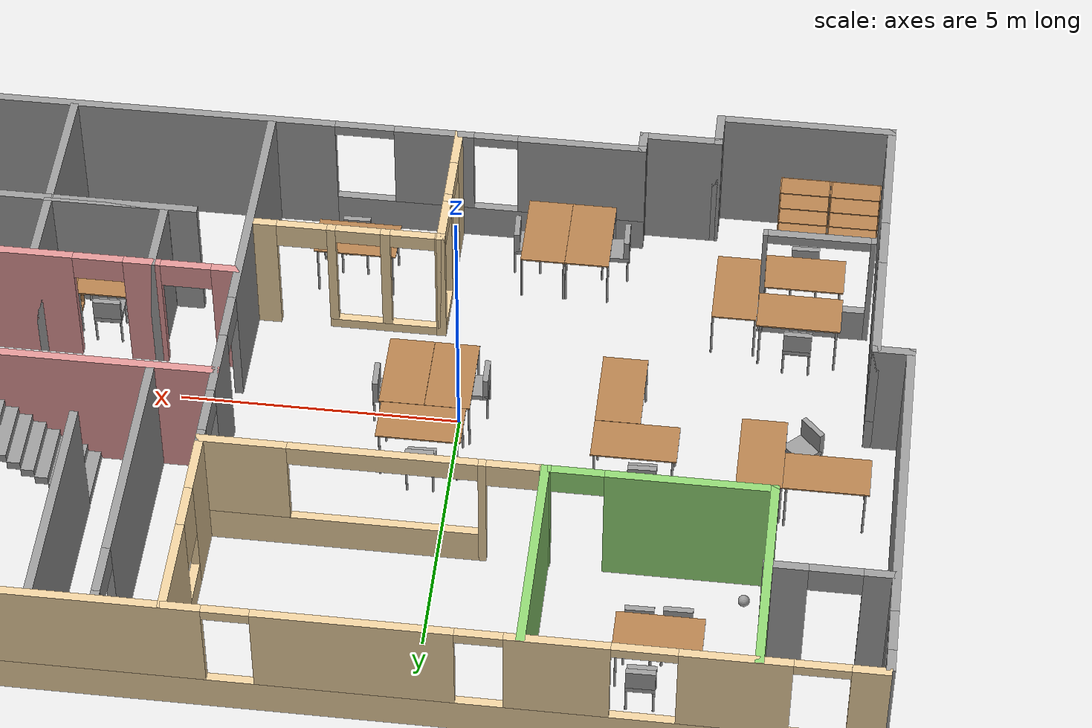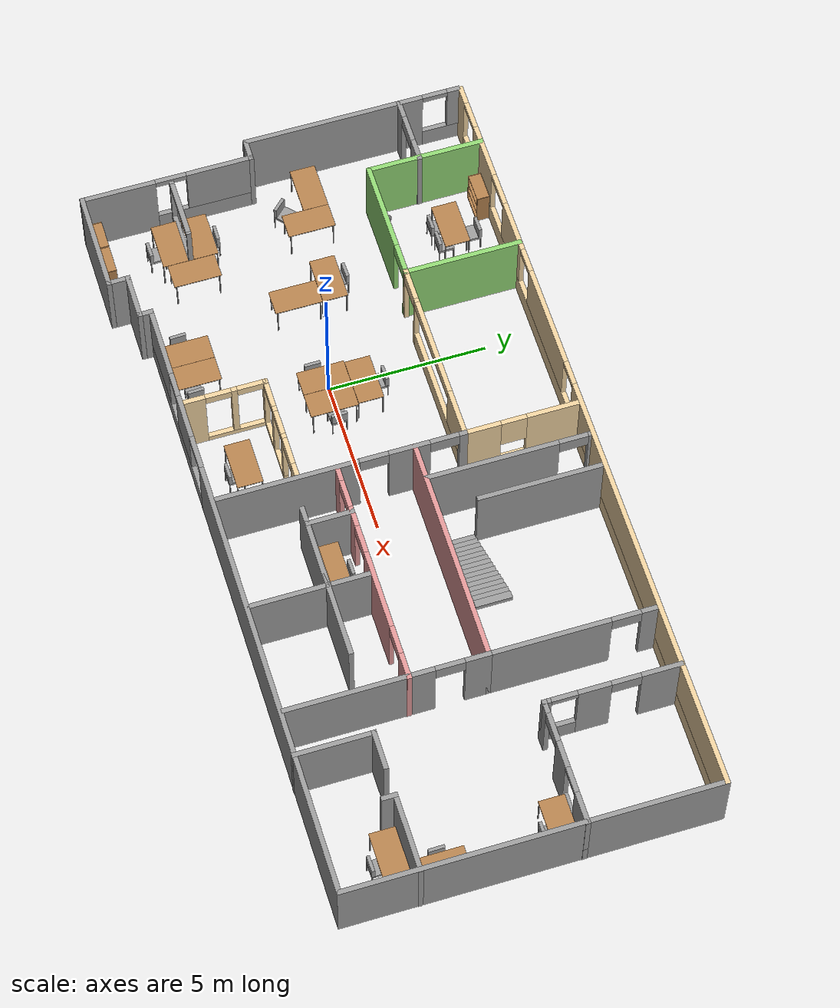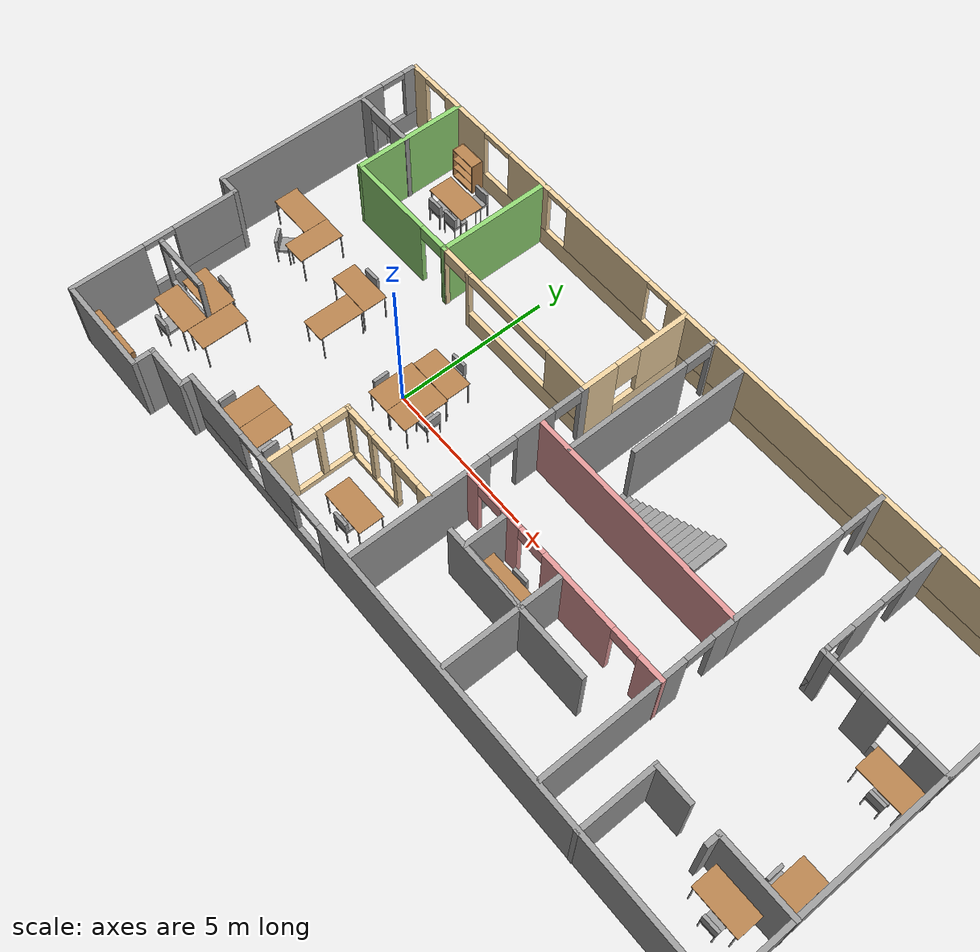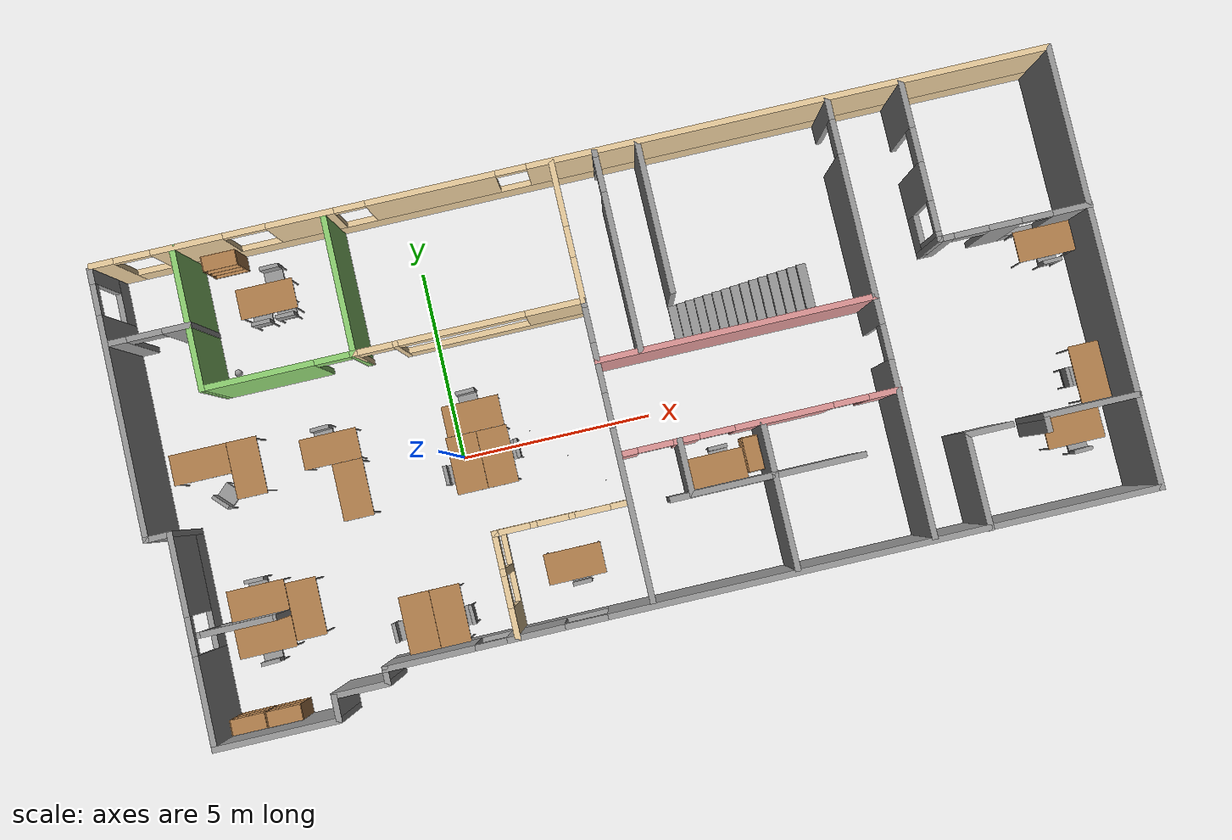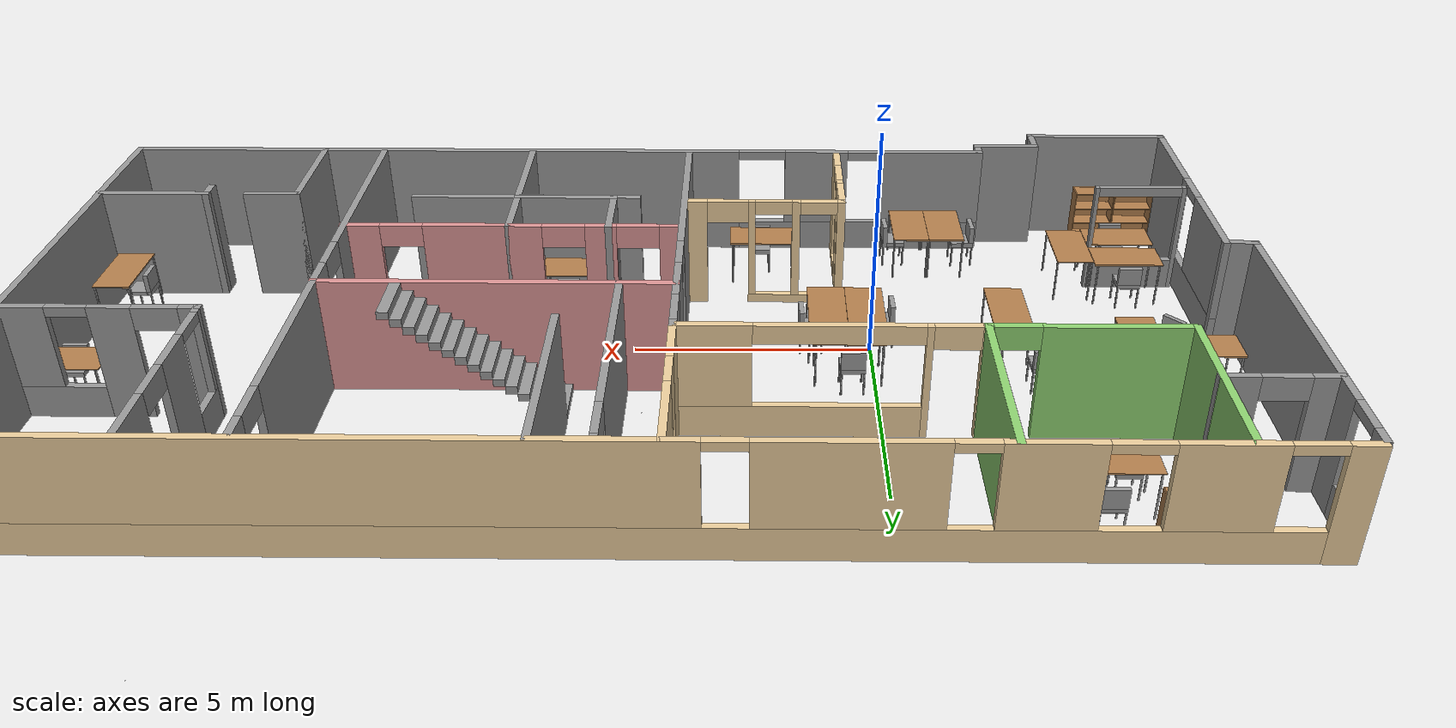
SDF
<sdf version="1.6">
 <world name="default">
  <plugin name="welcome_message" filename="libwelcome_message.so"/>
  <light name="sun" type="directional">
   <pose>0 0 10 0 -0 0</pose>
   <diffuse>0.8 0.8 0.8 1</diffuse>
   <specular>0.2 0.2 0.2 1</specular>
   <attenuation>
    <range>1000</range>
    <constant>0.9</constant>
    <linear>0.01</linear>
    <quadratic>0.001</quadratic>
   </attenuation>
   <direction>-0.5 0.1 -0.9</direction>
  </light>
  <model name="ground_plane">
   <static>1</static>
   <link name="link">
    <collision name="collision">
     <geometry><plane><normal>0 0 1</normal><size>100 100</size></plane></geometry>
     <surface>
      <contact><collide_bitmask>65535</collide_bitmask></contact>
      <friction><ode><mu>100</mu><mu2>50</mu2></ode></friction>
     </surface>
    </collision>
    <visual name="visual">
     <cast_shadows>0</cast_shadows>
     <geometry><plane><normal>0 0 1</normal><size>100 100</size></plane></geometry>
     <material>
      <script><uri>file://media/materials/scripts/gazebo.material</uri><name>Gazebo/Grey</name></script>
     </material>
    </visual>
   </link>
  </model>
  <gravity>0 0 -9.8</gravity>
  <magnetic_field>6e-06 2.3e-05 -4.2e-05</magnetic_field>
  <atmosphere type="adiabatic"/>
  <physics name="default_physics" default="0" type="ode">
   <max_step_size>0.001</max_step_size>
   <real_time_factor>1</real_time_factor>
   <real_time_update_rate>1000</real_time_update_rate>
  </physics>
  <scene><ambient>0.4 0.4 0.4 1</ambient><background>0.7 0.7 0.7 1</background><shadows>1</shadows></scene>
  <audio><device>default</device></audio>
  <spherical_coordinates>
   <surface_model>EARTH_WGS84</surface_model>
   <latitude_deg>0</latitude_deg>
   <longitude_deg>0</longitude_deg>
   <elevation>0</elevation>
   <heading_deg>0</heading_deg>
  </spherical_coordinates>
  <model name="dunder_mifflin_scranton_full">
   <pose>4.5312 0.479645 0 0 -0 0</pose>
   <link name="Stairs_0">
    <visual name="Stairs_0_Visual_0">
     <pose>1.73013 1.63779 0.083333 0 -0 1.5708</pose>
     <geometry><box><size>1.12038 0.229766 0.166667</size></box></geometry>
     <material>
      <script><uri>file://media/materials/scripts/gazebo.material</uri><name>Gazebo/Grey</name></script>
      <ambient>1 1 1 1</ambient>
     </material>
     <meta><layer>0</layer></meta>
    </visual>
    <collision name="Stairs_0_Collision_0">
     <geometry><box><size>1.12038 0.229766 0.166667</size></box></geometry>
     <pose>1.73013 1.63779 0.083333 0 -0 1.5708</pose>
    </collision>
    <visual name="Stairs_0_Visual_1">
     <pose>1.9599 1.63779 0.25 0 -0 1.5708</pose>
     <geometry><box><size>1.12038 0.229766 0.166667</size></box></geometry>
     <material>
      <script><uri>file://media/materials/scripts/gazebo.material</uri><name>Gazebo/Grey</name></script>
      <ambient>1 1 1 1</ambient>
     </material>
     <meta><layer>0</layer></meta>
    </visual>
    <collision name="Stairs_0_Collision_1">
     <geometry><box><size>1.12038 0.229766 0.166667</size></box></geometry>
     <pose>1.9599 1.63779 0.25 0 -0 1.5708</pose>
    </collision>
    <visual name="Stairs_0_Visual_2">
     <pose>2.18967 1.63779 0.416667 0 -0 1.5708</pose>
     <geometry><box><size>1.12038 0.229766 0.166667</size></box></geometry>
     <material>
      <script><uri>file://media/materials/scripts/gazebo.material</uri><name>Gazebo/Grey</name></script>
      <ambient>1 1 1 1</ambient>
     </material>
     <meta><layer>0</layer></meta>
    </visual>
    <collision name="Stairs_0_Collision_2">
     <geometry><box><size>1.12038 0.229766 0.166667</size></box></geometry>
     <pose>2.18967 1.63779 0.416667 0 -0 1.5708</pose>
    </collision>
    <visual name="Stairs_0_Visual_3">
     <pose>2.41944 1.63779 0.583333 0 -0 1.5708</pose>
     <geometry><box><size>1.12038 0.229766 0.166667</size></box></geometry>
     <material>
      <script><uri>file://media/materials/scripts/gazebo.material</uri><name>Gazebo/Grey</name></script>
      <ambient>1 1 1 1</ambient>
     </material>
     <meta><layer>0</layer></meta>
    </visual>
    <collision name="Stairs_0_Collision_3">
     <geometry><box><size>1.12038 0.229766 0.166667</size></box></geometry>
     <pose>2.41944 1.63779 0.583333 0 -0 1.5708</pose>
    </collision>
    <visual name="Stairs_0_Visual_4">
     <pose>2.6492 1.63779 0.75 0 -0 1.5708</pose>
     <geometry><box><size>1.12038 0.229766 0.166667</size></box></geometry>
     <material>
      <script><uri>file://media/materials/scripts/gazebo.material</uri><name>Gazebo/Grey</name></script>
      <ambient>1 1 1 1</ambient>
     </material>
     <meta><layer>0</layer></meta>
    </visual>
    <collision name="Stairs_0_Collision_4">
     <geometry><box><size>1.12038 0.229766 0.166667</size></box></geometry>
     <pose>2.6492 1.63779 0.75 0 -0 1.5708</pose>
    </collision>
    <visual name="Stairs_0_Visual_5">
     <pose>2.87897 1.63779 0.916667 0 -0 1.5708</pose>
     <geometry><box><size>1.12038 0.229766 0.166667</size></box></geometry>
     <material>
      <script><uri>file://media/materials/scripts/gazebo.material</uri><name>Gazebo/Grey</name></script>
      <ambient>1 1 1 1</ambient>
     </material>
     <meta><layer>0</layer></meta>
    </visual>
    <collision name="Stairs_0_Collision_5">
     <geometry><box><size>1.12038 0.229766 0.166667</size></box></geometry>
     <pose>2.87897 1.63779 0.916667 0 -0 1.5708</pose>
    </collision>
    <visual name="Stairs_0_Visual_6">
     <pose>3.10873 1.63779 1.08333 0 -0 1.5708</pose>
     <geometry><box><size>1.12038 0.229766 0.166667</size></box></geometry>
     <material>
      <script><uri>file://media/materials/scripts/gazebo.material</uri><name>Gazebo/Grey</name></script>
      <ambient>1 1 1 1</ambient>
     </material>
     <meta><layer>0</layer></meta>
    </visual>
    <collision name="Stairs_0_Collision_6">
     <geometry><box><size>1.12038 0.229766 0.166667</size></box></geometry>
     <pose>3.10873 1.63779 1.08333 0 -0 1.5708</pose>
    </collision>
    <visual name="Stairs_0_Visual_7">
     <pose>3.3385 1.63779 1.25 0 -0 1.5708</pose>
     <geometry><box><size>1.12038 0.229766 0.166667</size></box></geometry>
     <material>
      <script><uri>file://media/materials/scripts/gazebo.material</uri><name>Gazebo/Grey</name></script>
      <ambient>1 1 1 1</ambient>
     </material>
     <meta><layer>0</layer></meta>
    </visual>
    <collision name="Stairs_0_Collision_7">
     <geometry><box><size>1.12038 0.229766 0.166667</size></box></geometry>
     <pose>3.3385 1.63779 1.25 0 -0 1.5708</pose>
    </collision>
    <visual name="Stairs_0_Visual_8">
     <pose>3.56827 1.63779 1.41667 0 -0 1.5708</pose>
     <geometry><box><size>1.12038 0.229766 0.166667</size></box></geometry>
     <material>
      <script><uri>file://media/materials/scripts/gazebo.material</uri><name>Gazebo/Grey</name></script>
      <ambient>1 1 1 1</ambient>
     </material>
     <meta><layer>0</layer></meta>
    </visual>
    <collision name="Stairs_0_Collision_8">
     <geometry><box><size>1.12038 0.229766 0.166667</size></box></geometry>
     <pose>3.56827 1.63779 1.41667 0 -0 1.5708</pose>
    </collision>
    <visual name="Stairs_0_Visual_9">
     <pose>3.79803 1.63779 1.58333 0 -0 1.5708</pose>
     <geometry><box><size>1.12038 0.229766 0.166667</size></box></geometry>
     <material>
      <script><uri>file://media/materials/scripts/gazebo.material</uri><name>Gazebo/Grey</name></script>
      <ambient>1 1 1 1</ambient>
     </material>
     <meta><layer>0</layer></meta>
    </visual>
    <collision name="Stairs_0_Collision_9">
     <geometry><box><size>1.12038 0.229766 0.166667</size></box></geometry>
     <pose>3.79803 1.63779 1.58333 0 -0 1.5708</pose>
    </collision>
    <visual name="Stairs_0_Visual_10">
     <pose>4.0278 1.63779 1.75 0 -0 1.5708</pose>
     <geometry><box><size>1.12038 0.229766 0.166667</size></box></geometry>
     <material>
      <script><uri>file://media/materials/scripts/gazebo.material</uri><name>Gazebo/Grey</name></script>
      <ambient>1 1 1 1</ambient>
     </material>
     <meta><layer>0</layer></meta>
    </visual>
    <collision name="Stairs_0_Collision_10">
     <geometry><box><size>1.12038 0.229766 0.166667</size></box></geometry>
     <pose>4.0278 1.63779 1.75 0 -0 1.5708</pose>
    </collision>
    <visual name="Stairs_0_Visual_11">
     <pose>4.25757 1.63779 1.91667 0 -0 1.5708</pose>
     <geometry><box><size>1.12038 0.229766 0.166667</size></box></geometry>
     <material>
      <script><uri>file://media/materials/scripts/gazebo.material</uri><name>Gazebo/Grey</name></script>
      <ambient>1 1 1 1</ambient>
     </material>
     <meta><layer>0</layer></meta>
    </visual>
    <collision name="Stairs_0_Collision_11">
     <geometry><box><size>1.12038 0.229766 0.166667</size></box></geometry>
     <pose>4.25757 1.63779 1.91667 0 -0 1.5708</pose>
    </collision>
    <visual name="Stairs_0_Visual_12">
     <pose>4.48733 1.63779 2.08333 0 -0 1.5708</pose>
     <geometry><box><size>1.12038 0.229766 0.166667</size></box></geometry>
     <material>
      <script><uri>file://media/materials/scripts/gazebo.material</uri><name>Gazebo/Grey</name></script>
      <ambient>1 1 1 1</ambient>
     </material>
     <meta><layer>0</layer></meta>
    </visual>
    <collision name="Stairs_0_Collision_12">
     <geometry><box><size>1.12038 0.229766 0.166667</size></box></geometry>
     <pose>4.48733 1.63779 2.08333 0 -0 1.5708</pose>
    </collision>
    <visual name="Stairs_0_Visual_13">
     <pose>4.7171 1.63779 2.25 0 -0 1.5708</pose>
     <geometry><box><size>1.12038 0.229766 0.166667</size></box></geometry>
     <material>
      <script><uri>file://media/materials/scripts/gazebo.material</uri><name>Gazebo/Grey</name></script>
      <ambient>1 1 1 1</ambient>
     </material>
     <meta><layer>0</layer></meta>
    </visual>
    <collision name="Stairs_0_Collision_13">
     <geometry><box><size>1.12038 0.229766 0.166667</size></box></geometry>
     <pose>4.7171 1.63779 2.25 0 -0 1.5708</pose>
    </collision>
    <visual name="Stairs_0_Visual_14">
     <pose>4.94687 1.63779 2.41667 0 -0 1.5708</pose>
     <geometry><box><size>1.12038 0.229766 0.166667</size></box></geometry>
     <material>
      <script><uri>file://media/materials/scripts/gazebo.material</uri><name>Gazebo/Grey</name></script>
      <ambient>1 1 1 1</ambient>
     </material>
     <meta><layer>0</layer></meta>
    </visual>
    <collision name="Stairs_0_Collision_14">
     <geometry><box><size>1.12038 0.229766 0.166667</size></box></geometry>
     <pose>4.94687 1.63779 2.41667 0 -0 1.5708</pose>
    </collision>
   </link>
   <link name="Wall_10">
    <collision name="Wall_10_Collision">
     <geometry><box><size>1.5 0.15 2.5</size></box></geometry>
     <pose>0 0 1.25 0 -0 0</pose>
    </collision>
    <visual name="Wall_10_Visual">
     <pose>0 0 1.25 0 -0 0</pose>
     <geometry><box><size>1.5 0.15 2.5</size></box></geometry>
     <material>
      <script><uri>file://media/materials/scripts/gazebo.material</uri><name>Gazebo/Grey</name></script>
      <ambient>1 1 1 1</ambient>
     </material>
     <meta><layer>0</layer></meta>
    </visual>
    <pose>-7.95712 -5.55 0 0 -0 3.14159</pose>
   </link>
   <link name="Wall_11">
    <collision name="Wall_11_Collision">
     <geometry><box><size>0.75 0.15 2.5</size></box></geometry>
     <pose>0 0 1.25 0 -0 0</pose>
    </collision>
    <visual name="Wall_11_Visual">
     <pose>0 0 1.25 0 -0 0</pose>
     <geometry><box><size>0.75 0.15 2.5</size></box></geometry>
     <material>
      <script><uri>file://media/materials/scripts/gazebo.material</uri><name>Gazebo/Grey</name></script>
      <ambient>1 1 1 1</ambient>
     </material>
     <meta><layer>0</layer></meta>
    </visual>
    <pose>-8.63212 -5.85 0 0 -0 -1.5708</pose>
   </link>
   <link name="Wall_12">
    <collision name="Wall_12_Collision">
     <geometry><box><size>3.25 0.15 2.5</size></box></geometry>
     <pose>0 0 1.25 0 -0 0</pose>
    </collision>
    <visual name="Wall_12_Visual">
     <pose>0 0 1.25 0 -0 0</pose>
     <geometry><box><size>3.25 0.15 2.5</size></box></geometry>
     <material>
      <script><uri>file://media/materials/scripts/gazebo.material</uri><name>Gazebo/Grey</name></script>
      <ambient>1 1 1 1</ambient>
     </material>
     <meta><layer>0</layer></meta>
    </visual>
    <pose>-10.1821 -6.15 0 0 -0 3.14159</pose>
   </link>
   <link name="Wall_13">
    <pose>-11.7321 -3.475 0 0 -0 1.5708</pose>
    <visual name="Wall_13_Visual_0">
     <pose>-1.56118 0 1.25 0 -0 0</pose>
     <geometry><box><size>2.37764 0.15 2.5</size></box></geometry>
     <material>
      <script><uri>file://media/materials/scripts/gazebo.material</uri><name>Gazebo/Grey</name></script>
      <ambient>1 1 1 1</ambient>
     </material>
     <meta><layer>0</layer></meta>
    </visual>
    <collision name="Wall_13_Collision_0">
     <geometry><box><size>2.37764 0.15 2.5</size></box></geometry>
     <pose>-1.56118 0 1.25 0 -0 0</pose>
    </collision>
    <visual name="Wall_13_Visual_1">
     <pose>1.18882 0 0.35 0 -0 0</pose>
     <geometry><box><size>3.12236 0.15 0.7</size></box></geometry>
     <material>
      <script><uri>file://media/materials/scripts/gazebo.material</uri><name>Gazebo/Grey</name></script>
      <ambient>1 1 1 1</ambient>
     </material>
     <meta><layer>0</layer></meta>
    </visual>
    <collision name="Wall_13_Collision_1">
     <geometry><box><size>3.12236 0.15 0.7</size></box></geometry>
     <pose>1.18882 0 0.35 0 -0 0</pose>
    </collision>
    <visual name="Wall_13_Visual_2">
     <pose>1.67832 0 1.6 0 -0 0</pose>
     <geometry><box><size>2.14336 0.15 1.8</size></box></geometry>
     <material>
      <script><uri>file://media/materials/scripts/gazebo.material</uri><name>Gazebo/Grey</name></script>
      <ambient>1 1 1 1</ambient>
     </material>
     <meta><layer>0</layer></meta>
    </visual>
    <collision name="Wall_13_Collision_2">
     <geometry><box><size>2.14336 0.15 1.8</size></box></geometry>
     <pose>1.67832 0 1.6 0 -0 0</pose>
    </collision>
    <visual name="Wall_13_Visual_3">
     <pose>0.117145 0 2.4 0 -0 0</pose>
     <geometry><box><size>0.979 0.15 0.2</size></box></geometry>
     <material>
      <script><uri>file://media/materials/scripts/gazebo.material</uri><name>Gazebo/Grey</name></script>
      <ambient>1 1 1 1</ambient>
     </material>
     <meta><layer>0</layer></meta>
    </visual>
    <collision name="Wall_13_Collision_3">
     <geometry><box><size>0.979 0.15 0.2</size></box></geometry>
     <pose>0.117145 0 2.4 0 -0 0</pose>
    </collision>
   </link>
   <link name="Wall_14">
    <collision name="Wall_14_Collision">
     <geometry><box><size>0.75 0.15 2.5</size></box></geometry>
     <pose>0 0 1.25 0 -0 0</pose>
    </collision>
    <visual name="Wall_14_Visual">
     <pose>0 0 1.25 0 -0 0</pose>
     <geometry><box><size>0.75 0.15 2.5</size></box></geometry>
     <material>
      <script><uri>file://media/materials/scripts/gazebo.material</uri><name>Gazebo/Grey</name></script>
      <ambient>1 1 1 1</ambient>
     </material>
     <meta><layer>0</layer></meta>
    </visual>
    <pose>-12.0321 -0.8 0 0 -0 3.14159</pose>
   </link>
   <link name="Wall_15">
    <pose>-12.3321 2.625 0 0 -0 1.5708</pose>
    <visual name="Wall_15_Visual_0">
     <pose>-0.612803 0 1.25 0 -0 0</pose>
     <geometry><box><size>5.7744 0.15 2.5</size></box></geometry>
     <material>
      <script><uri>file://media/materials/scripts/gazebo.material</uri><name>Gazebo/Grey</name></script>
      <ambient>1 1 1 1</ambient>
     </material>
     <meta><layer>0</layer></meta>
    </visual>
    <collision name="Wall_15_Collision_0">
     <geometry><box><size>5.7744 0.15 2.5</size></box></geometry>
     <pose>-0.612803 0 1.25 0 -0 0</pose>
    </collision>
    <visual name="Wall_15_Visual_1">
     <pose>2.8872 0 0.35 0 -0 0</pose>
     <geometry><box><size>1.22561 0.15 0.7</size></box></geometry>
     <material>
      <script><uri>file://media/materials/scripts/gazebo.material</uri><name>Gazebo/Grey</name></script>
      <ambient>1 1 1 1</ambient>
     </material>
     <meta><layer>0</layer></meta>
    </visual>
    <collision name="Wall_15_Collision_1">
     <geometry><box><size>1.22561 0.15 0.7</size></box></geometry>
     <pose>2.8872 0 0.35 0 -0 0</pose>
    </collision>
    <visual name="Wall_15_Visual_2">
     <pose>3.2872 0 1.6 0 -0 0</pose>
     <geometry><box><size>0.425605 0.15 1.8</size></box></geometry>
     <material>
      <script><uri>file://media/materials/scripts/gazebo.material</uri><name>Gazebo/Grey</name></script>
      <ambient>1 1 1 1</ambient>
     </material>
     <meta><layer>0</layer></meta>
    </visual>
    <collision name="Wall_15_Collision_2">
     <geometry><box><size>0.425605 0.15 1.8</size></box></geometry>
     <pose>3.2872 0 1.6 0 -0 0</pose>
    </collision>
    <visual name="Wall_15_Visual_3">
     <pose>2.6744 0 2.4 0 -0 0</pose>
     <geometry><box><size>0.8 0.15 0.2</size></box></geometry>
     <material>
      <script><uri>file://media/materials/scripts/gazebo.material</uri><name>Gazebo/Grey</name></script>
      <ambient>1 1 1 1</ambient>
     </material>
     <meta><layer>0</layer></meta>
    </visual>
    <collision name="Wall_15_Collision_3">
     <geometry><box><size>0.8 0.15 0.2</size></box></geometry>
     <pose>2.6744 0 2.4 0 -0 0</pose>
    </collision>
   </link>
   <link name="Wall_19">
    <collision name="Wall_19_Collision">
     <geometry><box><size>3.75 0.15 2.5</size></box></geometry>
     <pose>0 0 1.25 0 -0 0</pose>
    </collision>
    <visual name="Wall_19_Visual">
     <pose>0 0 1.25 0 -0 0</pose>
     <geometry><box><size>3.75 0.15 2.5</size></box></geometry>
     <material>
      <script><uri>file://media/materials/scripts/gazebo.material</uri><name>Gazebo/Grey</name></script>
      <ambient>0.556863 0.823529 0.443137 1</ambient>
     </material>
     <meta><layer>0</layer></meta>
    </visual>
    <pose>-10.2322 4.33925 0 0 -0 -1.5708</pose>
   </link>
   <link name="Wall_20">
    <pose>-8.30724 2.53925 0 0 -0 0</pose>
    <visual name="Wall_20_Visual_0">
     <pose>-0.536103 0 1.25 0 -0 0</pose>
     <geometry><box><size>2.92779 0.15 2.5</size></box></geometry>
     <material>
      <script><uri>file://media/materials/scripts/gazebo.material</uri><name>Gazebo/Grey</name></script>
      <ambient>0.556863 0.823529 0.443137 1</ambient>
     </material>
     <meta><layer>0</layer></meta>
    </visual>
    <collision name="Wall_20_Collision_0">
     <geometry><box><size>2.92779 0.15 2.5</size></box></geometry>
     <pose>-0.536103 0 1.25 0 -0 0</pose>
    </collision>
    <visual name="Wall_20_Visual_1">
     <pose>1.9139 0 1.25 0 -0 0</pose>
     <geometry><box><size>0.172206 0.15 2.5</size></box></geometry>
     <material>
      <script><uri>file://media/materials/scripts/gazebo.material</uri><name>Gazebo/Grey</name></script>
      <ambient>0.556863 0.823529 0.443137 1</ambient>
     </material>
     <meta><layer>0</layer></meta>
    </visual>
    <collision name="Wall_20_Collision_1">
     <geometry><box><size>0.172206 0.15 2.5</size></box></geometry>
     <pose>1.9139 0 1.25 0 -0 0</pose>
    </collision>
    <visual name="Wall_20_Visual_2">
     <pose>1.37779 0 2.25 0 -0 0</pose>
     <geometry><box><size>0.9 0.15 0.5</size></box></geometry>
     <material>
      <script><uri>file://media/materials/scripts/gazebo.material</uri><name>Gazebo/Grey</name></script>
      <ambient>0.556863 0.823529 0.443137 1</ambient>
     </material>
     <meta><layer>0</layer></meta>
    </visual>
    <collision name="Wall_20_Collision_2">
     <geometry><box><size>0.9 0.15 0.5</size></box></geometry>
     <pose>1.37779 0 2.25 0 -0 0</pose>
    </collision>
   </link>
   <link name="Wall_21">
    <collision name="Wall_21_Collision">
     <geometry><box><size>3.75 0.15 2.5</size></box></geometry>
     <pose>0 0 1.25 0 -0 0</pose>
    </collision>
    <visual name="Wall_21_Visual">
     <pose>0 0 1.25 0 -0 0</pose>
     <geometry><box><size>3.75 0.15 2.5</size></box></geometry>
     <material>
      <script><uri>file://media/materials/scripts/gazebo.material</uri><name>Gazebo/Grey</name></script>
      <ambient>0.556863 0.823529 0.443137 1</ambient>
     </material>
     <meta><layer>0</layer></meta>
    </visual>
    <pose>-6.38225 4.33925 0 0 -0 1.5708</pose>
   </link>
   <link name="Wall_23">
    <pose>-3.45724 2.53925 0 0 -0 0</pose>
    <visual name="Wall_23_Visual_0">
     <pose>-2.91414 0 1.25 0 -0 0</pose>
     <geometry><box><size>0.171718 0.15 2.5</size></box></geometry>
     <material>
      <script><uri>file://media/materials/scripts/gazebo.material</uri><name>Gazebo/Grey</name></script>
      <ambient>0.921569 0.807843 0.615686 1</ambient>
     </material>
     <meta><layer>0</layer></meta>
    </visual>
    <collision name="Wall_23_Collision_0">
     <geometry><box><size>0.171718 0.15 2.5</size></box></geometry>
     <pose>-2.91414 0 1.25 0 -0 0</pose>
    </collision>
    <visual name="Wall_23_Visual_1">
     <pose>-1.86179 0 1.25 0 -0 0</pose>
     <geometry><box><size>0.132993 0.15 2.5</size></box></geometry>
     <material>
      <script><uri>file://media/materials/scripts/gazebo.material</uri><name>Gazebo/Grey</name></script>
      <ambient>0.921569 0.807843 0.615686 1</ambient>
     </material>
     <meta><layer>0</layer></meta>
    </visual>
    <collision name="Wall_23_Collision_1">
     <geometry><box><size>0.132993 0.15 2.5</size></box></geometry>
     <pose>-1.86179 0 1.25 0 -0 0</pose>
    </collision>
    <visual name="Wall_23_Visual_2">
     <pose>0.602356 0 0.35 0 -0 0</pose>
     <geometry><box><size>4.79529 0.15 0.7</size></box></geometry>
     <material>
      <script><uri>file://media/materials/scripts/gazebo.material</uri><name>Gazebo/Grey</name></script>
      <ambient>0.921569 0.807843 0.615686 1</ambient>
     </material>
     <meta><layer>0</layer></meta>
    </visual>
    <collision name="Wall_23_Collision_2">
     <geometry><box><size>4.79529 0.15 0.7</size></box></geometry>
     <pose>0.602356 0 0.35 0 -0 0</pose>
    </collision>
    <visual name="Wall_23_Visual_3">
     <pose>2.22271 0 1.6 0 -0 0</pose>
     <geometry><box><size>1.55459 0.15 1.8</size></box></geometry>
     <material>
      <script><uri>file://media/materials/scripts/gazebo.material</uri><name>Gazebo/Grey</name></script>
      <ambient>0.921569 0.807843 0.615686 1</ambient>
     </material>
     <meta><layer>0</layer></meta>
    </visual>
    <collision name="Wall_23_Collision_3">
     <geometry><box><size>1.55459 0.15 1.8</size></box></geometry>
     <pose>2.22271 0 1.6 0 -0 0</pose>
    </collision>
    <visual name="Wall_23_Visual_4">
     <pose>-2.37828 0 2.25 0 -0 0</pose>
     <geometry><box><size>0.9 0.15 0.5</size></box></geometry>
     <material>
      <script><uri>file://media/materials/scripts/gazebo.material</uri><name>Gazebo/Grey</name></script>
      <ambient>0.921569 0.807843 0.615686 1</ambient>
     </material>
     <meta><layer>0</layer></meta>
    </visual>
    <collision name="Wall_23_Collision_4">
     <geometry><box><size>0.9 0.15 0.5</size></box></geometry>
     <pose>-2.37828 0 2.25 0 -0 0</pose>
    </collision>
    <visual name="Wall_23_Visual_5">
     <pose>-0.174937 0 2.3 0 -0 0</pose>
     <geometry><box><size>3.2407 0.15 0.4</size></box></geometry>
     <material>
      <script><uri>file://media/materials/scripts/gazebo.material</uri><name>Gazebo/Grey</name></script>
      <ambient>0.921569 0.807843 0.615686 1</ambient>
     </material>
     <meta><layer>0</layer></meta>
    </visual>
    <collision name="Wall_23_Collision_5">
     <geometry><box><size>3.2407 0.15 0.4</size></box></geometry>
     <pose>-0.174937 0 2.3 0 -0 0</pose>
    </collision>
   </link>
   <link name="Wall_24">
    <pose>-0.532245 4.33925 0 0 -0 1.5708</pose>
    <visual name="Wall_24_Visual_0">
     <pose>-1.28185 0 1.25 0 -0 0</pose>
     <geometry><box><size>1.1863 0.15 2.5</size></box></geometry>
     <material>
      <script><uri>file://media/materials/scripts/gazebo.material</uri><name>Gazebo/Grey</name></script>
      <ambient>0.921569 0.807843 0.615686 1</ambient>
     </material>
     <meta><layer>0</layer></meta>
    </visual>
    <collision name="Wall_24_Collision_0">
     <geometry><box><size>1.1863 0.15 2.5</size></box></geometry>
     <pose>-1.28185 0 1.25 0 -0 0</pose>
    </collision>
    <visual name="Wall_24_Visual_1">
     <pose>0.59315 0 0.25 0 -0 0</pose>
     <geometry><box><size>2.5637 0.15 0.5</size></box></geometry>
     <material>
      <script><uri>file://media/materials/scripts/gazebo.material</uri><name>Gazebo/Grey</name></script>
      <ambient>0.921569 0.807843 0.615686 1</ambient>
     </material>
     <meta><layer>0</layer></meta>
    </visual>
    <collision name="Wall_24_Collision_1">
     <geometry><box><size>2.5637 0.15 0.5</size></box></geometry>
     <pose>0.59315 0 0.25 0 -0 0</pose>
    </collision>
    <visual name="Wall_24_Visual_2">
     <pose>0.99315 0 1.5 0 -0 0</pose>
     <geometry><box><size>1.7637 0.15 2</size></box></geometry>
     <material>
      <script><uri>file://media/materials/scripts/gazebo.material</uri><name>Gazebo/Grey</name></script>
      <ambient>0.921569 0.807843 0.615686 1</ambient>
     </material>
     <meta><layer>0</layer></meta>
    </visual>
    <collision name="Wall_24_Collision_2">
     <geometry><box><size>1.7637 0.15 2</size></box></geometry>
     <pose>0.99315 0 1.5 0 -0 0</pose>
    </collision>
    <visual name="Wall_24_Visual_3">
     <pose>-0.288699 0 1.9 0 -0 0</pose>
     <geometry><box><size>0.8 0.15 1.2</size></box></geometry>
     <material>
      <script><uri>file://media/materials/scripts/gazebo.material</uri><name>Gazebo/Grey</name></script>
      <ambient>0.921569 0.807843 0.615686 1</ambient>
     </material>
     <meta><layer>0</layer></meta>
    </visual>
    <collision name="Wall_24_Collision_3">
     <geometry><box><size>0.8 0.15 1.2</size></box></geometry>
     <pose>-0.288699 0 1.9 0 -0 0</pose>
    </collision>
   </link>
   <link name="Wall_26">
    <pose>-0.532245 -1.26075 0 0 -0 -1.5708</pose>
    <visual name="Wall_26_Visual_0">
     <pose>-3.74743 0 1.25 0 -0 0</pose>
     <geometry><box><size>0.255133 0.15 2.5</size></box></geometry>
     <material>
      <script><uri>file://media/materials/scripts/gazebo.material</uri><name>Gazebo/Grey</name></script>
      <ambient>1 1 1 1</ambient>
     </material>
     <meta><layer>0</layer></meta>
    </visual>
    <collision name="Wall_26_Collision_0">
     <geometry><box><size>0.255133 0.15 2.5</size></box></geometry>
     <pose>-3.74743 0 1.25 0 -0 0</pose>
    </collision>
    <visual name="Wall_26_Visual_1">
     <pose>-2.08102 0 1.25 0 -0 0</pose>
     <geometry><box><size>1.27769 0.15 2.5</size></box></geometry>
     <material>
      <script><uri>file://media/materials/scripts/gazebo.material</uri><name>Gazebo/Grey</name></script>
      <ambient>1 1 1 1</ambient>
     </material>
     <meta><layer>0</layer></meta>
    </visual>
    <collision name="Wall_26_Collision_1">
     <geometry><box><size>1.27769 0.15 2.5</size></box></geometry>
     <pose>-2.08102 0 1.25 0 -0 0</pose>
    </collision>
    <visual name="Wall_26_Visual_2">
     <pose>1.66641 0 1.25 0 -0 0</pose>
     <geometry><box><size>4.41718 0.15 2.5</size></box></geometry>
     <material>
      <script><uri>file://media/materials/scripts/gazebo.material</uri><name>Gazebo/Grey</name></script>
      <ambient>1 1 1 1</ambient>
     </material>
     <meta><layer>0</layer></meta>
    </visual>
    <collision name="Wall_26_Collision_2">
     <geometry><box><size>4.41718 0.15 2.5</size></box></geometry>
     <pose>1.66641 0 1.25 0 -0 0</pose>
    </collision>
    <visual name="Wall_26_Visual_3">
     <pose>-3.16987 0 2.25 0 -0 0</pose>
     <geometry><box><size>0.9 0.15 0.5</size></box></geometry>
     <material>
      <script><uri>file://media/materials/scripts/gazebo.material</uri><name>Gazebo/Grey</name></script>
      <ambient>1 1 1 1</ambient>
     </material>
     <meta><layer>0</layer></meta>
    </visual>
    <collision name="Wall_26_Collision_3">
     <geometry><box><size>0.9 0.15 0.5</size></box></geometry>
     <pose>-3.16987 0 2.25 0 -0 0</pose>
    </collision>
    <visual name="Wall_26_Visual_4">
     <pose>-0.992175 0 2.25 0 -0 0</pose>
     <geometry><box><size>0.9 0.15 0.5</size></box></geometry>
     <material>
      <script><uri>file://media/materials/scripts/gazebo.material</uri><name>Gazebo/Grey</name></script>
      <ambient>1 1 1 1</ambient>
     </material>
     <meta><layer>0</layer></meta>
    </visual>
    <collision name="Wall_26_Collision_4">
     <geometry><box><size>0.9 0.15 0.5</size></box></geometry>
     <pose>-0.992175 0 2.25 0 -0 0</pose>
    </collision>
   </link>
   <link name="Wall_28">
    <pose>-3.95331 -3.89431 0 0 -0 1.5708</pose>
    <visual name="Wall_28_Visual_0">
     <pose>-0.969422 0 1.25 0 -0 0</pose>
     <geometry><box><size>0.811156 0.15 2.5</size></box></geometry>
     <material>
      <script><uri>file://media/materials/scripts/gazebo.material</uri><name>Gazebo/Grey</name></script>
      <ambient>0.921569 0.807843 0.615686 1</ambient>
     </material>
     <meta><layer>0</layer></meta>
    </visual>
    <collision name="Wall_28_Collision_0">
     <geometry><box><size>0.811156 0.15 2.5</size></box></geometry>
     <pose>-0.969422 0 1.25 0 -0 0</pose>
    </collision>
    <visual name="Wall_28_Visual_1">
     <pose>0.405578 0 0.1 0 -0 0</pose>
     <geometry><box><size>1.93884 0.15 0.2</size></box></geometry>
     <material>
      <script><uri>file://media/materials/scripts/gazebo.material</uri><name>Gazebo/Grey</name></script>
      <ambient>0.921569 0.807843 0.615686 1</ambient>
     </material>
     <meta><layer>0</layer></meta>
    </visual>
    <collision name="Wall_28_Collision_1">
     <geometry><box><size>1.93884 0.15 0.2</size></box></geometry>
     <pose>0.405578 0 0.1 0 -0 0</pose>
    </collision>
    <visual name="Wall_28_Visual_2">
     <pose>0.328659 0 1.35 0 -0 0</pose>
     <geometry><box><size>0.185005 0.15 2.3</size></box></geometry>
     <material>
      <script><uri>file://media/materials/scripts/gazebo.material</uri><name>Gazebo/Grey</name></script>
      <ambient>0.921569 0.807843 0.615686 1</ambient>
     </material>
     <meta><layer>0</layer></meta>
    </visual>
    <collision name="Wall_28_Collision_2">
     <geometry><box><size>0.185005 0.15 2.3</size></box></geometry>
     <pose>0.328659 0 1.35 0 -0 0</pose>
    </collision>
    <visual name="Wall_28_Visual_3">
     <pose>1.29808 0 1.35 0 -0 0</pose>
     <geometry><box><size>0.153838 0.15 2.3</size></box></geometry>
     <material>
      <script><uri>file://media/materials/scripts/gazebo.material</uri><name>Gazebo/Grey</name></script>
      <ambient>0.921569 0.807843 0.615686 1</ambient>
     </material>
     <meta><layer>0</layer></meta>
    </visual>
    <collision name="Wall_28_Collision_3">
     <geometry><box><size>0.153838 0.15 2.3</size></box></geometry>
     <pose>1.29808 0 1.35 0 -0 0</pose>
    </collision>
    <visual name="Wall_28_Visual_4">
     <pose>-0.163844 0 2.35 0 -0 0</pose>
     <geometry><box><size>0.8 0.15 0.3</size></box></geometry>
     <material>
      <script><uri>file://media/materials/scripts/gazebo.material</uri><name>Gazebo/Grey</name></script>
      <ambient>0.921569 0.807843 0.615686 1</ambient>
     </material>
     <meta><layer>0</layer></meta>
    </visual>
    <collision name="Wall_28_Collision_4">
     <geometry><box><size>0.8 0.15 0.3</size></box></geometry>
     <pose>-0.163844 0 2.35 0 -0 0</pose>
    </collision>
    <visual name="Wall_28_Visual_5">
     <pose>0.821162 0 2.35 0 -0 0</pose>
     <geometry><box><size>0.8 0.15 0.3</size></box></geometry>
     <material>
      <script><uri>file://media/materials/scripts/gazebo.material</uri><name>Gazebo/Grey</name></script>
      <ambient>0.921569 0.807843 0.615686 1</ambient>
     </material>
     <meta><layer>0</layer></meta>
    </visual>
    <collision name="Wall_28_Collision_5">
     <geometry><box><size>0.8 0.15 0.3</size></box></geometry>
     <pose>0.821162 0 2.35 0 -0 0</pose>
    </collision>
   </link>
   <link name="Wall_29">
    <pose>-2.27831 -2.59431 0 0 -0 0</pose>
    <visual name="Wall_29_Visual_0">
     <pose>-1.66131 0 1.25 0 -0 0</pose>
     <geometry><box><size>0.177371 0.15 2.5</size></box></geometry>
     <material>
      <script><uri>file://media/materials/scripts/gazebo.material</uri><name>Gazebo/Grey</name></script>
      <ambient>0.921569 0.807843 0.615686 1</ambient>
     </material>
     <meta><layer>0</layer></meta>
    </visual>
    <collision name="Wall_29_Collision_0">
     <geometry><box><size>0.177371 0.15 2.5</size></box></geometry>
     <pose>-1.66131 0 1.25 0 -0 0</pose>
    </collision>
    <visual name="Wall_29_Visual_1">
     <pose>1.50358 0 1.25 0 -0 0</pose>
     <geometry><box><size>0.492835 0.15 2.5</size></box></geometry>
     <material>
      <script><uri>file://media/materials/scripts/gazebo.material</uri><name>Gazebo/Grey</name></script>
      <ambient>0.921569 0.807843 0.615686 1</ambient>
     </material>
     <meta><layer>0</layer></meta>
    </visual>
    <collision name="Wall_29_Collision_1">
     <geometry><box><size>0.492835 0.15 2.5</size></box></geometry>
     <pose>1.50358 0 1.25 0 -0 0</pose>
    </collision>
    <visual name="Wall_29_Visual_2">
     <pose>-0.607732 0 0.1 0 -0 0</pose>
     <geometry><box><size>1.92979 0.15 0.2</size></box></geometry>
     <material>
      <script><uri>file://media/materials/scripts/gazebo.material</uri><name>Gazebo/Grey</name></script>
      <ambient>0.921569 0.807843 0.615686 1</ambient>
     </material>
     <meta><layer>0</layer></meta>
    </visual>
    <collision name="Wall_29_Collision_2">
     <geometry><box><size>1.92979 0.15 0.2</size></box></geometry>
     <pose>-0.607732 0 0.1 0 -0 0</pose>
    </collision>
    <visual name="Wall_29_Visual_3">
     <pose>-0.685949 0 1.35 0 -0 0</pose>
     <geometry><box><size>0.17336 0.15 2.3</size></box></geometry>
     <material>
      <script><uri>file://media/materials/scripts/gazebo.material</uri><name>Gazebo/Grey</name></script>
      <ambient>0.921569 0.807843 0.615686 1</ambient>
     </material>
     <meta><layer>0</layer></meta>
    </visual>
    <collision name="Wall_29_Collision_3">
     <geometry><box><size>0.17336 0.15 2.3</size></box></geometry>
     <pose>-0.685949 0 1.35 0 -0 0</pose>
    </collision>
    <visual name="Wall_29_Visual_4">
     <pose>0.278948 0 1.35 0 -0 0</pose>
     <geometry><box><size>0.156434 0.15 2.3</size></box></geometry>
     <material>
      <script><uri>file://media/materials/scripts/gazebo.material</uri><name>Gazebo/Grey</name></script>
      <ambient>0.921569 0.807843 0.615686 1</ambient>
     </material>
     <meta><layer>0</layer></meta>
    </visual>
    <collision name="Wall_29_Collision_4">
     <geometry><box><size>0.156434 0.15 2.3</size></box></geometry>
     <pose>0.278948 0 1.35 0 -0 0</pose>
    </collision>
    <visual name="Wall_29_Visual_5">
     <pose>0.807165 0 2.25 0 -0 0</pose>
     <geometry><box><size>0.9 0.15 0.5</size></box></geometry>
     <material>
      <script><uri>file://media/materials/scripts/gazebo.material</uri><name>Gazebo/Grey</name></script>
      <ambient>0.921569 0.807843 0.615686 1</ambient>
     </material>
     <meta><layer>0</layer></meta>
    </visual>
    <collision name="Wall_29_Collision_5">
     <geometry><box><size>0.9 0.15 0.5</size></box></geometry>
     <pose>0.807165 0 2.25 0 -0 0</pose>
    </collision>
    <visual name="Wall_29_Visual_6">
     <pose>-1.17263 0 2.35 0 -0 0</pose>
     <geometry><box><size>0.8 0.15 0.3</size></box></geometry>
     <material>
      <script><uri>file://media/materials/scripts/gazebo.material</uri><name>Gazebo/Grey</name></script>
      <ambient>0.921569 0.807843 0.615686 1</ambient>
     </material>
     <meta><layer>0</layer></meta>
    </visual>
    <collision name="Wall_29_Collision_6">
     <geometry><box><size>0.8 0.15 0.3</size></box></geometry>
     <pose>-1.17263 0 2.35 0 -0 0</pose>
    </collision>
    <visual name="Wall_29_Visual_7">
     <pose>-0.199269 0 2.35 0 -0 0</pose>
     <geometry><box><size>0.8 0.15 0.3</size></box></geometry>
     <material>
      <script><uri>file://media/materials/scripts/gazebo.material</uri><name>Gazebo/Grey</name></script>
      <ambient>0.921569 0.807843 0.615686 1</ambient>
     </material>
     <meta><layer>0</layer></meta>
    </visual>
    <collision name="Wall_29_Collision_7">
     <geometry><box><size>0.8 0.15 0.3</size></box></geometry>
     <pose>-0.199269 0 2.35 0 -0 0</pose>
    </collision>
   </link>
   <link name="Wall_31">
    <collision name="Wall_31_Collision">
     <geometry><box><size>7.25 0.15 2.5</size></box></geometry>
     <pose>0 0 1.25 0 -0 0</pose>
    </collision>
    <visual name="Wall_31_Visual">
     <pose>0 0 1.25 0 -0 0</pose>
     <geometry><box><size>7.25 0.15 2.5</size></box></geometry>
     <material>
      <script><uri>file://media/materials/scripts/gazebo.material</uri><name>Gazebo/Grey</name></script>
      <ambient>0.866667 0.584314 0.584314 1</ambient>
     </material>
     <meta><layer>0</layer></meta>
    </visual>
    <pose>3.02474 0.997169 0 0 -0 0</pose>
   </link>
   <link name="Wall_32">
    <pose>6.57474 -2.05283 0 0 -0 -1.5708</pose>
    <visual name="Wall_32_Visual_0">
     <pose>-2.72846 0 1.25 0 -0 0</pose>
     <geometry><box><size>0.793072 0.15 2.5</size></box></geometry>
     <material>
      <script><uri>file://media/materials/scripts/gazebo.material</uri><name>Gazebo/Grey</name></script>
      <ambient>1 1 1 1</ambient>
     </material>
     <meta><layer>0</layer></meta>
    </visual>
    <collision name="Wall_32_Collision_0">
     <geometry><box><size>0.793072 0.15 2.5</size></box></geometry>
     <pose>-2.72846 0 1.25 0 -0 0</pose>
    </collision>
    <visual name="Wall_32_Visual_1">
     <pose>0.846536 0 1.25 0 -0 0</pose>
     <geometry><box><size>4.55693 0.15 2.5</size></box></geometry>
     <material>
      <script><uri>file://media/materials/scripts/gazebo.material</uri><name>Gazebo/Grey</name></script>
      <ambient>1 1 1 1</ambient>
     </material>
     <meta><layer>0</layer></meta>
    </visual>
    <collision name="Wall_32_Collision_1">
     <geometry><box><size>4.55693 0.15 2.5</size></box></geometry>
     <pose>0.846536 0 1.25 0 -0 0</pose>
    </collision>
    <visual name="Wall_32_Visual_2">
     <pose>-1.88193 0 2.25 0 -0 0</pose>
     <geometry><box><size>0.9 0.15 0.5</size></box></geometry>
     <material>
      <script><uri>file://media/materials/scripts/gazebo.material</uri><name>Gazebo/Grey</name></script>
      <ambient>1 1 1 1</ambient>
     </material>
     <meta><layer>0</layer></meta>
    </visual>
    <collision name="Wall_32_Collision_2">
     <geometry><box><size>0.9 0.15 0.5</size></box></geometry>
     <pose>-1.88193 0 2.25 0 -0 0</pose>
    </collision>
   </link>
   <link name="Wall_34">
    <pose>3.04223 -1.39897 0 0 -0 0</pose>
    <visual name="Wall_34_Visual_0">
     <pose>-3.36018 0 1.25 0 -0 0</pose>
     <geometry><box><size>0.529643 0.15 2.5</size></box></geometry>
     <material>
      <script><uri>file://media/materials/scripts/gazebo.material</uri><name>Gazebo/Grey</name></script>
      <ambient>0.866667 0.584314 0.584314 1</ambient>
     </material>
     <meta><layer>0</layer></meta>
    </visual>
    <collision name="Wall_34_Collision_0">
     <geometry><box><size>0.529643 0.15 2.5</size></box></geometry>
     <pose>-3.36018 0 1.25 0 -0 0</pose>
    </collision>
    <visual name="Wall_34_Visual_1">
     <pose>-1.86211 0 1.25 0 -0 0</pose>
     <geometry><box><size>0.666501 0.15 2.5</size></box></geometry>
     <material>
      <script><uri>file://media/materials/scripts/gazebo.material</uri><name>Gazebo/Grey</name></script>
      <ambient>0.866667 0.584314 0.584314 1</ambient>
     </material>
     <meta><layer>0</layer></meta>
    </visual>
    <collision name="Wall_34_Collision_1">
     <geometry><box><size>0.666501 0.15 2.5</size></box></geometry>
     <pose>-1.86211 0 1.25 0 -0 0</pose>
    </collision>
    <visual name="Wall_34_Visual_2">
     <pose>0.624524 0 1.25 0 -0 0</pose>
     <geometry><box><size>2.50676 0.15 2.5</size></box></geometry>
     <material>
      <script><uri>file://media/materials/scripts/gazebo.material</uri><name>Gazebo/Grey</name></script>
      <ambient>0.866667 0.584314 0.584314 1</ambient>
     </material>
     <meta><layer>0</layer></meta>
    </visual>
    <collision name="Wall_34_Collision_2">
     <geometry><box><size>2.50676 0.15 2.5</size></box></geometry>
     <pose>0.624524 0 1.25 0 -0 0</pose>
    </collision>
    <visual name="Wall_34_Visual_3">
     <pose>3.20145 0 1.25 0 -0 0</pose>
     <geometry><box><size>0.847096 0.15 2.5</size></box></geometry>
     <material>
      <script><uri>file://media/materials/scripts/gazebo.material</uri><name>Gazebo/Grey</name></script>
      <ambient>0.866667 0.584314 0.584314 1</ambient>
     </material>
     <meta><layer>0</layer></meta>
    </visual>
    <collision name="Wall_34_Collision_3">
     <geometry><box><size>0.847096 0.15 2.5</size></box></geometry>
     <pose>3.20145 0 1.25 0 -0 0</pose>
    </collision>
    <visual name="Wall_34_Visual_4">
     <pose>-2.64536 0 2.25 0 -0 0</pose>
     <geometry><box><size>0.9 0.15 0.5</size></box></geometry>
     <material>
      <script><uri>file://media/materials/scripts/gazebo.material</uri><name>Gazebo/Grey</name></script>
      <ambient>0.866667 0.584314 0.584314 1</ambient>
     </material>
     <meta><layer>0</layer></meta>
    </visual>
    <collision name="Wall_34_Collision_4">
     <geometry><box><size>0.9 0.15 0.5</size></box></geometry>
     <pose>-2.64536 0 2.25 0 -0 0</pose>
    </collision>
    <visual name="Wall_34_Visual_5">
     <pose>-1.07886 0 2.25 0 -0 0</pose>
     <geometry><box><size>0.9 0.15 0.5</size></box></geometry>
     <material>
      <script><uri>file://media/materials/scripts/gazebo.material</uri><name>Gazebo/Grey</name></script>
      <ambient>0.866667 0.584314 0.584314 1</ambient>
     </material>
     <meta><layer>0</layer></meta>
    </visual>
    <collision name="Wall_34_Collision_5">
     <geometry><box><size>0.9 0.15 0.5</size></box></geometry>
     <pose>-1.07886 0 2.25 0 -0 0</pose>
    </collision>
    <visual name="Wall_34_Visual_6">
     <pose>2.3279 0 2.25 0 -0 0</pose>
     <geometry><box><size>0.9 0.15 0.5</size></box></geometry>
     <material>
      <script><uri>file://media/materials/scripts/gazebo.material</uri><name>Gazebo/Grey</name></script>
      <ambient>0.866667 0.584314 0.584314 1</ambient>
     </material>
     <meta><layer>0</layer></meta>
    </visual>
    <collision name="Wall_34_Collision_6">
     <geometry><box><size>0.9 0.15 0.5</size></box></geometry>
     <pose>2.3279 0 2.25 0 -0 0</pose>
    </collision>
   </link>
   <link name="Wall_36">
    <pose>6.57474 3.54717 0 0 -0 1.5708</pose>
    <visual name="Wall_36_Visual_0">
     <pose>-0.74582 0 1.25 0 -0 0</pose>
     <geometry><box><size>3.75836 0.15 2.5</size></box></geometry>
     <material>
      <script><uri>file://media/materials/scripts/gazebo.material</uri><name>Gazebo/Grey</name></script>
      <ambient>1 1 1 1</ambient>
     </material>
     <meta><layer>0</layer></meta>
    </visual>
    <collision name="Wall_36_Collision_0">
     <geometry><box><size>3.75836 0.15 2.5</size></box></geometry>
     <pose>-0.74582 0 1.25 0 -0 0</pose>
    </collision>
    <visual name="Wall_36_Visual_1">
     <pose>2.32918 0 1.25 0 -0 0</pose>
     <geometry><box><size>0.591641 0.15 2.5</size></box></geometry>
     <material>
      <script><uri>file://media/materials/scripts/gazebo.material</uri><name>Gazebo/Grey</name></script>
      <ambient>1 1 1 1</ambient>
     </material>
     <meta><layer>0</layer></meta>
    </visual>
    <collision name="Wall_36_Collision_1">
     <geometry><box><size>0.591641 0.15 2.5</size></box></geometry>
     <pose>2.32918 0 1.25 0 -0 0</pose>
    </collision>
    <visual name="Wall_36_Visual_2">
     <pose>1.58336 0 2.25 0 -0 0</pose>
     <geometry><box><size>0.9 0.15 0.5</size></box></geometry>
     <material>
      <script><uri>file://media/materials/scripts/gazebo.material</uri><name>Gazebo/Grey</name></script>
      <ambient>1 1 1 1</ambient>
     </material>
     <meta><layer>0</layer></meta>
    </visual>
    <collision name="Wall_36_Collision_2">
     <geometry><box><size>0.9 0.15 0.5</size></box></geometry>
     <pose>1.58336 0 2.25 0 -0 0</pose>
    </collision>
   </link>
   <link name="Wall_38">
    <pose>8.48212 4.07176 0 0 -0 -1.5708</pose>
    <visual name="Wall_38_Visual_0">
     <pose>-1.4899 0 1.25 0 -0 0</pose>
     <geometry><box><size>1.27021 0.15 2.5</size></box></geometry>
     <material>
      <script><uri>file://media/materials/scripts/gazebo.material</uri><name>Gazebo/Grey</name></script>
      <ambient>0.423529 0.423529 0.423529 1</ambient>
     </material>
     <meta><layer>0</layer></meta>
    </visual>
    <collision name="Wall_38_Collision_0">
     <geometry><box><size>1.27021 0.15 2.5</size></box></geometry>
     <pose>-1.4899 0 1.25 0 -0 0</pose>
    </collision>
    <visual name="Wall_38_Visual_1">
     <pose>0.548931 0 1.25 0 -0 0</pose>
     <geometry><box><size>1.00745 0.15 2.5</size></box></geometry>
     <material>
      <script><uri>file://media/materials/scripts/gazebo.material</uri><name>Gazebo/Grey</name></script>
      <ambient>0.423529 0.423529 0.423529 1</ambient>
     </material>
     <meta><layer>0</layer></meta>
    </visual>
    <collision name="Wall_38_Collision_1">
     <geometry><box><size>1.00745 0.15 2.5</size></box></geometry>
     <pose>0.548931 0 1.25 0 -0 0</pose>
    </collision>
    <visual name="Wall_38_Visual_2">
     <pose>1.58883 0 0.35 0 -0 0</pose>
     <geometry><box><size>1.07234 0.15 0.7</size></box></geometry>
     <material>
      <script><uri>file://media/materials/scripts/gazebo.material</uri><name>Gazebo/Grey</name></script>
      <ambient>0.423529 0.423529 0.423529 1</ambient>
     </material>
     <meta><layer>0</layer></meta>
    </visual>
    <collision name="Wall_38_Collision_2">
     <geometry><box><size>1.07234 0.15 0.7</size></box></geometry>
     <pose>1.58883 0 0.35 0 -0 0</pose>
    </collision>
    <visual name="Wall_38_Visual_3">
     <pose>1.98883 0 1.6 0 -0 0</pose>
     <geometry><box><size>0.272344 0.15 1.8</size></box></geometry>
     <material>
      <script><uri>file://media/materials/scripts/gazebo.material</uri><name>Gazebo/Grey</name></script>
      <ambient>0.423529 0.423529 0.423529 1</ambient>
     </material>
     <meta><layer>0</layer></meta>
    </visual>
    <collision name="Wall_38_Collision_3">
     <geometry><box><size>0.272344 0.15 1.8</size></box></geometry>
     <pose>1.98883 0 1.6 0 -0 0</pose>
    </collision>
    <visual name="Wall_38_Visual_4">
     <pose>-0.404794 0 2.25 0 -0 0</pose>
     <geometry><box><size>0.9 0.15 0.5</size></box></geometry>
     <material>
      <script><uri>file://media/materials/scripts/gazebo.material</uri><name>Gazebo/Grey</name></script>
      <ambient>0.423529 0.423529 0.423529 1</ambient>
     </material>
     <meta><layer>0</layer></meta>
    </visual>
    <collision name="Wall_38_Collision_4">
     <geometry><box><size>0.9 0.15 0.5</size></box></geometry>
     <pose>-0.404794 0 2.25 0 -0 0</pose>
    </collision>
    <visual name="Wall_38_Visual_5">
     <pose>1.45266 0 2.4 0 -0 0</pose>
     <geometry><box><size>0.8 0.15 0.2</size></box></geometry>
     <material>
      <script><uri>file://media/materials/scripts/gazebo.material</uri><name>Gazebo/Grey</name></script>
      <ambient>0.423529 0.423529 0.423529 1</ambient>
     </material>
     <meta><layer>0</layer></meta>
    </visual>
    <collision name="Wall_38_Collision_5">
     <geometry><box><size>0.8 0.15 0.2</size></box></geometry>
     <pose>1.45266 0 2.4 0 -0 0</pose>
    </collision>
   </link>
   <link name="Wall_39">
    <pose>10.4071 2.02176 0 0 -0 0</pose>
    <visual name="Wall_39_Visual_0">
     <pose>-1.78157 0 1.25 0 -0 0</pose>
     <geometry><box><size>0.436869 0.15 2.5</size></box></geometry>
     <material>
      <script><uri>file://media/materials/scripts/gazebo.material</uri><name>Gazebo/Grey</name></script>
      <ambient>0.423529 0.423529 0.423529 1</ambient>
     </material>
     <meta><layer>0</layer></meta>
    </visual>
    <collision name="Wall_39_Collision_0">
     <geometry><box><size>0.436869 0.15 2.5</size></box></geometry>
     <pose>-1.78157 0 1.25 0 -0 0</pose>
    </collision>
    <visual name="Wall_39_Visual_1">
     <pose>-0.241405 0 1.25 0 -0 0</pose>
     <geometry><box><size>0.843451 0.15 2.5</size></box></geometry>
     <material>
      <script><uri>file://media/materials/scripts/gazebo.material</uri><name>Gazebo/Grey</name></script>
      <ambient>0.423529 0.423529 0.423529 1</ambient>
     </material>
     <meta><layer>0</layer></meta>
    </visual>
    <collision name="Wall_39_Collision_1">
     <geometry><box><size>0.843451 0.15 2.5</size></box></geometry>
     <pose>-0.241405 0 1.25 0 -0 0</pose>
    </collision>
    <visual name="Wall_39_Visual_2">
     <pose>1.09016 0 0.35 0 -0 0</pose>
     <geometry><box><size>1.81968 0.15 0.7</size></box></geometry>
     <material>
      <script><uri>file://media/materials/scripts/gazebo.material</uri><name>Gazebo/Grey</name></script>
      <ambient>0.423529 0.423529 0.423529 1</ambient>
     </material>
     <meta><layer>0</layer></meta>
    </visual>
    <collision name="Wall_39_Collision_2">
     <geometry><box><size>1.81968 0.15 0.7</size></box></geometry>
     <pose>1.09016 0 0.35 0 -0 0</pose>
    </collision>
    <visual name="Wall_39_Visual_3">
     <pose>1.49016 0 1.6 0 -0 0</pose>
     <geometry><box><size>1.01968 0.15 1.8</size></box></geometry>
     <material>
      <script><uri>file://media/materials/scripts/gazebo.material</uri><name>Gazebo/Grey</name></script>
      <ambient>0.423529 0.423529 0.423529 1</ambient>
     </material>
     <meta><layer>0</layer></meta>
    </visual>
    <collision name="Wall_39_Collision_3">
     <geometry><box><size>1.01968 0.15 1.8</size></box></geometry>
     <pose>1.49016 0 1.6 0 -0 0</pose>
    </collision>
    <visual name="Wall_39_Visual_4">
     <pose>-1.11313 0 2.25 0 -0 0</pose>
     <geometry><box><size>0.9 0.15 0.5</size></box></geometry>
     <material>
      <script><uri>file://media/materials/scripts/gazebo.material</uri><name>Gazebo/Grey</name></script>
      <ambient>0.423529 0.423529 0.423529 1</ambient>
     </material>
     <meta><layer>0</layer></meta>
    </visual>
    <collision name="Wall_39_Collision_4">
     <geometry><box><size>0.9 0.15 0.5</size></box></geometry>
     <pose>-1.11313 0 2.25 0 -0 0</pose>
    </collision>
    <visual name="Wall_39_Visual_5">
     <pose>0.58032 0 2.4 0 -0 0</pose>
     <geometry><box><size>0.8 0.15 0.2</size></box></geometry>
     <material>
      <script><uri>file://media/materials/scripts/gazebo.material</uri><name>Gazebo/Grey</name></script>
      <ambient>0.423529 0.423529 0.423529 1</ambient>
     </material>
     <meta><layer>0</layer></meta>
    </visual>
    <collision name="Wall_39_Collision_5">
     <geometry><box><size>0.8 0.15 0.2</size></box></geometry>
     <pose>0.58032 0 2.4 0 -0 0</pose>
    </collision>
   </link>
   <link name="Wall_41">
    <collision name="Wall_41_Collision">
     <geometry><box><size>2.5 0.15 2.5</size></box></geometry>
     <pose>0 0 1.25 0 -0 0</pose>
    </collision>
    <visual name="Wall_41_Visual">
     <pose>0 0 1.25 0 -0 0</pose>
     <geometry><box><size>2.5 0.15 2.5</size></box></geometry>
     <material>
      <script><uri>file://media/materials/scripts/gazebo.material</uri><name>Gazebo/Grey</name></script>
      <ambient>1 1 1 1</ambient>
     </material>
     <meta><layer>0</layer></meta>
    </visual>
    <pose>11.1549 -2.85065 0 0 -0 3.14159</pose>
   </link>
   <link name="Wall_42">
    <collision name="Wall_42_Collision">
     <geometry><box><size>0.5 0.15 2.5</size></box></geometry>
     <pose>0 0 1.25 0 -0 0</pose>
    </collision>
    <visual name="Wall_42_Visual">
     <pose>0 0 1.25 0 -0 0</pose>
     <geometry><box><size>0.5 0.15 2.5</size></box></geometry>
     <material>
      <script><uri>file://media/materials/scripts/gazebo.material</uri><name>Gazebo/Grey</name></script>
      <ambient>1 1 1 1</ambient>
     </material>
     <meta><layer>0</layer></meta>
    </visual>
    <pose>9.97994 -3.02564 0 0 -0 -1.5708</pose>
   </link>
   <link name="Wall_44">
    <collision name="Wall_44_Collision">
     <geometry><box><size>2.5 0.15 2.5</size></box></geometry>
     <pose>0 0 1.25 0 -0 0</pose>
    </collision>
    <visual name="Wall_44_Visual">
     <pose>0 0 1.25 0 -0 0</pose>
     <geometry><box><size>2.5 0.15 2.5</size></box></geometry>
     <material>
      <script><uri>file://media/materials/scripts/gazebo.material</uri><name>Gazebo/Grey</name></script>
      <ambient>1 1 1 1</ambient>
     </material>
     <meta><layer>0</layer></meta>
    </visual>
    <pose>7.97491 -4.0368 0 0 -0 1.5708</pose>
   </link>
   <link name="Wall_45">
    <collision name="Wall_45_Collision">
     <geometry><box><size>1.25 0.15 2.5</size></box></geometry>
     <pose>0 0 1.25 0 -0 0</pose>
    </collision>
    <visual name="Wall_45_Visual">
     <pose>0 0 1.25 0 -0 0</pose>
     <geometry><box><size>1.25 0.15 2.5</size></box></geometry>
     <material>
      <script><uri>file://media/materials/scripts/gazebo.material</uri><name>Gazebo/Grey</name></script>
      <ambient>1 1 1 1</ambient>
     </material>
     <meta><layer>0</layer></meta>
    </visual>
    <pose>8.52491 -2.8618 0 0 -0 0</pose>
   </link>
   <link name="Wall_55">
    <collision name="Wall_55_Collision">
     <geometry><box><size>1.5 0.15 2.5</size></box></geometry>
     <pose>0 0 1.25 0 -0 0</pose>
    </collision>
    <visual name="Wall_55_Visual">
     <pose>0 0 1.25 0 -0 0</pose>
     <geometry><box><size>1.5 0.15 2.5</size></box></geometry>
     <material>
      <script><uri>file://media/materials/scripts/gazebo.material</uri><name>Gazebo/Grey</name></script>
      <ambient>1 1 1 1</ambient>
     </material>
     <meta><layer>0</layer></meta>
    </visual>
    <pose>1.01387 -2.07397 0 0 -0 -1.5708</pose>
   </link>
   <link name="Wall_56">
    <collision name="Wall_56_Collision">
     <geometry><box><size>2.25 0.15 2.5</size></box></geometry>
     <pose>0 0 1.25 0 -0 0</pose>
    </collision>
    <visual name="Wall_56_Visual">
     <pose>0 0 1.25 0 -0 0</pose>
     <geometry><box><size>2.25 0.15 2.5</size></box></geometry>
     <material>
      <script><uri>file://media/materials/scripts/gazebo.material</uri><name>Gazebo/Grey</name></script>
      <ambient>1 1 1 1</ambient>
     </material>
     <meta><layer>0</layer></meta>
    </visual>
    <pose>2.06386 -2.74897 0 0 -0 0</pose>
   </link>
   <link name="Wall_57">
    <collision name="Wall_57_Collision">
     <geometry><box><size>2.5 0.15 2.5</size></box></geometry>
     <pose>0 0 1.25 0 -0 0</pose>
    </collision>
    <visual name="Wall_57_Visual">
     <pose>0 0 1.25 0 -0 0</pose>
     <geometry><box><size>2.5 0.15 2.5</size></box></geometry>
     <material>
      <script><uri>file://media/materials/scripts/gazebo.material</uri><name>Gazebo/Grey</name></script>
      <ambient>1 1 1 1</ambient>
     </material>
     <meta><layer>0</layer></meta>
    </visual>
    <pose>3.11387 -3.92397 0 0 -0 -1.5708</pose>
   </link>
   <link name="Wall_59">
    <collision name="Wall_59_Collision">
     <geometry><box><size>1.5 0.15 2.5</size></box></geometry>
     <pose>0 0 1.25 0 -0 0</pose>
    </collision>
    <visual name="Wall_59_Visual">
     <pose>0 0 1.25 0 -0 0</pose>
     <geometry><box><size>1.5 0.15 2.5</size></box></geometry>
     <material>
      <script><uri>file://media/materials/scripts/gazebo.material</uri><name>Gazebo/Grey</name></script>
      <ambient>1 1 1 1</ambient>
     </material>
     <meta><layer>0</layer></meta>
    </visual>
    <pose>3.11387 -2.07397 0 0 -0 1.5708</pose>
   </link>
   <link name="Wall_6">
    <pose>0.017879 6.15 0 0 -0 0</pose>
    <visual name="Wall_6_Visual_0">
     <pose>-12.0548 0 1.25 0 -0 0</pose>
     <geometry><box><size>0.640363 0.15 2.5</size></box></geometry>
     <material>
      <script><uri>file://media/materials/scripts/gazebo.material</uri><name>Gazebo/Grey</name></script>
      <ambient>0.921569 0.807843 0.615686 1</ambient>
     </material>
     <meta><layer>0</layer></meta>
    </visual>
    <collision name="Wall_6_Collision_0">
     <geometry><box><size>0.640363 0.15 2.5</size></box></geometry>
     <pose>-12.0548 0 1.25 0 -0 0</pose>
    </collision>
    <visual name="Wall_6_Visual_1">
     <pose>0.320182 0 0.35 0 -0 0</pose>
     <geometry><box><size>24.1096 0.15 0.7</size></box></geometry>
     <material>
      <script><uri>file://media/materials/scripts/gazebo.material</uri><name>Gazebo/Grey</name></script>
      <ambient>0.921569 0.807843 0.615686 1</ambient>
     </material>
     <meta><layer>0</layer></meta>
    </visual>
    <collision name="Wall_6_Collision_1">
     <geometry><box><size>24.1096 0.15 0.7</size></box></geometry>
     <pose>0.320182 0 0.35 0 -0 0</pose>
    </collision>
    <visual name="Wall_6_Visual_2">
     <pose>-9.87682 0 1.6 0 -0 0</pose>
     <geometry><box><size>1.84964 0.15 1.8</size></box></geometry>
     <material>
      <script><uri>file://media/materials/scripts/gazebo.material</uri><name>Gazebo/Grey</name></script>
      <ambient>0.921569 0.807843 0.615686 1</ambient>
     </material>
     <meta><layer>0</layer></meta>
    </visual>
    <collision name="Wall_6_Collision_2">
     <geometry><box><size>1.84964 0.15 1.8</size></box></geometry>
     <pose>-9.87682 0 1.6 0 -0 0</pose>
    </collision>
    <visual name="Wall_6_Visual_3">
     <pose>-6.99137 0 1.6 0 -0 0</pose>
     <geometry><box><size>1.74331 0.15 1.8</size></box></geometry>
     <material>
      <script><uri>file://media/materials/scripts/gazebo.material</uri><name>Gazebo/Grey</name></script>
      <ambient>0.921569 0.807843 0.615686 1</ambient>
     </material>
     <meta><layer>0</layer></meta>
    </visual>
    <collision name="Wall_6_Collision_3">
     <geometry><box><size>1.74331 0.15 1.8</size></box></geometry>
     <pose>-6.99137 0 1.6 0 -0 0</pose>
    </collision>
    <visual name="Wall_6_Visual_4">
     <pose>-3.6528 0 1.6 0 -0 0</pose>
     <geometry><box><size>3.33383 0.15 1.8</size></box></geometry>
     <material>
      <script><uri>file://media/materials/scripts/gazebo.material</uri><name>Gazebo/Grey</name></script>
      <ambient>0.921569 0.807843 0.615686 1</ambient>
     </material>
     <meta><layer>0</layer></meta>
    </visual>
    <collision name="Wall_6_Collision_4">
     <geometry><box><size>3.33383 0.15 1.8</size></box></geometry>
     <pose>-3.6528 0 1.6 0 -0 0</pose>
    </collision>
    <visual name="Wall_6_Visual_5">
     <pose>5.59456 0 1.6 0 -0 0</pose>
     <geometry><box><size>13.5609 0.15 1.8</size></box></geometry>
     <material>
      <script><uri>file://media/materials/scripts/gazebo.material</uri><name>Gazebo/Grey</name></script>
      <ambient>0.921569 0.807843 0.615686 1</ambient>
     </material>
     <meta><layer>0</layer></meta>
    </visual>
    <collision name="Wall_6_Collision_5">
     <geometry><box><size>13.5609 0.15 1.8</size></box></geometry>
     <pose>5.59456 0 1.6 0 -0 0</pose>
    </collision>
    <visual name="Wall_6_Visual_6">
     <pose>-11.2681 0 2.4 0 -0 0</pose>
     <geometry><box><size>0.933 0.15 0.2</size></box></geometry>
     <material>
      <script><uri>file://media/materials/scripts/gazebo.material</uri><name>Gazebo/Grey</name></script>
      <ambient>0.921569 0.807843 0.615686 1</ambient>
     </material>
     <meta><layer>0</layer></meta>
    </visual>
    <collision name="Wall_6_Collision_6">
     <geometry><box><size>0.933 0.15 0.2</size></box></geometry>
     <pose>-11.2681 0 2.4 0 -0 0</pose>
    </collision>
    <visual name="Wall_6_Visual_7">
     <pose>-8.40751 0 2.4 0 -0 0</pose>
     <geometry><box><size>1.08897 0.15 0.2</size></box></geometry>
     <material>
      <script><uri>file://media/materials/scripts/gazebo.material</uri><name>Gazebo/Grey</name></script>
      <ambient>0.921569 0.807843 0.615686 1</ambient>
     </material>
     <meta><layer>0</layer></meta>
    </visual>
    <collision name="Wall_6_Collision_7">
     <geometry><box><size>1.08897 0.15 0.2</size></box></geometry>
     <pose>-8.40751 0 2.4 0 -0 0</pose>
    </collision>
    <visual name="Wall_6_Visual_8">
     <pose>-5.71972 0 2.4 0 -0 0</pose>
     <geometry><box><size>0.8 0.15 0.2</size></box></geometry>
     <material>
      <script><uri>file://media/materials/scripts/gazebo.material</uri><name>Gazebo/Grey</name></script>
      <ambient>0.921569 0.807843 0.615686 1</ambient>
     </material>
     <meta><layer>0</layer></meta>
    </visual>
    <collision name="Wall_6_Collision_8">
     <geometry><box><size>0.8 0.15 0.2</size></box></geometry>
     <pose>-5.71972 0 2.4 0 -0 0</pose>
    </collision>
    <visual name="Wall_6_Visual_9">
     <pose>-1.58589 0 2.4 0 -0 0</pose>
     <geometry><box><size>0.8 0.15 0.2</size></box></geometry>
     <material>
      <script><uri>file://media/materials/scripts/gazebo.material</uri><name>Gazebo/Grey</name></script>
      <ambient>0.921569 0.807843 0.615686 1</ambient>
     </material>
     <meta><layer>0</layer></meta>
    </visual>
    <collision name="Wall_6_Collision_9">
     <geometry><box><size>0.8 0.15 0.2</size></box></geometry>
     <pose>-1.58589 0 2.4 0 -0 0</pose>
    </collision>
   </link>
   <link name="Wall_62">
    <collision name="Wall_62_Collision">
     <geometry><box><size>5 0.15 2.5</size></box></geometry>
     <pose>0 0 1.25 0 -0 0</pose>
    </collision>
    <visual name="Wall_62_Visual">
     <pose>0 0 1.25 0 -0 0</pose>
     <geometry><box><size>5 0.15 2.5</size></box></geometry>
     <material>
      <script><uri>file://media/materials/scripts/gazebo.material</uri><name>Gazebo/Grey</name></script>
      <ambient>1 1 1 1</ambient>
     </material>
     <meta><layer>0</layer></meta>
    </visual>
    <pose>2.93165 -2.76319 0 0 -0 0</pose>
   </link>
   <link name="Wall_68">
    <pose>-11.2649 4.15459 0 0 -0 3.14159</pose>
    <visual name="Wall_68_Visual_0">
     <pose>-0.747833 0 1.25 0 -0 0</pose>
     <geometry><box><size>0.754334 0.15 2.5</size></box></geometry>
     <material>
      <script><uri>file://media/materials/scripts/gazebo.material</uri><name>Gazebo/Grey</name></script>
      <ambient>1 1 1 1</ambient>
     </material>
     <meta><layer>0</layer></meta>
    </visual>
    <collision name="Wall_68_Collision_0">
     <geometry><box><size>0.754334 0.15 2.5</size></box></geometry>
     <pose>-0.747833 0 1.25 0 -0 0</pose>
    </collision>
    <visual name="Wall_68_Visual_1">
     <pose>0.827167 0 1.25 0 -0 0</pose>
     <geometry><box><size>0.595666 0.15 2.5</size></box></geometry>
     <material>
      <script><uri>file://media/materials/scripts/gazebo.material</uri><name>Gazebo/Grey</name></script>
      <ambient>1 1 1 1</ambient>
     </material>
     <meta><layer>0</layer></meta>
    </visual>
    <collision name="Wall_68_Collision_1">
     <geometry><box><size>0.595666 0.15 2.5</size></box></geometry>
     <pose>0.827167 0 1.25 0 -0 0</pose>
    </collision>
    <visual name="Wall_68_Visual_2">
     <pose>0.079334 0 2.25 0 -0 0</pose>
     <geometry><box><size>0.9 0.15 0.5</size></box></geometry>
     <material>
      <script><uri>file://media/materials/scripts/gazebo.material</uri><name>Gazebo/Grey</name></script>
      <ambient>1 1 1 1</ambient>
     </material>
     <meta><layer>0</layer></meta>
    </visual>
    <collision name="Wall_68_Collision_2">
     <geometry><box><size>0.9 0.15 0.5</size></box></geometry>
     <pose>0.079334 0 2.25 0 -0 0</pose>
    </collision>
   </link>
   <link name="Wall_7">
    <collision name="Wall_7_Collision">
     <geometry><box><size>11.5 0.15 2.5</size></box></geometry>
     <pose>0 0 1.25 0 -0 0</pose>
    </collision>
    <visual name="Wall_7_Visual">
     <pose>0 0 1.25 0 -0 0</pose>
     <geometry><box><size>11.5 0.15 2.5</size></box></geometry>
     <material>
      <script><uri>file://media/materials/scripts/gazebo.material</uri><name>Gazebo/Grey</name></script>
      <ambient>1 1 1 1</ambient>
     </material>
     <meta><layer>0</layer></meta>
    </visual>
    <pose>12.3179 0.475 0 0 -0 -1.5708</pose>
   </link>
   <link name="Wall_75">
    <pose>-10.6016 -3.36883 0 0 -0 0</pose>
    <visual name="Wall_75_Visual_0">
     <pose>-0.952261 0 1.25 0 -0 0</pose>
     <geometry><box><size>0.095478 0.15 2.5</size></box></geometry>
     <material>
      <script><uri>file://media/materials/scripts/gazebo.material</uri><name>Gazebo/Grey</name></script>
      <ambient>1 1 1 1</ambient>
     </material>
     <meta><layer>0</layer></meta>
    </visual>
    <collision name="Wall_75_Collision_0">
     <geometry><box><size>0.095478 0.15 2.5</size></box></geometry>
     <pose>-0.952261 0 1.25 0 -0 0</pose>
    </collision>
    <visual name="Wall_75_Visual_1">
     <pose>0.047739 0 0.35 0 -0 0</pose>
     <geometry><box><size>1.90452 0.15 0.7</size></box></geometry>
     <material>
      <script><uri>file://media/materials/scripts/gazebo.material</uri><name>Gazebo/Grey</name></script>
      <ambient>1 1 1 1</ambient>
     </material>
     <meta><layer>0</layer></meta>
    </visual>
    <collision name="Wall_75_Collision_1">
     <geometry><box><size>1.90452 0.15 0.7</size></box></geometry>
     <pose>0.047739 0 0.35 0 -0 0</pose>
    </collision>
    <visual name="Wall_75_Visual_2">
     <pose>0.957739 0 1.6 0 -0 0</pose>
     <geometry><box><size>0.084522 0.15 1.8</size></box></geometry>
     <material>
      <script><uri>file://media/materials/scripts/gazebo.material</uri><name>Gazebo/Grey</name></script>
      <ambient>1 1 1 1</ambient>
     </material>
     <meta><layer>0</layer></meta>
    </visual>
    <collision name="Wall_75_Collision_2">
     <geometry><box><size>0.084522 0.15 1.8</size></box></geometry>
     <pose>0.957739 0 1.6 0 -0 0</pose>
    </collision>
    <visual name="Wall_75_Visual_3">
     <pose>0.005478 0 2.4 0 -0 0</pose>
     <geometry><box><size>1.82 0.15 0.2</size></box></geometry>
     <material>
      <script><uri>file://media/materials/scripts/gazebo.material</uri><name>Gazebo/Grey</name></script>
      <ambient>1 1 1 1</ambient>
     </material>
     <meta><layer>0</layer></meta>
    </visual>
    <collision name="Wall_75_Collision_3">
     <geometry><box><size>1.82 0.15 0.2</size></box></geometry>
     <pose>0.005478 0 2.4 0 -0 0</pose>
    </collision>
   </link>
   <link name="Wall_77">
    <pose>0.584717 3.57027 0 0 -0 1.5708</pose>
    <visual name="Wall_77_Visual_0">
     <pose>-0.554466 0 1.25 0 -0 0</pose>
     <geometry><box><size>4.14107 0.15 2.5</size></box></geometry>
     <material>
      <script><uri>file://media/materials/scripts/gazebo.material</uri><name>Gazebo/Grey</name></script>
      <ambient>1 1 1 1</ambient>
     </material>
     <meta><layer>0</layer></meta>
    </visual>
    <collision name="Wall_77_Collision_0">
     <geometry><box><size>4.14107 0.15 2.5</size></box></geometry>
     <pose>-0.554466 0 1.25 0 -0 0</pose>
    </collision>
    <visual name="Wall_77_Visual_1">
     <pose>2.52053 0 1.25 0 -0 0</pose>
     <geometry><box><size>0.208931 0.15 2.5</size></box></geometry>
     <material>
      <script><uri>file://media/materials/scripts/gazebo.material</uri><name>Gazebo/Grey</name></script>
      <ambient>1 1 1 1</ambient>
     </material>
     <meta><layer>0</layer></meta>
    </visual>
    <collision name="Wall_77_Collision_1">
     <geometry><box><size>0.208931 0.15 2.5</size></box></geometry>
     <pose>2.52053 0 1.25 0 -0 0</pose>
    </collision>
    <visual name="Wall_77_Visual_2">
     <pose>1.96607 0 2.25 0 -0 0</pose>
     <geometry><box><size>0.9 0.15 0.5</size></box></geometry>
     <material>
      <script><uri>file://media/materials/scripts/gazebo.material</uri><name>Gazebo/Grey</name></script>
      <ambient>1 1 1 1</ambient>
     </material>
     <meta><layer>0</layer></meta>
    </visual>
    <collision name="Wall_77_Collision_2">
     <geometry><box><size>0.9 0.15 0.5</size></box></geometry>
     <pose>1.96607 0 2.25 0 -0 0</pose>
    </collision>
   </link>
   <link name="Wall_8">
    <pose>2.51788 -5.2 0 0 -0 3.14159</pose>
    <visual name="Wall_8_Visual_0">
     <pose>-2.83559 0 1.25 0 -0 0</pose>
     <geometry><box><size>14.0788 0.15 2.5</size></box></geometry>
     <material>
      <script><uri>file://media/materials/scripts/gazebo.material</uri><name>Gazebo/Grey</name></script>
      <ambient>1 1 1 1</ambient>
     </material>
     <meta><layer>0</layer></meta>
    </visual>
    <collision name="Wall_8_Collision_0">
     <geometry><box><size>14.0788 0.15 2.5</size></box></geometry>
     <pose>-2.83559 0 1.25 0 -0 0</pose>
    </collision>
    <visual name="Wall_8_Visual_1">
     <pose>7.03941 0 0.35 0 -0 0</pose>
     <geometry><box><size>5.67118 0.15 0.7</size></box></geometry>
     <material>
      <script><uri>file://media/materials/scripts/gazebo.material</uri><name>Gazebo/Grey</name></script>
      <ambient>1 1 1 1</ambient>
     </material>
     <meta><layer>0</layer></meta>
    </visual>
    <collision name="Wall_8_Collision_1">
     <geometry><box><size>5.67118 0.15 0.7</size></box></geometry>
     <pose>7.03941 0 0.35 0 -0 0</pose>
    </collision>
    <visual name="Wall_8_Visual_2">
     <pose>6.0123 0 1.6 0 -0 0</pose>
     <geometry><box><size>1.45519 0.15 1.8</size></box></geometry>
     <material>
      <script><uri>file://media/materials/scripts/gazebo.material</uri><name>Gazebo/Grey</name></script>
      <ambient>1 1 1 1</ambient>
     </material>
     <meta><layer>0</layer></meta>
    </visual>
    <collision name="Wall_8_Collision_2">
     <geometry><box><size>1.45519 0.15 1.8</size></box></geometry>
     <pose>6.0123 0 1.6 0 -0 0</pose>
    </collision>
    <visual name="Wall_8_Visual_3">
     <pose>8.70745 0 1.6 0 -0 0</pose>
     <geometry><box><size>2.33511 0.15 1.8</size></box></geometry>
     <material>
      <script><uri>file://media/materials/scripts/gazebo.material</uri><name>Gazebo/Grey</name></script>
      <ambient>1 1 1 1</ambient>
     </material>
     <meta><layer>0</layer></meta>
    </visual>
    <collision name="Wall_8_Collision_3">
     <geometry><box><size>2.33511 0.15 1.8</size></box></geometry>
     <pose>8.70745 0 1.6 0 -0 0</pose>
    </collision>
    <visual name="Wall_8_Visual_4">
     <pose>4.74426 0 2.4 0 -0 0</pose>
     <geometry><box><size>1.08089 0.15 0.2</size></box></geometry>
     <material>
      <script><uri>file://media/materials/scripts/gazebo.material</uri><name>Gazebo/Grey</name></script>
      <ambient>1 1 1 1</ambient>
     </material>
     <meta><layer>0</layer></meta>
    </visual>
    <collision name="Wall_8_Collision_4">
     <geometry><box><size>1.08089 0.15 0.2</size></box></geometry>
     <pose>4.74426 0 2.4 0 -0 0</pose>
    </collision>
    <visual name="Wall_8_Visual_5">
     <pose>7.13989 0 2.4 0 -0 0</pose>
     <geometry><box><size>0.8 0.15 0.2</size></box></geometry>
     <material>
      <script><uri>file://media/materials/scripts/gazebo.material</uri><name>Gazebo/Grey</name></script>
      <ambient>1 1 1 1</ambient>
     </material>
     <meta><layer>0</layer></meta>
    </visual>
    <collision name="Wall_8_Collision_5">
     <geometry><box><size>0.8 0.15 0.2</size></box></geometry>
     <pose>7.13989 0 2.4 0 -0 0</pose>
    </collision>
   </link>
   <link name="Wall_81">
    <collision name="Wall_81_Collision">
     <geometry><box><size>4 0.15 2.5</size></box></geometry>
     <pose>0 0 1.25 0 -0 0</pose>
    </collision>
    <visual name="Wall_81_Visual">
     <pose>0 0 1.25 0 -0 0</pose>
     <geometry><box><size>4 0.15 2.5</size></box></geometry>
     <material>
      <script><uri>file://media/materials/scripts/gazebo.material</uri><name>Gazebo/Grey</name></script>
      <ambient>1 1 1 1</ambient>
     </material>
     <meta><layer>0</layer></meta>
    </visual>
    <pose>1.68322 4.20127 0 0 -0 -1.5708</pose>
   </link>
   <link name="Wall_9">
    <collision name="Wall_9_Collision">
     <geometry><box><size>0.5 0.15 2.5</size></box></geometry>
     <pose>0 0 1.25 0 -0 0</pose>
    </collision>
    <visual name="Wall_9_Visual">
     <pose>0 0 1.25 0 -0 0</pose>
     <geometry><box><size>0.5 0.15 2.5</size></box></geometry>
     <material>
      <script><uri>file://media/materials/scripts/gazebo.material</uri><name>Gazebo/Grey</name></script>
      <ambient>1 1 1 1</ambient>
     </material>
     <meta><layer>0</layer></meta>
    </visual>
    <pose>-7.28212 -5.375 0 0 -0 -1.5708</pose>
   </link>
   <static>1</static>
  </model>
  <model name="table">
   <static>1</static>
   <link name="link">
    <collision name="surface">
     <pose>0 0 1 0 -0 0</pose>
     <geometry><box><size>1.5 0.8 0.03</size></box></geometry>
     <surface><friction><ode><mu>0.6</mu><mu2>0.6</mu2></ode></friction></surface>
    </collision>
    <visual name="visual1">
     <pose>0 0 1 0 -0 0</pose>
     <geometry><box><size>1.5 0.8 0.03</size></box></geometry>
     <material>
      <script><uri>file://media/materials/scripts/gazebo.material</uri><name>Gazebo/Wood</name></script>
     </material>
    </visual>
    <collision name="front_left_leg">
     <pose>0.68 0.38 0.5 0 -0 0</pose>
     <geometry><cylinder><radius>0.02</radius><length>1</length></cylinder></geometry>
    </collision>
    <visual name="front_left_leg">
     <pose>0.68 0.38 0.5 0 -0 0</pose>
     <geometry><cylinder><radius>0.02</radius><length>1</length></cylinder></geometry>
     <material>
      <script><uri>file://media/materials/scripts/gazebo.material</uri><name>Gazebo/Grey</name></script>
     </material>
    </visual>
    <collision name="front_right_leg">
     <pose>0.68 -0.38 0.5 0 -0 0</pose>
     <geometry><cylinder><radius>0.02</radius><length>1</length></cylinder></geometry>
    </collision>
    <visual name="front_right_leg">
     <pose>0.68 -0.38 0.5 0 -0 0</pose>
     <geometry><cylinder><radius>0.02</radius><length>1</length></cylinder></geometry>
     <material>
      <script><uri>file://media/materials/scripts/gazebo.material</uri><name>Gazebo/Grey</name></script>
     </material>
    </visual>
    <collision name="back_right_leg">
     <pose>-0.68 -0.38 0.5 0 -0 0</pose>
     <geometry><cylinder><radius>0.02</radius><length>1</length></cylinder></geometry>
    </collision>
    <visual name="back_right_leg">
     <pose>-0.68 -0.38 0.5 0 -0 0</pose>
     <geometry><cylinder><radius>0.02</radius><length>1</length></cylinder></geometry>
     <material>
      <script><uri>file://media/materials/scripts/gazebo.material</uri><name>Gazebo/Grey</name></script>
     </material>
    </visual>
    <collision name="back_left_leg">
     <pose>-0.68 0.38 0.5 0 -0 0</pose>
     <geometry><cylinder><radius>0.02</radius><length>1</length></cylinder></geometry>
    </collision>
    <visual name="back_left_leg">
     <pose>-0.68 0.38 0.5 0 -0 0</pose>
     <geometry><cylinder><radius>0.02</radius><length>1</length></cylinder></geometry>
     <material>
      <script><uri>file://media/materials/scripts/gazebo.material</uri><name>Gazebo/Grey</name></script>
     </material>
    </visual>
   </link>
   <pose>-5.82506 -3.3682 0 0 -0 0</pose>
  </model>
  <model name="table_0">
   <static>1</static>
   <link name="link">
    <collision name="surface">
     <pose>0 0 1 0 -0 0</pose>
     <geometry><box><size>1.5 0.8 0.03</size></box></geometry>
     <surface><friction><ode><mu>0.6</mu><mu2>0.6</mu2></ode></friction></surface>
    </collision>
    <visual name="visual1">
     <pose>0 0 1 0 -0 0</pose>
     <geometry><box><size>1.5 0.8 0.03</size></box></geometry>
     <material>
      <script><uri>file://media/materials/scripts/gazebo.material</uri><name>Gazebo/Wood</name></script>
     </material>
    </visual>
    <collision name="front_left_leg">
     <pose>0.68 0.38 0.5 0 -0 0</pose>
     <geometry><cylinder><radius>0.02</radius><length>1</length></cylinder></geometry>
    </collision>
    <visual name="front_left_leg">
     <pose>0.68 0.38 0.5 0 -0 0</pose>
     <geometry><cylinder><radius>0.02</radius><length>1</length></cylinder></geometry>
     <material>
      <script><uri>file://media/materials/scripts/gazebo.material</uri><name>Gazebo/Grey</name></script>
     </material>
    </visual>
    <collision name="front_right_leg">
     <pose>0.68 -0.38 0.5 0 -0 0</pose>
     <geometry><cylinder><radius>0.02</radius><length>1</length></cylinder></geometry>
    </collision>
    <visual name="front_right_leg">
     <pose>0.68 -0.38 0.5 0 -0 0</pose>
     <geometry><cylinder><radius>0.02</radius><length>1</length></cylinder></geometry>
     <material>
      <script><uri>file://media/materials/scripts/gazebo.material</uri><name>Gazebo/Grey</name></script>
     </material>
    </visual>
    <collision name="back_right_leg">
     <pose>-0.68 -0.38 0.5 0 -0 0</pose>
     <geometry><cylinder><radius>0.02</radius><length>1</length></cylinder></geometry>
    </collision>
    <visual name="back_right_leg">
     <pose>-0.68 -0.38 0.5 0 -0 0</pose>
     <geometry><cylinder><radius>0.02</radius><length>1</length></cylinder></geometry>
     <material>
      <script><uri>file://media/materials/scripts/gazebo.material</uri><name>Gazebo/Grey</name></script>
     </material>
    </visual>
    <collision name="back_left_leg">
     <pose>-0.68 0.38 0.5 0 -0 0</pose>
     <geometry><cylinder><radius>0.02</radius><length>1</length></cylinder></geometry>
    </collision>
    <visual name="back_left_leg">
     <pose>-0.68 0.38 0.5 0 -0 0</pose>
     <geometry><cylinder><radius>0.02</radius><length>1</length></cylinder></geometry>
     <material>
      <script><uri>file://media/materials/scripts/gazebo.material</uri><name>Gazebo/Grey</name></script>
     </material>
    </visual>
   </link>
   <pose>-5.82777 -2.41287 0 0 -0 0</pose>
  </model>
  <model name="table_1">
   <static>1</static>
   <link name="link">
    <collision name="surface">
     <pose>0 0 1 0 -0 0</pose>
     <geometry><box><size>1.5 0.8 0.03</size></box></geometry>
     <surface><friction><ode><mu>0.6</mu><mu2>0.6</mu2></ode></friction></surface>
    </collision>
    <visual name="visual1">
     <pose>0 0 1 0 -0 0</pose>
     <geometry><box><size>1.5 0.8 0.03</size></box></geometry>
     <material>
      <script><uri>file://media/materials/scripts/gazebo.material</uri><name>Gazebo/Wood</name></script>
     </material>
    </visual>
    <collision name="front_left_leg">
     <pose>0.68 0.38 0.5 0 -0 0</pose>
     <geometry><cylinder><radius>0.02</radius><length>1</length></cylinder></geometry>
    </collision>
    <visual name="front_left_leg">
     <pose>0.68 0.38 0.5 0 -0 0</pose>
     <geometry><cylinder><radius>0.02</radius><length>1</length></cylinder></geometry>
     <material>
      <script><uri>file://media/materials/scripts/gazebo.material</uri><name>Gazebo/Grey</name></script>
     </material>
    </visual>
    <collision name="front_right_leg">
     <pose>0.68 -0.38 0.5 0 -0 0</pose>
     <geometry><cylinder><radius>0.02</radius><length>1</length></cylinder></geometry>
    </collision>
    <visual name="front_right_leg">
     <pose>0.68 -0.38 0.5 0 -0 0</pose>
     <geometry><cylinder><radius>0.02</radius><length>1</length></cylinder></geometry>
     <material>
      <script><uri>file://media/materials/scripts/gazebo.material</uri><name>Gazebo/Grey</name></script>
     </material>
    </visual>
    <collision name="back_right_leg">
     <pose>-0.68 -0.38 0.5 0 -0 0</pose>
     <geometry><cylinder><radius>0.02</radius><length>1</length></cylinder></geometry>
    </collision>
    <visual name="back_right_leg">
     <pose>-0.68 -0.38 0.5 0 -0 0</pose>
     <geometry><cylinder><radius>0.02</radius><length>1</length></cylinder></geometry>
     <material>
      <script><uri>file://media/materials/scripts/gazebo.material</uri><name>Gazebo/Grey</name></script>
     </material>
    </visual>
    <collision name="back_left_leg">
     <pose>-0.68 0.38 0.5 0 -0 0</pose>
     <geometry><cylinder><radius>0.02</radius><length>1</length></cylinder></geometry>
    </collision>
    <visual name="back_left_leg">
     <pose>-0.68 0.38 0.5 0 -0 0</pose>
     <geometry><cylinder><radius>0.02</radius><length>1</length></cylinder></geometry>
     <material>
      <script><uri>file://media/materials/scripts/gazebo.material</uri><name>Gazebo/Grey</name></script>
     </material>
    </visual>
   </link>
   <pose>-4.66857 -2.88819 0 0 -0 1.5708</pose>
  </model>
  <model name="table_2">
   <static>1</static>
   <link name="link">
    <collision name="surface">
     <pose>0 0 1 0 -0 0</pose>
     <geometry><box><size>1.5 0.8 0.03</size></box></geometry>
     <surface><friction><ode><mu>0.6</mu><mu2>0.6</mu2></ode></friction></surface>
    </collision>
    <visual name="visual1">
     <pose>0 0 1 0 -0 0</pose>
     <geometry><box><size>1.5 0.8 0.03</size></box></geometry>
     <material>
      <script><uri>file://media/materials/scripts/gazebo.material</uri><name>Gazebo/Wood</name></script>
     </material>
    </visual>
    <collision name="front_left_leg">
     <pose>0.68 0.38 0.5 0 -0 0</pose>
     <geometry><cylinder><radius>0.02</radius><length>1</length></cylinder></geometry>
    </collision>
    <visual name="front_left_leg">
     <pose>0.68 0.38 0.5 0 -0 0</pose>
     <geometry><cylinder><radius>0.02</radius><length>1</length></cylinder></geometry>
     <material>
      <script><uri>file://media/materials/scripts/gazebo.material</uri><name>Gazebo/Grey</name></script>
     </material>
    </visual>
    <collision name="front_right_leg">
     <pose>0.68 -0.38 0.5 0 -0 0</pose>
     <geometry><cylinder><radius>0.02</radius><length>1</length></cylinder></geometry>
    </collision>
    <visual name="front_right_leg">
     <pose>0.68 -0.38 0.5 0 -0 0</pose>
     <geometry><cylinder><radius>0.02</radius><length>1</length></cylinder></geometry>
     <material>
      <script><uri>file://media/materials/scripts/gazebo.material</uri><name>Gazebo/Grey</name></script>
     </material>
    </visual>
    <collision name="back_right_leg">
     <pose>-0.68 -0.38 0.5 0 -0 0</pose>
     <geometry><cylinder><radius>0.02</radius><length>1</length></cylinder></geometry>
    </collision>
    <visual name="back_right_leg">
     <pose>-0.68 -0.38 0.5 0 -0 0</pose>
     <geometry><cylinder><radius>0.02</radius><length>1</length></cylinder></geometry>
     <material>
      <script><uri>file://media/materials/scripts/gazebo.material</uri><name>Gazebo/Grey</name></script>
     </material>
    </visual>
    <collision name="back_left_leg">
     <pose>-0.68 0.38 0.5 0 -0 0</pose>
     <geometry><cylinder><radius>0.02</radius><length>1</length></cylinder></geometry>
    </collision>
    <visual name="back_left_leg">
     <pose>-0.68 0.38 0.5 0 -0 0</pose>
     <geometry><cylinder><radius>0.02</radius><length>1</length></cylinder></geometry>
     <material>
      <script><uri>file://media/materials/scripts/gazebo.material</uri><name>Gazebo/Grey</name></script>
     </material>
    </visual>
   </link>
   <pose>-3.20209 0.957193 0 0 -0 0</pose>
  </model>
  <model name="table_3">
   <static>1</static>
   <link name="link">
    <collision name="surface">
     <pose>0 0 1 0 -0 0</pose>
     <geometry><box><size>1.5 0.8 0.03</size></box></geometry>
     <surface><friction><ode><mu>0.6</mu><mu2>0.6</mu2></ode></friction></surface>
    </collision>
    <visual name="visual1">
     <pose>0 0 1 0 -0 0</pose>
     <geometry><box><size>1.5 0.8 0.03</size></box></geometry>
     <material>
      <script><uri>file://media/materials/scripts/gazebo.material</uri><name>Gazebo/Wood</name></script>
     </material>
    </visual>
    <collision name="front_left_leg">
     <pose>0.68 0.38 0.5 0 -0 0</pose>
     <geometry><cylinder><radius>0.02</radius><length>1</length></cylinder></geometry>
    </collision>
    <visual name="front_left_leg">
     <pose>0.68 0.38 0.5 0 -0 0</pose>
     <geometry><cylinder><radius>0.02</radius><length>1</length></cylinder></geometry>
     <material>
      <script><uri>file://media/materials/scripts/gazebo.material</uri><name>Gazebo/Grey</name></script>
     </material>
    </visual>
    <collision name="front_right_leg">
     <pose>0.68 -0.38 0.5 0 -0 0</pose>
     <geometry><cylinder><radius>0.02</radius><length>1</length></cylinder></geometry>
    </collision>
    <visual name="front_right_leg">
     <pose>0.68 -0.38 0.5 0 -0 0</pose>
     <geometry><cylinder><radius>0.02</radius><length>1</length></cylinder></geometry>
     <material>
      <script><uri>file://media/materials/scripts/gazebo.material</uri><name>Gazebo/Grey</name></script>
     </material>
    </visual>
    <collision name="back_right_leg">
     <pose>-0.68 -0.38 0.5 0 -0 0</pose>
     <geometry><cylinder><radius>0.02</radius><length>1</length></cylinder></geometry>
    </collision>
    <visual name="back_right_leg">
     <pose>-0.68 -0.38 0.5 0 -0 0</pose>
     <geometry><cylinder><radius>0.02</radius><length>1</length></cylinder></geometry>
     <material>
      <script><uri>file://media/materials/scripts/gazebo.material</uri><name>Gazebo/Grey</name></script>
     </material>
    </visual>
    <collision name="back_left_leg">
     <pose>-0.68 0.38 0.5 0 -0 0</pose>
     <geometry><cylinder><radius>0.02</radius><length>1</length></cylinder></geometry>
    </collision>
    <visual name="back_left_leg">
     <pose>-0.68 0.38 0.5 0 -0 0</pose>
     <geometry><cylinder><radius>0.02</radius><length>1</length></cylinder></geometry>
     <material>
      <script><uri>file://media/materials/scripts/gazebo.material</uri><name>Gazebo/Grey</name></script>
     </material>
    </visual>
   </link>
   <pose>-2.85201 -0.198308 0 0 0 -1.5708</pose>
  </model>
  <model name="table_4">
   <static>1</static>
   <link name="link">
    <collision name="surface">
     <pose>0 0 1 0 -0 0</pose>
     <geometry><box><size>1.5 0.8 0.03</size></box></geometry>
     <surface><friction><ode><mu>0.6</mu><mu2>0.6</mu2></ode></friction></surface>
    </collision>
    <visual name="visual1">
     <pose>0 0 1 0 -0 0</pose>
     <geometry><box><size>1.5 0.8 0.03</size></box></geometry>
     <material>
      <script><uri>file://media/materials/scripts/gazebo.material</uri><name>Gazebo/Wood</name></script>
     </material>
    </visual>
    <collision name="front_left_leg">
     <pose>0.68 0.38 0.5 0 -0 0</pose>
     <geometry><cylinder><radius>0.02</radius><length>1</length></cylinder></geometry>
    </collision>
    <visual name="front_left_leg">
     <pose>0.68 0.38 0.5 0 -0 0</pose>
     <geometry><cylinder><radius>0.02</radius><length>1</length></cylinder></geometry>
     <material>
      <script><uri>file://media/materials/scripts/gazebo.material</uri><name>Gazebo/Grey</name></script>
     </material>
    </visual>
    <collision name="front_right_leg">
     <pose>0.68 -0.38 0.5 0 -0 0</pose>
     <geometry><cylinder><radius>0.02</radius><length>1</length></cylinder></geometry>
    </collision>
    <visual name="front_right_leg">
     <pose>0.68 -0.38 0.5 0 -0 0</pose>
     <geometry><cylinder><radius>0.02</radius><length>1</length></cylinder></geometry>
     <material>
      <script><uri>file://media/materials/scripts/gazebo.material</uri><name>Gazebo/Grey</name></script>
     </material>
    </visual>
    <collision name="back_right_leg">
     <pose>-0.68 -0.38 0.5 0 -0 0</pose>
     <geometry><cylinder><radius>0.02</radius><length>1</length></cylinder></geometry>
    </collision>
    <visual name="back_right_leg">
     <pose>-0.68 -0.38 0.5 0 -0 0</pose>
     <geometry><cylinder><radius>0.02</radius><length>1</length></cylinder></geometry>
     <material>
      <script><uri>file://media/materials/scripts/gazebo.material</uri><name>Gazebo/Grey</name></script>
     </material>
    </visual>
    <collision name="back_left_leg">
     <pose>-0.68 0.38 0.5 0 -0 0</pose>
     <geometry><cylinder><radius>0.02</radius><length>1</length></cylinder></geometry>
    </collision>
    <visual name="back_left_leg">
     <pose>-0.68 0.38 0.5 0 -0 0</pose>
     <geometry><cylinder><radius>0.02</radius><length>1</length></cylinder></geometry>
     <material>
      <script><uri>file://media/materials/scripts/gazebo.material</uri><name>Gazebo/Grey</name></script>
     </material>
    </visual>
   </link>
   <pose>-1.12281 -3.89384 0 0 -0 1.5708</pose>
  </model>
  <model name="table_5">
   <static>1</static>
   <link name="link">
    <collision name="surface">
     <pose>0 0 1 0 -0 0</pose>
     <geometry><box><size>1.5 0.8 0.03</size></box></geometry>
     <surface><friction><ode><mu>0.6</mu><mu2>0.6</mu2></ode></friction></surface>
    </collision>
    <visual name="visual1">
     <pose>0 0 1 0 -0 0</pose>
     <geometry><box><size>1.5 0.8 0.03</size></box></geometry>
     <material>
      <script><uri>file://media/materials/scripts/gazebo.material</uri><name>Gazebo/Wood</name></script>
     </material>
    </visual>
    <collision name="front_left_leg">
     <pose>0.68 0.38 0.5 0 -0 0</pose>
     <geometry><cylinder><radius>0.02</radius><length>1</length></cylinder></geometry>
    </collision>
    <visual name="front_left_leg">
     <pose>0.68 0.38 0.5 0 -0 0</pose>
     <geometry><cylinder><radius>0.02</radius><length>1</length></cylinder></geometry>
     <material>
      <script><uri>file://media/materials/scripts/gazebo.material</uri><name>Gazebo/Grey</name></script>
     </material>
    </visual>
    <collision name="front_right_leg">
     <pose>0.68 -0.38 0.5 0 -0 0</pose>
     <geometry><cylinder><radius>0.02</radius><length>1</length></cylinder></geometry>
    </collision>
    <visual name="front_right_leg">
     <pose>0.68 -0.38 0.5 0 -0 0</pose>
     <geometry><cylinder><radius>0.02</radius><length>1</length></cylinder></geometry>
     <material>
      <script><uri>file://media/materials/scripts/gazebo.material</uri><name>Gazebo/Grey</name></script>
     </material>
    </visual>
    <collision name="back_right_leg">
     <pose>-0.68 -0.38 0.5 0 -0 0</pose>
     <geometry><cylinder><radius>0.02</radius><length>1</length></cylinder></geometry>
    </collision>
    <visual name="back_right_leg">
     <pose>-0.68 -0.38 0.5 0 -0 0</pose>
     <geometry><cylinder><radius>0.02</radius><length>1</length></cylinder></geometry>
     <material>
      <script><uri>file://media/materials/scripts/gazebo.material</uri><name>Gazebo/Grey</name></script>
     </material>
    </visual>
    <collision name="back_left_leg">
     <pose>-0.68 0.38 0.5 0 -0 0</pose>
     <geometry><cylinder><radius>0.02</radius><length>1</length></cylinder></geometry>
    </collision>
    <visual name="back_left_leg">
     <pose>-0.68 0.38 0.5 0 -0 0</pose>
     <geometry><cylinder><radius>0.02</radius><length>1</length></cylinder></geometry>
     <material>
      <script><uri>file://media/materials/scripts/gazebo.material</uri><name>Gazebo/Grey</name></script>
     </material>
    </visual>
   </link>
   <pose>-1.92454 -3.89377 0 0 -0 1.5708</pose>
  </model>
  <model name="table_6">
   <static>1</static>
   <link name="link">
    <collision name="surface">
     <pose>0 0 1 0 -0 0</pose>
     <geometry><box><size>1.5 0.8 0.03</size></box></geometry>
     <surface><friction><ode><mu>0.6</mu><mu2>0.6</mu2></ode></friction></surface>
    </collision>
    <visual name="visual1">
     <pose>0 0 1 0 -0 0</pose>
     <geometry><box><size>1.5 0.8 0.03</size></box></geometry>
     <material>
      <script><uri>file://media/materials/scripts/gazebo.material</uri><name>Gazebo/Wood</name></script>
     </material>
    </visual>
    <collision name="front_left_leg">
     <pose>0.68 0.38 0.5 0 -0 0</pose>
     <geometry><cylinder><radius>0.02</radius><length>1</length></cylinder></geometry>
    </collision>
    <visual name="front_left_leg">
     <pose>0.68 0.38 0.5 0 -0 0</pose>
     <geometry><cylinder><radius>0.02</radius><length>1</length></cylinder></geometry>
     <material>
      <script><uri>file://media/materials/scripts/gazebo.material</uri><name>Gazebo/Grey</name></script>
     </material>
    </visual>
    <collision name="front_right_leg">
     <pose>0.68 -0.38 0.5 0 -0 0</pose>
     <geometry><cylinder><radius>0.02</radius><length>1</length></cylinder></geometry>
    </collision>
    <visual name="front_right_leg">
     <pose>0.68 -0.38 0.5 0 -0 0</pose>
     <geometry><cylinder><radius>0.02</radius><length>1</length></cylinder></geometry>
     <material>
      <script><uri>file://media/materials/scripts/gazebo.material</uri><name>Gazebo/Grey</name></script>
     </material>
    </visual>
    <collision name="back_right_leg">
     <pose>-0.68 -0.38 0.5 0 -0 0</pose>
     <geometry><cylinder><radius>0.02</radius><length>1</length></cylinder></geometry>
    </collision>
    <visual name="back_right_leg">
     <pose>-0.68 -0.38 0.5 0 -0 0</pose>
     <geometry><cylinder><radius>0.02</radius><length>1</length></cylinder></geometry>
     <material>
      <script><uri>file://media/materials/scripts/gazebo.material</uri><name>Gazebo/Grey</name></script>
     </material>
    </visual>
    <collision name="back_left_leg">
     <pose>-0.68 0.38 0.5 0 -0 0</pose>
     <geometry><cylinder><radius>0.02</radius><length>1</length></cylinder></geometry>
    </collision>
    <visual name="back_left_leg">
     <pose>-0.68 0.38 0.5 0 -0 0</pose>
     <geometry><cylinder><radius>0.02</radius><length>1</length></cylinder></geometry>
     <material>
      <script><uri>file://media/materials/scripts/gazebo.material</uri><name>Gazebo/Grey</name></script>
     </material>
    </visual>
   </link>
   <pose>0.550821 0.956155 0 0 -0 0</pose>
  </model>
  <model name="table_7">
   <static>1</static>
   <link name="link">
    <collision name="surface">
     <pose>0 0 1 0 -0 0</pose>
     <geometry><box><size>1.5 0.8 0.03</size></box></geometry>
     <surface><friction><ode><mu>0.6</mu><mu2>0.6</mu2></ode></friction></surface>
    </collision>
    <visual name="visual1">
     <pose>0 0 1 0 -0 0</pose>
     <geometry><box><size>1.5 0.8 0.03</size></box></geometry>
     <material>
      <script><uri>file://media/materials/scripts/gazebo.material</uri><name>Gazebo/Wood</name></script>
     </material>
    </visual>
    <collision name="front_left_leg">
     <pose>0.68 0.38 0.5 0 -0 0</pose>
     <geometry><cylinder><radius>0.02</radius><length>1</length></cylinder></geometry>
    </collision>
    <visual name="front_left_leg">
     <pose>0.68 0.38 0.5 0 -0 0</pose>
     <geometry><cylinder><radius>0.02</radius><length>1</length></cylinder></geometry>
     <material>
      <script><uri>file://media/materials/scripts/gazebo.material</uri><name>Gazebo/Grey</name></script>
     </material>
    </visual>
    <collision name="front_right_leg">
     <pose>0.68 -0.38 0.5 0 -0 0</pose>
     <geometry><cylinder><radius>0.02</radius><length>1</length></cylinder></geometry>
    </collision>
    <visual name="front_right_leg">
     <pose>0.68 -0.38 0.5 0 -0 0</pose>
     <geometry><cylinder><radius>0.02</radius><length>1</length></cylinder></geometry>
     <material>
      <script><uri>file://media/materials/scripts/gazebo.material</uri><name>Gazebo/Grey</name></script>
     </material>
    </visual>
    <collision name="back_right_leg">
     <pose>-0.68 -0.38 0.5 0 -0 0</pose>
     <geometry><cylinder><radius>0.02</radius><length>1</length></cylinder></geometry>
    </collision>
    <visual name="back_right_leg">
     <pose>-0.68 -0.38 0.5 0 -0 0</pose>
     <geometry><cylinder><radius>0.02</radius><length>1</length></cylinder></geometry>
     <material>
      <script><uri>file://media/materials/scripts/gazebo.material</uri><name>Gazebo/Grey</name></script>
     </material>
    </visual>
    <collision name="back_left_leg">
     <pose>-0.68 0.38 0.5 0 -0 0</pose>
     <geometry><cylinder><radius>0.02</radius><length>1</length></cylinder></geometry>
    </collision>
    <visual name="back_left_leg">
     <pose>-0.68 0.38 0.5 0 -0 0</pose>
     <geometry><cylinder><radius>0.02</radius><length>1</length></cylinder></geometry>
     <material>
      <script><uri>file://media/materials/scripts/gazebo.material</uri><name>Gazebo/Grey</name></script>
     </material>
    </visual>
   </link>
   <pose>0.946741 -0.198851 0 0 0 -1.5708</pose>
  </model>
  <model name="table_8">
   <static>1</static>
   <link name="link">
    <collision name="surface">
     <pose>0 0 1 0 -0 0</pose>
     <geometry><box><size>1.5 0.8 0.03</size></box></geometry>
     <surface><friction><ode><mu>0.6</mu><mu2>0.6</mu2></ode></friction></surface>
    </collision>
    <visual name="visual1">
     <pose>0 0 1 0 -0 0</pose>
     <geometry><box><size>1.5 0.8 0.03</size></box></geometry>
     <material>
      <script><uri>file://media/materials/scripts/gazebo.material</uri><name>Gazebo/Wood</name></script>
     </material>
    </visual>
    <collision name="front_left_leg">
     <pose>0.68 0.38 0.5 0 -0 0</pose>
     <geometry><cylinder><radius>0.02</radius><length>1</length></cylinder></geometry>
    </collision>
    <visual name="front_left_leg">
     <pose>0.68 0.38 0.5 0 -0 0</pose>
     <geometry><cylinder><radius>0.02</radius><length>1</length></cylinder></geometry>
     <material>
      <script><uri>file://media/materials/scripts/gazebo.material</uri><name>Gazebo/Grey</name></script>
     </material>
    </visual>
    <collision name="front_right_leg">
     <pose>0.68 -0.38 0.5 0 -0 0</pose>
     <geometry><cylinder><radius>0.02</radius><length>1</length></cylinder></geometry>
    </collision>
    <visual name="front_right_leg">
     <pose>0.68 -0.38 0.5 0 -0 0</pose>
     <geometry><cylinder><radius>0.02</radius><length>1</length></cylinder></geometry>
     <material>
      <script><uri>file://media/materials/scripts/gazebo.material</uri><name>Gazebo/Grey</name></script>
     </material>
    </visual>
    <collision name="back_right_leg">
     <pose>-0.68 -0.38 0.5 0 -0 0</pose>
     <geometry><cylinder><radius>0.02</radius><length>1</length></cylinder></geometry>
    </collision>
    <visual name="back_right_leg">
     <pose>-0.68 -0.38 0.5 0 -0 0</pose>
     <geometry><cylinder><radius>0.02</radius><length>1</length></cylinder></geometry>
     <material>
      <script><uri>file://media/materials/scripts/gazebo.material</uri><name>Gazebo/Grey</name></script>
     </material>
    </visual>
    <collision name="back_left_leg">
     <pose>-0.68 0.38 0.5 0 -0 0</pose>
     <geometry><cylinder><radius>0.02</radius><length>1</length></cylinder></geometry>
    </collision>
    <visual name="back_left_leg">
     <pose>-0.68 0.38 0.5 0 -0 0</pose>
     <geometry><cylinder><radius>0.02</radius><length>1</length></cylinder></geometry>
     <material>
      <script><uri>file://media/materials/scripts/gazebo.material</uri><name>Gazebo/Grey</name></script>
     </material>
    </visual>
   </link>
   <pose>0.143422 -0.19819 0 0 0 -1.5708</pose>
  </model>
  <model name="table_9">
   <static>1</static>
   <link name="link">
    <collision name="surface">
     <pose>0 0 1 0 -0 0</pose>
     <geometry><box><size>1.5 0.8 0.03</size></box></geometry>
     <surface><friction><ode><mu>0.6</mu><mu2>0.6</mu2></ode></friction></surface>
    </collision>
    <visual name="visual1">
     <pose>0 0 1 0 -0 0</pose>
     <geometry><box><size>1.5 0.8 0.03</size></box></geometry>
     <material>
      <script><uri>file://media/materials/scripts/gazebo.material</uri><name>Gazebo/Wood</name></script>
     </material>
    </visual>
    <collision name="front_left_leg">
     <pose>0.68 0.38 0.5 0 -0 0</pose>
     <geometry><cylinder><radius>0.02</radius><length>1</length></cylinder></geometry>
    </collision>
    <visual name="front_left_leg">
     <pose>0.68 0.38 0.5 0 -0 0</pose>
     <geometry><cylinder><radius>0.02</radius><length>1</length></cylinder></geometry>
     <material>
      <script><uri>file://media/materials/scripts/gazebo.material</uri><name>Gazebo/Grey</name></script>
     </material>
    </visual>
    <collision name="front_right_leg">
     <pose>0.68 -0.38 0.5 0 -0 0</pose>
     <geometry><cylinder><radius>0.02</radius><length>1</length></cylinder></geometry>
    </collision>
    <visual name="front_right_leg">
     <pose>0.68 -0.38 0.5 0 -0 0</pose>
     <geometry><cylinder><radius>0.02</radius><length>1</length></cylinder></geometry>
     <material>
      <script><uri>file://media/materials/scripts/gazebo.material</uri><name>Gazebo/Grey</name></script>
     </material>
    </visual>
    <collision name="back_right_leg">
     <pose>-0.68 -0.38 0.5 0 -0 0</pose>
     <geometry><cylinder><radius>0.02</radius><length>1</length></cylinder></geometry>
    </collision>
    <visual name="back_right_leg">
     <pose>-0.68 -0.38 0.5 0 -0 0</pose>
     <geometry><cylinder><radius>0.02</radius><length>1</length></cylinder></geometry>
     <material>
      <script><uri>file://media/materials/scripts/gazebo.material</uri><name>Gazebo/Grey</name></script>
     </material>
    </visual>
    <collision name="back_left_leg">
     <pose>-0.68 0.38 0.5 0 -0 0</pose>
     <geometry><cylinder><radius>0.02</radius><length>1</length></cylinder></geometry>
    </collision>
    <visual name="back_left_leg">
     <pose>-0.68 0.38 0.5 0 -0 0</pose>
     <geometry><cylinder><radius>0.02</radius><length>1</length></cylinder></geometry>
     <material>
      <script><uri>file://media/materials/scripts/gazebo.material</uri><name>Gazebo/Grey</name></script>
     </material>
    </visual>
   </link>
   <pose>-3.98836 5.13001 0 0 -0 0</pose>
  </model>
  <model name="bookshelf">
   <static>1</static>
   <link name="link">
    <inertial><mass>1</mass></inertial>
    <collision name="back">
     <pose>0 0.005 0.6 0 -0 0</pose>
     <geometry><box><size>0.9 0.01 1.2</size></box></geometry>
    </collision>
    <visual name="visual1">
     <pose>0 0.005 0.6 0 -0 0</pose>
     <geometry><box><size>0.9 0.01 1.2</size></box></geometry>
     <material>
      <script><uri>file://media/materials/scripts/gazebo.material</uri><name>Gazebo/Wood</name></script>
     </material>
    </visual>
    <collision name="left_side">
     <pose>0.45 -0.195 0.6 0 -0 0</pose>
     <geometry><box><size>0.02 0.4 1.2</size></box></geometry>
    </collision>
    <visual name="visual2">
     <pose>0.45 -0.195 0.6 0 -0 0</pose>
     <geometry><box><size>0.02 0.4 1.2</size></box></geometry>
     <material>
      <script><uri>file://media/materials/scripts/gazebo.material</uri><name>Gazebo/Wood</name></script>
     </material>
    </visual>
    <collision name="right_side">
     <pose>-0.45 -0.195 0.6 0 -0 0</pose>
     <geometry><box><size>0.02 0.4 1.2</size></box></geometry>
    </collision>
    <visual name="visual3">
     <pose>-0.45 -0.195 0.6 0 -0 0</pose>
     <geometry><box><size>0.02 0.4 1.2</size></box></geometry>
     <material>
      <script><uri>file://media/materials/scripts/gazebo.material</uri><name>Gazebo/Wood</name></script>
     </material>
    </visual>
    <collision name="bottom">
     <pose>0 -0.195 0.03 0 -0 0</pose>
     <geometry><box><size>0.88 0.4 0.06</size></box></geometry>
    </collision>
    <visual name="visual4">
     <pose>0 -0.195 0.03 0 -0 0</pose>
     <geometry><box><size>0.88 0.4 0.06</size></box></geometry>
     <material>
      <script><uri>file://media/materials/scripts/gazebo.material</uri><name>Gazebo/Wood</name></script>
     </material>
    </visual>
    <collision name="top">
     <pose>0 -0.195 1.19 0 -0 0</pose>
     <geometry><box><size>0.88 0.4 0.02</size></box></geometry>
    </collision>
    <visual name="visual5">
     <pose>0 -0.195 1.19 0 -0 0</pose>
     <geometry><box><size>0.88 0.4 0.02</size></box></geometry>
     <material>
      <script><uri>file://media/materials/scripts/gazebo.material</uri><name>Gazebo/Wood</name></script>
     </material>
    </visual>
    <collision name="low_shelf">
     <pose>0 -0.195 0.43 0 -0 0</pose>
     <geometry><box><size>0.88 0.4 0.02</size></box></geometry>
    </collision>
    <visual name="visual6">
     <pose>0 -0.195 0.43 0 -0 0</pose>
     <geometry><box><size>0.88 0.4 0.02</size></box></geometry>
     <material>
      <script><uri>file://media/materials/scripts/gazebo.material</uri><name>Gazebo/Wood</name></script>
     </material>
    </visual>
    <collision name="high_shelf">
     <pose>0 -0.195 0.8 0 -0 0</pose>
     <geometry><box><size>0.88 0.4 0.02</size></box></geometry>
    </collision>
    <visual name="visual7">
     <pose>0 -0.195 0.8 0 -0 0</pose>
     <geometry><box><size>0.88 0.4 0.02</size></box></geometry>
     <material>
      <script><uri>file://media/materials/scripts/gazebo.material</uri><name>Gazebo/Wood</name></script>
     </material>
    </visual>
   </link>
   <pose>-4.93874 6.53859 0 0 -0 0</pose>
  </model>
  <model name="chair_0">
   <link name="link_0">
    <inertial>
     <mass>1</mass>
     <inertia><ixx>0.145833</ixx><ixy>0</ixy><ixz>0</ixz><iyy>0.145833</iyy><iyz>0</iyz><izz>0.125</izz></inertia>
    </inertial>
    <pose>-0.23 -0.19667 -0.280001 0 -0 0</pose>
    <visual name="visual">
     <geometry><cylinder><radius>0.02</radius><length>0.5</length></cylinder></geometry>
     <material>
      <lighting>1</lighting>
      <script><uri>file://media/materials/scripts/gazebo.material</uri><name>Gazebo/Grey</name></script>
      <shader type="vertex"><normal_map>__default__</normal_map></shader>
      <ambient>0.3 0.3 0.3 1</ambient>
      <diffuse>0.7 0.7 0.7 1</diffuse>
      <specular>0.01 0.01 0.01 1</specular>
      <emissive>0 0 0 1</emissive>
     </material>
    </visual>
    <collision name="collision">
     <geometry><cylinder><radius>0.02</radius><length>0.5</length></cylinder></geometry>
     <surface>
      <friction>
       <ode><mu>1</mu><mu2>1</mu2><fdir1>0 0 0</fdir1><slip1>0</slip1><slip2>0</slip2></ode>
       <torsional>
        <coefficient>1</coefficient>
        <patch_radius>0</patch_radius>
        <surface_radius>0</surface_radius>
        <use_patch_radius>1</use_patch_radius>
        <ode><slip>0</slip></ode>
       </torsional>
      </friction>
      <bounce><restitution_coefficient>0</restitution_coefficient><threshold>1e+06</threshold></bounce>
      <contact>
       <collide_without_contact>0</collide_without_contact>
       <collide_without_contact_bitmask>1</collide_without_contact_bitmask>
       <collide_bitmask>1</collide_bitmask>
       <ode>
        <soft_cfm>0</soft_cfm>
        <soft_erp>0.2</soft_erp>
        <kp>1e+13</kp>
        <kd>1</kd>
        <max_vel>0.01</max_vel>
        <min_depth>0</min_depth>
       </ode>
       <bullet>
        <split_impulse>1</split_impulse>
        <split_impulse_penetration_threshold>-0.01</split_impulse_penetration_threshold>
        <soft_cfm>0</soft_cfm>
        <soft_erp>0.2</soft_erp>
        <kp>1e+13</kp>
        <kd>1</kd>
       </bullet>
      </contact>
     </surface>
    </collision>
   </link>
   <link name="link_0_clone">
    <inertial>
     <mass>1</mass>
     <inertia><ixx>0.145833</ixx><ixy>0</ixy><ixz>0</ixz><iyy>0.145833</iyy><iyz>0</iyz><izz>0.125</izz></inertia>
    </inertial>
    <pose>0.23 -0.19667 -0.280001 0 -0 0</pose>
    <visual name="visual">
     <geometry><cylinder><radius>0.02</radius><length>0.5</length></cylinder></geometry>
     <material>
      <lighting>1</lighting>
      <script><uri>file://media/materials/scripts/gazebo.material</uri><name>Gazebo/Grey</name></script>
      <shader type="vertex"><normal_map>__default__</normal_map></shader>
      <ambient>0.3 0.3 0.3 1</ambient>
      <diffuse>0.7 0.7 0.7 1</diffuse>
      <specular>0.01 0.01 0.01 1</specular>
      <emissive>0 0 0 1</emissive>
     </material>
    </visual>
    <collision name="collision">
     <geometry><cylinder><radius>0.02</radius><length>0.5</length></cylinder></geometry>
     <surface>
      <friction>
       <ode><mu>1</mu><mu2>1</mu2><fdir1>0 0 0</fdir1><slip1>0</slip1><slip2>0</slip2></ode>
       <torsional>
        <coefficient>1</coefficient>
        <patch_radius>0</patch_radius>
        <surface_radius>0</surface_radius>
        <use_patch_radius>1</use_patch_radius>
        <ode><slip>0</slip></ode>
       </torsional>
      </friction>
      <bounce><restitution_coefficient>0</restitution_coefficient><threshold>1e+06</threshold></bounce>
      <contact>
       <collide_without_contact>0</collide_without_contact>
       <collide_without_contact_bitmask>1</collide_without_contact_bitmask>
       <collide_bitmask>1</collide_bitmask>
       <ode>
        <soft_cfm>0</soft_cfm>
        <soft_erp>0.2</soft_erp>
        <kp>1e+13</kp>
        <kd>1</kd>
        <max_vel>0.01</max_vel>
        <min_depth>0</min_depth>
       </ode>
       <bullet>
        <split_impulse>1</split_impulse>
        <split_impulse_penetration_threshold>-0.01</split_impulse_penetration_threshold>
        <soft_cfm>0</soft_cfm>
        <soft_erp>0.2</soft_erp>
        <kp>1e+13</kp>
        <kd>1</kd>
       </bullet>
      </contact>
     </surface>
    </collision>
   </link>
   <link name="link_0_clone_0">
    <inertial>
     <mass>1</mass>
     <inertia><ixx>0.145833</ixx><ixy>0</ixy><ixz>0</ixz><iyy>0.145833</iyy><iyz>0</iyz><izz>0.125</izz></inertia>
    </inertial>
    <pose>0.23 0.26333 -0.280001 0 -0 0</pose>
    <visual name="visual">
     <geometry><cylinder><radius>0.02</radius><length>0.5</length></cylinder></geometry>
     <material>
      <lighting>1</lighting>
      <script><uri>file://media/materials/scripts/gazebo.material</uri><name>Gazebo/Grey</name></script>
      <shader type="vertex"><normal_map>__default__</normal_map></shader>
      <ambient>0.3 0.3 0.3 1</ambient>
      <diffuse>0.7 0.7 0.7 1</diffuse>
      <specular>0.01 0.01 0.01 1</specular>
      <emissive>0 0 0 1</emissive>
     </material>
    </visual>
    <collision name="collision">
     <geometry><cylinder><radius>0.02</radius><length>0.5</length></cylinder></geometry>
     <surface>
      <friction>
       <ode><mu>1</mu><mu2>1</mu2><fdir1>0 0 0</fdir1><slip1>0</slip1><slip2>0</slip2></ode>
       <torsional>
        <coefficient>1</coefficient>
        <patch_radius>0</patch_radius>
        <surface_radius>0</surface_radius>
        <use_patch_radius>1</use_patch_radius>
        <ode><slip>0</slip></ode>
       </torsional>
      </friction>
      <bounce><restitution_coefficient>0</restitution_coefficient><threshold>1e+06</threshold></bounce>
      <contact>
       <collide_without_contact>0</collide_without_contact>
       <collide_without_contact_bitmask>1</collide_without_contact_bitmask>
       <collide_bitmask>1</collide_bitmask>
       <ode>
        <soft_cfm>0</soft_cfm>
        <soft_erp>0.2</soft_erp>
        <kp>1e+13</kp>
        <kd>1</kd>
        <max_vel>0.01</max_vel>
        <min_depth>0</min_depth>
       </ode>
       <bullet>
        <split_impulse>1</split_impulse>
        <split_impulse_penetration_threshold>-0.01</split_impulse_penetration_threshold>
        <soft_cfm>0</soft_cfm>
        <soft_erp>0.2</soft_erp>
        <kp>1e+13</kp>
        <kd>1</kd>
       </bullet>
      </contact>
     </surface>
    </collision>
   </link>
   <link name="link_0_clone_1">
    <inertial>
     <mass>1</mass>
     <inertia><ixx>0.145833</ixx><ixy>0</ixy><ixz>0</ixz><iyy>0.145833</iyy><iyz>0</iyz><izz>0.125</izz></inertia>
    </inertial>
    <pose>-0.23 0.26333 -0.280001 0 -0 0</pose>
    <visual name="visual">
     <geometry><cylinder><radius>0.02</radius><length>0.5</length></cylinder></geometry>
     <material>
      <lighting>1</lighting>
      <script><uri>file://media/materials/scripts/gazebo.material</uri><name>Gazebo/Grey</name></script>
      <shader type="vertex"><normal_map>__default__</normal_map></shader>
      <ambient>0.3 0.3 0.3 1</ambient>
      <diffuse>0.7 0.7 0.7 1</diffuse>
      <specular>0.01 0.01 0.01 1</specular>
      <emissive>0 0 0 1</emissive>
     </material>
    </visual>
    <collision name="collision">
     <geometry><cylinder><radius>0.02</radius><length>0.5</length></cylinder></geometry>
     <surface>
      <friction>
       <ode><mu>1</mu><mu2>1</mu2><fdir1>0 0 0</fdir1><slip1>0</slip1><slip2>0</slip2></ode>
       <torsional>
        <coefficient>1</coefficient>
        <patch_radius>0</patch_radius>
        <surface_radius>0</surface_radius>
        <use_patch_radius>1</use_patch_radius>
        <ode><slip>0</slip></ode>
       </torsional>
      </friction>
      <bounce><restitution_coefficient>0</restitution_coefficient><threshold>1e+06</threshold></bounce>
      <contact>
       <collide_without_contact>0</collide_without_contact>
       <collide_without_contact_bitmask>1</collide_without_contact_bitmask>
       <collide_bitmask>1</collide_bitmask>
       <ode>
        <soft_cfm>0</soft_cfm>
        <soft_erp>0.2</soft_erp>
        <kp>1e+13</kp>
        <kd>1</kd>
        <max_vel>0.01</max_vel>
        <min_depth>0</min_depth>
       </ode>
       <bullet>
        <split_impulse>1</split_impulse>
        <split_impulse_penetration_threshold>-0.01</split_impulse_penetration_threshold>
        <soft_cfm>0</soft_cfm>
        <soft_erp>0.2</soft_erp>
        <kp>1e+13</kp>
        <kd>1</kd>
       </bullet>
      </contact>
     </surface>
    </collision>
   </link>
   <link name="link_2">
    <inertial>
     <mass>1</mass>
     <inertia>
      <ixx>0.166667</ixx>
      <ixy>0</ixy>
      <ixz>0</ixz>
      <iyy>0.166667</iyy>
      <iyz>0</iyz>
      <izz>0.166667</izz>
     </inertia>
    </inertial>
    <pose>0 0.03333 0.019999 0 -0 0</pose>
    <visual name="visual">
     <geometry><box><size>0.5 0.5 0.1</size></box></geometry>
     <material>
      <lighting>1</lighting>
      <script><uri>file://media/materials/scripts/gazebo.material</uri><name>Gazebo/Grey</name></script>
      <shader type="vertex"><normal_map>__default__</normal_map></shader>
      <ambient>0.3 0.3 0.3 1</ambient>
      <diffuse>0.7 0.7 0.7 1</diffuse>
      <specular>0.01 0.01 0.01 1</specular>
      <emissive>0 0 0 1</emissive>
     </material>
    </visual>
    <collision name="collision">
     <geometry><box><size>0.5 0.5 0.1</size></box></geometry>
     <surface>
      <friction>
       <ode><mu>1</mu><mu2>1</mu2><fdir1>0 0 0</fdir1><slip1>0</slip1><slip2>0</slip2></ode>
       <torsional>
        <coefficient>1</coefficient>
        <patch_radius>0</patch_radius>
        <surface_radius>0</surface_radius>
        <use_patch_radius>1</use_patch_radius>
        <ode><slip>0</slip></ode>
       </torsional>
      </friction>
      <bounce><restitution_coefficient>0</restitution_coefficient><threshold>1e+06</threshold></bounce>
      <contact>
       <collide_without_contact>0</collide_without_contact>
       <collide_without_contact_bitmask>1</collide_without_contact_bitmask>
       <collide_bitmask>1</collide_bitmask>
       <ode>
        <soft_cfm>0</soft_cfm>
        <soft_erp>0.2</soft_erp>
        <kp>1e+13</kp>
        <kd>1</kd>
        <max_vel>0.01</max_vel>
        <min_depth>0</min_depth>
       </ode>
       <bullet>
        <split_impulse>1</split_impulse>
        <split_impulse_penetration_threshold>-0.01</split_impulse_penetration_threshold>
        <soft_cfm>0</soft_cfm>
        <soft_erp>0.2</soft_erp>
        <kp>1e+13</kp>
        <kd>1</kd>
       </bullet>
      </contact>
     </surface>
    </collision>
   </link>
   <link name="link_2_clone">
    <inertial>
     <mass>1</mass>
     <inertia>
      <ixx>0.166667</ixx>
      <ixy>0</ixy>
      <ixz>0</ixz>
      <iyy>0.166667</iyy>
      <iyz>0</iyz>
      <izz>0.166667</izz>
     </inertia>
    </inertial>
    <pose>0 -0.166646 0.220004 1.5707 -0 0</pose>
    <visual name="visual">
     <geometry><box><size>0.5 0.5 0.1</size></box></geometry>
     <material>
      <lighting>1</lighting>
      <script><uri>file://media/materials/scripts/gazebo.material</uri><name>Gazebo/Grey</name></script>
      <shader type="vertex"><normal_map>__default__</normal_map></shader>
      <ambient>0.3 0.3 0.3 1</ambient>
      <diffuse>0.7 0.7 0.7 1</diffuse>
      <specular>0.01 0.01 0.01 1</specular>
      <emissive>0 0 0 1</emissive>
     </material>
    </visual>
    <collision name="collision">
     <geometry><box><size>0.5 0.5 0.1</size></box></geometry>
     <surface>
      <friction>
       <ode><mu>1</mu><mu2>1</mu2><fdir1>0 0 0</fdir1><slip1>0</slip1><slip2>0</slip2></ode>
       <torsional>
        <coefficient>1</coefficient>
        <patch_radius>0</patch_radius>
        <surface_radius>0</surface_radius>
        <use_patch_radius>1</use_patch_radius>
        <ode><slip>0</slip></ode>
       </torsional>
      </friction>
      <bounce><restitution_coefficient>0</restitution_coefficient><threshold>1e+06</threshold></bounce>
      <contact>
       <collide_without_contact>0</collide_without_contact>
       <collide_without_contact_bitmask>1</collide_without_contact_bitmask>
       <collide_bitmask>1</collide_bitmask>
       <ode>
        <soft_cfm>0</soft_cfm>
        <soft_erp>0.2</soft_erp>
        <kp>1e+13</kp>
        <kd>1</kd>
        <max_vel>0.01</max_vel>
        <min_depth>0</min_depth>
       </ode>
       <bullet>
        <split_impulse>1</split_impulse>
        <split_impulse_penetration_threshold>-0.01</split_impulse_penetration_threshold>
        <soft_cfm>0</soft_cfm>
        <soft_erp>0.2</soft_erp>
        <kp>1e+13</kp>
        <kd>1</kd>
       </bullet>
      </contact>
     </surface>
    </collision>
   </link>
   <joint name="link_0_clone_JOINT_2" type="fixed">
    <parent>link_2</parent>
    <child>link_0_clone</child>
    <physics>
     <ode><limit><cfm>0</cfm><erp>0.2</erp></limit><suspension><cfm>0</cfm><erp>0.2</erp></suspension></ode>
    </physics>
   </joint>
   <joint name="link_2_JOINT_1" type="fixed">
    <parent>link_2</parent>
    <child>link_0</child>
    <physics>
     <ode><limit><cfm>0</cfm><erp>0.2</erp></limit><suspension><cfm>0</cfm><erp>0.2</erp></suspension></ode>
    </physics>
   </joint>
   <joint name="link_2_JOINT_3" type="fixed">
    <parent>link_2</parent>
    <child>link_0_clone_0</child>
    <physics>
     <ode><limit><cfm>0</cfm><erp>0.2</erp></limit><suspension><cfm>0</cfm><erp>0.2</erp></suspension></ode>
    </physics>
   </joint>
   <joint name="link_2_JOINT_4" type="fixed">
    <parent>link_2</parent>
    <child>link_0_clone_1</child>
    <physics>
     <ode><limit><cfm>0</cfm><erp>0.2</erp></limit><suspension><cfm>0</cfm><erp>0.2</erp></suspension></ode>
    </physics>
   </joint>
   <joint name="link_2_JOINT_5" type="fixed">
    <parent>link_2</parent>
    <child>link_2_clone</child>
    <physics>
     <ode><limit><cfm>0</cfm><erp>0.2</erp></limit><suspension><cfm>0</cfm><erp>0.2</erp></suspension></ode>
    </physics>
   </joint>
   <static>0</static>
   <pose>-3.3647 1.3714 0.530001 1e-06 0 -3.10869</pose>
  </model>
  <model name="chair_2">
   <link name="link_0">
    <inertial>
     <mass>1</mass>
     <inertia><ixx>0.145833</ixx><ixy>0</ixy><ixz>0</ixz><iyy>0.145833</iyy><iyz>0</iyz><izz>0.125</izz></inertia>
    </inertial>
    <pose>-0.23 -0.19667 -0.280001 0 -0 0</pose>
    <visual name="visual">
     <geometry><cylinder><radius>0.02</radius><length>0.5</length></cylinder></geometry>
     <material>
      <lighting>1</lighting>
      <script><uri>file://media/materials/scripts/gazebo.material</uri><name>Gazebo/Grey</name></script>
      <shader type="vertex"><normal_map>__default__</normal_map></shader>
      <ambient>0.3 0.3 0.3 1</ambient>
      <diffuse>0.7 0.7 0.7 1</diffuse>
      <specular>0.01 0.01 0.01 1</specular>
      <emissive>0 0 0 1</emissive>
     </material>
    </visual>
    <collision name="collision">
     <geometry><cylinder><radius>0.02</radius><length>0.5</length></cylinder></geometry>
     <surface>
      <friction>
       <ode><mu>1</mu><mu2>1</mu2><fdir1>0 0 0</fdir1><slip1>0</slip1><slip2>0</slip2></ode>
       <torsional>
        <coefficient>1</coefficient>
        <patch_radius>0</patch_radius>
        <surface_radius>0</surface_radius>
        <use_patch_radius>1</use_patch_radius>
        <ode><slip>0</slip></ode>
       </torsional>
      </friction>
      <bounce><restitution_coefficient>0</restitution_coefficient><threshold>1e+06</threshold></bounce>
      <contact>
       <collide_without_contact>0</collide_without_contact>
       <collide_without_contact_bitmask>1</collide_without_contact_bitmask>
       <collide_bitmask>1</collide_bitmask>
       <ode>
        <soft_cfm>0</soft_cfm>
        <soft_erp>0.2</soft_erp>
        <kp>1e+13</kp>
        <kd>1</kd>
        <max_vel>0.01</max_vel>
        <min_depth>0</min_depth>
       </ode>
       <bullet>
        <split_impulse>1</split_impulse>
        <split_impulse_penetration_threshold>-0.01</split_impulse_penetration_threshold>
        <soft_cfm>0</soft_cfm>
        <soft_erp>0.2</soft_erp>
        <kp>1e+13</kp>
        <kd>1</kd>
       </bullet>
      </contact>
     </surface>
    </collision>
   </link>
   <link name="link_0_clone">
    <inertial>
     <mass>1</mass>
     <inertia><ixx>0.145833</ixx><ixy>0</ixy><ixz>0</ixz><iyy>0.145833</iyy><iyz>0</iyz><izz>0.125</izz></inertia>
    </inertial>
    <pose>0.23 -0.19667 -0.280001 0 -0 0</pose>
    <visual name="visual">
     <geometry><cylinder><radius>0.02</radius><length>0.5</length></cylinder></geometry>
     <material>
      <lighting>1</lighting>
      <script><uri>file://media/materials/scripts/gazebo.material</uri><name>Gazebo/Grey</name></script>
      <shader type="vertex"><normal_map>__default__</normal_map></shader>
      <ambient>0.3 0.3 0.3 1</ambient>
      <diffuse>0.7 0.7 0.7 1</diffuse>
      <specular>0.01 0.01 0.01 1</specular>
      <emissive>0 0 0 1</emissive>
     </material>
    </visual>
    <collision name="collision">
     <geometry><cylinder><radius>0.02</radius><length>0.5</length></cylinder></geometry>
     <surface>
      <friction>
       <ode><mu>1</mu><mu2>1</mu2><fdir1>0 0 0</fdir1><slip1>0</slip1><slip2>0</slip2></ode>
       <torsional>
        <coefficient>1</coefficient>
        <patch_radius>0</patch_radius>
        <surface_radius>0</surface_radius>
        <use_patch_radius>1</use_patch_radius>
        <ode><slip>0</slip></ode>
       </torsional>
      </friction>
      <bounce><restitution_coefficient>0</restitution_coefficient><threshold>1e+06</threshold></bounce>
      <contact>
       <collide_without_contact>0</collide_without_contact>
       <collide_without_contact_bitmask>1</collide_without_contact_bitmask>
       <collide_bitmask>1</collide_bitmask>
       <ode>
        <soft_cfm>0</soft_cfm>
        <soft_erp>0.2</soft_erp>
        <kp>1e+13</kp>
        <kd>1</kd>
        <max_vel>0.01</max_vel>
        <min_depth>0</min_depth>
       </ode>
       <bullet>
        <split_impulse>1</split_impulse>
        <split_impulse_penetration_threshold>-0.01</split_impulse_penetration_threshold>
        <soft_cfm>0</soft_cfm>
        <soft_erp>0.2</soft_erp>
        <kp>1e+13</kp>
        <kd>1</kd>
       </bullet>
      </contact>
     </surface>
    </collision>
   </link>
   <link name="link_0_clone_0">
    <inertial>
     <mass>1</mass>
     <inertia><ixx>0.145833</ixx><ixy>0</ixy><ixz>0</ixz><iyy>0.145833</iyy><iyz>0</iyz><izz>0.125</izz></inertia>
    </inertial>
    <pose>0.23 0.26333 -0.280001 0 -0 0</pose>
    <visual name="visual">
     <geometry><cylinder><radius>0.02</radius><length>0.5</length></cylinder></geometry>
     <material>
      <lighting>1</lighting>
      <script><uri>file://media/materials/scripts/gazebo.material</uri><name>Gazebo/Grey</name></script>
      <shader type="vertex"><normal_map>__default__</normal_map></shader>
      <ambient>0.3 0.3 0.3 1</ambient>
      <diffuse>0.7 0.7 0.7 1</diffuse>
      <specular>0.01 0.01 0.01 1</specular>
      <emissive>0 0 0 1</emissive>
     </material>
    </visual>
    <collision name="collision">
     <geometry><cylinder><radius>0.02</radius><length>0.5</length></cylinder></geometry>
     <surface>
      <friction>
       <ode><mu>1</mu><mu2>1</mu2><fdir1>0 0 0</fdir1><slip1>0</slip1><slip2>0</slip2></ode>
       <torsional>
        <coefficient>1</coefficient>
        <patch_radius>0</patch_radius>
        <surface_radius>0</surface_radius>
        <use_patch_radius>1</use_patch_radius>
        <ode><slip>0</slip></ode>
       </torsional>
      </friction>
      <bounce><restitution_coefficient>0</restitution_coefficient><threshold>1e+06</threshold></bounce>
      <contact>
       <collide_without_contact>0</collide_without_contact>
       <collide_without_contact_bitmask>1</collide_without_contact_bitmask>
       <collide_bitmask>1</collide_bitmask>
       <ode>
        <soft_cfm>0</soft_cfm>
        <soft_erp>0.2</soft_erp>
        <kp>1e+13</kp>
        <kd>1</kd>
        <max_vel>0.01</max_vel>
        <min_depth>0</min_depth>
       </ode>
       <bullet>
        <split_impulse>1</split_impulse>
        <split_impulse_penetration_threshold>-0.01</split_impulse_penetration_threshold>
        <soft_cfm>0</soft_cfm>
        <soft_erp>0.2</soft_erp>
        <kp>1e+13</kp>
        <kd>1</kd>
       </bullet>
      </contact>
     </surface>
    </collision>
   </link>
   <link name="link_0_clone_1">
    <inertial>
     <mass>1</mass>
     <inertia><ixx>0.145833</ixx><ixy>0</ixy><ixz>0</ixz><iyy>0.145833</iyy><iyz>0</iyz><izz>0.125</izz></inertia>
    </inertial>
    <pose>-0.23 0.26333 -0.280001 0 -0 0</pose>
    <visual name="visual">
     <geometry><cylinder><radius>0.02</radius><length>0.5</length></cylinder></geometry>
     <material>
      <lighting>1</lighting>
      <script><uri>file://media/materials/scripts/gazebo.material</uri><name>Gazebo/Grey</name></script>
      <shader type="vertex"><normal_map>__default__</normal_map></shader>
      <ambient>0.3 0.3 0.3 1</ambient>
      <diffuse>0.7 0.7 0.7 1</diffuse>
      <specular>0.01 0.01 0.01 1</specular>
      <emissive>0 0 0 1</emissive>
     </material>
    </visual>
    <collision name="collision">
     <geometry><cylinder><radius>0.02</radius><length>0.5</length></cylinder></geometry>
     <surface>
      <friction>
       <ode><mu>1</mu><mu2>1</mu2><fdir1>0 0 0</fdir1><slip1>0</slip1><slip2>0</slip2></ode>
       <torsional>
        <coefficient>1</coefficient>
        <patch_radius>0</patch_radius>
        <surface_radius>0</surface_radius>
        <use_patch_radius>1</use_patch_radius>
        <ode><slip>0</slip></ode>
       </torsional>
      </friction>
      <bounce><restitution_coefficient>0</restitution_coefficient><threshold>1e+06</threshold></bounce>
      <contact>
       <collide_without_contact>0</collide_without_contact>
       <collide_without_contact_bitmask>1</collide_without_contact_bitmask>
       <collide_bitmask>1</collide_bitmask>
       <ode>
        <soft_cfm>0</soft_cfm>
        <soft_erp>0.2</soft_erp>
        <kp>1e+13</kp>
        <kd>1</kd>
        <max_vel>0.01</max_vel>
        <min_depth>0</min_depth>
       </ode>
       <bullet>
        <split_impulse>1</split_impulse>
        <split_impulse_penetration_threshold>-0.01</split_impulse_penetration_threshold>
        <soft_cfm>0</soft_cfm>
        <soft_erp>0.2</soft_erp>
        <kp>1e+13</kp>
        <kd>1</kd>
       </bullet>
      </contact>
     </surface>
    </collision>
   </link>
   <link name="link_2">
    <inertial>
     <mass>1</mass>
     <inertia>
      <ixx>0.166667</ixx>
      <ixy>0</ixy>
      <ixz>0</ixz>
      <iyy>0.166667</iyy>
      <iyz>0</iyz>
      <izz>0.166667</izz>
     </inertia>
    </inertial>
    <pose>0 0.03333 0.019999 0 -0 0</pose>
    <visual name="visual">
     <geometry><box><size>0.5 0.5 0.1</size></box></geometry>
     <material>
      <lighting>1</lighting>
      <script><uri>file://media/materials/scripts/gazebo.material</uri><name>Gazebo/Grey</name></script>
      <shader type="vertex"><normal_map>__default__</normal_map></shader>
      <ambient>0.3 0.3 0.3 1</ambient>
      <diffuse>0.7 0.7 0.7 1</diffuse>
      <specular>0.01 0.01 0.01 1</specular>
      <emissive>0 0 0 1</emissive>
     </material>
    </visual>
    <collision name="collision">
     <geometry><box><size>0.5 0.5 0.1</size></box></geometry>
     <surface>
      <friction>
       <ode><mu>1</mu><mu2>1</mu2><fdir1>0 0 0</fdir1><slip1>0</slip1><slip2>0</slip2></ode>
       <torsional>
        <coefficient>1</coefficient>
        <patch_radius>0</patch_radius>
        <surface_radius>0</surface_radius>
        <use_patch_radius>1</use_patch_radius>
        <ode><slip>0</slip></ode>
       </torsional>
      </friction>
      <bounce><restitution_coefficient>0</restitution_coefficient><threshold>1e+06</threshold></bounce>
      <contact>
       <collide_without_contact>0</collide_without_contact>
       <collide_without_contact_bitmask>1</collide_without_contact_bitmask>
       <collide_bitmask>1</collide_bitmask>
       <ode>
        <soft_cfm>0</soft_cfm>
        <soft_erp>0.2</soft_erp>
        <kp>1e+13</kp>
        <kd>1</kd>
        <max_vel>0.01</max_vel>
        <min_depth>0</min_depth>
       </ode>
       <bullet>
        <split_impulse>1</split_impulse>
        <split_impulse_penetration_threshold>-0.01</split_impulse_penetration_threshold>
        <soft_cfm>0</soft_cfm>
        <soft_erp>0.2</soft_erp>
        <kp>1e+13</kp>
        <kd>1</kd>
       </bullet>
      </contact>
     </surface>
    </collision>
   </link>
   <link name="link_2_clone">
    <inertial>
     <mass>1</mass>
     <inertia>
      <ixx>0.166667</ixx>
      <ixy>0</ixy>
      <ixz>0</ixz>
      <iyy>0.166667</iyy>
      <iyz>0</iyz>
      <izz>0.166667</izz>
     </inertia>
    </inertial>
    <pose>0 -0.166646 0.220004 1.5707 -0 0</pose>
    <visual name="visual">
     <geometry><box><size>0.5 0.5 0.1</size></box></geometry>
     <material>
      <lighting>1</lighting>
      <script><uri>file://media/materials/scripts/gazebo.material</uri><name>Gazebo/Grey</name></script>
      <shader type="vertex"><normal_map>__default__</normal_map></shader>
      <ambient>0.3 0.3 0.3 1</ambient>
      <diffuse>0.7 0.7 0.7 1</diffuse>
      <specular>0.01 0.01 0.01 1</specular>
      <emissive>0 0 0 1</emissive>
     </material>
    </visual>
    <collision name="collision">
     <geometry><box><size>0.5 0.5 0.1</size></box></geometry>
     <surface>
      <friction>
       <ode><mu>1</mu><mu2>1</mu2><fdir1>0 0 0</fdir1><slip1>0</slip1><slip2>0</slip2></ode>
       <torsional>
        <coefficient>1</coefficient>
        <patch_radius>0</patch_radius>
        <surface_radius>0</surface_radius>
        <use_patch_radius>1</use_patch_radius>
        <ode><slip>0</slip></ode>
       </torsional>
      </friction>
      <bounce><restitution_coefficient>0</restitution_coefficient><threshold>1e+06</threshold></bounce>
      <contact>
       <collide_without_contact>0</collide_without_contact>
       <collide_without_contact_bitmask>1</collide_without_contact_bitmask>
       <collide_bitmask>1</collide_bitmask>
       <ode>
        <soft_cfm>0</soft_cfm>
        <soft_erp>0.2</soft_erp>
        <kp>1e+13</kp>
        <kd>1</kd>
        <max_vel>0.01</max_vel>
        <min_depth>0</min_depth>
       </ode>
       <bullet>
        <split_impulse>1</split_impulse>
        <split_impulse_penetration_threshold>-0.01</split_impulse_penetration_threshold>
        <soft_cfm>0</soft_cfm>
        <soft_erp>0.2</soft_erp>
        <kp>1e+13</kp>
        <kd>1</kd>
       </bullet>
      </contact>
     </surface>
    </collision>
   </link>
   <joint name="link_0_clone_JOINT_2" type="fixed">
    <parent>link_2</parent>
    <child>link_0_clone</child>
    <physics>
     <ode><limit><cfm>0</cfm><erp>0.2</erp></limit><suspension><cfm>0</cfm><erp>0.2</erp></suspension></ode>
    </physics>
   </joint>
   <joint name="link_2_JOINT_1" type="fixed">
    <parent>link_2</parent>
    <child>link_0</child>
    <physics>
     <ode><limit><cfm>0</cfm><erp>0.2</erp></limit><suspension><cfm>0</cfm><erp>0.2</erp></suspension></ode>
    </physics>
   </joint>
   <joint name="link_2_JOINT_3" type="fixed">
    <parent>link_2</parent>
    <child>link_0_clone_0</child>
    <physics>
     <ode><limit><cfm>0</cfm><erp>0.2</erp></limit><suspension><cfm>0</cfm><erp>0.2</erp></suspension></ode>
    </physics>
   </joint>
   <joint name="link_2_JOINT_4" type="fixed">
    <parent>link_2</parent>
    <child>link_0_clone_1</child>
    <physics>
     <ode><limit><cfm>0</cfm><erp>0.2</erp></limit><suspension><cfm>0</cfm><erp>0.2</erp></suspension></ode>
    </physics>
   </joint>
   <joint name="link_2_JOINT_5" type="fixed">
    <parent>link_2</parent>
    <child>link_2_clone</child>
    <physics>
     <ode><limit><cfm>0</cfm><erp>0.2</erp></limit><suspension><cfm>0</cfm><erp>0.2</erp></suspension></ode>
    </physics>
   </joint>
   <static>0</static>
   <pose>-0.738528 -4.01063 0.529997 1e-06 -0 1.61506</pose>
  </model>
  <model name="chair_3">
   <link name="link_0">
    <inertial>
     <mass>1</mass>
     <inertia><ixx>0.145833</ixx><ixy>0</ixy><ixz>0</ixz><iyy>0.145833</iyy><iyz>0</iyz><izz>0.125</izz></inertia>
    </inertial>
    <pose>-0.23 -0.19667 -0.280001 0 -0 0</pose>
    <visual name="visual">
     <geometry><cylinder><radius>0.02</radius><length>0.5</length></cylinder></geometry>
     <material>
      <lighting>1</lighting>
      <script><uri>file://media/materials/scripts/gazebo.material</uri><name>Gazebo/Grey</name></script>
      <shader type="vertex"><normal_map>__default__</normal_map></shader>
      <ambient>0.3 0.3 0.3 1</ambient>
      <diffuse>0.7 0.7 0.7 1</diffuse>
      <specular>0.01 0.01 0.01 1</specular>
      <emissive>0 0 0 1</emissive>
     </material>
    </visual>
    <collision name="collision">
     <geometry><cylinder><radius>0.02</radius><length>0.5</length></cylinder></geometry>
     <surface>
      <friction>
       <ode><mu>1</mu><mu2>1</mu2><fdir1>0 0 0</fdir1><slip1>0</slip1><slip2>0</slip2></ode>
       <torsional>
        <coefficient>1</coefficient>
        <patch_radius>0</patch_radius>
        <surface_radius>0</surface_radius>
        <use_patch_radius>1</use_patch_radius>
        <ode><slip>0</slip></ode>
       </torsional>
      </friction>
      <bounce><restitution_coefficient>0</restitution_coefficient><threshold>1e+06</threshold></bounce>
      <contact>
       <collide_without_contact>0</collide_without_contact>
       <collide_without_contact_bitmask>1</collide_without_contact_bitmask>
       <collide_bitmask>1</collide_bitmask>
       <ode>
        <soft_cfm>0</soft_cfm>
        <soft_erp>0.2</soft_erp>
        <kp>1e+13</kp>
        <kd>1</kd>
        <max_vel>0.01</max_vel>
        <min_depth>0</min_depth>
       </ode>
       <bullet>
        <split_impulse>1</split_impulse>
        <split_impulse_penetration_threshold>-0.01</split_impulse_penetration_threshold>
        <soft_cfm>0</soft_cfm>
        <soft_erp>0.2</soft_erp>
        <kp>1e+13</kp>
        <kd>1</kd>
       </bullet>
      </contact>
     </surface>
    </collision>
   </link>
   <link name="link_0_clone">
    <inertial>
     <mass>1</mass>
     <inertia><ixx>0.145833</ixx><ixy>0</ixy><ixz>0</ixz><iyy>0.145833</iyy><iyz>0</iyz><izz>0.125</izz></inertia>
    </inertial>
    <pose>0.23 -0.19667 -0.280001 0 -0 0</pose>
    <visual name="visual">
     <geometry><cylinder><radius>0.02</radius><length>0.5</length></cylinder></geometry>
     <material>
      <lighting>1</lighting>
      <script><uri>file://media/materials/scripts/gazebo.material</uri><name>Gazebo/Grey</name></script>
      <shader type="vertex"><normal_map>__default__</normal_map></shader>
      <ambient>0.3 0.3 0.3 1</ambient>
      <diffuse>0.7 0.7 0.7 1</diffuse>
      <specular>0.01 0.01 0.01 1</specular>
      <emissive>0 0 0 1</emissive>
     </material>
    </visual>
    <collision name="collision">
     <geometry><cylinder><radius>0.02</radius><length>0.5</length></cylinder></geometry>
     <surface>
      <friction>
       <ode><mu>1</mu><mu2>1</mu2><fdir1>0 0 0</fdir1><slip1>0</slip1><slip2>0</slip2></ode>
       <torsional>
        <coefficient>1</coefficient>
        <patch_radius>0</patch_radius>
        <surface_radius>0</surface_radius>
        <use_patch_radius>1</use_patch_radius>
        <ode><slip>0</slip></ode>
       </torsional>
      </friction>
      <bounce><restitution_coefficient>0</restitution_coefficient><threshold>1e+06</threshold></bounce>
      <contact>
       <collide_without_contact>0</collide_without_contact>
       <collide_without_contact_bitmask>1</collide_without_contact_bitmask>
       <collide_bitmask>1</collide_bitmask>
       <ode>
        <soft_cfm>0</soft_cfm>
        <soft_erp>0.2</soft_erp>
        <kp>1e+13</kp>
        <kd>1</kd>
        <max_vel>0.01</max_vel>
        <min_depth>0</min_depth>
       </ode>
       <bullet>
        <split_impulse>1</split_impulse>
        <split_impulse_penetration_threshold>-0.01</split_impulse_penetration_threshold>
        <soft_cfm>0</soft_cfm>
        <soft_erp>0.2</soft_erp>
        <kp>1e+13</kp>
        <kd>1</kd>
       </bullet>
      </contact>
     </surface>
    </collision>
   </link>
   <link name="link_0_clone_0">
    <inertial>
     <mass>1</mass>
     <inertia><ixx>0.145833</ixx><ixy>0</ixy><ixz>0</ixz><iyy>0.145833</iyy><iyz>0</iyz><izz>0.125</izz></inertia>
    </inertial>
    <pose>0.23 0.26333 -0.280001 0 -0 0</pose>
    <visual name="visual">
     <geometry><cylinder><radius>0.02</radius><length>0.5</length></cylinder></geometry>
     <material>
      <lighting>1</lighting>
      <script><uri>file://media/materials/scripts/gazebo.material</uri><name>Gazebo/Grey</name></script>
      <shader type="vertex"><normal_map>__default__</normal_map></shader>
      <ambient>0.3 0.3 0.3 1</ambient>
      <diffuse>0.7 0.7 0.7 1</diffuse>
      <specular>0.01 0.01 0.01 1</specular>
      <emissive>0 0 0 1</emissive>
     </material>
    </visual>
    <collision name="collision">
     <geometry><cylinder><radius>0.02</radius><length>0.5</length></cylinder></geometry>
     <surface>
      <friction>
       <ode><mu>1</mu><mu2>1</mu2><fdir1>0 0 0</fdir1><slip1>0</slip1><slip2>0</slip2></ode>
       <torsional>
        <coefficient>1</coefficient>
        <patch_radius>0</patch_radius>
        <surface_radius>0</surface_radius>
        <use_patch_radius>1</use_patch_radius>
        <ode><slip>0</slip></ode>
       </torsional>
      </friction>
      <bounce><restitution_coefficient>0</restitution_coefficient><threshold>1e+06</threshold></bounce>
      <contact>
       <collide_without_contact>0</collide_without_contact>
       <collide_without_contact_bitmask>1</collide_without_contact_bitmask>
       <collide_bitmask>1</collide_bitmask>
       <ode>
        <soft_cfm>0</soft_cfm>
        <soft_erp>0.2</soft_erp>
        <kp>1e+13</kp>
        <kd>1</kd>
        <max_vel>0.01</max_vel>
        <min_depth>0</min_depth>
       </ode>
       <bullet>
        <split_impulse>1</split_impulse>
        <split_impulse_penetration_threshold>-0.01</split_impulse_penetration_threshold>
        <soft_cfm>0</soft_cfm>
        <soft_erp>0.2</soft_erp>
        <kp>1e+13</kp>
        <kd>1</kd>
       </bullet>
      </contact>
     </surface>
    </collision>
   </link>
   <link name="link_0_clone_1">
    <inertial>
     <mass>1</mass>
     <inertia><ixx>0.145833</ixx><ixy>0</ixy><ixz>0</ixz><iyy>0.145833</iyy><iyz>0</iyz><izz>0.125</izz></inertia>
    </inertial>
    <pose>-0.23 0.26333 -0.280001 0 -0 0</pose>
    <visual name="visual">
     <geometry><cylinder><radius>0.02</radius><length>0.5</length></cylinder></geometry>
     <material>
      <lighting>1</lighting>
      <script><uri>file://media/materials/scripts/gazebo.material</uri><name>Gazebo/Grey</name></script>
      <shader type="vertex"><normal_map>__default__</normal_map></shader>
      <ambient>0.3 0.3 0.3 1</ambient>
      <diffuse>0.7 0.7 0.7 1</diffuse>
      <specular>0.01 0.01 0.01 1</specular>
      <emissive>0 0 0 1</emissive>
     </material>
    </visual>
    <collision name="collision">
     <geometry><cylinder><radius>0.02</radius><length>0.5</length></cylinder></geometry>
     <surface>
      <friction>
       <ode><mu>1</mu><mu2>1</mu2><fdir1>0 0 0</fdir1><slip1>0</slip1><slip2>0</slip2></ode>
       <torsional>
        <coefficient>1</coefficient>
        <patch_radius>0</patch_radius>
        <surface_radius>0</surface_radius>
        <use_patch_radius>1</use_patch_radius>
        <ode><slip>0</slip></ode>
       </torsional>
      </friction>
      <bounce><restitution_coefficient>0</restitution_coefficient><threshold>1e+06</threshold></bounce>
      <contact>
       <collide_without_contact>0</collide_without_contact>
       <collide_without_contact_bitmask>1</collide_without_contact_bitmask>
       <collide_bitmask>1</collide_bitmask>
       <ode>
        <soft_cfm>0</soft_cfm>
        <soft_erp>0.2</soft_erp>
        <kp>1e+13</kp>
        <kd>1</kd>
        <max_vel>0.01</max_vel>
        <min_depth>0</min_depth>
       </ode>
       <bullet>
        <split_impulse>1</split_impulse>
        <split_impulse_penetration_threshold>-0.01</split_impulse_penetration_threshold>
        <soft_cfm>0</soft_cfm>
        <soft_erp>0.2</soft_erp>
        <kp>1e+13</kp>
        <kd>1</kd>
       </bullet>
      </contact>
     </surface>
    </collision>
   </link>
   <link name="link_2">
    <inertial>
     <mass>1</mass>
     <inertia>
      <ixx>0.166667</ixx>
      <ixy>0</ixy>
      <ixz>0</ixz>
      <iyy>0.166667</iyy>
      <iyz>0</iyz>
      <izz>0.166667</izz>
     </inertia>
    </inertial>
    <pose>0 0.03333 0.019999 0 -0 0</pose>
    <visual name="visual">
     <geometry><box><size>0.5 0.5 0.1</size></box></geometry>
     <material>
      <lighting>1</lighting>
      <script><uri>file://media/materials/scripts/gazebo.material</uri><name>Gazebo/Grey</name></script>
      <shader type="vertex"><normal_map>__default__</normal_map></shader>
      <ambient>0.3 0.3 0.3 1</ambient>
      <diffuse>0.7 0.7 0.7 1</diffuse>
      <specular>0.01 0.01 0.01 1</specular>
      <emissive>0 0 0 1</emissive>
     </material>
    </visual>
    <collision name="collision">
     <geometry><box><size>0.5 0.5 0.1</size></box></geometry>
     <surface>
      <friction>
       <ode><mu>1</mu><mu2>1</mu2><fdir1>0 0 0</fdir1><slip1>0</slip1><slip2>0</slip2></ode>
       <torsional>
        <coefficient>1</coefficient>
        <patch_radius>0</patch_radius>
        <surface_radius>0</surface_radius>
        <use_patch_radius>1</use_patch_radius>
        <ode><slip>0</slip></ode>
       </torsional>
      </friction>
      <bounce><restitution_coefficient>0</restitution_coefficient><threshold>1e+06</threshold></bounce>
      <contact>
       <collide_without_contact>0</collide_without_contact>
       <collide_without_contact_bitmask>1</collide_without_contact_bitmask>
       <collide_bitmask>1</collide_bitmask>
       <ode>
        <soft_cfm>0</soft_cfm>
        <soft_erp>0.2</soft_erp>
        <kp>1e+13</kp>
        <kd>1</kd>
        <max_vel>0.01</max_vel>
        <min_depth>0</min_depth>
       </ode>
       <bullet>
        <split_impulse>1</split_impulse>
        <split_impulse_penetration_threshold>-0.01</split_impulse_penetration_threshold>
        <soft_cfm>0</soft_cfm>
        <soft_erp>0.2</soft_erp>
        <kp>1e+13</kp>
        <kd>1</kd>
       </bullet>
      </contact>
     </surface>
    </collision>
   </link>
   <link name="link_2_clone">
    <inertial>
     <mass>1</mass>
     <inertia>
      <ixx>0.166667</ixx>
      <ixy>0</ixy>
      <ixz>0</ixz>
      <iyy>0.166667</iyy>
      <iyz>0</iyz>
      <izz>0.166667</izz>
     </inertia>
    </inertial>
    <pose>0 -0.166646 0.220004 1.5707 -0 0</pose>
    <visual name="visual">
     <geometry><box><size>0.5 0.5 0.1</size></box></geometry>
     <material>
      <lighting>1</lighting>
      <script><uri>file://media/materials/scripts/gazebo.material</uri><name>Gazebo/Grey</name></script>
      <shader type="vertex"><normal_map>__default__</normal_map></shader>
      <ambient>0.3 0.3 0.3 1</ambient>
      <diffuse>0.7 0.7 0.7 1</diffuse>
      <specular>0.01 0.01 0.01 1</specular>
      <emissive>0 0 0 1</emissive>
     </material>
    </visual>
    <collision name="collision">
     <geometry><box><size>0.5 0.5 0.1</size></box></geometry>
     <surface>
      <friction>
       <ode><mu>1</mu><mu2>1</mu2><fdir1>0 0 0</fdir1><slip1>0</slip1><slip2>0</slip2></ode>
       <torsional>
        <coefficient>1</coefficient>
        <patch_radius>0</patch_radius>
        <surface_radius>0</surface_radius>
        <use_patch_radius>1</use_patch_radius>
        <ode><slip>0</slip></ode>
       </torsional>
      </friction>
      <bounce><restitution_coefficient>0</restitution_coefficient><threshold>1e+06</threshold></bounce>
      <contact>
       <collide_without_contact>0</collide_without_contact>
       <collide_without_contact_bitmask>1</collide_without_contact_bitmask>
       <collide_bitmask>1</collide_bitmask>
       <ode>
        <soft_cfm>0</soft_cfm>
        <soft_erp>0.2</soft_erp>
        <kp>1e+13</kp>
        <kd>1</kd>
        <max_vel>0.01</max_vel>
        <min_depth>0</min_depth>
       </ode>
       <bullet>
        <split_impulse>1</split_impulse>
        <split_impulse_penetration_threshold>-0.01</split_impulse_penetration_threshold>
        <soft_cfm>0</soft_cfm>
        <soft_erp>0.2</soft_erp>
        <kp>1e+13</kp>
        <kd>1</kd>
       </bullet>
      </contact>
     </surface>
    </collision>
   </link>
   <joint name="link_0_clone_JOINT_2" type="fixed">
    <parent>link_2</parent>
    <child>link_0_clone</child>
    <physics>
     <ode><limit><cfm>0</cfm><erp>0.2</erp></limit><suspension><cfm>0</cfm><erp>0.2</erp></suspension></ode>
    </physics>
   </joint>
   <joint name="link_2_JOINT_1" type="fixed">
    <parent>link_2</parent>
    <child>link_0</child>
    <physics>
     <ode><limit><cfm>0</cfm><erp>0.2</erp></limit><suspension><cfm>0</cfm><erp>0.2</erp></suspension></ode>
    </physics>
   </joint>
   <joint name="link_2_JOINT_3" type="fixed">
    <parent>link_2</parent>
    <child>link_0_clone_0</child>
    <physics>
     <ode><limit><cfm>0</cfm><erp>0.2</erp></limit><suspension><cfm>0</cfm><erp>0.2</erp></suspension></ode>
    </physics>
   </joint>
   <joint name="link_2_JOINT_4" type="fixed">
    <parent>link_2</parent>
    <child>link_0_clone_1</child>
    <physics>
     <ode><limit><cfm>0</cfm><erp>0.2</erp></limit><suspension><cfm>0</cfm><erp>0.2</erp></suspension></ode>
    </physics>
   </joint>
   <joint name="link_2_JOINT_5" type="fixed">
    <parent>link_2</parent>
    <child>link_2_clone</child>
    <physics>
     <ode><limit><cfm>0</cfm><erp>0.2</erp></limit><suspension><cfm>0</cfm><erp>0.2</erp></suspension></ode>
    </physics>
   </joint>
   <static>0</static>
   <pose>-2.41606 -4.01032 0.530001 1e-06 -0 -1.54023</pose>
  </model>
  <model name="chair_5">
   <link name="link_0">
    <inertial>
     <mass>1</mass>
     <inertia><ixx>0.145833</ixx><ixy>0</ixy><ixz>0</ixz><iyy>0.145833</iyy><iyz>0</iyz><izz>0.125</izz></inertia>
    </inertial>
    <pose>-0.23 -0.19667 -0.280001 0 -0 0</pose>
    <visual name="visual">
     <geometry><cylinder><radius>0.02</radius><length>0.5</length></cylinder></geometry>
     <material>
      <lighting>1</lighting>
      <script><uri>file://media/materials/scripts/gazebo.material</uri><name>Gazebo/Grey</name></script>
      <shader type="vertex"><normal_map>__default__</normal_map></shader>
      <ambient>0.3 0.3 0.3 1</ambient>
      <diffuse>0.7 0.7 0.7 1</diffuse>
      <specular>0.01 0.01 0.01 1</specular>
      <emissive>0 0 0 1</emissive>
     </material>
    </visual>
    <collision name="collision">
     <geometry><cylinder><radius>0.02</radius><length>0.5</length></cylinder></geometry>
     <surface>
      <friction>
       <ode><mu>1</mu><mu2>1</mu2><fdir1>0 0 0</fdir1><slip1>0</slip1><slip2>0</slip2></ode>
       <torsional>
        <coefficient>1</coefficient>
        <patch_radius>0</patch_radius>
        <surface_radius>0</surface_radius>
        <use_patch_radius>1</use_patch_radius>
        <ode><slip>0</slip></ode>
       </torsional>
      </friction>
      <bounce><restitution_coefficient>0</restitution_coefficient><threshold>1e+06</threshold></bounce>
      <contact>
       <collide_without_contact>0</collide_without_contact>
       <collide_without_contact_bitmask>1</collide_without_contact_bitmask>
       <collide_bitmask>1</collide_bitmask>
       <ode>
        <soft_cfm>0</soft_cfm>
        <soft_erp>0.2</soft_erp>
        <kp>1e+13</kp>
        <kd>1</kd>
        <max_vel>0.01</max_vel>
        <min_depth>0</min_depth>
       </ode>
       <bullet>
        <split_impulse>1</split_impulse>
        <split_impulse_penetration_threshold>-0.01</split_impulse_penetration_threshold>
        <soft_cfm>0</soft_cfm>
        <soft_erp>0.2</soft_erp>
        <kp>1e+13</kp>
        <kd>1</kd>
       </bullet>
      </contact>
     </surface>
    </collision>
   </link>
   <link name="link_0_clone">
    <inertial>
     <mass>1</mass>
     <inertia><ixx>0.145833</ixx><ixy>0</ixy><ixz>0</ixz><iyy>0.145833</iyy><iyz>0</iyz><izz>0.125</izz></inertia>
    </inertial>
    <pose>0.23 -0.19667 -0.280001 0 -0 0</pose>
    <visual name="visual">
     <geometry><cylinder><radius>0.02</radius><length>0.5</length></cylinder></geometry>
     <material>
      <lighting>1</lighting>
      <script><uri>file://media/materials/scripts/gazebo.material</uri><name>Gazebo/Grey</name></script>
      <shader type="vertex"><normal_map>__default__</normal_map></shader>
      <ambient>0.3 0.3 0.3 1</ambient>
      <diffuse>0.7 0.7 0.7 1</diffuse>
      <specular>0.01 0.01 0.01 1</specular>
      <emissive>0 0 0 1</emissive>
     </material>
    </visual>
    <collision name="collision">
     <geometry><cylinder><radius>0.02</radius><length>0.5</length></cylinder></geometry>
     <surface>
      <friction>
       <ode><mu>1</mu><mu2>1</mu2><fdir1>0 0 0</fdir1><slip1>0</slip1><slip2>0</slip2></ode>
       <torsional>
        <coefficient>1</coefficient>
        <patch_radius>0</patch_radius>
        <surface_radius>0</surface_radius>
        <use_patch_radius>1</use_patch_radius>
        <ode><slip>0</slip></ode>
       </torsional>
      </friction>
      <bounce><restitution_coefficient>0</restitution_coefficient><threshold>1e+06</threshold></bounce>
      <contact>
       <collide_without_contact>0</collide_without_contact>
       <collide_without_contact_bitmask>1</collide_without_contact_bitmask>
       <collide_bitmask>1</collide_bitmask>
       <ode>
        <soft_cfm>0</soft_cfm>
        <soft_erp>0.2</soft_erp>
        <kp>1e+13</kp>
        <kd>1</kd>
        <max_vel>0.01</max_vel>
        <min_depth>0</min_depth>
       </ode>
       <bullet>
        <split_impulse>1</split_impulse>
        <split_impulse_penetration_threshold>-0.01</split_impulse_penetration_threshold>
        <soft_cfm>0</soft_cfm>
        <soft_erp>0.2</soft_erp>
        <kp>1e+13</kp>
        <kd>1</kd>
       </bullet>
      </contact>
     </surface>
    </collision>
   </link>
   <link name="link_0_clone_0">
    <inertial>
     <mass>1</mass>
     <inertia><ixx>0.145833</ixx><ixy>0</ixy><ixz>0</ixz><iyy>0.145833</iyy><iyz>0</iyz><izz>0.125</izz></inertia>
    </inertial>
    <pose>0.23 0.26333 -0.280001 0 -0 0</pose>
    <visual name="visual">
     <geometry><cylinder><radius>0.02</radius><length>0.5</length></cylinder></geometry>
     <material>
      <lighting>1</lighting>
      <script><uri>file://media/materials/scripts/gazebo.material</uri><name>Gazebo/Grey</name></script>
      <shader type="vertex"><normal_map>__default__</normal_map></shader>
      <ambient>0.3 0.3 0.3 1</ambient>
      <diffuse>0.7 0.7 0.7 1</diffuse>
      <specular>0.01 0.01 0.01 1</specular>
      <emissive>0 0 0 1</emissive>
     </material>
    </visual>
    <collision name="collision">
     <geometry><cylinder><radius>0.02</radius><length>0.5</length></cylinder></geometry>
     <surface>
      <friction>
       <ode><mu>1</mu><mu2>1</mu2><fdir1>0 0 0</fdir1><slip1>0</slip1><slip2>0</slip2></ode>
       <torsional>
        <coefficient>1</coefficient>
        <patch_radius>0</patch_radius>
        <surface_radius>0</surface_radius>
        <use_patch_radius>1</use_patch_radius>
        <ode><slip>0</slip></ode>
       </torsional>
      </friction>
      <bounce><restitution_coefficient>0</restitution_coefficient><threshold>1e+06</threshold></bounce>
      <contact>
       <collide_without_contact>0</collide_without_contact>
       <collide_without_contact_bitmask>1</collide_without_contact_bitmask>
       <collide_bitmask>1</collide_bitmask>
       <ode>
        <soft_cfm>0</soft_cfm>
        <soft_erp>0.2</soft_erp>
        <kp>1e+13</kp>
        <kd>1</kd>
        <max_vel>0.01</max_vel>
        <min_depth>0</min_depth>
       </ode>
       <bullet>
        <split_impulse>1</split_impulse>
        <split_impulse_penetration_threshold>-0.01</split_impulse_penetration_threshold>
        <soft_cfm>0</soft_cfm>
        <soft_erp>0.2</soft_erp>
        <kp>1e+13</kp>
        <kd>1</kd>
       </bullet>
      </contact>
     </surface>
    </collision>
   </link>
   <link name="link_0_clone_1">
    <inertial>
     <mass>1</mass>
     <inertia><ixx>0.145833</ixx><ixy>0</ixy><ixz>0</ixz><iyy>0.145833</iyy><iyz>0</iyz><izz>0.125</izz></inertia>
    </inertial>
    <pose>-0.23 0.26333 -0.280001 0 -0 0</pose>
    <visual name="visual">
     <geometry><cylinder><radius>0.02</radius><length>0.5</length></cylinder></geometry>
     <material>
      <lighting>1</lighting>
      <script><uri>file://media/materials/scripts/gazebo.material</uri><name>Gazebo/Grey</name></script>
      <shader type="vertex"><normal_map>__default__</normal_map></shader>
      <ambient>0.3 0.3 0.3 1</ambient>
      <diffuse>0.7 0.7 0.7 1</diffuse>
      <specular>0.01 0.01 0.01 1</specular>
      <emissive>0 0 0 1</emissive>
     </material>
    </visual>
    <collision name="collision">
     <geometry><cylinder><radius>0.02</radius><length>0.5</length></cylinder></geometry>
     <surface>
      <friction>
       <ode><mu>1</mu><mu2>1</mu2><fdir1>0 0 0</fdir1><slip1>0</slip1><slip2>0</slip2></ode>
       <torsional>
        <coefficient>1</coefficient>
        <patch_radius>0</patch_radius>
        <surface_radius>0</surface_radius>
        <use_patch_radius>1</use_patch_radius>
        <ode><slip>0</slip></ode>
       </torsional>
      </friction>
      <bounce><restitution_coefficient>0</restitution_coefficient><threshold>1e+06</threshold></bounce>
      <contact>
       <collide_without_contact>0</collide_without_contact>
       <collide_without_contact_bitmask>1</collide_without_contact_bitmask>
       <collide_bitmask>1</collide_bitmask>
       <ode>
        <soft_cfm>0</soft_cfm>
        <soft_erp>0.2</soft_erp>
        <kp>1e+13</kp>
        <kd>1</kd>
        <max_vel>0.01</max_vel>
        <min_depth>0</min_depth>
       </ode>
       <bullet>
        <split_impulse>1</split_impulse>
        <split_impulse_penetration_threshold>-0.01</split_impulse_penetration_threshold>
        <soft_cfm>0</soft_cfm>
        <soft_erp>0.2</soft_erp>
        <kp>1e+13</kp>
        <kd>1</kd>
       </bullet>
      </contact>
     </surface>
    </collision>
   </link>
   <link name="link_2">
    <inertial>
     <mass>1</mass>
     <inertia>
      <ixx>0.166667</ixx>
      <ixy>0</ixy>
      <ixz>0</ixz>
      <iyy>0.166667</iyy>
      <iyz>0</iyz>
      <izz>0.166667</izz>
     </inertia>
    </inertial>
    <pose>0 0.03333 0.019999 0 -0 0</pose>
    <visual name="visual">
     <geometry><box><size>0.5 0.5 0.1</size></box></geometry>
     <material>
      <lighting>1</lighting>
      <script><uri>file://media/materials/scripts/gazebo.material</uri><name>Gazebo/Grey</name></script>
      <shader type="vertex"><normal_map>__default__</normal_map></shader>
      <ambient>0.3 0.3 0.3 1</ambient>
      <diffuse>0.7 0.7 0.7 1</diffuse>
      <specular>0.01 0.01 0.01 1</specular>
      <emissive>0 0 0 1</emissive>
     </material>
    </visual>
    <collision name="collision">
     <geometry><box><size>0.5 0.5 0.1</size></box></geometry>
     <surface>
      <friction>
       <ode><mu>1</mu><mu2>1</mu2><fdir1>0 0 0</fdir1><slip1>0</slip1><slip2>0</slip2></ode>
       <torsional>
        <coefficient>1</coefficient>
        <patch_radius>0</patch_radius>
        <surface_radius>0</surface_radius>
        <use_patch_radius>1</use_patch_radius>
        <ode><slip>0</slip></ode>
       </torsional>
      </friction>
      <bounce><restitution_coefficient>0</restitution_coefficient><threshold>1e+06</threshold></bounce>
      <contact>
       <collide_without_contact>0</collide_without_contact>
       <collide_without_contact_bitmask>1</collide_without_contact_bitmask>
       <collide_bitmask>1</collide_bitmask>
       <ode>
        <soft_cfm>0</soft_cfm>
        <soft_erp>0.2</soft_erp>
        <kp>1e+13</kp>
        <kd>1</kd>
        <max_vel>0.01</max_vel>
        <min_depth>0</min_depth>
       </ode>
       <bullet>
        <split_impulse>1</split_impulse>
        <split_impulse_penetration_threshold>-0.01</split_impulse_penetration_threshold>
        <soft_cfm>0</soft_cfm>
        <soft_erp>0.2</soft_erp>
        <kp>1e+13</kp>
        <kd>1</kd>
       </bullet>
      </contact>
     </surface>
    </collision>
   </link>
   <link name="link_2_clone">
    <inertial>
     <mass>1</mass>
     <inertia>
      <ixx>0.166667</ixx>
      <ixy>0</ixy>
      <ixz>0</ixz>
      <iyy>0.166667</iyy>
      <iyz>0</iyz>
      <izz>0.166667</izz>
     </inertia>
    </inertial>
    <pose>0 -0.166646 0.220004 1.5707 -0 0</pose>
    <visual name="visual">
     <geometry><box><size>0.5 0.5 0.1</size></box></geometry>
     <material>
      <lighting>1</lighting>
      <script><uri>file://media/materials/scripts/gazebo.material</uri><name>Gazebo/Grey</name></script>
      <shader type="vertex"><normal_map>__default__</normal_map></shader>
      <ambient>0.3 0.3 0.3 1</ambient>
      <diffuse>0.7 0.7 0.7 1</diffuse>
      <specular>0.01 0.01 0.01 1</specular>
      <emissive>0 0 0 1</emissive>
     </material>
    </visual>
    <collision name="collision">
     <geometry><box><size>0.5 0.5 0.1</size></box></geometry>
     <surface>
      <friction>
       <ode><mu>1</mu><mu2>1</mu2><fdir1>0 0 0</fdir1><slip1>0</slip1><slip2>0</slip2></ode>
       <torsional>
        <coefficient>1</coefficient>
        <patch_radius>0</patch_radius>
        <surface_radius>0</surface_radius>
        <use_patch_radius>1</use_patch_radius>
        <ode><slip>0</slip></ode>
       </torsional>
      </friction>
      <bounce><restitution_coefficient>0</restitution_coefficient><threshold>1e+06</threshold></bounce>
      <contact>
       <collide_without_contact>0</collide_without_contact>
       <collide_without_contact_bitmask>1</collide_without_contact_bitmask>
       <collide_bitmask>1</collide_bitmask>
       <ode>
        <soft_cfm>0</soft_cfm>
        <soft_erp>0.2</soft_erp>
        <kp>1e+13</kp>
        <kd>1</kd>
        <max_vel>0.01</max_vel>
        <min_depth>0</min_depth>
       </ode>
       <bullet>
        <split_impulse>1</split_impulse>
        <split_impulse_penetration_threshold>-0.01</split_impulse_penetration_threshold>
        <soft_cfm>0</soft_cfm>
        <soft_erp>0.2</soft_erp>
        <kp>1e+13</kp>
        <kd>1</kd>
       </bullet>
      </contact>
     </surface>
    </collision>
   </link>
   <joint name="link_0_clone_JOINT_2" type="fixed">
    <parent>link_2</parent>
    <child>link_0_clone</child>
    <physics>
     <ode><limit><cfm>0</cfm><erp>0.2</erp></limit><suspension><cfm>0</cfm><erp>0.2</erp></suspension></ode>
    </physics>
   </joint>
   <joint name="link_2_JOINT_1" type="fixed">
    <parent>link_2</parent>
    <child>link_0</child>
    <physics>
     <ode><limit><cfm>0</cfm><erp>0.2</erp></limit><suspension><cfm>0</cfm><erp>0.2</erp></suspension></ode>
    </physics>
   </joint>
   <joint name="link_2_JOINT_3" type="fixed">
    <parent>link_2</parent>
    <child>link_0_clone_0</child>
    <physics>
     <ode><limit><cfm>0</cfm><erp>0.2</erp></limit><suspension><cfm>0</cfm><erp>0.2</erp></suspension></ode>
    </physics>
   </joint>
   <joint name="link_2_JOINT_4" type="fixed">
    <parent>link_2</parent>
    <child>link_0_clone_1</child>
    <physics>
     <ode><limit><cfm>0</cfm><erp>0.2</erp></limit><suspension><cfm>0</cfm><erp>0.2</erp></suspension></ode>
    </physics>
   </joint>
   <joint name="link_2_JOINT_5" type="fixed">
    <parent>link_2</parent>
    <child>link_2_clone</child>
    <physics>
     <ode><limit><cfm>0</cfm><erp>0.2</erp></limit><suspension><cfm>0</cfm><erp>0.2</erp></suspension></ode>
    </physics>
   </joint>
   <static>0</static>
   <pose>-5.8405 -3.84581 0.530001 1e-06 -0 0.027465</pose>
  </model>
  <model name="chair_6">
   <link name="link_0">
    <inertial>
     <mass>1</mass>
     <inertia><ixx>0.145833</ixx><ixy>0</ixy><ixz>0</ixz><iyy>0.145833</iyy><iyz>0</iyz><izz>0.125</izz></inertia>
    </inertial>
    <pose>-0.23 -0.19667 -0.280001 0 -0 0</pose>
    <visual name="visual">
     <geometry><cylinder><radius>0.02</radius><length>0.5</length></cylinder></geometry>
     <material>
      <lighting>1</lighting>
      <script><uri>file://media/materials/scripts/gazebo.material</uri><name>Gazebo/Grey</name></script>
      <shader type="vertex"><normal_map>__default__</normal_map></shader>
      <ambient>0.3 0.3 0.3 1</ambient>
      <diffuse>0.7 0.7 0.7 1</diffuse>
      <specular>0.01 0.01 0.01 1</specular>
      <emissive>0 0 0 1</emissive>
     </material>
    </visual>
    <collision name="collision">
     <geometry><cylinder><radius>0.02</radius><length>0.5</length></cylinder></geometry>
     <surface>
      <friction>
       <ode><mu>1</mu><mu2>1</mu2><fdir1>0 0 0</fdir1><slip1>0</slip1><slip2>0</slip2></ode>
       <torsional>
        <coefficient>1</coefficient>
        <patch_radius>0</patch_radius>
        <surface_radius>0</surface_radius>
        <use_patch_radius>1</use_patch_radius>
        <ode><slip>0</slip></ode>
       </torsional>
      </friction>
      <bounce><restitution_coefficient>0</restitution_coefficient><threshold>1e+06</threshold></bounce>
      <contact>
       <collide_without_contact>0</collide_without_contact>
       <collide_without_contact_bitmask>1</collide_without_contact_bitmask>
       <collide_bitmask>1</collide_bitmask>
       <ode>
        <soft_cfm>0</soft_cfm>
        <soft_erp>0.2</soft_erp>
        <kp>1e+13</kp>
        <kd>1</kd>
        <max_vel>0.01</max_vel>
        <min_depth>0</min_depth>
       </ode>
       <bullet>
        <split_impulse>1</split_impulse>
        <split_impulse_penetration_threshold>-0.01</split_impulse_penetration_threshold>
        <soft_cfm>0</soft_cfm>
        <soft_erp>0.2</soft_erp>
        <kp>1e+13</kp>
        <kd>1</kd>
       </bullet>
      </contact>
     </surface>
    </collision>
   </link>
   <link name="link_0_clone">
    <inertial>
     <mass>1</mass>
     <inertia><ixx>0.145833</ixx><ixy>0</ixy><ixz>0</ixz><iyy>0.145833</iyy><iyz>0</iyz><izz>0.125</izz></inertia>
    </inertial>
    <pose>0.23 -0.19667 -0.280001 0 -0 0</pose>
    <visual name="visual">
     <geometry><cylinder><radius>0.02</radius><length>0.5</length></cylinder></geometry>
     <material>
      <lighting>1</lighting>
      <script><uri>file://media/materials/scripts/gazebo.material</uri><name>Gazebo/Grey</name></script>
      <shader type="vertex"><normal_map>__default__</normal_map></shader>
      <ambient>0.3 0.3 0.3 1</ambient>
      <diffuse>0.7 0.7 0.7 1</diffuse>
      <specular>0.01 0.01 0.01 1</specular>
      <emissive>0 0 0 1</emissive>
     </material>
    </visual>
    <collision name="collision">
     <geometry><cylinder><radius>0.02</radius><length>0.5</length></cylinder></geometry>
     <surface>
      <friction>
       <ode><mu>1</mu><mu2>1</mu2><fdir1>0 0 0</fdir1><slip1>0</slip1><slip2>0</slip2></ode>
       <torsional>
        <coefficient>1</coefficient>
        <patch_radius>0</patch_radius>
        <surface_radius>0</surface_radius>
        <use_patch_radius>1</use_patch_radius>
        <ode><slip>0</slip></ode>
       </torsional>
      </friction>
      <bounce><restitution_coefficient>0</restitution_coefficient><threshold>1e+06</threshold></bounce>
      <contact>
       <collide_without_contact>0</collide_without_contact>
       <collide_without_contact_bitmask>1</collide_without_contact_bitmask>
       <collide_bitmask>1</collide_bitmask>
       <ode>
        <soft_cfm>0</soft_cfm>
        <soft_erp>0.2</soft_erp>
        <kp>1e+13</kp>
        <kd>1</kd>
        <max_vel>0.01</max_vel>
        <min_depth>0</min_depth>
       </ode>
       <bullet>
        <split_impulse>1</split_impulse>
        <split_impulse_penetration_threshold>-0.01</split_impulse_penetration_threshold>
        <soft_cfm>0</soft_cfm>
        <soft_erp>0.2</soft_erp>
        <kp>1e+13</kp>
        <kd>1</kd>
       </bullet>
      </contact>
     </surface>
    </collision>
   </link>
   <link name="link_0_clone_0">
    <inertial>
     <mass>1</mass>
     <inertia><ixx>0.145833</ixx><ixy>0</ixy><ixz>0</ixz><iyy>0.145833</iyy><iyz>0</iyz><izz>0.125</izz></inertia>
    </inertial>
    <pose>0.23 0.26333 -0.280001 0 -0 0</pose>
    <visual name="visual">
     <geometry><cylinder><radius>0.02</radius><length>0.5</length></cylinder></geometry>
     <material>
      <lighting>1</lighting>
      <script><uri>file://media/materials/scripts/gazebo.material</uri><name>Gazebo/Grey</name></script>
      <shader type="vertex"><normal_map>__default__</normal_map></shader>
      <ambient>0.3 0.3 0.3 1</ambient>
      <diffuse>0.7 0.7 0.7 1</diffuse>
      <specular>0.01 0.01 0.01 1</specular>
      <emissive>0 0 0 1</emissive>
     </material>
    </visual>
    <collision name="collision">
     <geometry><cylinder><radius>0.02</radius><length>0.5</length></cylinder></geometry>
     <surface>
      <friction>
       <ode><mu>1</mu><mu2>1</mu2><fdir1>0 0 0</fdir1><slip1>0</slip1><slip2>0</slip2></ode>
       <torsional>
        <coefficient>1</coefficient>
        <patch_radius>0</patch_radius>
        <surface_radius>0</surface_radius>
        <use_patch_radius>1</use_patch_radius>
        <ode><slip>0</slip></ode>
       </torsional>
      </friction>
      <bounce><restitution_coefficient>0</restitution_coefficient><threshold>1e+06</threshold></bounce>
      <contact>
       <collide_without_contact>0</collide_without_contact>
       <collide_without_contact_bitmask>1</collide_without_contact_bitmask>
       <collide_bitmask>1</collide_bitmask>
       <ode>
        <soft_cfm>0</soft_cfm>
        <soft_erp>0.2</soft_erp>
        <kp>1e+13</kp>
        <kd>1</kd>
        <max_vel>0.01</max_vel>
        <min_depth>0</min_depth>
       </ode>
       <bullet>
        <split_impulse>1</split_impulse>
        <split_impulse_penetration_threshold>-0.01</split_impulse_penetration_threshold>
        <soft_cfm>0</soft_cfm>
        <soft_erp>0.2</soft_erp>
        <kp>1e+13</kp>
        <kd>1</kd>
       </bullet>
      </contact>
     </surface>
    </collision>
   </link>
   <link name="link_0_clone_1">
    <inertial>
     <mass>1</mass>
     <inertia><ixx>0.145833</ixx><ixy>0</ixy><ixz>0</ixz><iyy>0.145833</iyy><iyz>0</iyz><izz>0.125</izz></inertia>
    </inertial>
    <pose>-0.23 0.26333 -0.280001 0 -0 0</pose>
    <visual name="visual">
     <geometry><cylinder><radius>0.02</radius><length>0.5</length></cylinder></geometry>
     <material>
      <lighting>1</lighting>
      <script><uri>file://media/materials/scripts/gazebo.material</uri><name>Gazebo/Grey</name></script>
      <shader type="vertex"><normal_map>__default__</normal_map></shader>
      <ambient>0.3 0.3 0.3 1</ambient>
      <diffuse>0.7 0.7 0.7 1</diffuse>
      <specular>0.01 0.01 0.01 1</specular>
      <emissive>0 0 0 1</emissive>
     </material>
    </visual>
    <collision name="collision">
     <geometry><cylinder><radius>0.02</radius><length>0.5</length></cylinder></geometry>
     <surface>
      <friction>
       <ode><mu>1</mu><mu2>1</mu2><fdir1>0 0 0</fdir1><slip1>0</slip1><slip2>0</slip2></ode>
       <torsional>
        <coefficient>1</coefficient>
        <patch_radius>0</patch_radius>
        <surface_radius>0</surface_radius>
        <use_patch_radius>1</use_patch_radius>
        <ode><slip>0</slip></ode>
       </torsional>
      </friction>
      <bounce><restitution_coefficient>0</restitution_coefficient><threshold>1e+06</threshold></bounce>
      <contact>
       <collide_without_contact>0</collide_without_contact>
       <collide_without_contact_bitmask>1</collide_without_contact_bitmask>
       <collide_bitmask>1</collide_bitmask>
       <ode>
        <soft_cfm>0</soft_cfm>
        <soft_erp>0.2</soft_erp>
        <kp>1e+13</kp>
        <kd>1</kd>
        <max_vel>0.01</max_vel>
        <min_depth>0</min_depth>
       </ode>
       <bullet>
        <split_impulse>1</split_impulse>
        <split_impulse_penetration_threshold>-0.01</split_impulse_penetration_threshold>
        <soft_cfm>0</soft_cfm>
        <soft_erp>0.2</soft_erp>
        <kp>1e+13</kp>
        <kd>1</kd>
       </bullet>
      </contact>
     </surface>
    </collision>
   </link>
   <link name="link_2">
    <inertial>
     <mass>1</mass>
     <inertia>
      <ixx>0.166667</ixx>
      <ixy>0</ixy>
      <ixz>0</ixz>
      <iyy>0.166667</iyy>
      <iyz>0</iyz>
      <izz>0.166667</izz>
     </inertia>
    </inertial>
    <pose>0 0.03333 0.019999 0 -0 0</pose>
    <visual name="visual">
     <geometry><box><size>0.5 0.5 0.1</size></box></geometry>
     <material>
      <lighting>1</lighting>
      <script><uri>file://media/materials/scripts/gazebo.material</uri><name>Gazebo/Grey</name></script>
      <shader type="vertex"><normal_map>__default__</normal_map></shader>
      <ambient>0.3 0.3 0.3 1</ambient>
      <diffuse>0.7 0.7 0.7 1</diffuse>
      <specular>0.01 0.01 0.01 1</specular>
      <emissive>0 0 0 1</emissive>
     </material>
    </visual>
    <collision name="collision">
     <geometry><box><size>0.5 0.5 0.1</size></box></geometry>
     <surface>
      <friction>
       <ode><mu>1</mu><mu2>1</mu2><fdir1>0 0 0</fdir1><slip1>0</slip1><slip2>0</slip2></ode>
       <torsional>
        <coefficient>1</coefficient>
        <patch_radius>0</patch_radius>
        <surface_radius>0</surface_radius>
        <use_patch_radius>1</use_patch_radius>
        <ode><slip>0</slip></ode>
       </torsional>
      </friction>
      <bounce><restitution_coefficient>0</restitution_coefficient><threshold>1e+06</threshold></bounce>
      <contact>
       <collide_without_contact>0</collide_without_contact>
       <collide_without_contact_bitmask>1</collide_without_contact_bitmask>
       <collide_bitmask>1</collide_bitmask>
       <ode>
        <soft_cfm>0</soft_cfm>
        <soft_erp>0.2</soft_erp>
        <kp>1e+13</kp>
        <kd>1</kd>
        <max_vel>0.01</max_vel>
        <min_depth>0</min_depth>
       </ode>
       <bullet>
        <split_impulse>1</split_impulse>
        <split_impulse_penetration_threshold>-0.01</split_impulse_penetration_threshold>
        <soft_cfm>0</soft_cfm>
        <soft_erp>0.2</soft_erp>
        <kp>1e+13</kp>
        <kd>1</kd>
       </bullet>
      </contact>
     </surface>
    </collision>
   </link>
   <link name="link_2_clone">
    <inertial>
     <mass>1</mass>
     <inertia>
      <ixx>0.166667</ixx>
      <ixy>0</ixy>
      <ixz>0</ixz>
      <iyy>0.166667</iyy>
      <iyz>0</iyz>
      <izz>0.166667</izz>
     </inertia>
    </inertial>
    <pose>0 -0.166646 0.220004 1.5707 -0 0</pose>
    <visual name="visual">
     <geometry><box><size>0.5 0.5 0.1</size></box></geometry>
     <material>
      <lighting>1</lighting>
      <script><uri>file://media/materials/scripts/gazebo.material</uri><name>Gazebo/Grey</name></script>
      <shader type="vertex"><normal_map>__default__</normal_map></shader>
      <ambient>0.3 0.3 0.3 1</ambient>
      <diffuse>0.7 0.7 0.7 1</diffuse>
      <specular>0.01 0.01 0.01 1</specular>
      <emissive>0 0 0 1</emissive>
     </material>
    </visual>
    <collision name="collision">
     <geometry><box><size>0.5 0.5 0.1</size></box></geometry>
     <surface>
      <friction>
       <ode><mu>1</mu><mu2>1</mu2><fdir1>0 0 0</fdir1><slip1>0</slip1><slip2>0</slip2></ode>
       <torsional>
        <coefficient>1</coefficient>
        <patch_radius>0</patch_radius>
        <surface_radius>0</surface_radius>
        <use_patch_radius>1</use_patch_radius>
        <ode><slip>0</slip></ode>
       </torsional>
      </friction>
      <bounce><restitution_coefficient>0</restitution_coefficient><threshold>1e+06</threshold></bounce>
      <contact>
       <collide_without_contact>0</collide_without_contact>
       <collide_without_contact_bitmask>1</collide_without_contact_bitmask>
       <collide_bitmask>1</collide_bitmask>
       <ode>
        <soft_cfm>0</soft_cfm>
        <soft_erp>0.2</soft_erp>
        <kp>1e+13</kp>
        <kd>1</kd>
        <max_vel>0.01</max_vel>
        <min_depth>0</min_depth>
       </ode>
       <bullet>
        <split_impulse>1</split_impulse>
        <split_impulse_penetration_threshold>-0.01</split_impulse_penetration_threshold>
        <soft_cfm>0</soft_cfm>
        <soft_erp>0.2</soft_erp>
        <kp>1e+13</kp>
        <kd>1</kd>
       </bullet>
      </contact>
     </surface>
    </collision>
   </link>
   <joint name="link_0_clone_JOINT_2" type="fixed">
    <parent>link_2</parent>
    <child>link_0_clone</child>
    <physics>
     <ode><limit><cfm>0</cfm><erp>0.2</erp></limit><suspension><cfm>0</cfm><erp>0.2</erp></suspension></ode>
    </physics>
   </joint>
   <joint name="link_2_JOINT_1" type="fixed">
    <parent>link_2</parent>
    <child>link_0</child>
    <physics>
     <ode><limit><cfm>0</cfm><erp>0.2</erp></limit><suspension><cfm>0</cfm><erp>0.2</erp></suspension></ode>
    </physics>
   </joint>
   <joint name="link_2_JOINT_3" type="fixed">
    <parent>link_2</parent>
    <child>link_0_clone_0</child>
    <physics>
     <ode><limit><cfm>0</cfm><erp>0.2</erp></limit><suspension><cfm>0</cfm><erp>0.2</erp></suspension></ode>
    </physics>
   </joint>
   <joint name="link_2_JOINT_4" type="fixed">
    <parent>link_2</parent>
    <child>link_0_clone_1</child>
    <physics>
     <ode><limit><cfm>0</cfm><erp>0.2</erp></limit><suspension><cfm>0</cfm><erp>0.2</erp></suspension></ode>
    </physics>
   </joint>
   <joint name="link_2_JOINT_5" type="fixed">
    <parent>link_2</parent>
    <child>link_2_clone</child>
    <physics>
     <ode><limit><cfm>0</cfm><erp>0.2</erp></limit><suspension><cfm>0</cfm><erp>0.2</erp></suspension></ode>
    </physics>
   </joint>
   <static>0</static>
   <pose>-5.83146 -2.05035 0.530001 1e-06 -0 3.13706</pose>
  </model>
  <model name="chair_8">
   <link name="link_0">
    <inertial>
     <mass>1</mass>
     <inertia><ixx>0.145833</ixx><ixy>0</ixy><ixz>0</ixz><iyy>0.145833</iyy><iyz>0</iyz><izz>0.125</izz></inertia>
    </inertial>
    <pose>-0.23 -0.19667 -0.280001 0 -0 0</pose>
    <visual name="visual">
     <geometry><cylinder><radius>0.02</radius><length>0.5</length></cylinder></geometry>
     <material>
      <lighting>1</lighting>
      <script><uri>file://media/materials/scripts/gazebo.material</uri><name>Gazebo/Grey</name></script>
      <shader type="vertex"><normal_map>__default__</normal_map></shader>
      <ambient>0.3 0.3 0.3 1</ambient>
      <diffuse>0.7 0.7 0.7 1</diffuse>
      <specular>0.01 0.01 0.01 1</specular>
      <emissive>0 0 0 1</emissive>
     </material>
    </visual>
    <collision name="collision">
     <geometry><cylinder><radius>0.02</radius><length>0.5</length></cylinder></geometry>
     <surface>
      <friction>
       <ode><mu>1</mu><mu2>1</mu2><fdir1>0 0 0</fdir1><slip1>0</slip1><slip2>0</slip2></ode>
       <torsional>
        <coefficient>1</coefficient>
        <patch_radius>0</patch_radius>
        <surface_radius>0</surface_radius>
        <use_patch_radius>1</use_patch_radius>
        <ode><slip>0</slip></ode>
       </torsional>
      </friction>
      <bounce><restitution_coefficient>0</restitution_coefficient><threshold>1e+06</threshold></bounce>
      <contact>
       <collide_without_contact>0</collide_without_contact>
       <collide_without_contact_bitmask>1</collide_without_contact_bitmask>
       <collide_bitmask>1</collide_bitmask>
       <ode>
        <soft_cfm>0</soft_cfm>
        <soft_erp>0.2</soft_erp>
        <kp>1e+13</kp>
        <kd>1</kd>
        <max_vel>0.01</max_vel>
        <min_depth>0</min_depth>
       </ode>
       <bullet>
        <split_impulse>1</split_impulse>
        <split_impulse_penetration_threshold>-0.01</split_impulse_penetration_threshold>
        <soft_cfm>0</soft_cfm>
        <soft_erp>0.2</soft_erp>
        <kp>1e+13</kp>
        <kd>1</kd>
       </bullet>
      </contact>
     </surface>
    </collision>
   </link>
   <link name="link_0_clone">
    <inertial>
     <mass>1</mass>
     <inertia><ixx>0.145833</ixx><ixy>0</ixy><ixz>0</ixz><iyy>0.145833</iyy><iyz>0</iyz><izz>0.125</izz></inertia>
    </inertial>
    <pose>0.23 -0.19667 -0.280001 0 -0 0</pose>
    <visual name="visual">
     <geometry><cylinder><radius>0.02</radius><length>0.5</length></cylinder></geometry>
     <material>
      <lighting>1</lighting>
      <script><uri>file://media/materials/scripts/gazebo.material</uri><name>Gazebo/Grey</name></script>
      <shader type="vertex"><normal_map>__default__</normal_map></shader>
      <ambient>0.3 0.3 0.3 1</ambient>
      <diffuse>0.7 0.7 0.7 1</diffuse>
      <specular>0.01 0.01 0.01 1</specular>
      <emissive>0 0 0 1</emissive>
     </material>
    </visual>
    <collision name="collision">
     <geometry><cylinder><radius>0.02</radius><length>0.5</length></cylinder></geometry>
     <surface>
      <friction>
       <ode><mu>1</mu><mu2>1</mu2><fdir1>0 0 0</fdir1><slip1>0</slip1><slip2>0</slip2></ode>
       <torsional>
        <coefficient>1</coefficient>
        <patch_radius>0</patch_radius>
        <surface_radius>0</surface_radius>
        <use_patch_radius>1</use_patch_radius>
        <ode><slip>0</slip></ode>
       </torsional>
      </friction>
      <bounce><restitution_coefficient>0</restitution_coefficient><threshold>1e+06</threshold></bounce>
      <contact>
       <collide_without_contact>0</collide_without_contact>
       <collide_without_contact_bitmask>1</collide_without_contact_bitmask>
       <collide_bitmask>1</collide_bitmask>
       <ode>
        <soft_cfm>0</soft_cfm>
        <soft_erp>0.2</soft_erp>
        <kp>1e+13</kp>
        <kd>1</kd>
        <max_vel>0.01</max_vel>
        <min_depth>0</min_depth>
       </ode>
       <bullet>
        <split_impulse>1</split_impulse>
        <split_impulse_penetration_threshold>-0.01</split_impulse_penetration_threshold>
        <soft_cfm>0</soft_cfm>
        <soft_erp>0.2</soft_erp>
        <kp>1e+13</kp>
        <kd>1</kd>
       </bullet>
      </contact>
     </surface>
    </collision>
   </link>
   <link name="link_0_clone_0">
    <inertial>
     <mass>1</mass>
     <inertia><ixx>0.145833</ixx><ixy>0</ixy><ixz>0</ixz><iyy>0.145833</iyy><iyz>0</iyz><izz>0.125</izz></inertia>
    </inertial>
    <pose>0.23 0.26333 -0.280001 0 -0 0</pose>
    <visual name="visual">
     <geometry><cylinder><radius>0.02</radius><length>0.5</length></cylinder></geometry>
     <material>
      <lighting>1</lighting>
      <script><uri>file://media/materials/scripts/gazebo.material</uri><name>Gazebo/Grey</name></script>
      <shader type="vertex"><normal_map>__default__</normal_map></shader>
      <ambient>0.3 0.3 0.3 1</ambient>
      <diffuse>0.7 0.7 0.7 1</diffuse>
      <specular>0.01 0.01 0.01 1</specular>
      <emissive>0 0 0 1</emissive>
     </material>
    </visual>
    <collision name="collision">
     <geometry><cylinder><radius>0.02</radius><length>0.5</length></cylinder></geometry>
     <surface>
      <friction>
       <ode><mu>1</mu><mu2>1</mu2><fdir1>0 0 0</fdir1><slip1>0</slip1><slip2>0</slip2></ode>
       <torsional>
        <coefficient>1</coefficient>
        <patch_radius>0</patch_radius>
        <surface_radius>0</surface_radius>
        <use_patch_radius>1</use_patch_radius>
        <ode><slip>0</slip></ode>
       </torsional>
      </friction>
      <bounce><restitution_coefficient>0</restitution_coefficient><threshold>1e+06</threshold></bounce>
      <contact>
       <collide_without_contact>0</collide_without_contact>
       <collide_without_contact_bitmask>1</collide_without_contact_bitmask>
       <collide_bitmask>1</collide_bitmask>
       <ode>
        <soft_cfm>0</soft_cfm>
        <soft_erp>0.2</soft_erp>
        <kp>1e+13</kp>
        <kd>1</kd>
        <max_vel>0.01</max_vel>
        <min_depth>0</min_depth>
       </ode>
       <bullet>
        <split_impulse>1</split_impulse>
        <split_impulse_penetration_threshold>-0.01</split_impulse_penetration_threshold>
        <soft_cfm>0</soft_cfm>
        <soft_erp>0.2</soft_erp>
        <kp>1e+13</kp>
        <kd>1</kd>
       </bullet>
      </contact>
     </surface>
    </collision>
   </link>
   <link name="link_0_clone_1">
    <inertial>
     <mass>1</mass>
     <inertia><ixx>0.145833</ixx><ixy>0</ixy><ixz>0</ixz><iyy>0.145833</iyy><iyz>0</iyz><izz>0.125</izz></inertia>
    </inertial>
    <pose>-0.23 0.26333 -0.280001 0 -0 0</pose>
    <visual name="visual">
     <geometry><cylinder><radius>0.02</radius><length>0.5</length></cylinder></geometry>
     <material>
      <lighting>1</lighting>
      <script><uri>file://media/materials/scripts/gazebo.material</uri><name>Gazebo/Grey</name></script>
      <shader type="vertex"><normal_map>__default__</normal_map></shader>
      <ambient>0.3 0.3 0.3 1</ambient>
      <diffuse>0.7 0.7 0.7 1</diffuse>
      <specular>0.01 0.01 0.01 1</specular>
      <emissive>0 0 0 1</emissive>
     </material>
    </visual>
    <collision name="collision">
     <geometry><cylinder><radius>0.02</radius><length>0.5</length></cylinder></geometry>
     <surface>
      <friction>
       <ode><mu>1</mu><mu2>1</mu2><fdir1>0 0 0</fdir1><slip1>0</slip1><slip2>0</slip2></ode>
       <torsional>
        <coefficient>1</coefficient>
        <patch_radius>0</patch_radius>
        <surface_radius>0</surface_radius>
        <use_patch_radius>1</use_patch_radius>
        <ode><slip>0</slip></ode>
       </torsional>
      </friction>
      <bounce><restitution_coefficient>0</restitution_coefficient><threshold>1e+06</threshold></bounce>
      <contact>
       <collide_without_contact>0</collide_without_contact>
       <collide_without_contact_bitmask>1</collide_without_contact_bitmask>
       <collide_bitmask>1</collide_bitmask>
       <ode>
        <soft_cfm>0</soft_cfm>
        <soft_erp>0.2</soft_erp>
        <kp>1e+13</kp>
        <kd>1</kd>
        <max_vel>0.01</max_vel>
        <min_depth>0</min_depth>
       </ode>
       <bullet>
        <split_impulse>1</split_impulse>
        <split_impulse_penetration_threshold>-0.01</split_impulse_penetration_threshold>
        <soft_cfm>0</soft_cfm>
        <soft_erp>0.2</soft_erp>
        <kp>1e+13</kp>
        <kd>1</kd>
       </bullet>
      </contact>
     </surface>
    </collision>
   </link>
   <link name="link_2">
    <inertial>
     <mass>1</mass>
     <inertia>
      <ixx>0.166667</ixx>
      <ixy>0</ixy>
      <ixz>0</ixz>
      <iyy>0.166667</iyy>
      <iyz>0</iyz>
      <izz>0.166667</izz>
     </inertia>
    </inertial>
    <pose>0 0.03333 0.019999 0 -0 0</pose>
    <visual name="visual">
     <geometry><box><size>0.5 0.5 0.1</size></box></geometry>
     <material>
      <lighting>1</lighting>
      <script><uri>file://media/materials/scripts/gazebo.material</uri><name>Gazebo/Grey</name></script>
      <shader type="vertex"><normal_map>__default__</normal_map></shader>
      <ambient>0.3 0.3 0.3 1</ambient>
      <diffuse>0.7 0.7 0.7 1</diffuse>
      <specular>0.01 0.01 0.01 1</specular>
      <emissive>0 0 0 1</emissive>
     </material>
    </visual>
    <collision name="collision">
     <geometry><box><size>0.5 0.5 0.1</size></box></geometry>
     <surface>
      <friction>
       <ode><mu>1</mu><mu2>1</mu2><fdir1>0 0 0</fdir1><slip1>0</slip1><slip2>0</slip2></ode>
       <torsional>
        <coefficient>1</coefficient>
        <patch_radius>0</patch_radius>
        <surface_radius>0</surface_radius>
        <use_patch_radius>1</use_patch_radius>
        <ode><slip>0</slip></ode>
       </torsional>
      </friction>
      <bounce><restitution_coefficient>0</restitution_coefficient><threshold>1e+06</threshold></bounce>
      <contact>
       <collide_without_contact>0</collide_without_contact>
       <collide_without_contact_bitmask>1</collide_without_contact_bitmask>
       <collide_bitmask>1</collide_bitmask>
       <ode>
        <soft_cfm>0</soft_cfm>
        <soft_erp>0.2</soft_erp>
        <kp>1e+13</kp>
        <kd>1</kd>
        <max_vel>0.01</max_vel>
        <min_depth>0</min_depth>
       </ode>
       <bullet>
        <split_impulse>1</split_impulse>
        <split_impulse_penetration_threshold>-0.01</split_impulse_penetration_threshold>
        <soft_cfm>0</soft_cfm>
        <soft_erp>0.2</soft_erp>
        <kp>1e+13</kp>
        <kd>1</kd>
       </bullet>
      </contact>
     </surface>
    </collision>
   </link>
   <link name="link_2_clone">
    <inertial>
     <mass>1</mass>
     <inertia>
      <ixx>0.166667</ixx>
      <ixy>0</ixy>
      <ixz>0</ixz>
      <iyy>0.166667</iyy>
      <iyz>0</iyz>
      <izz>0.166667</izz>
     </inertia>
    </inertial>
    <pose>0 -0.166646 0.220004 1.5707 -0 0</pose>
    <visual name="visual">
     <geometry><box><size>0.5 0.5 0.1</size></box></geometry>
     <material>
      <lighting>1</lighting>
      <script><uri>file://media/materials/scripts/gazebo.material</uri><name>Gazebo/Grey</name></script>
      <shader type="vertex"><normal_map>__default__</normal_map></shader>
      <ambient>0.3 0.3 0.3 1</ambient>
      <diffuse>0.7 0.7 0.7 1</diffuse>
      <specular>0.01 0.01 0.01 1</specular>
      <emissive>0 0 0 1</emissive>
     </material>
    </visual>
    <collision name="collision">
     <geometry><box><size>0.5 0.5 0.1</size></box></geometry>
     <surface>
      <friction>
       <ode><mu>1</mu><mu2>1</mu2><fdir1>0 0 0</fdir1><slip1>0</slip1><slip2>0</slip2></ode>
       <torsional>
        <coefficient>1</coefficient>
        <patch_radius>0</patch_radius>
        <surface_radius>0</surface_radius>
        <use_patch_radius>1</use_patch_radius>
        <ode><slip>0</slip></ode>
       </torsional>
      </friction>
      <bounce><restitution_coefficient>0</restitution_coefficient><threshold>1e+06</threshold></bounce>
      <contact>
       <collide_without_contact>0</collide_without_contact>
       <collide_without_contact_bitmask>1</collide_without_contact_bitmask>
       <collide_bitmask>1</collide_bitmask>
       <ode>
        <soft_cfm>0</soft_cfm>
        <soft_erp>0.2</soft_erp>
        <kp>1e+13</kp>
        <kd>1</kd>
        <max_vel>0.01</max_vel>
        <min_depth>0</min_depth>
       </ode>
       <bullet>
        <split_impulse>1</split_impulse>
        <split_impulse_penetration_threshold>-0.01</split_impulse_penetration_threshold>
        <soft_cfm>0</soft_cfm>
        <soft_erp>0.2</soft_erp>
        <kp>1e+13</kp>
        <kd>1</kd>
       </bullet>
      </contact>
     </surface>
    </collision>
   </link>
   <joint name="link_0_clone_JOINT_2" type="fixed">
    <parent>link_2</parent>
    <child>link_0_clone</child>
    <physics>
     <ode><limit><cfm>0</cfm><erp>0.2</erp></limit><suspension><cfm>0</cfm><erp>0.2</erp></suspension></ode>
    </physics>
   </joint>
   <joint name="link_2_JOINT_1" type="fixed">
    <parent>link_2</parent>
    <child>link_0</child>
    <physics>
     <ode><limit><cfm>0</cfm><erp>0.2</erp></limit><suspension><cfm>0</cfm><erp>0.2</erp></suspension></ode>
    </physics>
   </joint>
   <joint name="link_2_JOINT_3" type="fixed">
    <parent>link_2</parent>
    <child>link_0_clone_0</child>
    <physics>
     <ode><limit><cfm>0</cfm><erp>0.2</erp></limit><suspension><cfm>0</cfm><erp>0.2</erp></suspension></ode>
    </physics>
   </joint>
   <joint name="link_2_JOINT_4" type="fixed">
    <parent>link_2</parent>
    <child>link_0_clone_1</child>
    <physics>
     <ode><limit><cfm>0</cfm><erp>0.2</erp></limit><suspension><cfm>0</cfm><erp>0.2</erp></suspension></ode>
    </physics>
   </joint>
   <joint name="link_2_JOINT_5" type="fixed">
    <parent>link_2</parent>
    <child>link_2_clone</child>
    <physics>
     <ode><limit><cfm>0</cfm><erp>0.2</erp></limit><suspension><cfm>0</cfm><erp>0.2</erp></suspension></ode>
    </physics>
   </joint>
   <static>0</static>
   <pose>0.492457 1.45204 0.530001 1e-06 -0 -3.11169</pose>
  </model>
  <model name="chair_9">
   <link name="link_0">
    <inertial>
     <mass>1</mass>
     <inertia><ixx>0.145833</ixx><ixy>0</ixy><ixz>0</ixz><iyy>0.145833</iyy><iyz>0</iyz><izz>0.125</izz></inertia>
    </inertial>
    <pose>-0.23 -0.19667 -0.280001 0 -0 0</pose>
    <visual name="visual">
     <geometry><cylinder><radius>0.02</radius><length>0.5</length></cylinder></geometry>
     <material>
      <lighting>1</lighting>
      <script><uri>file://media/materials/scripts/gazebo.material</uri><name>Gazebo/Grey</name></script>
      <shader type="vertex"><normal_map>__default__</normal_map></shader>
      <ambient>0.3 0.3 0.3 1</ambient>
      <diffuse>0.7 0.7 0.7 1</diffuse>
      <specular>0.01 0.01 0.01 1</specular>
      <emissive>0 0 0 1</emissive>
     </material>
    </visual>
    <collision name="collision">
     <geometry><cylinder><radius>0.02</radius><length>0.5</length></cylinder></geometry>
     <surface>
      <friction>
       <ode><mu>1</mu><mu2>1</mu2><fdir1>0 0 0</fdir1><slip1>0</slip1><slip2>0</slip2></ode>
       <torsional>
        <coefficient>1</coefficient>
        <patch_radius>0</patch_radius>
        <surface_radius>0</surface_radius>
        <use_patch_radius>1</use_patch_radius>
        <ode><slip>0</slip></ode>
       </torsional>
      </friction>
      <bounce><restitution_coefficient>0</restitution_coefficient><threshold>1e+06</threshold></bounce>
      <contact>
       <collide_without_contact>0</collide_without_contact>
       <collide_without_contact_bitmask>1</collide_without_contact_bitmask>
       <collide_bitmask>1</collide_bitmask>
       <ode>
        <soft_cfm>0</soft_cfm>
        <soft_erp>0.2</soft_erp>
        <kp>1e+13</kp>
        <kd>1</kd>
        <max_vel>0.01</max_vel>
        <min_depth>0</min_depth>
       </ode>
       <bullet>
        <split_impulse>1</split_impulse>
        <split_impulse_penetration_threshold>-0.01</split_impulse_penetration_threshold>
        <soft_cfm>0</soft_cfm>
        <soft_erp>0.2</soft_erp>
        <kp>1e+13</kp>
        <kd>1</kd>
       </bullet>
      </contact>
     </surface>
    </collision>
   </link>
   <link name="link_0_clone">
    <inertial>
     <mass>1</mass>
     <inertia><ixx>0.145833</ixx><ixy>0</ixy><ixz>0</ixz><iyy>0.145833</iyy><iyz>0</iyz><izz>0.125</izz></inertia>
    </inertial>
    <pose>0.23 -0.19667 -0.280001 0 -0 0</pose>
    <visual name="visual">
     <geometry><cylinder><radius>0.02</radius><length>0.5</length></cylinder></geometry>
     <material>
      <lighting>1</lighting>
      <script><uri>file://media/materials/scripts/gazebo.material</uri><name>Gazebo/Grey</name></script>
      <shader type="vertex"><normal_map>__default__</normal_map></shader>
      <ambient>0.3 0.3 0.3 1</ambient>
      <diffuse>0.7 0.7 0.7 1</diffuse>
      <specular>0.01 0.01 0.01 1</specular>
      <emissive>0 0 0 1</emissive>
     </material>
    </visual>
    <collision name="collision">
     <geometry><cylinder><radius>0.02</radius><length>0.5</length></cylinder></geometry>
     <surface>
      <friction>
       <ode><mu>1</mu><mu2>1</mu2><fdir1>0 0 0</fdir1><slip1>0</slip1><slip2>0</slip2></ode>
       <torsional>
        <coefficient>1</coefficient>
        <patch_radius>0</patch_radius>
        <surface_radius>0</surface_radius>
        <use_patch_radius>1</use_patch_radius>
        <ode><slip>0</slip></ode>
       </torsional>
      </friction>
      <bounce><restitution_coefficient>0</restitution_coefficient><threshold>1e+06</threshold></bounce>
      <contact>
       <collide_without_contact>0</collide_without_contact>
       <collide_without_contact_bitmask>1</collide_without_contact_bitmask>
       <collide_bitmask>1</collide_bitmask>
       <ode>
        <soft_cfm>0</soft_cfm>
        <soft_erp>0.2</soft_erp>
        <kp>1e+13</kp>
        <kd>1</kd>
        <max_vel>0.01</max_vel>
        <min_depth>0</min_depth>
       </ode>
       <bullet>
        <split_impulse>1</split_impulse>
        <split_impulse_penetration_threshold>-0.01</split_impulse_penetration_threshold>
        <soft_cfm>0</soft_cfm>
        <soft_erp>0.2</soft_erp>
        <kp>1e+13</kp>
        <kd>1</kd>
       </bullet>
      </contact>
     </surface>
    </collision>
   </link>
   <link name="link_0_clone_0">
    <inertial>
     <mass>1</mass>
     <inertia><ixx>0.145833</ixx><ixy>0</ixy><ixz>0</ixz><iyy>0.145833</iyy><iyz>0</iyz><izz>0.125</izz></inertia>
    </inertial>
    <pose>0.23 0.26333 -0.280001 0 -0 0</pose>
    <visual name="visual">
     <geometry><cylinder><radius>0.02</radius><length>0.5</length></cylinder></geometry>
     <material>
      <lighting>1</lighting>
      <script><uri>file://media/materials/scripts/gazebo.material</uri><name>Gazebo/Grey</name></script>
      <shader type="vertex"><normal_map>__default__</normal_map></shader>
      <ambient>0.3 0.3 0.3 1</ambient>
      <diffuse>0.7 0.7 0.7 1</diffuse>
      <specular>0.01 0.01 0.01 1</specular>
      <emissive>0 0 0 1</emissive>
     </material>
    </visual>
    <collision name="collision">
     <geometry><cylinder><radius>0.02</radius><length>0.5</length></cylinder></geometry>
     <surface>
      <friction>
       <ode><mu>1</mu><mu2>1</mu2><fdir1>0 0 0</fdir1><slip1>0</slip1><slip2>0</slip2></ode>
       <torsional>
        <coefficient>1</coefficient>
        <patch_radius>0</patch_radius>
        <surface_radius>0</surface_radius>
        <use_patch_radius>1</use_patch_radius>
        <ode><slip>0</slip></ode>
       </torsional>
      </friction>
      <bounce><restitution_coefficient>0</restitution_coefficient><threshold>1e+06</threshold></bounce>
      <contact>
       <collide_without_contact>0</collide_without_contact>
       <collide_without_contact_bitmask>1</collide_without_contact_bitmask>
       <collide_bitmask>1</collide_bitmask>
       <ode>
        <soft_cfm>0</soft_cfm>
        <soft_erp>0.2</soft_erp>
        <kp>1e+13</kp>
        <kd>1</kd>
        <max_vel>0.01</max_vel>
        <min_depth>0</min_depth>
       </ode>
       <bullet>
        <split_impulse>1</split_impulse>
        <split_impulse_penetration_threshold>-0.01</split_impulse_penetration_threshold>
        <soft_cfm>0</soft_cfm>
        <soft_erp>0.2</soft_erp>
        <kp>1e+13</kp>
        <kd>1</kd>
       </bullet>
      </contact>
     </surface>
    </collision>
   </link>
   <link name="link_0_clone_1">
    <inertial>
     <mass>1</mass>
     <inertia><ixx>0.145833</ixx><ixy>0</ixy><ixz>0</ixz><iyy>0.145833</iyy><iyz>0</iyz><izz>0.125</izz></inertia>
    </inertial>
    <pose>-0.23 0.26333 -0.280001 0 -0 0</pose>
    <visual name="visual">
     <geometry><cylinder><radius>0.02</radius><length>0.5</length></cylinder></geometry>
     <material>
      <lighting>1</lighting>
      <script><uri>file://media/materials/scripts/gazebo.material</uri><name>Gazebo/Grey</name></script>
      <shader type="vertex"><normal_map>__default__</normal_map></shader>
      <ambient>0.3 0.3 0.3 1</ambient>
      <diffuse>0.7 0.7 0.7 1</diffuse>
      <specular>0.01 0.01 0.01 1</specular>
      <emissive>0 0 0 1</emissive>
     </material>
    </visual>
    <collision name="collision">
     <geometry><cylinder><radius>0.02</radius><length>0.5</length></cylinder></geometry>
     <surface>
      <friction>
       <ode><mu>1</mu><mu2>1</mu2><fdir1>0 0 0</fdir1><slip1>0</slip1><slip2>0</slip2></ode>
       <torsional>
        <coefficient>1</coefficient>
        <patch_radius>0</patch_radius>
        <surface_radius>0</surface_radius>
        <use_patch_radius>1</use_patch_radius>
        <ode><slip>0</slip></ode>
       </torsional>
      </friction>
      <bounce><restitution_coefficient>0</restitution_coefficient><threshold>1e+06</threshold></bounce>
      <contact>
       <collide_without_contact>0</collide_without_contact>
       <collide_without_contact_bitmask>1</collide_without_contact_bitmask>
       <collide_bitmask>1</collide_bitmask>
       <ode>
        <soft_cfm>0</soft_cfm>
        <soft_erp>0.2</soft_erp>
        <kp>1e+13</kp>
        <kd>1</kd>
        <max_vel>0.01</max_vel>
        <min_depth>0</min_depth>
       </ode>
       <bullet>
        <split_impulse>1</split_impulse>
        <split_impulse_penetration_threshold>-0.01</split_impulse_penetration_threshold>
        <soft_cfm>0</soft_cfm>
        <soft_erp>0.2</soft_erp>
        <kp>1e+13</kp>
        <kd>1</kd>
       </bullet>
      </contact>
     </surface>
    </collision>
   </link>
   <link name="link_2">
    <inertial>
     <mass>1</mass>
     <inertia>
      <ixx>0.166667</ixx>
      <ixy>0</ixy>
      <ixz>0</ixz>
      <iyy>0.166667</iyy>
      <iyz>0</iyz>
      <izz>0.166667</izz>
     </inertia>
    </inertial>
    <pose>0 0.03333 0.019999 0 -0 0</pose>
    <visual name="visual">
     <geometry><box><size>0.5 0.5 0.1</size></box></geometry>
     <material>
      <lighting>1</lighting>
      <script><uri>file://media/materials/scripts/gazebo.material</uri><name>Gazebo/Grey</name></script>
      <shader type="vertex"><normal_map>__default__</normal_map></shader>
      <ambient>0.3 0.3 0.3 1</ambient>
      <diffuse>0.7 0.7 0.7 1</diffuse>
      <specular>0.01 0.01 0.01 1</specular>
      <emissive>0 0 0 1</emissive>
     </material>
    </visual>
    <collision name="collision">
     <geometry><box><size>0.5 0.5 0.1</size></box></geometry>
     <surface>
      <friction>
       <ode><mu>1</mu><mu2>1</mu2><fdir1>0 0 0</fdir1><slip1>0</slip1><slip2>0</slip2></ode>
       <torsional>
        <coefficient>1</coefficient>
        <patch_radius>0</patch_radius>
        <surface_radius>0</surface_radius>
        <use_patch_radius>1</use_patch_radius>
        <ode><slip>0</slip></ode>
       </torsional>
      </friction>
      <bounce><restitution_coefficient>0</restitution_coefficient><threshold>1e+06</threshold></bounce>
      <contact>
       <collide_without_contact>0</collide_without_contact>
       <collide_without_contact_bitmask>1</collide_without_contact_bitmask>
       <collide_bitmask>1</collide_bitmask>
       <ode>
        <soft_cfm>0</soft_cfm>
        <soft_erp>0.2</soft_erp>
        <kp>1e+13</kp>
        <kd>1</kd>
        <max_vel>0.01</max_vel>
        <min_depth>0</min_depth>
       </ode>
       <bullet>
        <split_impulse>1</split_impulse>
        <split_impulse_penetration_threshold>-0.01</split_impulse_penetration_threshold>
        <soft_cfm>0</soft_cfm>
        <soft_erp>0.2</soft_erp>
        <kp>1e+13</kp>
        <kd>1</kd>
       </bullet>
      </contact>
     </surface>
    </collision>
   </link>
   <link name="link_2_clone">
    <inertial>
     <mass>1</mass>
     <inertia>
      <ixx>0.166667</ixx>
      <ixy>0</ixy>
      <ixz>0</ixz>
      <iyy>0.166667</iyy>
      <iyz>0</iyz>
      <izz>0.166667</izz>
     </inertia>
    </inertial>
    <pose>0 -0.166646 0.220004 1.5707 -0 0</pose>
    <visual name="visual">
     <geometry><box><size>0.5 0.5 0.1</size></box></geometry>
     <material>
      <lighting>1</lighting>
      <script><uri>file://media/materials/scripts/gazebo.material</uri><name>Gazebo/Grey</name></script>
      <shader type="vertex"><normal_map>__default__</normal_map></shader>
      <ambient>0.3 0.3 0.3 1</ambient>
      <diffuse>0.7 0.7 0.7 1</diffuse>
      <specular>0.01 0.01 0.01 1</specular>
      <emissive>0 0 0 1</emissive>
     </material>
    </visual>
    <collision name="collision">
     <geometry><box><size>0.5 0.5 0.1</size></box></geometry>
     <surface>
      <friction>
       <ode><mu>1</mu><mu2>1</mu2><fdir1>0 0 0</fdir1><slip1>0</slip1><slip2>0</slip2></ode>
       <torsional>
        <coefficient>1</coefficient>
        <patch_radius>0</patch_radius>
        <surface_radius>0</surface_radius>
        <use_patch_radius>1</use_patch_radius>
        <ode><slip>0</slip></ode>
       </torsional>
      </friction>
      <bounce><restitution_coefficient>0</restitution_coefficient><threshold>1e+06</threshold></bounce>
      <contact>
       <collide_without_contact>0</collide_without_contact>
       <collide_without_contact_bitmask>1</collide_without_contact_bitmask>
       <collide_bitmask>1</collide_bitmask>
       <ode>
        <soft_cfm>0</soft_cfm>
        <soft_erp>0.2</soft_erp>
        <kp>1e+13</kp>
        <kd>1</kd>
        <max_vel>0.01</max_vel>
        <min_depth>0</min_depth>
       </ode>
       <bullet>
        <split_impulse>1</split_impulse>
        <split_impulse_penetration_threshold>-0.01</split_impulse_penetration_threshold>
        <soft_cfm>0</soft_cfm>
        <soft_erp>0.2</soft_erp>
        <kp>1e+13</kp>
        <kd>1</kd>
       </bullet>
      </contact>
     </surface>
    </collision>
   </link>
   <joint name="link_0_clone_JOINT_2" type="fixed">
    <parent>link_2</parent>
    <child>link_0_clone</child>
    <physics>
     <ode><limit><cfm>0</cfm><erp>0.2</erp></limit><suspension><cfm>0</cfm><erp>0.2</erp></suspension></ode>
    </physics>
   </joint>
   <joint name="link_2_JOINT_1" type="fixed">
    <parent>link_2</parent>
    <child>link_0</child>
    <physics>
     <ode><limit><cfm>0</cfm><erp>0.2</erp></limit><suspension><cfm>0</cfm><erp>0.2</erp></suspension></ode>
    </physics>
   </joint>
   <joint name="link_2_JOINT_3" type="fixed">
    <parent>link_2</parent>
    <child>link_0_clone_0</child>
    <physics>
     <ode><limit><cfm>0</cfm><erp>0.2</erp></limit><suspension><cfm>0</cfm><erp>0.2</erp></suspension></ode>
    </physics>
   </joint>
   <joint name="link_2_JOINT_4" type="fixed">
    <parent>link_2</parent>
    <child>link_0_clone_1</child>
    <physics>
     <ode><limit><cfm>0</cfm><erp>0.2</erp></limit><suspension><cfm>0</cfm><erp>0.2</erp></suspension></ode>
    </physics>
   </joint>
   <joint name="link_2_JOINT_5" type="fixed">
    <parent>link_2</parent>
    <child>link_2_clone</child>
    <physics>
     <ode><limit><cfm>0</cfm><erp>0.2</erp></limit><suspension><cfm>0</cfm><erp>0.2</erp></suspension></ode>
    </physics>
   </joint>
   <static>0</static>
   <pose>1.31551 -0.112125 0.530001 1e-06 0 1.61132</pose>
  </model>
  <model name="table_10">
   <static>1</static>
   <link name="link">
    <collision name="surface">
     <pose>0 0 1 0 -0 0</pose>
     <geometry><box><size>1.5 0.8 0.03</size></box></geometry>
     <surface><friction><ode><mu>0.6</mu><mu2>0.6</mu2></ode></friction></surface>
    </collision>
    <visual name="visual1">
     <pose>0 0 1 0 -0 0</pose>
     <geometry><box><size>1.5 0.8 0.03</size></box></geometry>
     <material>
      <script><uri>file://media/materials/scripts/gazebo.material</uri><name>Gazebo/Wood</name></script>
     </material>
    </visual>
    <collision name="front_left_leg">
     <pose>0.68 0.38 0.5 0 -0 0</pose>
     <geometry><cylinder><radius>0.02</radius><length>1</length></cylinder></geometry>
    </collision>
    <visual name="front_left_leg">
     <pose>0.68 0.38 0.5 0 -0 0</pose>
     <geometry><cylinder><radius>0.02</radius><length>1</length></cylinder></geometry>
     <material>
      <script><uri>file://media/materials/scripts/gazebo.material</uri><name>Gazebo/Grey</name></script>
     </material>
    </visual>
    <collision name="front_right_leg">
     <pose>0.68 -0.38 0.5 0 -0 0</pose>
     <geometry><cylinder><radius>0.02</radius><length>1</length></cylinder></geometry>
    </collision>
    <visual name="front_right_leg">
     <pose>0.68 -0.38 0.5 0 -0 0</pose>
     <geometry><cylinder><radius>0.02</radius><length>1</length></cylinder></geometry>
     <material>
      <script><uri>file://media/materials/scripts/gazebo.material</uri><name>Gazebo/Grey</name></script>
     </material>
    </visual>
    <collision name="back_right_leg">
     <pose>-0.68 -0.38 0.5 0 -0 0</pose>
     <geometry><cylinder><radius>0.02</radius><length>1</length></cylinder></geometry>
    </collision>
    <visual name="back_right_leg">
     <pose>-0.68 -0.38 0.5 0 -0 0</pose>
     <geometry><cylinder><radius>0.02</radius><length>1</length></cylinder></geometry>
     <material>
      <script><uri>file://media/materials/scripts/gazebo.material</uri><name>Gazebo/Grey</name></script>
     </material>
    </visual>
    <collision name="back_left_leg">
     <pose>-0.68 0.38 0.5 0 -0 0</pose>
     <geometry><cylinder><radius>0.02</radius><length>1</length></cylinder></geometry>
    </collision>
    <visual name="back_left_leg">
     <pose>-0.68 0.38 0.5 0 -0 0</pose>
     <geometry><cylinder><radius>0.02</radius><length>1</length></cylinder></geometry>
     <material>
      <script><uri>file://media/materials/scripts/gazebo.material</uri><name>Gazebo/Grey</name></script>
     </material>
    </visual>
   </link>
   <pose>2.27591 -3.32613 0 0 -0 0</pose>
  </model>
  <model name="chair_10">
   <link name="link_0">
    <inertial>
     <mass>1</mass>
     <inertia><ixx>0.145833</ixx><ixy>0</ixy><ixz>0</ixz><iyy>0.145833</iyy><iyz>0</iyz><izz>0.125</izz></inertia>
    </inertial>
    <pose>-0.23 -0.19667 -0.280001 0 -0 0</pose>
    <visual name="visual">
     <geometry><cylinder><radius>0.02</radius><length>0.5</length></cylinder></geometry>
     <material>
      <lighting>1</lighting>
      <script><uri>file://media/materials/scripts/gazebo.material</uri><name>Gazebo/Grey</name></script>
      <shader type="vertex"><normal_map>__default__</normal_map></shader>
      <ambient>0.3 0.3 0.3 1</ambient>
      <diffuse>0.7 0.7 0.7 1</diffuse>
      <specular>0.01 0.01 0.01 1</specular>
      <emissive>0 0 0 1</emissive>
     </material>
    </visual>
    <collision name="collision">
     <geometry><cylinder><radius>0.02</radius><length>0.5</length></cylinder></geometry>
     <surface>
      <friction>
       <ode><mu>1</mu><mu2>1</mu2><fdir1>0 0 0</fdir1><slip1>0</slip1><slip2>0</slip2></ode>
       <torsional>
        <coefficient>1</coefficient>
        <patch_radius>0</patch_radius>
        <surface_radius>0</surface_radius>
        <use_patch_radius>1</use_patch_radius>
        <ode><slip>0</slip></ode>
       </torsional>
      </friction>
      <bounce><restitution_coefficient>0</restitution_coefficient><threshold>1e+06</threshold></bounce>
      <contact>
       <collide_without_contact>0</collide_without_contact>
       <collide_without_contact_bitmask>1</collide_without_contact_bitmask>
       <collide_bitmask>1</collide_bitmask>
       <ode>
        <soft_cfm>0</soft_cfm>
        <soft_erp>0.2</soft_erp>
        <kp>1e+13</kp>
        <kd>1</kd>
        <max_vel>0.01</max_vel>
        <min_depth>0</min_depth>
       </ode>
       <bullet>
        <split_impulse>1</split_impulse>
        <split_impulse_penetration_threshold>-0.01</split_impulse_penetration_threshold>
        <soft_cfm>0</soft_cfm>
        <soft_erp>0.2</soft_erp>
        <kp>1e+13</kp>
        <kd>1</kd>
       </bullet>
      </contact>
     </surface>
    </collision>
   </link>
   <link name="link_0_clone">
    <inertial>
     <mass>1</mass>
     <inertia><ixx>0.145833</ixx><ixy>0</ixy><ixz>0</ixz><iyy>0.145833</iyy><iyz>0</iyz><izz>0.125</izz></inertia>
    </inertial>
    <pose>0.23 -0.19667 -0.280001 0 -0 0</pose>
    <visual name="visual">
     <geometry><cylinder><radius>0.02</radius><length>0.5</length></cylinder></geometry>
     <material>
      <lighting>1</lighting>
      <script><uri>file://media/materials/scripts/gazebo.material</uri><name>Gazebo/Grey</name></script>
      <shader type="vertex"><normal_map>__default__</normal_map></shader>
      <ambient>0.3 0.3 0.3 1</ambient>
      <diffuse>0.7 0.7 0.7 1</diffuse>
      <specular>0.01 0.01 0.01 1</specular>
      <emissive>0 0 0 1</emissive>
     </material>
    </visual>
    <collision name="collision">
     <geometry><cylinder><radius>0.02</radius><length>0.5</length></cylinder></geometry>
     <surface>
      <friction>
       <ode><mu>1</mu><mu2>1</mu2><fdir1>0 0 0</fdir1><slip1>0</slip1><slip2>0</slip2></ode>
       <torsional>
        <coefficient>1</coefficient>
        <patch_radius>0</patch_radius>
        <surface_radius>0</surface_radius>
        <use_patch_radius>1</use_patch_radius>
        <ode><slip>0</slip></ode>
       </torsional>
      </friction>
      <bounce><restitution_coefficient>0</restitution_coefficient><threshold>1e+06</threshold></bounce>
      <contact>
       <collide_without_contact>0</collide_without_contact>
       <collide_without_contact_bitmask>1</collide_without_contact_bitmask>
       <collide_bitmask>1</collide_bitmask>
       <ode>
        <soft_cfm>0</soft_cfm>
        <soft_erp>0.2</soft_erp>
        <kp>1e+13</kp>
        <kd>1</kd>
        <max_vel>0.01</max_vel>
        <min_depth>0</min_depth>
       </ode>
       <bullet>
        <split_impulse>1</split_impulse>
        <split_impulse_penetration_threshold>-0.01</split_impulse_penetration_threshold>
        <soft_cfm>0</soft_cfm>
        <soft_erp>0.2</soft_erp>
        <kp>1e+13</kp>
        <kd>1</kd>
       </bullet>
      </contact>
     </surface>
    </collision>
   </link>
   <link name="link_0_clone_0">
    <inertial>
     <mass>1</mass>
     <inertia><ixx>0.145833</ixx><ixy>0</ixy><ixz>0</ixz><iyy>0.145833</iyy><iyz>0</iyz><izz>0.125</izz></inertia>
    </inertial>
    <pose>0.23 0.26333 -0.280001 0 -0 0</pose>
    <visual name="visual">
     <geometry><cylinder><radius>0.02</radius><length>0.5</length></cylinder></geometry>
     <material>
      <lighting>1</lighting>
      <script><uri>file://media/materials/scripts/gazebo.material</uri><name>Gazebo/Grey</name></script>
      <shader type="vertex"><normal_map>__default__</normal_map></shader>
      <ambient>0.3 0.3 0.3 1</ambient>
      <diffuse>0.7 0.7 0.7 1</diffuse>
      <specular>0.01 0.01 0.01 1</specular>
      <emissive>0 0 0 1</emissive>
     </material>
    </visual>
    <collision name="collision">
     <geometry><cylinder><radius>0.02</radius><length>0.5</length></cylinder></geometry>
     <surface>
      <friction>
       <ode><mu>1</mu><mu2>1</mu2><fdir1>0 0 0</fdir1><slip1>0</slip1><slip2>0</slip2></ode>
       <torsional>
        <coefficient>1</coefficient>
        <patch_radius>0</patch_radius>
        <surface_radius>0</surface_radius>
        <use_patch_radius>1</use_patch_radius>
        <ode><slip>0</slip></ode>
       </torsional>
      </friction>
      <bounce><restitution_coefficient>0</restitution_coefficient><threshold>1e+06</threshold></bounce>
      <contact>
       <collide_without_contact>0</collide_without_contact>
       <collide_without_contact_bitmask>1</collide_without_contact_bitmask>
       <collide_bitmask>1</collide_bitmask>
       <ode>
        <soft_cfm>0</soft_cfm>
        <soft_erp>0.2</soft_erp>
        <kp>1e+13</kp>
        <kd>1</kd>
        <max_vel>0.01</max_vel>
        <min_depth>0</min_depth>
       </ode>
       <bullet>
        <split_impulse>1</split_impulse>
        <split_impulse_penetration_threshold>-0.01</split_impulse_penetration_threshold>
        <soft_cfm>0</soft_cfm>
        <soft_erp>0.2</soft_erp>
        <kp>1e+13</kp>
        <kd>1</kd>
       </bullet>
      </contact>
     </surface>
    </collision>
   </link>
   <link name="link_0_clone_1">
    <inertial>
     <mass>1</mass>
     <inertia><ixx>0.145833</ixx><ixy>0</ixy><ixz>0</ixz><iyy>0.145833</iyy><iyz>0</iyz><izz>0.125</izz></inertia>
    </inertial>
    <pose>-0.23 0.26333 -0.280001 0 -0 0</pose>
    <visual name="visual">
     <geometry><cylinder><radius>0.02</radius><length>0.5</length></cylinder></geometry>
     <material>
      <lighting>1</lighting>
      <script><uri>file://media/materials/scripts/gazebo.material</uri><name>Gazebo/Grey</name></script>
      <shader type="vertex"><normal_map>__default__</normal_map></shader>
      <ambient>0.3 0.3 0.3 1</ambient>
      <diffuse>0.7 0.7 0.7 1</diffuse>
      <specular>0.01 0.01 0.01 1</specular>
      <emissive>0 0 0 1</emissive>
     </material>
    </visual>
    <collision name="collision">
     <geometry><cylinder><radius>0.02</radius><length>0.5</length></cylinder></geometry>
     <surface>
      <friction>
       <ode><mu>1</mu><mu2>1</mu2><fdir1>0 0 0</fdir1><slip1>0</slip1><slip2>0</slip2></ode>
       <torsional>
        <coefficient>1</coefficient>
        <patch_radius>0</patch_radius>
        <surface_radius>0</surface_radius>
        <use_patch_radius>1</use_patch_radius>
        <ode><slip>0</slip></ode>
       </torsional>
      </friction>
      <bounce><restitution_coefficient>0</restitution_coefficient><threshold>1e+06</threshold></bounce>
      <contact>
       <collide_without_contact>0</collide_without_contact>
       <collide_without_contact_bitmask>1</collide_without_contact_bitmask>
       <collide_bitmask>1</collide_bitmask>
       <ode>
        <soft_cfm>0</soft_cfm>
        <soft_erp>0.2</soft_erp>
        <kp>1e+13</kp>
        <kd>1</kd>
        <max_vel>0.01</max_vel>
        <min_depth>0</min_depth>
       </ode>
       <bullet>
        <split_impulse>1</split_impulse>
        <split_impulse_penetration_threshold>-0.01</split_impulse_penetration_threshold>
        <soft_cfm>0</soft_cfm>
        <soft_erp>0.2</soft_erp>
        <kp>1e+13</kp>
        <kd>1</kd>
       </bullet>
      </contact>
     </surface>
    </collision>
   </link>
   <link name="link_2">
    <inertial>
     <mass>1</mass>
     <inertia>
      <ixx>0.166667</ixx>
      <ixy>0</ixy>
      <ixz>0</ixz>
      <iyy>0.166667</iyy>
      <iyz>0</iyz>
      <izz>0.166667</izz>
     </inertia>
    </inertial>
    <pose>0 0.03333 0.019999 0 -0 0</pose>
    <visual name="visual">
     <geometry><box><size>0.5 0.5 0.1</size></box></geometry>
     <material>
      <lighting>1</lighting>
      <script><uri>file://media/materials/scripts/gazebo.material</uri><name>Gazebo/Grey</name></script>
      <shader type="vertex"><normal_map>__default__</normal_map></shader>
      <ambient>0.3 0.3 0.3 1</ambient>
      <diffuse>0.7 0.7 0.7 1</diffuse>
      <specular>0.01 0.01 0.01 1</specular>
      <emissive>0 0 0 1</emissive>
     </material>
    </visual>
    <collision name="collision">
     <geometry><box><size>0.5 0.5 0.1</size></box></geometry>
     <surface>
      <friction>
       <ode><mu>1</mu><mu2>1</mu2><fdir1>0 0 0</fdir1><slip1>0</slip1><slip2>0</slip2></ode>
       <torsional>
        <coefficient>1</coefficient>
        <patch_radius>0</patch_radius>
        <surface_radius>0</surface_radius>
        <use_patch_radius>1</use_patch_radius>
        <ode><slip>0</slip></ode>
       </torsional>
      </friction>
      <bounce><restitution_coefficient>0</restitution_coefficient><threshold>1e+06</threshold></bounce>
      <contact>
       <collide_without_contact>0</collide_without_contact>
       <collide_without_contact_bitmask>1</collide_without_contact_bitmask>
       <collide_bitmask>1</collide_bitmask>
       <ode>
        <soft_cfm>0</soft_cfm>
        <soft_erp>0.2</soft_erp>
        <kp>1e+13</kp>
        <kd>1</kd>
        <max_vel>0.01</max_vel>
        <min_depth>0</min_depth>
       </ode>
       <bullet>
        <split_impulse>1</split_impulse>
        <split_impulse_penetration_threshold>-0.01</split_impulse_penetration_threshold>
        <soft_cfm>0</soft_cfm>
        <soft_erp>0.2</soft_erp>
        <kp>1e+13</kp>
        <kd>1</kd>
       </bullet>
      </contact>
     </surface>
    </collision>
   </link>
   <link name="link_2_clone">
    <inertial>
     <mass>1</mass>
     <inertia>
      <ixx>0.166667</ixx>
      <ixy>0</ixy>
      <ixz>0</ixz>
      <iyy>0.166667</iyy>
      <iyz>0</iyz>
      <izz>0.166667</izz>
     </inertia>
    </inertial>
    <pose>0 -0.166646 0.220004 1.5707 -0 0</pose>
    <visual name="visual">
     <geometry><box><size>0.5 0.5 0.1</size></box></geometry>
     <material>
      <lighting>1</lighting>
      <script><uri>file://media/materials/scripts/gazebo.material</uri><name>Gazebo/Grey</name></script>
      <shader type="vertex"><normal_map>__default__</normal_map></shader>
      <ambient>0.3 0.3 0.3 1</ambient>
      <diffuse>0.7 0.7 0.7 1</diffuse>
      <specular>0.01 0.01 0.01 1</specular>
      <emissive>0 0 0 1</emissive>
     </material>
    </visual>
    <collision name="collision">
     <geometry><box><size>0.5 0.5 0.1</size></box></geometry>
     <surface>
      <friction>
       <ode><mu>1</mu><mu2>1</mu2><fdir1>0 0 0</fdir1><slip1>0</slip1><slip2>0</slip2></ode>
       <torsional>
        <coefficient>1</coefficient>
        <patch_radius>0</patch_radius>
        <surface_radius>0</surface_radius>
        <use_patch_radius>1</use_patch_radius>
        <ode><slip>0</slip></ode>
       </torsional>
      </friction>
      <bounce><restitution_coefficient>0</restitution_coefficient><threshold>1e+06</threshold></bounce>
      <contact>
       <collide_without_contact>0</collide_without_contact>
       <collide_without_contact_bitmask>1</collide_without_contact_bitmask>
       <collide_bitmask>1</collide_bitmask>
       <ode>
        <soft_cfm>0</soft_cfm>
        <soft_erp>0.2</soft_erp>
        <kp>1e+13</kp>
        <kd>1</kd>
        <max_vel>0.01</max_vel>
        <min_depth>0</min_depth>
       </ode>
       <bullet>
        <split_impulse>1</split_impulse>
        <split_impulse_penetration_threshold>-0.01</split_impulse_penetration_threshold>
        <soft_cfm>0</soft_cfm>
        <soft_erp>0.2</soft_erp>
        <kp>1e+13</kp>
        <kd>1</kd>
       </bullet>
      </contact>
     </surface>
    </collision>
   </link>
   <joint name="link_0_clone_JOINT_2" type="fixed">
    <parent>link_2</parent>
    <child>link_0_clone</child>
    <physics>
     <ode><limit><cfm>0</cfm><erp>0.2</erp></limit><suspension><cfm>0</cfm><erp>0.2</erp></suspension></ode>
    </physics>
   </joint>
   <joint name="link_2_JOINT_1" type="fixed">
    <parent>link_2</parent>
    <child>link_0</child>
    <physics>
     <ode><limit><cfm>0</cfm><erp>0.2</erp></limit><suspension><cfm>0</cfm><erp>0.2</erp></suspension></ode>
    </physics>
   </joint>
   <joint name="link_2_JOINT_3" type="fixed">
    <parent>link_2</parent>
    <child>link_0_clone_0</child>
    <physics>
     <ode><limit><cfm>0</cfm><erp>0.2</erp></limit><suspension><cfm>0</cfm><erp>0.2</erp></suspension></ode>
    </physics>
   </joint>
   <joint name="link_2_JOINT_4" type="fixed">
    <parent>link_2</parent>
    <child>link_0_clone_1</child>
    <physics>
     <ode><limit><cfm>0</cfm><erp>0.2</erp></limit><suspension><cfm>0</cfm><erp>0.2</erp></suspension></ode>
    </physics>
   </joint>
   <joint name="link_2_JOINT_5" type="fixed">
    <parent>link_2</parent>
    <child>link_2_clone</child>
    <physics>
     <ode><limit><cfm>0</cfm><erp>0.2</erp></limit><suspension><cfm>0</cfm><erp>0.2</erp></suspension></ode>
    </physics>
   </joint>
   <static>0</static>
   <pose>2.35712 -3.66445 0.530001 1e-06 -2e-06 0.021002</pose>
  </model>
  <model name="table_11">
   <static>1</static>
   <link name="link">
    <collision name="surface">
     <pose>0 0 1 0 -0 0</pose>
     <geometry><box><size>1.5 0.8 0.03</size></box></geometry>
     <surface><friction><ode><mu>0.6</mu><mu2>0.6</mu2></ode></friction></surface>
    </collision>
    <visual name="visual1">
     <pose>0 0 1 0 -0 0</pose>
     <geometry><box><size>1.5 0.8 0.03</size></box></geometry>
     <material>
      <script><uri>file://media/materials/scripts/gazebo.material</uri><name>Gazebo/Wood</name></script>
     </material>
    </visual>
    <collision name="front_left_leg">
     <pose>0.68 0.38 0.5 0 -0 0</pose>
     <geometry><cylinder><radius>0.02</radius><length>1</length></cylinder></geometry>
    </collision>
    <visual name="front_left_leg">
     <pose>0.68 0.38 0.5 0 -0 0</pose>
     <geometry><cylinder><radius>0.02</radius><length>1</length></cylinder></geometry>
     <material>
      <script><uri>file://media/materials/scripts/gazebo.material</uri><name>Gazebo/Grey</name></script>
     </material>
    </visual>
    <collision name="front_right_leg">
     <pose>0.68 -0.38 0.5 0 -0 0</pose>
     <geometry><cylinder><radius>0.02</radius><length>1</length></cylinder></geometry>
    </collision>
    <visual name="front_right_leg">
     <pose>0.68 -0.38 0.5 0 -0 0</pose>
     <geometry><cylinder><radius>0.02</radius><length>1</length></cylinder></geometry>
     <material>
      <script><uri>file://media/materials/scripts/gazebo.material</uri><name>Gazebo/Grey</name></script>
     </material>
    </visual>
    <collision name="back_right_leg">
     <pose>-0.68 -0.38 0.5 0 -0 0</pose>
     <geometry><cylinder><radius>0.02</radius><length>1</length></cylinder></geometry>
    </collision>
    <visual name="back_right_leg">
     <pose>-0.68 -0.38 0.5 0 -0 0</pose>
     <geometry><cylinder><radius>0.02</radius><length>1</length></cylinder></geometry>
     <material>
      <script><uri>file://media/materials/scripts/gazebo.material</uri><name>Gazebo/Grey</name></script>
     </material>
    </visual>
    <collision name="back_left_leg">
     <pose>-0.68 0.38 0.5 0 -0 0</pose>
     <geometry><cylinder><radius>0.02</radius><length>1</length></cylinder></geometry>
    </collision>
    <visual name="back_left_leg">
     <pose>-0.68 0.38 0.5 0 -0 0</pose>
     <geometry><cylinder><radius>0.02</radius><length>1</length></cylinder></geometry>
     <material>
      <script><uri>file://media/materials/scripts/gazebo.material</uri><name>Gazebo/Grey</name></script>
     </material>
    </visual>
   </link>
   <pose>15.5613 -2.85832 0 0 -0 0</pose>
  </model>
  <model name="chair_11">
   <link name="link_0">
    <inertial>
     <mass>1</mass>
     <inertia><ixx>0.145833</ixx><ixy>0</ixy><ixz>0</ixz><iyy>0.145833</iyy><iyz>0</iyz><izz>0.125</izz></inertia>
    </inertial>
    <pose>-0.23 -0.19667 -0.280001 0 -0 0</pose>
    <visual name="visual">
     <geometry><cylinder><radius>0.02</radius><length>0.5</length></cylinder></geometry>
     <material>
      <lighting>1</lighting>
      <script><uri>file://media/materials/scripts/gazebo.material</uri><name>Gazebo/Grey</name></script>
      <shader type="vertex"><normal_map>__default__</normal_map></shader>
      <ambient>0.3 0.3 0.3 1</ambient>
      <diffuse>0.7 0.7 0.7 1</diffuse>
      <specular>0.01 0.01 0.01 1</specular>
      <emissive>0 0 0 1</emissive>
     </material>
    </visual>
    <collision name="collision">
     <geometry><cylinder><radius>0.02</radius><length>0.5</length></cylinder></geometry>
     <surface>
      <friction>
       <ode><mu>1</mu><mu2>1</mu2><fdir1>0 0 0</fdir1><slip1>0</slip1><slip2>0</slip2></ode>
       <torsional>
        <coefficient>1</coefficient>
        <patch_radius>0</patch_radius>
        <surface_radius>0</surface_radius>
        <use_patch_radius>1</use_patch_radius>
        <ode><slip>0</slip></ode>
       </torsional>
      </friction>
      <bounce><restitution_coefficient>0</restitution_coefficient><threshold>1e+06</threshold></bounce>
      <contact>
       <collide_without_contact>0</collide_without_contact>
       <collide_without_contact_bitmask>1</collide_without_contact_bitmask>
       <collide_bitmask>1</collide_bitmask>
       <ode>
        <soft_cfm>0</soft_cfm>
        <soft_erp>0.2</soft_erp>
        <kp>1e+13</kp>
        <kd>1</kd>
        <max_vel>0.01</max_vel>
        <min_depth>0</min_depth>
       </ode>
       <bullet>
        <split_impulse>1</split_impulse>
        <split_impulse_penetration_threshold>-0.01</split_impulse_penetration_threshold>
        <soft_cfm>0</soft_cfm>
        <soft_erp>0.2</soft_erp>
        <kp>1e+13</kp>
        <kd>1</kd>
       </bullet>
      </contact>
     </surface>
    </collision>
   </link>
   <link name="link_0_clone">
    <inertial>
     <mass>1</mass>
     <inertia><ixx>0.145833</ixx><ixy>0</ixy><ixz>0</ixz><iyy>0.145833</iyy><iyz>0</iyz><izz>0.125</izz></inertia>
    </inertial>
    <pose>0.23 -0.19667 -0.280001 0 -0 0</pose>
    <visual name="visual">
     <geometry><cylinder><radius>0.02</radius><length>0.5</length></cylinder></geometry>
     <material>
      <lighting>1</lighting>
      <script><uri>file://media/materials/scripts/gazebo.material</uri><name>Gazebo/Grey</name></script>
      <shader type="vertex"><normal_map>__default__</normal_map></shader>
      <ambient>0.3 0.3 0.3 1</ambient>
      <diffuse>0.7 0.7 0.7 1</diffuse>
      <specular>0.01 0.01 0.01 1</specular>
      <emissive>0 0 0 1</emissive>
     </material>
    </visual>
    <collision name="collision">
     <geometry><cylinder><radius>0.02</radius><length>0.5</length></cylinder></geometry>
     <surface>
      <friction>
       <ode><mu>1</mu><mu2>1</mu2><fdir1>0 0 0</fdir1><slip1>0</slip1><slip2>0</slip2></ode>
       <torsional>
        <coefficient>1</coefficient>
        <patch_radius>0</patch_radius>
        <surface_radius>0</surface_radius>
        <use_patch_radius>1</use_patch_radius>
        <ode><slip>0</slip></ode>
       </torsional>
      </friction>
      <bounce><restitution_coefficient>0</restitution_coefficient><threshold>1e+06</threshold></bounce>
      <contact>
       <collide_without_contact>0</collide_without_contact>
       <collide_without_contact_bitmask>1</collide_without_contact_bitmask>
       <collide_bitmask>1</collide_bitmask>
       <ode>
        <soft_cfm>0</soft_cfm>
        <soft_erp>0.2</soft_erp>
        <kp>1e+13</kp>
        <kd>1</kd>
        <max_vel>0.01</max_vel>
        <min_depth>0</min_depth>
       </ode>
       <bullet>
        <split_impulse>1</split_impulse>
        <split_impulse_penetration_threshold>-0.01</split_impulse_penetration_threshold>
        <soft_cfm>0</soft_cfm>
        <soft_erp>0.2</soft_erp>
        <kp>1e+13</kp>
        <kd>1</kd>
       </bullet>
      </contact>
     </surface>
    </collision>
   </link>
   <link name="link_0_clone_0">
    <inertial>
     <mass>1</mass>
     <inertia><ixx>0.145833</ixx><ixy>0</ixy><ixz>0</ixz><iyy>0.145833</iyy><iyz>0</iyz><izz>0.125</izz></inertia>
    </inertial>
    <pose>0.23 0.26333 -0.280001 0 -0 0</pose>
    <visual name="visual">
     <geometry><cylinder><radius>0.02</radius><length>0.5</length></cylinder></geometry>
     <material>
      <lighting>1</lighting>
      <script><uri>file://media/materials/scripts/gazebo.material</uri><name>Gazebo/Grey</name></script>
      <shader type="vertex"><normal_map>__default__</normal_map></shader>
      <ambient>0.3 0.3 0.3 1</ambient>
      <diffuse>0.7 0.7 0.7 1</diffuse>
      <specular>0.01 0.01 0.01 1</specular>
      <emissive>0 0 0 1</emissive>
     </material>
    </visual>
    <collision name="collision">
     <geometry><cylinder><radius>0.02</radius><length>0.5</length></cylinder></geometry>
     <surface>
      <friction>
       <ode><mu>1</mu><mu2>1</mu2><fdir1>0 0 0</fdir1><slip1>0</slip1><slip2>0</slip2></ode>
       <torsional>
        <coefficient>1</coefficient>
        <patch_radius>0</patch_radius>
        <surface_radius>0</surface_radius>
        <use_patch_radius>1</use_patch_radius>
        <ode><slip>0</slip></ode>
       </torsional>
      </friction>
      <bounce><restitution_coefficient>0</restitution_coefficient><threshold>1e+06</threshold></bounce>
      <contact>
       <collide_without_contact>0</collide_without_contact>
       <collide_without_contact_bitmask>1</collide_without_contact_bitmask>
       <collide_bitmask>1</collide_bitmask>
       <ode>
        <soft_cfm>0</soft_cfm>
        <soft_erp>0.2</soft_erp>
        <kp>1e+13</kp>
        <kd>1</kd>
        <max_vel>0.01</max_vel>
        <min_depth>0</min_depth>
       </ode>
       <bullet>
        <split_impulse>1</split_impulse>
        <split_impulse_penetration_threshold>-0.01</split_impulse_penetration_threshold>
        <soft_cfm>0</soft_cfm>
        <soft_erp>0.2</soft_erp>
        <kp>1e+13</kp>
        <kd>1</kd>
       </bullet>
      </contact>
     </surface>
    </collision>
   </link>
   <link name="link_0_clone_1">
    <inertial>
     <mass>1</mass>
     <inertia><ixx>0.145833</ixx><ixy>0</ixy><ixz>0</ixz><iyy>0.145833</iyy><iyz>0</iyz><izz>0.125</izz></inertia>
    </inertial>
    <pose>-0.23 0.26333 -0.280001 0 -0 0</pose>
    <visual name="visual">
     <geometry><cylinder><radius>0.02</radius><length>0.5</length></cylinder></geometry>
     <material>
      <lighting>1</lighting>
      <script><uri>file://media/materials/scripts/gazebo.material</uri><name>Gazebo/Grey</name></script>
      <shader type="vertex"><normal_map>__default__</normal_map></shader>
      <ambient>0.3 0.3 0.3 1</ambient>
      <diffuse>0.7 0.7 0.7 1</diffuse>
      <specular>0.01 0.01 0.01 1</specular>
      <emissive>0 0 0 1</emissive>
     </material>
    </visual>
    <collision name="collision">
     <geometry><cylinder><radius>0.02</radius><length>0.5</length></cylinder></geometry>
     <surface>
      <friction>
       <ode><mu>1</mu><mu2>1</mu2><fdir1>0 0 0</fdir1><slip1>0</slip1><slip2>0</slip2></ode>
       <torsional>
        <coefficient>1</coefficient>
        <patch_radius>0</patch_radius>
        <surface_radius>0</surface_radius>
        <use_patch_radius>1</use_patch_radius>
        <ode><slip>0</slip></ode>
       </torsional>
      </friction>
      <bounce><restitution_coefficient>0</restitution_coefficient><threshold>1e+06</threshold></bounce>
      <contact>
       <collide_without_contact>0</collide_without_contact>
       <collide_without_contact_bitmask>1</collide_without_contact_bitmask>
       <collide_bitmask>1</collide_bitmask>
       <ode>
        <soft_cfm>0</soft_cfm>
        <soft_erp>0.2</soft_erp>
        <kp>1e+13</kp>
        <kd>1</kd>
        <max_vel>0.01</max_vel>
        <min_depth>0</min_depth>
       </ode>
       <bullet>
        <split_impulse>1</split_impulse>
        <split_impulse_penetration_threshold>-0.01</split_impulse_penetration_threshold>
        <soft_cfm>0</soft_cfm>
        <soft_erp>0.2</soft_erp>
        <kp>1e+13</kp>
        <kd>1</kd>
       </bullet>
      </contact>
     </surface>
    </collision>
   </link>
   <link name="link_2">
    <inertial>
     <mass>1</mass>
     <inertia>
      <ixx>0.166667</ixx>
      <ixy>0</ixy>
      <ixz>0</ixz>
      <iyy>0.166667</iyy>
      <iyz>0</iyz>
      <izz>0.166667</izz>
     </inertia>
    </inertial>
    <pose>0 0.03333 0.019999 0 -0 0</pose>
    <visual name="visual">
     <geometry><box><size>0.5 0.5 0.1</size></box></geometry>
     <material>
      <lighting>1</lighting>
      <script><uri>file://media/materials/scripts/gazebo.material</uri><name>Gazebo/Grey</name></script>
      <shader type="vertex"><normal_map>__default__</normal_map></shader>
      <ambient>0.3 0.3 0.3 1</ambient>
      <diffuse>0.7 0.7 0.7 1</diffuse>
      <specular>0.01 0.01 0.01 1</specular>
      <emissive>0 0 0 1</emissive>
     </material>
    </visual>
    <collision name="collision">
     <geometry><box><size>0.5 0.5 0.1</size></box></geometry>
     <surface>
      <friction>
       <ode><mu>1</mu><mu2>1</mu2><fdir1>0 0 0</fdir1><slip1>0</slip1><slip2>0</slip2></ode>
       <torsional>
        <coefficient>1</coefficient>
        <patch_radius>0</patch_radius>
        <surface_radius>0</surface_radius>
        <use_patch_radius>1</use_patch_radius>
        <ode><slip>0</slip></ode>
       </torsional>
      </friction>
      <bounce><restitution_coefficient>0</restitution_coefficient><threshold>1e+06</threshold></bounce>
      <contact>
       <collide_without_contact>0</collide_without_contact>
       <collide_without_contact_bitmask>1</collide_without_contact_bitmask>
       <collide_bitmask>1</collide_bitmask>
       <ode>
        <soft_cfm>0</soft_cfm>
        <soft_erp>0.2</soft_erp>
        <kp>1e+13</kp>
        <kd>1</kd>
        <max_vel>0.01</max_vel>
        <min_depth>0</min_depth>
       </ode>
       <bullet>
        <split_impulse>1</split_impulse>
        <split_impulse_penetration_threshold>-0.01</split_impulse_penetration_threshold>
        <soft_cfm>0</soft_cfm>
        <soft_erp>0.2</soft_erp>
        <kp>1e+13</kp>
        <kd>1</kd>
       </bullet>
      </contact>
     </surface>
    </collision>
   </link>
   <link name="link_2_clone">
    <inertial>
     <mass>1</mass>
     <inertia>
      <ixx>0.166667</ixx>
      <ixy>0</ixy>
      <ixz>0</ixz>
      <iyy>0.166667</iyy>
      <iyz>0</iyz>
      <izz>0.166667</izz>
     </inertia>
    </inertial>
    <pose>0 -0.166646 0.220004 1.5707 -0 0</pose>
    <visual name="visual">
     <geometry><box><size>0.5 0.5 0.1</size></box></geometry>
     <material>
      <lighting>1</lighting>
      <script><uri>file://media/materials/scripts/gazebo.material</uri><name>Gazebo/Grey</name></script>
      <shader type="vertex"><normal_map>__default__</normal_map></shader>
      <ambient>0.3 0.3 0.3 1</ambient>
      <diffuse>0.7 0.7 0.7 1</diffuse>
      <specular>0.01 0.01 0.01 1</specular>
      <emissive>0 0 0 1</emissive>
     </material>
    </visual>
    <collision name="collision">
     <geometry><box><size>0.5 0.5 0.1</size></box></geometry>
     <surface>
      <friction>
       <ode><mu>1</mu><mu2>1</mu2><fdir1>0 0 0</fdir1><slip1>0</slip1><slip2>0</slip2></ode>
       <torsional>
        <coefficient>1</coefficient>
        <patch_radius>0</patch_radius>
        <surface_radius>0</surface_radius>
        <use_patch_radius>1</use_patch_radius>
        <ode><slip>0</slip></ode>
       </torsional>
      </friction>
      <bounce><restitution_coefficient>0</restitution_coefficient><threshold>1e+06</threshold></bounce>
      <contact>
       <collide_without_contact>0</collide_without_contact>
       <collide_without_contact_bitmask>1</collide_without_contact_bitmask>
       <collide_bitmask>1</collide_bitmask>
       <ode>
        <soft_cfm>0</soft_cfm>
        <soft_erp>0.2</soft_erp>
        <kp>1e+13</kp>
        <kd>1</kd>
        <max_vel>0.01</max_vel>
        <min_depth>0</min_depth>
       </ode>
       <bullet>
        <split_impulse>1</split_impulse>
        <split_impulse_penetration_threshold>-0.01</split_impulse_penetration_threshold>
        <soft_cfm>0</soft_cfm>
        <soft_erp>0.2</soft_erp>
        <kp>1e+13</kp>
        <kd>1</kd>
       </bullet>
      </contact>
     </surface>
    </collision>
   </link>
   <joint name="link_0_clone_JOINT_2" type="fixed">
    <parent>link_2</parent>
    <child>link_0_clone</child>
    <physics>
     <ode><limit><cfm>0</cfm><erp>0.2</erp></limit><suspension><cfm>0</cfm><erp>0.2</erp></suspension></ode>
    </physics>
   </joint>
   <joint name="link_2_JOINT_1" type="fixed">
    <parent>link_2</parent>
    <child>link_0</child>
    <physics>
     <ode><limit><cfm>0</cfm><erp>0.2</erp></limit><suspension><cfm>0</cfm><erp>0.2</erp></suspension></ode>
    </physics>
   </joint>
   <joint name="link_2_JOINT_3" type="fixed">
    <parent>link_2</parent>
    <child>link_0_clone_0</child>
    <physics>
     <ode><limit><cfm>0</cfm><erp>0.2</erp></limit><suspension><cfm>0</cfm><erp>0.2</erp></suspension></ode>
    </physics>
   </joint>
   <joint name="link_2_JOINT_4" type="fixed">
    <parent>link_2</parent>
    <child>link_0_clone_1</child>
    <physics>
     <ode><limit><cfm>0</cfm><erp>0.2</erp></limit><suspension><cfm>0</cfm><erp>0.2</erp></suspension></ode>
    </physics>
   </joint>
   <joint name="link_2_JOINT_5" type="fixed">
    <parent>link_2</parent>
    <child>link_2_clone</child>
    <physics>
     <ode><limit><cfm>0</cfm><erp>0.2</erp></limit><suspension><cfm>0</cfm><erp>0.2</erp></suspension></ode>
    </physics>
   </joint>
   <static>0</static>
   <pose>15.6827 -3.2923 0.530001 1e-06 -0 0.022307</pose>
  </model>
  <model name="bookshelf_0">
   <static>1</static>
   <link name="link">
    <inertial><mass>1</mass></inertial>
    <collision name="back">
     <pose>0 0.005 0.6 0 -0 0</pose>
     <geometry><box><size>0.9 0.01 1.2</size></box></geometry>
    </collision>
    <visual name="visual1">
     <pose>0 0.005 0.6 0 -0 0</pose>
     <geometry><box><size>0.9 0.01 1.2</size></box></geometry>
     <material>
      <script><uri>file://media/materials/scripts/gazebo.material</uri><name>Gazebo/Wood</name></script>
     </material>
    </visual>
    <collision name="left_side">
     <pose>0.45 -0.195 0.6 0 -0 0</pose>
     <geometry><box><size>0.02 0.4 1.2</size></box></geometry>
    </collision>
    <visual name="visual2">
     <pose>0.45 -0.195 0.6 0 -0 0</pose>
     <geometry><box><size>0.02 0.4 1.2</size></box></geometry>
     <material>
      <script><uri>file://media/materials/scripts/gazebo.material</uri><name>Gazebo/Wood</name></script>
     </material>
    </visual>
    <collision name="right_side">
     <pose>-0.45 -0.195 0.6 0 -0 0</pose>
     <geometry><box><size>0.02 0.4 1.2</size></box></geometry>
    </collision>
    <visual name="visual3">
     <pose>-0.45 -0.195 0.6 0 -0 0</pose>
     <geometry><box><size>0.02 0.4 1.2</size></box></geometry>
     <material>
      <script><uri>file://media/materials/scripts/gazebo.material</uri><name>Gazebo/Wood</name></script>
     </material>
    </visual>
    <collision name="bottom">
     <pose>0 -0.195 0.03 0 -0 0</pose>
     <geometry><box><size>0.88 0.4 0.06</size></box></geometry>
    </collision>
    <visual name="visual4">
     <pose>0 -0.195 0.03 0 -0 0</pose>
     <geometry><box><size>0.88 0.4 0.06</size></box></geometry>
     <material>
      <script><uri>file://media/materials/scripts/gazebo.material</uri><name>Gazebo/Wood</name></script>
     </material>
    </visual>
    <collision name="top">
     <pose>0 -0.195 1.19 0 -0 0</pose>
     <geometry><box><size>0.88 0.4 0.02</size></box></geometry>
    </collision>
    <visual name="visual5">
     <pose>0 -0.195 1.19 0 -0 0</pose>
     <geometry><box><size>0.88 0.4 0.02</size></box></geometry>
     <material>
      <script><uri>file://media/materials/scripts/gazebo.material</uri><name>Gazebo/Wood</name></script>
     </material>
    </visual>
    <collision name="low_shelf">
     <pose>0 -0.195 0.43 0 -0 0</pose>
     <geometry><box><size>0.88 0.4 0.02</size></box></geometry>
    </collision>
    <visual name="visual6">
     <pose>0 -0.195 0.43 0 -0 0</pose>
     <geometry><box><size>0.88 0.4 0.02</size></box></geometry>
     <material>
      <script><uri>file://media/materials/scripts/gazebo.material</uri><name>Gazebo/Wood</name></script>
     </material>
    </visual>
    <collision name="high_shelf">
     <pose>0 -0.195 0.8 0 -0 0</pose>
     <geometry><box><size>0.88 0.4 0.02</size></box></geometry>
    </collision>
    <visual name="visual7">
     <pose>0 -0.195 0.8 0 -0 0</pose>
     <geometry><box><size>0.88 0.4 0.02</size></box></geometry>
     <material>
      <script><uri>file://media/materials/scripts/gazebo.material</uri><name>Gazebo/Wood</name></script>
     </material>
    </visual>
   </link>
   <pose>-6.65287 -5.5794 0 0 0 -3.14159</pose>
  </model>
  <model name="unit_box">
   <pose>11.0425 -8.94629 -38334.7 -2.63049 0.434531 -2.13892</pose>
   <link name="link">
    <inertial>
     <mass>1</mass>
     <inertia>
      <ixx>0.166667</ixx>
      <ixy>0</ixy>
      <ixz>0</ixz>
      <iyy>0.166667</iyy>
      <iyz>0</iyz>
      <izz>0.166667</izz>
     </inertia>
    </inertial>
    <collision name="collision">
     <geometry><box><size>0.0724246 7446.51 0.289248</size></box></geometry>
    </collision>
    <visual name="visual">
     <geometry><box><size>0.0724246 7446.51 0.289248</size></box></geometry>
     <material>
      <script><name>Gazebo/Grey</name><uri>file://media/materials/scripts/gazebo.material</uri></script>
     </material>
    </visual>
   </link>
  </model>
  <model name="table_12">
   <static>1</static>
   <link name="link">
    <collision name="surface">
     <pose>0 0 1 0 -0 0</pose>
     <geometry><box><size>1.5 0.8 0.03</size></box></geometry>
     <surface><friction><ode><mu>0.6</mu><mu2>0.6</mu2></ode></friction></surface>
    </collision>
    <visual name="visual1">
     <pose>0 0 1 0 -0 0</pose>
     <geometry><box><size>1.5 0.8 0.03</size></box></geometry>
     <material>
      <script><uri>file://media/materials/scripts/gazebo.material</uri><name>Gazebo/Wood</name></script>
     </material>
    </visual>
    <collision name="front_left_leg">
     <pose>0.68 0.38 0.5 0 -0 0</pose>
     <geometry><cylinder><radius>0.02</radius><length>1</length></cylinder></geometry>
    </collision>
    <visual name="front_left_leg">
     <pose>0.68 0.38 0.5 0 -0 0</pose>
     <geometry><cylinder><radius>0.02</radius><length>1</length></cylinder></geometry>
     <material>
      <script><uri>file://media/materials/scripts/gazebo.material</uri><name>Gazebo/Grey</name></script>
     </material>
    </visual>
    <collision name="front_right_leg">
     <pose>0.68 -0.38 0.5 0 -0 0</pose>
     <geometry><cylinder><radius>0.02</radius><length>1</length></cylinder></geometry>
    </collision>
    <visual name="front_right_leg">
     <pose>0.68 -0.38 0.5 0 -0 0</pose>
     <geometry><cylinder><radius>0.02</radius><length>1</length></cylinder></geometry>
     <material>
      <script><uri>file://media/materials/scripts/gazebo.material</uri><name>Gazebo/Grey</name></script>
     </material>
    </visual>
    <collision name="back_right_leg">
     <pose>-0.68 -0.38 0.5 0 -0 0</pose>
     <geometry><cylinder><radius>0.02</radius><length>1</length></cylinder></geometry>
    </collision>
    <visual name="back_right_leg">
     <pose>-0.68 -0.38 0.5 0 -0 0</pose>
     <geometry><cylinder><radius>0.02</radius><length>1</length></cylinder></geometry>
     <material>
      <script><uri>file://media/materials/scripts/gazebo.material</uri><name>Gazebo/Grey</name></script>
     </material>
    </visual>
    <collision name="back_left_leg">
     <pose>-0.68 0.38 0.5 0 -0 0</pose>
     <geometry><cylinder><radius>0.02</radius><length>1</length></cylinder></geometry>
    </collision>
    <visual name="back_left_leg">
     <pose>-0.68 0.38 0.5 0 -0 0</pose>
     <geometry><cylinder><radius>0.02</radius><length>1</length></cylinder></geometry>
     <material>
      <script><uri>file://media/materials/scripts/gazebo.material</uri><name>Gazebo/Grey</name></script>
     </material>
    </visual>
   </link>
   <pose>-6.5503 1.32037 0 0 -0 0</pose>
  </model>
  <model name="table_13">
   <static>1</static>
   <link name="link">
    <collision name="surface">
     <pose>0 0 1 0 -0 0</pose>
     <geometry><box><size>1.5 0.8 0.03</size></box></geometry>
     <surface><friction><ode><mu>0.6</mu><mu2>0.6</mu2></ode></friction></surface>
    </collision>
    <visual name="visual1">
     <pose>0 0 1 0 -0 0</pose>
     <geometry><box><size>1.5 0.8 0.03</size></box></geometry>
     <material>
      <script><uri>file://media/materials/scripts/gazebo.material</uri><name>Gazebo/Wood</name></script>
     </material>
    </visual>
    <collision name="front_left_leg">
     <pose>0.68 0.38 0.5 0 -0 0</pose>
     <geometry><cylinder><radius>0.02</radius><length>1</length></cylinder></geometry>
    </collision>
    <visual name="front_left_leg">
     <pose>0.68 0.38 0.5 0 -0 0</pose>
     <geometry><cylinder><radius>0.02</radius><length>1</length></cylinder></geometry>
     <material>
      <script><uri>file://media/materials/scripts/gazebo.material</uri><name>Gazebo/Grey</name></script>
     </material>
    </visual>
    <collision name="front_right_leg">
     <pose>0.68 -0.38 0.5 0 -0 0</pose>
     <geometry><cylinder><radius>0.02</radius><length>1</length></cylinder></geometry>
    </collision>
    <visual name="front_right_leg">
     <pose>0.68 -0.38 0.5 0 -0 0</pose>
     <geometry><cylinder><radius>0.02</radius><length>1</length></cylinder></geometry>
     <material>
      <script><uri>file://media/materials/scripts/gazebo.material</uri><name>Gazebo/Grey</name></script>
     </material>
    </visual>
    <collision name="back_right_leg">
     <pose>-0.68 -0.38 0.5 0 -0 0</pose>
     <geometry><cylinder><radius>0.02</radius><length>1</length></cylinder></geometry>
    </collision>
    <visual name="back_right_leg">
     <pose>-0.68 -0.38 0.5 0 -0 0</pose>
     <geometry><cylinder><radius>0.02</radius><length>1</length></cylinder></geometry>
     <material>
      <script><uri>file://media/materials/scripts/gazebo.material</uri><name>Gazebo/Grey</name></script>
     </material>
    </visual>
    <collision name="back_left_leg">
     <pose>-0.68 0.38 0.5 0 -0 0</pose>
     <geometry><cylinder><radius>0.02</radius><length>1</length></cylinder></geometry>
    </collision>
    <visual name="back_left_leg">
     <pose>-0.68 0.38 0.5 0 -0 0</pose>
     <geometry><cylinder><radius>0.02</radius><length>1</length></cylinder></geometry>
     <material>
      <script><uri>file://media/materials/scripts/gazebo.material</uri><name>Gazebo/Grey</name></script>
     </material>
    </visual>
   </link>
   <pose>-5.39852 0.971022 0 0 0 -1.5708</pose>
  </model>
  <model name="chair_12">
   <link name="link_0">
    <inertial>
     <mass>1</mass>
     <inertia><ixx>0.145833</ixx><ixy>0</ixy><ixz>0</ixz><iyy>0.145833</iyy><iyz>0</iyz><izz>0.125</izz></inertia>
    </inertial>
    <pose>-0.23 -0.19667 -0.280001 0 -0 0</pose>
    <visual name="visual">
     <geometry><cylinder><radius>0.02</radius><length>0.5</length></cylinder></geometry>
     <material>
      <lighting>1</lighting>
      <script><uri>file://media/materials/scripts/gazebo.material</uri><name>Gazebo/Grey</name></script>
      <shader type="vertex"><normal_map>__default__</normal_map></shader>
      <ambient>0.3 0.3 0.3 1</ambient>
      <diffuse>0.7 0.7 0.7 1</diffuse>
      <specular>0.01 0.01 0.01 1</specular>
      <emissive>0 0 0 1</emissive>
     </material>
    </visual>
    <collision name="collision">
     <geometry><cylinder><radius>0.02</radius><length>0.5</length></cylinder></geometry>
     <surface>
      <friction>
       <ode><mu>1</mu><mu2>1</mu2><fdir1>0 0 0</fdir1><slip1>0</slip1><slip2>0</slip2></ode>
       <torsional>
        <coefficient>1</coefficient>
        <patch_radius>0</patch_radius>
        <surface_radius>0</surface_radius>
        <use_patch_radius>1</use_patch_radius>
        <ode><slip>0</slip></ode>
       </torsional>
      </friction>
      <bounce><restitution_coefficient>0</restitution_coefficient><threshold>1e+06</threshold></bounce>
      <contact>
       <collide_without_contact>0</collide_without_contact>
       <collide_without_contact_bitmask>1</collide_without_contact_bitmask>
       <collide_bitmask>1</collide_bitmask>
       <ode>
        <soft_cfm>0</soft_cfm>
        <soft_erp>0.2</soft_erp>
        <kp>1e+13</kp>
        <kd>1</kd>
        <max_vel>0.01</max_vel>
        <min_depth>0</min_depth>
       </ode>
       <bullet>
        <split_impulse>1</split_impulse>
        <split_impulse_penetration_threshold>-0.01</split_impulse_penetration_threshold>
        <soft_cfm>0</soft_cfm>
        <soft_erp>0.2</soft_erp>
        <kp>1e+13</kp>
        <kd>1</kd>
       </bullet>
      </contact>
     </surface>
    </collision>
   </link>
   <link name="link_0_clone">
    <inertial>
     <mass>1</mass>
     <inertia><ixx>0.145833</ixx><ixy>0</ixy><ixz>0</ixz><iyy>0.145833</iyy><iyz>0</iyz><izz>0.125</izz></inertia>
    </inertial>
    <pose>0.23 -0.19667 -0.280001 0 -0 0</pose>
    <visual name="visual">
     <geometry><cylinder><radius>0.02</radius><length>0.5</length></cylinder></geometry>
     <material>
      <lighting>1</lighting>
      <script><uri>file://media/materials/scripts/gazebo.material</uri><name>Gazebo/Grey</name></script>
      <shader type="vertex"><normal_map>__default__</normal_map></shader>
      <ambient>0.3 0.3 0.3 1</ambient>
      <diffuse>0.7 0.7 0.7 1</diffuse>
      <specular>0.01 0.01 0.01 1</specular>
      <emissive>0 0 0 1</emissive>
     </material>
    </visual>
    <collision name="collision">
     <geometry><cylinder><radius>0.02</radius><length>0.5</length></cylinder></geometry>
     <surface>
      <friction>
       <ode><mu>1</mu><mu2>1</mu2><fdir1>0 0 0</fdir1><slip1>0</slip1><slip2>0</slip2></ode>
       <torsional>
        <coefficient>1</coefficient>
        <patch_radius>0</patch_radius>
        <surface_radius>0</surface_radius>
        <use_patch_radius>1</use_patch_radius>
        <ode><slip>0</slip></ode>
       </torsional>
      </friction>
      <bounce><restitution_coefficient>0</restitution_coefficient><threshold>1e+06</threshold></bounce>
      <contact>
       <collide_without_contact>0</collide_without_contact>
       <collide_without_contact_bitmask>1</collide_without_contact_bitmask>
       <collide_bitmask>1</collide_bitmask>
       <ode>
        <soft_cfm>0</soft_cfm>
        <soft_erp>0.2</soft_erp>
        <kp>1e+13</kp>
        <kd>1</kd>
        <max_vel>0.01</max_vel>
        <min_depth>0</min_depth>
       </ode>
       <bullet>
        <split_impulse>1</split_impulse>
        <split_impulse_penetration_threshold>-0.01</split_impulse_penetration_threshold>
        <soft_cfm>0</soft_cfm>
        <soft_erp>0.2</soft_erp>
        <kp>1e+13</kp>
        <kd>1</kd>
       </bullet>
      </contact>
     </surface>
    </collision>
   </link>
   <link name="link_0_clone_0">
    <inertial>
     <mass>1</mass>
     <inertia><ixx>0.145833</ixx><ixy>0</ixy><ixz>0</ixz><iyy>0.145833</iyy><iyz>0</iyz><izz>0.125</izz></inertia>
    </inertial>
    <pose>0.23 0.26333 -0.280001 0 -0 0</pose>
    <visual name="visual">
     <geometry><cylinder><radius>0.02</radius><length>0.5</length></cylinder></geometry>
     <material>
      <lighting>1</lighting>
      <script><uri>file://media/materials/scripts/gazebo.material</uri><name>Gazebo/Grey</name></script>
      <shader type="vertex"><normal_map>__default__</normal_map></shader>
      <ambient>0.3 0.3 0.3 1</ambient>
      <diffuse>0.7 0.7 0.7 1</diffuse>
      <specular>0.01 0.01 0.01 1</specular>
      <emissive>0 0 0 1</emissive>
     </material>
    </visual>
    <collision name="collision">
     <geometry><cylinder><radius>0.02</radius><length>0.5</length></cylinder></geometry>
     <surface>
      <friction>
       <ode><mu>1</mu><mu2>1</mu2><fdir1>0 0 0</fdir1><slip1>0</slip1><slip2>0</slip2></ode>
       <torsional>
        <coefficient>1</coefficient>
        <patch_radius>0</patch_radius>
        <surface_radius>0</surface_radius>
        <use_patch_radius>1</use_patch_radius>
        <ode><slip>0</slip></ode>
       </torsional>
      </friction>
      <bounce><restitution_coefficient>0</restitution_coefficient><threshold>1e+06</threshold></bounce>
      <contact>
       <collide_without_contact>0</collide_without_contact>
       <collide_without_contact_bitmask>1</collide_without_contact_bitmask>
       <collide_bitmask>1</collide_bitmask>
       <ode>
        <soft_cfm>0</soft_cfm>
        <soft_erp>0.2</soft_erp>
        <kp>1e+13</kp>
        <kd>1</kd>
        <max_vel>0.01</max_vel>
        <min_depth>0</min_depth>
       </ode>
       <bullet>
        <split_impulse>1</split_impulse>
        <split_impulse_penetration_threshold>-0.01</split_impulse_penetration_threshold>
        <soft_cfm>0</soft_cfm>
        <soft_erp>0.2</soft_erp>
        <kp>1e+13</kp>
        <kd>1</kd>
       </bullet>
      </contact>
     </surface>
    </collision>
   </link>
   <link name="link_0_clone_1">
    <inertial>
     <mass>1</mass>
     <inertia><ixx>0.145833</ixx><ixy>0</ixy><ixz>0</ixz><iyy>0.145833</iyy><iyz>0</iyz><izz>0.125</izz></inertia>
    </inertial>
    <pose>-0.23 0.26333 -0.280001 0 -0 0</pose>
    <visual name="visual">
     <geometry><cylinder><radius>0.02</radius><length>0.5</length></cylinder></geometry>
     <material>
      <lighting>1</lighting>
      <script><uri>file://media/materials/scripts/gazebo.material</uri><name>Gazebo/Grey</name></script>
      <shader type="vertex"><normal_map>__default__</normal_map></shader>
      <ambient>0.3 0.3 0.3 1</ambient>
      <diffuse>0.7 0.7 0.7 1</diffuse>
      <specular>0.01 0.01 0.01 1</specular>
      <emissive>0 0 0 1</emissive>
     </material>
    </visual>
    <collision name="collision">
     <geometry><cylinder><radius>0.02</radius><length>0.5</length></cylinder></geometry>
     <surface>
      <friction>
       <ode><mu>1</mu><mu2>1</mu2><fdir1>0 0 0</fdir1><slip1>0</slip1><slip2>0</slip2></ode>
       <torsional>
        <coefficient>1</coefficient>
        <patch_radius>0</patch_radius>
        <surface_radius>0</surface_radius>
        <use_patch_radius>1</use_patch_radius>
        <ode><slip>0</slip></ode>
       </torsional>
      </friction>
      <bounce><restitution_coefficient>0</restitution_coefficient><threshold>1e+06</threshold></bounce>
      <contact>
       <collide_without_contact>0</collide_without_contact>
       <collide_without_contact_bitmask>1</collide_without_contact_bitmask>
       <collide_bitmask>1</collide_bitmask>
       <ode>
        <soft_cfm>0</soft_cfm>
        <soft_erp>0.2</soft_erp>
        <kp>1e+13</kp>
        <kd>1</kd>
        <max_vel>0.01</max_vel>
        <min_depth>0</min_depth>
       </ode>
       <bullet>
        <split_impulse>1</split_impulse>
        <split_impulse_penetration_threshold>-0.01</split_impulse_penetration_threshold>
        <soft_cfm>0</soft_cfm>
        <soft_erp>0.2</soft_erp>
        <kp>1e+13</kp>
        <kd>1</kd>
       </bullet>
      </contact>
     </surface>
    </collision>
   </link>
   <link name="link_2">
    <inertial>
     <mass>1</mass>
     <inertia>
      <ixx>0.166667</ixx>
      <ixy>0</ixy>
      <ixz>0</ixz>
      <iyy>0.166667</iyy>
      <iyz>0</iyz>
      <izz>0.166667</izz>
     </inertia>
    </inertial>
    <pose>0 0.03333 0.019999 0 -0 0</pose>
    <visual name="visual">
     <geometry><box><size>0.5 0.5 0.1</size></box></geometry>
     <material>
      <lighting>1</lighting>
      <script><uri>file://media/materials/scripts/gazebo.material</uri><name>Gazebo/Grey</name></script>
      <shader type="vertex"><normal_map>__default__</normal_map></shader>
      <ambient>0.3 0.3 0.3 1</ambient>
      <diffuse>0.7 0.7 0.7 1</diffuse>
      <specular>0.01 0.01 0.01 1</specular>
      <emissive>0 0 0 1</emissive>
     </material>
    </visual>
    <collision name="collision">
     <geometry><box><size>0.5 0.5 0.1</size></box></geometry>
     <surface>
      <friction>
       <ode><mu>1</mu><mu2>1</mu2><fdir1>0 0 0</fdir1><slip1>0</slip1><slip2>0</slip2></ode>
       <torsional>
        <coefficient>1</coefficient>
        <patch_radius>0</patch_radius>
        <surface_radius>0</surface_radius>
        <use_patch_radius>1</use_patch_radius>
        <ode><slip>0</slip></ode>
       </torsional>
      </friction>
      <bounce><restitution_coefficient>0</restitution_coefficient><threshold>1e+06</threshold></bounce>
      <contact>
       <collide_without_contact>0</collide_without_contact>
       <collide_without_contact_bitmask>1</collide_without_contact_bitmask>
       <collide_bitmask>1</collide_bitmask>
       <ode>
        <soft_cfm>0</soft_cfm>
        <soft_erp>0.2</soft_erp>
        <kp>1e+13</kp>
        <kd>1</kd>
        <max_vel>0.01</max_vel>
        <min_depth>0</min_depth>
       </ode>
       <bullet>
        <split_impulse>1</split_impulse>
        <split_impulse_penetration_threshold>-0.01</split_impulse_penetration_threshold>
        <soft_cfm>0</soft_cfm>
        <soft_erp>0.2</soft_erp>
        <kp>1e+13</kp>
        <kd>1</kd>
       </bullet>
      </contact>
     </surface>
    </collision>
   </link>
   <link name="link_2_clone">
    <inertial>
     <mass>1</mass>
     <inertia>
      <ixx>0.166667</ixx>
      <ixy>0</ixy>
      <ixz>0</ixz>
      <iyy>0.166667</iyy>
      <iyz>0</iyz>
      <izz>0.166667</izz>
     </inertia>
    </inertial>
    <pose>0 -0.166646 0.220004 1.5707 -0 0</pose>
    <visual name="visual">
     <geometry><box><size>0.5 0.5 0.1</size></box></geometry>
     <material>
      <lighting>1</lighting>
      <script><uri>file://media/materials/scripts/gazebo.material</uri><name>Gazebo/Grey</name></script>
      <shader type="vertex"><normal_map>__default__</normal_map></shader>
      <ambient>0.3 0.3 0.3 1</ambient>
      <diffuse>0.7 0.7 0.7 1</diffuse>
      <specular>0.01 0.01 0.01 1</specular>
      <emissive>0 0 0 1</emissive>
     </material>
    </visual>
    <collision name="collision">
     <geometry><box><size>0.5 0.5 0.1</size></box></geometry>
     <surface>
      <friction>
       <ode><mu>1</mu><mu2>1</mu2><fdir1>0 0 0</fdir1><slip1>0</slip1><slip2>0</slip2></ode>
       <torsional>
        <coefficient>1</coefficient>
        <patch_radius>0</patch_radius>
        <surface_radius>0</surface_radius>
        <use_patch_radius>1</use_patch_radius>
        <ode><slip>0</slip></ode>
       </torsional>
      </friction>
      <bounce><restitution_coefficient>0</restitution_coefficient><threshold>1e+06</threshold></bounce>
      <contact>
       <collide_without_contact>0</collide_without_contact>
       <collide_without_contact_bitmask>1</collide_without_contact_bitmask>
       <collide_bitmask>1</collide_bitmask>
       <ode>
        <soft_cfm>0</soft_cfm>
        <soft_erp>0.2</soft_erp>
        <kp>1e+13</kp>
        <kd>1</kd>
        <max_vel>0.01</max_vel>
        <min_depth>0</min_depth>
       </ode>
       <bullet>
        <split_impulse>1</split_impulse>
        <split_impulse_penetration_threshold>-0.01</split_impulse_penetration_threshold>
        <soft_cfm>0</soft_cfm>
        <soft_erp>0.2</soft_erp>
        <kp>1e+13</kp>
        <kd>1</kd>
       </bullet>
      </contact>
     </surface>
    </collision>
   </link>
   <joint name="link_0_clone_JOINT_2" type="fixed">
    <parent>link_2</parent>
    <child>link_0_clone</child>
    <physics>
     <ode><limit><cfm>0</cfm><erp>0.2</erp></limit><suspension><cfm>0</cfm><erp>0.2</erp></suspension></ode>
    </physics>
   </joint>
   <joint name="link_2_JOINT_1" type="fixed">
    <parent>link_2</parent>
    <child>link_0</child>
    <physics>
     <ode><limit><cfm>0</cfm><erp>0.2</erp></limit><suspension><cfm>0</cfm><erp>0.2</erp></suspension></ode>
    </physics>
   </joint>
   <joint name="link_2_JOINT_3" type="fixed">
    <parent>link_2</parent>
    <child>link_0_clone_0</child>
    <physics>
     <ode><limit><cfm>0</cfm><erp>0.2</erp></limit><suspension><cfm>0</cfm><erp>0.2</erp></suspension></ode>
    </physics>
   </joint>
   <joint name="link_2_JOINT_4" type="fixed">
    <parent>link_2</parent>
    <child>link_0_clone_1</child>
    <physics>
     <ode><limit><cfm>0</cfm><erp>0.2</erp></limit><suspension><cfm>0</cfm><erp>0.2</erp></suspension></ode>
    </physics>
   </joint>
   <joint name="link_2_JOINT_5" type="fixed">
    <parent>link_2</parent>
    <child>link_2_clone</child>
    <physics>
     <ode><limit><cfm>0</cfm><erp>0.2</erp></limit><suspension><cfm>0</cfm><erp>0.2</erp></suspension></ode>
    </physics>
   </joint>
   <static>0</static>
   <pose>-6.12093 0.378408 0.53 1e-06 -0 -0.807271</pose>
  </model>
  <model name="bookshelf_1">
   <static>1</static>
   <link name="link">
    <inertial><mass>1</mass></inertial>
    <collision name="back">
     <pose>0 0.005 0.6 0 -0 0</pose>
     <geometry><box><size>0.9 0.01 1.2</size></box></geometry>
    </collision>
    <visual name="visual1">
     <pose>0 0.005 0.6 0 -0 0</pose>
     <geometry><box><size>0.9 0.01 1.2</size></box></geometry>
     <material>
      <script><uri>file://media/materials/scripts/gazebo.material</uri><name>Gazebo/Wood</name></script>
     </material>
    </visual>
    <collision name="left_side">
     <pose>0.45 -0.195 0.6 0 -0 0</pose>
     <geometry><box><size>0.02 0.4 1.2</size></box></geometry>
    </collision>
    <visual name="visual2">
     <pose>0.45 -0.195 0.6 0 -0 0</pose>
     <geometry><box><size>0.02 0.4 1.2</size></box></geometry>
     <material>
      <script><uri>file://media/materials/scripts/gazebo.material</uri><name>Gazebo/Wood</name></script>
     </material>
    </visual>
    <collision name="right_side">
     <pose>-0.45 -0.195 0.6 0 -0 0</pose>
     <geometry><box><size>0.02 0.4 1.2</size></box></geometry>
    </collision>
    <visual name="visual3">
     <pose>-0.45 -0.195 0.6 0 -0 0</pose>
     <geometry><box><size>0.02 0.4 1.2</size></box></geometry>
     <material>
      <script><uri>file://media/materials/scripts/gazebo.material</uri><name>Gazebo/Wood</name></script>
     </material>
    </visual>
    <collision name="bottom">
     <pose>0 -0.195 0.03 0 -0 0</pose>
     <geometry><box><size>0.88 0.4 0.06</size></box></geometry>
    </collision>
    <visual name="visual4">
     <pose>0 -0.195 0.03 0 -0 0</pose>
     <geometry><box><size>0.88 0.4 0.06</size></box></geometry>
     <material>
      <script><uri>file://media/materials/scripts/gazebo.material</uri><name>Gazebo/Wood</name></script>
     </material>
    </visual>
    <collision name="top">
     <pose>0 -0.195 1.19 0 -0 0</pose>
     <geometry><box><size>0.88 0.4 0.02</size></box></geometry>
    </collision>
    <visual name="visual5">
     <pose>0 -0.195 1.19 0 -0 0</pose>
     <geometry><box><size>0.88 0.4 0.02</size></box></geometry>
     <material>
      <script><uri>file://media/materials/scripts/gazebo.material</uri><name>Gazebo/Wood</name></script>
     </material>
    </visual>
    <collision name="low_shelf">
     <pose>0 -0.195 0.43 0 -0 0</pose>
     <geometry><box><size>0.88 0.4 0.02</size></box></geometry>
    </collision>
    <visual name="visual6">
     <pose>0 -0.195 0.43 0 -0 0</pose>
     <geometry><box><size>0.88 0.4 0.02</size></box></geometry>
     <material>
      <script><uri>file://media/materials/scripts/gazebo.material</uri><name>Gazebo/Wood</name></script>
     </material>
    </visual>
    <collision name="high_shelf">
     <pose>0 -0.195 0.8 0 -0 0</pose>
     <geometry><box><size>0.88 0.4 0.02</size></box></geometry>
    </collision>
    <visual name="visual7">
     <pose>0 -0.195 0.8 0 -0 0</pose>
     <geometry><box><size>0.88 0.4 0.02</size></box></geometry>
     <material>
      <script><uri>file://media/materials/scripts/gazebo.material</uri><name>Gazebo/Wood</name></script>
     </material>
    </visual>
   </link>
   <pose>-5.72588 -5.58421 0 0 0 -3.14159</pose>
  </model>
  <model name="table_14">
   <static>1</static>
   <link name="link">
    <collision name="surface">
     <pose>0 0 1 0 -0 0</pose>
     <geometry><box><size>1.5 0.8 0.03</size></box></geometry>
     <surface><friction><ode><mu>0.6</mu><mu2>0.6</mu2></ode></friction></surface>
    </collision>
    <visual name="visual1">
     <pose>0 0 1 0 -0 0</pose>
     <geometry><box><size>1.5 0.8 0.03</size></box></geometry>
     <material>
      <script><uri>file://media/materials/scripts/gazebo.material</uri><name>Gazebo/Wood</name></script>
     </material>
    </visual>
    <collision name="front_left_leg">
     <pose>0.68 0.38 0.5 0 -0 0</pose>
     <geometry><cylinder><radius>0.02</radius><length>1</length></cylinder></geometry>
    </collision>
    <visual name="front_left_leg">
     <pose>0.68 0.38 0.5 0 -0 0</pose>
     <geometry><cylinder><radius>0.02</radius><length>1</length></cylinder></geometry>
     <material>
      <script><uri>file://media/materials/scripts/gazebo.material</uri><name>Gazebo/Grey</name></script>
     </material>
    </visual>
    <collision name="front_right_leg">
     <pose>0.68 -0.38 0.5 0 -0 0</pose>
     <geometry><cylinder><radius>0.02</radius><length>1</length></cylinder></geometry>
    </collision>
    <visual name="front_right_leg">
     <pose>0.68 -0.38 0.5 0 -0 0</pose>
     <geometry><cylinder><radius>0.02</radius><length>1</length></cylinder></geometry>
     <material>
      <script><uri>file://media/materials/scripts/gazebo.material</uri><name>Gazebo/Grey</name></script>
     </material>
    </visual>
    <collision name="back_right_leg">
     <pose>-0.68 -0.38 0.5 0 -0 0</pose>
     <geometry><cylinder><radius>0.02</radius><length>1</length></cylinder></geometry>
    </collision>
    <visual name="back_right_leg">
     <pose>-0.68 -0.38 0.5 0 -0 0</pose>
     <geometry><cylinder><radius>0.02</radius><length>1</length></cylinder></geometry>
     <material>
      <script><uri>file://media/materials/scripts/gazebo.material</uri><name>Gazebo/Grey</name></script>
     </material>
    </visual>
    <collision name="back_left_leg">
     <pose>-0.68 0.38 0.5 0 -0 0</pose>
     <geometry><cylinder><radius>0.02</radius><length>1</length></cylinder></geometry>
    </collision>
    <visual name="back_left_leg">
     <pose>-0.68 0.38 0.5 0 -0 0</pose>
     <geometry><cylinder><radius>0.02</radius><length>1</length></cylinder></geometry>
     <material>
      <script><uri>file://media/materials/scripts/gazebo.material</uri><name>Gazebo/Grey</name></script>
     </material>
    </visual>
   </link>
   <pose>6.37316 -1.79082 0 0 -0 0</pose>
  </model>
  <model name="bookshelf_2">
   <static>1</static>
   <link name="link">
    <inertial><mass>1</mass></inertial>
    <collision name="back">
     <pose>0 0.005 0.6 0 -0 0</pose>
     <geometry><box><size>0.9 0.01 1.2</size></box></geometry>
    </collision>
    <visual name="visual1">
     <pose>0 0.005 0.6 0 -0 0</pose>
     <geometry><box><size>0.9 0.01 1.2</size></box></geometry>
     <material>
      <script><uri>file://media/materials/scripts/gazebo.material</uri><name>Gazebo/Wood</name></script>
     </material>
    </visual>
    <collision name="left_side">
     <pose>0.45 -0.195 0.6 0 -0 0</pose>
     <geometry><box><size>0.02 0.4 1.2</size></box></geometry>
    </collision>
    <visual name="visual2">
     <pose>0.45 -0.195 0.6 0 -0 0</pose>
     <geometry><box><size>0.02 0.4 1.2</size></box></geometry>
     <material>
      <script><uri>file://media/materials/scripts/gazebo.material</uri><name>Gazebo/Wood</name></script>
     </material>
    </visual>
    <collision name="right_side">
     <pose>-0.45 -0.195 0.6 0 -0 0</pose>
     <geometry><box><size>0.02 0.4 1.2</size></box></geometry>
    </collision>
    <visual name="visual3">
     <pose>-0.45 -0.195 0.6 0 -0 0</pose>
     <geometry><box><size>0.02 0.4 1.2</size></box></geometry>
     <material>
      <script><uri>file://media/materials/scripts/gazebo.material</uri><name>Gazebo/Wood</name></script>
     </material>
    </visual>
    <collision name="bottom">
     <pose>0 -0.195 0.03 0 -0 0</pose>
     <geometry><box><size>0.88 0.4 0.06</size></box></geometry>
    </collision>
    <visual name="visual4">
     <pose>0 -0.195 0.03 0 -0 0</pose>
     <geometry><box><size>0.88 0.4 0.06</size></box></geometry>
     <material>
      <script><uri>file://media/materials/scripts/gazebo.material</uri><name>Gazebo/Wood</name></script>
     </material>
    </visual>
    <collision name="top">
     <pose>0 -0.195 1.19 0 -0 0</pose>
     <geometry><box><size>0.88 0.4 0.02</size></box></geometry>
    </collision>
    <visual name="visual5">
     <pose>0 -0.195 1.19 0 -0 0</pose>
     <geometry><box><size>0.88 0.4 0.02</size></box></geometry>
     <material>
      <script><uri>file://media/materials/scripts/gazebo.material</uri><name>Gazebo/Wood</name></script>
     </material>
    </visual>
    <collision name="low_shelf">
     <pose>0 -0.195 0.43 0 -0 0</pose>
     <geometry><box><size>0.88 0.4 0.02</size></box></geometry>
    </collision>
    <visual name="visual6">
     <pose>0 -0.195 0.43 0 -0 0</pose>
     <geometry><box><size>0.88 0.4 0.02</size></box></geometry>
     <material>
      <script><uri>file://media/materials/scripts/gazebo.material</uri><name>Gazebo/Wood</name></script>
     </material>
    </visual>
    <collision name="high_shelf">
     <pose>0 -0.195 0.8 0 -0 0</pose>
     <geometry><box><size>0.88 0.4 0.02</size></box></geometry>
    </collision>
    <visual name="visual7">
     <pose>0 -0.195 0.8 0 -0 0</pose>
     <geometry><box><size>0.88 0.4 0.02</size></box></geometry>
     <material>
      <script><uri>file://media/materials/scripts/gazebo.material</uri><name>Gazebo/Wood</name></script>
     </material>
    </visual>
   </link>
   <pose>7.55137 -1.62343 0 0 0 -1.5708</pose>
  </model>
  <model name="chair">
   <link name="link_0">
    <inertial>
     <mass>1</mass>
     <inertia><ixx>0.145833</ixx><ixy>0</ixy><ixz>0</ixz><iyy>0.145833</iyy><iyz>0</iyz><izz>0.125</izz></inertia>
    </inertial>
    <pose>-0.23 -0.19667 -0.280001 0 -0 0</pose>
    <visual name="visual">
     <geometry><cylinder><radius>0.02</radius><length>0.5</length></cylinder></geometry>
     <material>
      <lighting>1</lighting>
      <script><uri>file://media/materials/scripts/gazebo.material</uri><name>Gazebo/Grey</name></script>
      <shader type="vertex"><normal_map>__default__</normal_map></shader>
      <ambient>0.3 0.3 0.3 1</ambient>
      <diffuse>0.7 0.7 0.7 1</diffuse>
      <specular>0.01 0.01 0.01 1</specular>
      <emissive>0 0 0 1</emissive>
     </material>
    </visual>
    <collision name="collision">
     <geometry><cylinder><radius>0.02</radius><length>0.5</length></cylinder></geometry>
     <surface>
      <friction>
       <ode><mu>1</mu><mu2>1</mu2><fdir1>0 0 0</fdir1><slip1>0</slip1><slip2>0</slip2></ode>
       <torsional>
        <coefficient>1</coefficient>
        <patch_radius>0</patch_radius>
        <surface_radius>0</surface_radius>
        <use_patch_radius>1</use_patch_radius>
        <ode><slip>0</slip></ode>
       </torsional>
      </friction>
      <bounce><restitution_coefficient>0</restitution_coefficient><threshold>1e+06</threshold></bounce>
      <contact>
       <collide_without_contact>0</collide_without_contact>
       <collide_without_contact_bitmask>1</collide_without_contact_bitmask>
       <collide_bitmask>1</collide_bitmask>
       <ode>
        <soft_cfm>0</soft_cfm>
        <soft_erp>0.2</soft_erp>
        <kp>1e+13</kp>
        <kd>1</kd>
        <max_vel>0.01</max_vel>
        <min_depth>0</min_depth>
       </ode>
       <bullet>
        <split_impulse>1</split_impulse>
        <split_impulse_penetration_threshold>-0.01</split_impulse_penetration_threshold>
        <soft_cfm>0</soft_cfm>
        <soft_erp>0.2</soft_erp>
        <kp>1e+13</kp>
        <kd>1</kd>
       </bullet>
      </contact>
     </surface>
    </collision>
   </link>
   <link name="link_0_clone">
    <inertial>
     <mass>1</mass>
     <inertia><ixx>0.145833</ixx><ixy>0</ixy><ixz>0</ixz><iyy>0.145833</iyy><iyz>0</iyz><izz>0.125</izz></inertia>
    </inertial>
    <pose>0.23 -0.19667 -0.280001 0 -0 0</pose>
    <visual name="visual">
     <geometry><cylinder><radius>0.02</radius><length>0.5</length></cylinder></geometry>
     <material>
      <lighting>1</lighting>
      <script><uri>file://media/materials/scripts/gazebo.material</uri><name>Gazebo/Grey</name></script>
      <shader type="vertex"><normal_map>__default__</normal_map></shader>
      <ambient>0.3 0.3 0.3 1</ambient>
      <diffuse>0.7 0.7 0.7 1</diffuse>
      <specular>0.01 0.01 0.01 1</specular>
      <emissive>0 0 0 1</emissive>
     </material>
    </visual>
    <collision name="collision">
     <geometry><cylinder><radius>0.02</radius><length>0.5</length></cylinder></geometry>
     <surface>
      <friction>
       <ode><mu>1</mu><mu2>1</mu2><fdir1>0 0 0</fdir1><slip1>0</slip1><slip2>0</slip2></ode>
       <torsional>
        <coefficient>1</coefficient>
        <patch_radius>0</patch_radius>
        <surface_radius>0</surface_radius>
        <use_patch_radius>1</use_patch_radius>
        <ode><slip>0</slip></ode>
       </torsional>
      </friction>
      <bounce><restitution_coefficient>0</restitution_coefficient><threshold>1e+06</threshold></bounce>
      <contact>
       <collide_without_contact>0</collide_without_contact>
       <collide_without_contact_bitmask>1</collide_without_contact_bitmask>
       <collide_bitmask>1</collide_bitmask>
       <ode>
        <soft_cfm>0</soft_cfm>
        <soft_erp>0.2</soft_erp>
        <kp>1e+13</kp>
        <kd>1</kd>
        <max_vel>0.01</max_vel>
        <min_depth>0</min_depth>
       </ode>
       <bullet>
        <split_impulse>1</split_impulse>
        <split_impulse_penetration_threshold>-0.01</split_impulse_penetration_threshold>
        <soft_cfm>0</soft_cfm>
        <soft_erp>0.2</soft_erp>
        <kp>1e+13</kp>
        <kd>1</kd>
       </bullet>
      </contact>
     </surface>
    </collision>
   </link>
   <link name="link_0_clone_0">
    <inertial>
     <mass>1</mass>
     <inertia><ixx>0.145833</ixx><ixy>0</ixy><ixz>0</ixz><iyy>0.145833</iyy><iyz>0</iyz><izz>0.125</izz></inertia>
    </inertial>
    <pose>0.23 0.26333 -0.280001 0 -0 0</pose>
    <visual name="visual">
     <geometry><cylinder><radius>0.02</radius><length>0.5</length></cylinder></geometry>
     <material>
      <lighting>1</lighting>
      <script><uri>file://media/materials/scripts/gazebo.material</uri><name>Gazebo/Grey</name></script>
      <shader type="vertex"><normal_map>__default__</normal_map></shader>
      <ambient>0.3 0.3 0.3 1</ambient>
      <diffuse>0.7 0.7 0.7 1</diffuse>
      <specular>0.01 0.01 0.01 1</specular>
      <emissive>0 0 0 1</emissive>
     </material>
    </visual>
    <collision name="collision">
     <geometry><cylinder><radius>0.02</radius><length>0.5</length></cylinder></geometry>
     <surface>
      <friction>
       <ode><mu>1</mu><mu2>1</mu2><fdir1>0 0 0</fdir1><slip1>0</slip1><slip2>0</slip2></ode>
       <torsional>
        <coefficient>1</coefficient>
        <patch_radius>0</patch_radius>
        <surface_radius>0</surface_radius>
        <use_patch_radius>1</use_patch_radius>
        <ode><slip>0</slip></ode>
       </torsional>
      </friction>
      <bounce><restitution_coefficient>0</restitution_coefficient><threshold>1e+06</threshold></bounce>
      <contact>
       <collide_without_contact>0</collide_without_contact>
       <collide_without_contact_bitmask>1</collide_without_contact_bitmask>
       <collide_bitmask>1</collide_bitmask>
       <ode>
        <soft_cfm>0</soft_cfm>
        <soft_erp>0.2</soft_erp>
        <kp>1e+13</kp>
        <kd>1</kd>
        <max_vel>0.01</max_vel>
        <min_depth>0</min_depth>
       </ode>
       <bullet>
        <split_impulse>1</split_impulse>
        <split_impulse_penetration_threshold>-0.01</split_impulse_penetration_threshold>
        <soft_cfm>0</soft_cfm>
        <soft_erp>0.2</soft_erp>
        <kp>1e+13</kp>
        <kd>1</kd>
       </bullet>
      </contact>
     </surface>
    </collision>
   </link>
   <link name="link_0_clone_1">
    <inertial>
     <mass>1</mass>
     <inertia><ixx>0.145833</ixx><ixy>0</ixy><ixz>0</ixz><iyy>0.145833</iyy><iyz>0</iyz><izz>0.125</izz></inertia>
    </inertial>
    <pose>-0.23 0.26333 -0.280001 0 -0 0</pose>
    <visual name="visual">
     <geometry><cylinder><radius>0.02</radius><length>0.5</length></cylinder></geometry>
     <material>
      <lighting>1</lighting>
      <script><uri>file://media/materials/scripts/gazebo.material</uri><name>Gazebo/Grey</name></script>
      <shader type="vertex"><normal_map>__default__</normal_map></shader>
      <ambient>0.3 0.3 0.3 1</ambient>
      <diffuse>0.7 0.7 0.7 1</diffuse>
      <specular>0.01 0.01 0.01 1</specular>
      <emissive>0 0 0 1</emissive>
     </material>
    </visual>
    <collision name="collision">
     <geometry><cylinder><radius>0.02</radius><length>0.5</length></cylinder></geometry>
     <surface>
      <friction>
       <ode><mu>1</mu><mu2>1</mu2><fdir1>0 0 0</fdir1><slip1>0</slip1><slip2>0</slip2></ode>
       <torsional>
        <coefficient>1</coefficient>
        <patch_radius>0</patch_radius>
        <surface_radius>0</surface_radius>
        <use_patch_radius>1</use_patch_radius>
        <ode><slip>0</slip></ode>
       </torsional>
      </friction>
      <bounce><restitution_coefficient>0</restitution_coefficient><threshold>1e+06</threshold></bounce>
      <contact>
       <collide_without_contact>0</collide_without_contact>
       <collide_without_contact_bitmask>1</collide_without_contact_bitmask>
       <collide_bitmask>1</collide_bitmask>
       <ode>
        <soft_cfm>0</soft_cfm>
        <soft_erp>0.2</soft_erp>
        <kp>1e+13</kp>
        <kd>1</kd>
        <max_vel>0.01</max_vel>
        <min_depth>0</min_depth>
       </ode>
       <bullet>
        <split_impulse>1</split_impulse>
        <split_impulse_penetration_threshold>-0.01</split_impulse_penetration_threshold>
        <soft_cfm>0</soft_cfm>
        <soft_erp>0.2</soft_erp>
        <kp>1e+13</kp>
        <kd>1</kd>
       </bullet>
      </contact>
     </surface>
    </collision>
   </link>
   <link name="link_2">
    <inertial>
     <mass>1</mass>
     <inertia>
      <ixx>0.166667</ixx>
      <ixy>0</ixy>
      <ixz>0</ixz>
      <iyy>0.166667</iyy>
      <iyz>0</iyz>
      <izz>0.166667</izz>
     </inertia>
    </inertial>
    <pose>0 0.03333 0.019999 0 -0 0</pose>
    <visual name="visual">
     <geometry><box><size>0.5 0.5 0.1</size></box></geometry>
     <material>
      <lighting>1</lighting>
      <script><uri>file://media/materials/scripts/gazebo.material</uri><name>Gazebo/Grey</name></script>
      <shader type="vertex"><normal_map>__default__</normal_map></shader>
      <ambient>0.3 0.3 0.3 1</ambient>
      <diffuse>0.7 0.7 0.7 1</diffuse>
      <specular>0.01 0.01 0.01 1</specular>
      <emissive>0 0 0 1</emissive>
     </material>
    </visual>
    <collision name="collision">
     <geometry><box><size>0.5 0.5 0.1</size></box></geometry>
     <surface>
      <friction>
       <ode><mu>1</mu><mu2>1</mu2><fdir1>0 0 0</fdir1><slip1>0</slip1><slip2>0</slip2></ode>
       <torsional>
        <coefficient>1</coefficient>
        <patch_radius>0</patch_radius>
        <surface_radius>0</surface_radius>
        <use_patch_radius>1</use_patch_radius>
        <ode><slip>0</slip></ode>
       </torsional>
      </friction>
      <bounce><restitution_coefficient>0</restitution_coefficient><threshold>1e+06</threshold></bounce>
      <contact>
       <collide_without_contact>0</collide_without_contact>
       <collide_without_contact_bitmask>1</collide_without_contact_bitmask>
       <collide_bitmask>1</collide_bitmask>
       <ode>
        <soft_cfm>0</soft_cfm>
        <soft_erp>0.2</soft_erp>
        <kp>1e+13</kp>
        <kd>1</kd>
        <max_vel>0.01</max_vel>
        <min_depth>0</min_depth>
       </ode>
       <bullet>
        <split_impulse>1</split_impulse>
        <split_impulse_penetration_threshold>-0.01</split_impulse_penetration_threshold>
        <soft_cfm>0</soft_cfm>
        <soft_erp>0.2</soft_erp>
        <kp>1e+13</kp>
        <kd>1</kd>
       </bullet>
      </contact>
     </surface>
    </collision>
   </link>
   <link name="link_2_clone">
    <inertial>
     <mass>1</mass>
     <inertia>
      <ixx>0.166667</ixx>
      <ixy>0</ixy>
      <ixz>0</ixz>
      <iyy>0.166667</iyy>
      <iyz>0</iyz>
      <izz>0.166667</izz>
     </inertia>
    </inertial>
    <pose>0 -0.166646 0.220004 1.5707 -0 0</pose>
    <visual name="visual">
     <geometry><box><size>0.5 0.5 0.1</size></box></geometry>
     <material>
      <lighting>1</lighting>
      <script><uri>file://media/materials/scripts/gazebo.material</uri><name>Gazebo/Grey</name></script>
      <shader type="vertex"><normal_map>__default__</normal_map></shader>
      <ambient>0.3 0.3 0.3 1</ambient>
      <diffuse>0.7 0.7 0.7 1</diffuse>
      <specular>0.01 0.01 0.01 1</specular>
      <emissive>0 0 0 1</emissive>
     </material>
    </visual>
    <collision name="collision">
     <geometry><box><size>0.5 0.5 0.1</size></box></geometry>
     <surface>
      <friction>
       <ode><mu>1</mu><mu2>1</mu2><fdir1>0 0 0</fdir1><slip1>0</slip1><slip2>0</slip2></ode>
       <torsional>
        <coefficient>1</coefficient>
        <patch_radius>0</patch_radius>
        <surface_radius>0</surface_radius>
        <use_patch_radius>1</use_patch_radius>
        <ode><slip>0</slip></ode>
       </torsional>
      </friction>
      <bounce><restitution_coefficient>0</restitution_coefficient><threshold>1e+06</threshold></bounce>
      <contact>
       <collide_without_contact>0</collide_without_contact>
       <collide_without_contact_bitmask>1</collide_without_contact_bitmask>
       <collide_bitmask>1</collide_bitmask>
       <ode>
        <soft_cfm>0</soft_cfm>
        <soft_erp>0.2</soft_erp>
        <kp>1e+13</kp>
        <kd>1</kd>
        <max_vel>0.01</max_vel>
        <min_depth>0</min_depth>
       </ode>
       <bullet>
        <split_impulse>1</split_impulse>
        <split_impulse_penetration_threshold>-0.01</split_impulse_penetration_threshold>
        <soft_cfm>0</soft_cfm>
        <soft_erp>0.2</soft_erp>
        <kp>1e+13</kp>
        <kd>1</kd>
       </bullet>
      </contact>
     </surface>
    </collision>
   </link>
   <joint name="link_0_clone_JOINT_2" type="fixed">
    <parent>link_2</parent>
    <child>link_0_clone</child>
    <physics>
     <ode><limit><cfm>0</cfm><erp>0.2</erp></limit><suspension><cfm>0</cfm><erp>0.2</erp></suspension></ode>
    </physics>
   </joint>
   <joint name="link_2_JOINT_1" type="fixed">
    <parent>link_2</parent>
    <child>link_0</child>
    <physics>
     <ode><limit><cfm>0</cfm><erp>0.2</erp></limit><suspension><cfm>0</cfm><erp>0.2</erp></suspension></ode>
    </physics>
   </joint>
   <joint name="link_2_JOINT_3" type="fixed">
    <parent>link_2</parent>
    <child>link_0_clone_0</child>
    <physics>
     <ode><limit><cfm>0</cfm><erp>0.2</erp></limit><suspension><cfm>0</cfm><erp>0.2</erp></suspension></ode>
    </physics>
   </joint>
   <joint name="link_2_JOINT_4" type="fixed">
    <parent>link_2</parent>
    <child>link_0_clone_1</child>
    <physics>
     <ode><limit><cfm>0</cfm><erp>0.2</erp></limit><suspension><cfm>0</cfm><erp>0.2</erp></suspension></ode>
    </physics>
   </joint>
   <joint name="link_2_JOINT_5" type="fixed">
    <parent>link_2</parent>
    <child>link_2_clone</child>
    <physics>
     <ode><limit><cfm>0</cfm><erp>0.2</erp></limit><suspension><cfm>0</cfm><erp>0.2</erp></suspension></ode>
    </physics>
   </joint>
   <static>0</static>
   <pose>-3.6239 4.78134 0.530001 1e-06 -0 0.014313</pose>
  </model>
  <model name="chair_14">
   <link name="link_0">
    <inertial>
     <mass>1</mass>
     <inertia><ixx>0.145833</ixx><ixy>0</ixy><ixz>0</ixz><iyy>0.145833</iyy><iyz>0</iyz><izz>0.125</izz></inertia>
    </inertial>
    <pose>-0.23 -0.19667 -0.280001 0 -0 0</pose>
    <visual name="visual">
     <geometry><cylinder><radius>0.02</radius><length>0.5</length></cylinder></geometry>
     <material>
      <lighting>1</lighting>
      <script><uri>file://media/materials/scripts/gazebo.material</uri><name>Gazebo/Grey</name></script>
      <shader type="vertex"><normal_map>__default__</normal_map></shader>
      <ambient>0.3 0.3 0.3 1</ambient>
      <diffuse>0.7 0.7 0.7 1</diffuse>
      <specular>0.01 0.01 0.01 1</specular>
      <emissive>0 0 0 1</emissive>
     </material>
    </visual>
    <collision name="collision">
     <geometry><cylinder><radius>0.02</radius><length>0.5</length></cylinder></geometry>
     <surface>
      <friction>
       <ode><mu>1</mu><mu2>1</mu2><fdir1>0 0 0</fdir1><slip1>0</slip1><slip2>0</slip2></ode>
       <torsional>
        <coefficient>1</coefficient>
        <patch_radius>0</patch_radius>
        <surface_radius>0</surface_radius>
        <use_patch_radius>1</use_patch_radius>
        <ode><slip>0</slip></ode>
       </torsional>
      </friction>
      <bounce><restitution_coefficient>0</restitution_coefficient><threshold>1e+06</threshold></bounce>
      <contact>
       <collide_without_contact>0</collide_without_contact>
       <collide_without_contact_bitmask>1</collide_without_contact_bitmask>
       <collide_bitmask>1</collide_bitmask>
       <ode>
        <soft_cfm>0</soft_cfm>
        <soft_erp>0.2</soft_erp>
        <kp>1e+13</kp>
        <kd>1</kd>
        <max_vel>0.01</max_vel>
        <min_depth>0</min_depth>
       </ode>
       <bullet>
        <split_impulse>1</split_impulse>
        <split_impulse_penetration_threshold>-0.01</split_impulse_penetration_threshold>
        <soft_cfm>0</soft_cfm>
        <soft_erp>0.2</soft_erp>
        <kp>1e+13</kp>
        <kd>1</kd>
       </bullet>
      </contact>
     </surface>
    </collision>
   </link>
   <link name="link_0_clone">
    <inertial>
     <mass>1</mass>
     <inertia><ixx>0.145833</ixx><ixy>0</ixy><ixz>0</ixz><iyy>0.145833</iyy><iyz>0</iyz><izz>0.125</izz></inertia>
    </inertial>
    <pose>0.23 -0.19667 -0.280001 0 -0 0</pose>
    <visual name="visual">
     <geometry><cylinder><radius>0.02</radius><length>0.5</length></cylinder></geometry>
     <material>
      <lighting>1</lighting>
      <script><uri>file://media/materials/scripts/gazebo.material</uri><name>Gazebo/Grey</name></script>
      <shader type="vertex"><normal_map>__default__</normal_map></shader>
      <ambient>0.3 0.3 0.3 1</ambient>
      <diffuse>0.7 0.7 0.7 1</diffuse>
      <specular>0.01 0.01 0.01 1</specular>
      <emissive>0 0 0 1</emissive>
     </material>
    </visual>
    <collision name="collision">
     <geometry><cylinder><radius>0.02</radius><length>0.5</length></cylinder></geometry>
     <surface>
      <friction>
       <ode><mu>1</mu><mu2>1</mu2><fdir1>0 0 0</fdir1><slip1>0</slip1><slip2>0</slip2></ode>
       <torsional>
        <coefficient>1</coefficient>
        <patch_radius>0</patch_radius>
        <surface_radius>0</surface_radius>
        <use_patch_radius>1</use_patch_radius>
        <ode><slip>0</slip></ode>
       </torsional>
      </friction>
      <bounce><restitution_coefficient>0</restitution_coefficient><threshold>1e+06</threshold></bounce>
      <contact>
       <collide_without_contact>0</collide_without_contact>
       <collide_without_contact_bitmask>1</collide_without_contact_bitmask>
       <collide_bitmask>1</collide_bitmask>
       <ode>
        <soft_cfm>0</soft_cfm>
        <soft_erp>0.2</soft_erp>
        <kp>1e+13</kp>
        <kd>1</kd>
        <max_vel>0.01</max_vel>
        <min_depth>0</min_depth>
       </ode>
       <bullet>
        <split_impulse>1</split_impulse>
        <split_impulse_penetration_threshold>-0.01</split_impulse_penetration_threshold>
        <soft_cfm>0</soft_cfm>
        <soft_erp>0.2</soft_erp>
        <kp>1e+13</kp>
        <kd>1</kd>
       </bullet>
      </contact>
     </surface>
    </collision>
   </link>
   <link name="link_0_clone_0">
    <inertial>
     <mass>1</mass>
     <inertia><ixx>0.145833</ixx><ixy>0</ixy><ixz>0</ixz><iyy>0.145833</iyy><iyz>0</iyz><izz>0.125</izz></inertia>
    </inertial>
    <pose>0.23 0.26333 -0.280001 0 -0 0</pose>
    <visual name="visual">
     <geometry><cylinder><radius>0.02</radius><length>0.5</length></cylinder></geometry>
     <material>
      <lighting>1</lighting>
      <script><uri>file://media/materials/scripts/gazebo.material</uri><name>Gazebo/Grey</name></script>
      <shader type="vertex"><normal_map>__default__</normal_map></shader>
      <ambient>0.3 0.3 0.3 1</ambient>
      <diffuse>0.7 0.7 0.7 1</diffuse>
      <specular>0.01 0.01 0.01 1</specular>
      <emissive>0 0 0 1</emissive>
     </material>
    </visual>
    <collision name="collision">
     <geometry><cylinder><radius>0.02</radius><length>0.5</length></cylinder></geometry>
     <surface>
      <friction>
       <ode><mu>1</mu><mu2>1</mu2><fdir1>0 0 0</fdir1><slip1>0</slip1><slip2>0</slip2></ode>
       <torsional>
        <coefficient>1</coefficient>
        <patch_radius>0</patch_radius>
        <surface_radius>0</surface_radius>
        <use_patch_radius>1</use_patch_radius>
        <ode><slip>0</slip></ode>
       </torsional>
      </friction>
      <bounce><restitution_coefficient>0</restitution_coefficient><threshold>1e+06</threshold></bounce>
      <contact>
       <collide_without_contact>0</collide_without_contact>
       <collide_without_contact_bitmask>1</collide_without_contact_bitmask>
       <collide_bitmask>1</collide_bitmask>
       <ode>
        <soft_cfm>0</soft_cfm>
        <soft_erp>0.2</soft_erp>
        <kp>1e+13</kp>
        <kd>1</kd>
        <max_vel>0.01</max_vel>
        <min_depth>0</min_depth>
       </ode>
       <bullet>
        <split_impulse>1</split_impulse>
        <split_impulse_penetration_threshold>-0.01</split_impulse_penetration_threshold>
        <soft_cfm>0</soft_cfm>
        <soft_erp>0.2</soft_erp>
        <kp>1e+13</kp>
        <kd>1</kd>
       </bullet>
      </contact>
     </surface>
    </collision>
   </link>
   <link name="link_0_clone_1">
    <inertial>
     <mass>1</mass>
     <inertia><ixx>0.145833</ixx><ixy>0</ixy><ixz>0</ixz><iyy>0.145833</iyy><iyz>0</iyz><izz>0.125</izz></inertia>
    </inertial>
    <pose>-0.23 0.26333 -0.280001 0 -0 0</pose>
    <visual name="visual">
     <geometry><cylinder><radius>0.02</radius><length>0.5</length></cylinder></geometry>
     <material>
      <lighting>1</lighting>
      <script><uri>file://media/materials/scripts/gazebo.material</uri><name>Gazebo/Grey</name></script>
      <shader type="vertex"><normal_map>__default__</normal_map></shader>
      <ambient>0.3 0.3 0.3 1</ambient>
      <diffuse>0.7 0.7 0.7 1</diffuse>
      <specular>0.01 0.01 0.01 1</specular>
      <emissive>0 0 0 1</emissive>
     </material>
    </visual>
    <collision name="collision">
     <geometry><cylinder><radius>0.02</radius><length>0.5</length></cylinder></geometry>
     <surface>
      <friction>
       <ode><mu>1</mu><mu2>1</mu2><fdir1>0 0 0</fdir1><slip1>0</slip1><slip2>0</slip2></ode>
       <torsional>
        <coefficient>1</coefficient>
        <patch_radius>0</patch_radius>
        <surface_radius>0</surface_radius>
        <use_patch_radius>1</use_patch_radius>
        <ode><slip>0</slip></ode>
       </torsional>
      </friction>
      <bounce><restitution_coefficient>0</restitution_coefficient><threshold>1e+06</threshold></bounce>
      <contact>
       <collide_without_contact>0</collide_without_contact>
       <collide_without_contact_bitmask>1</collide_without_contact_bitmask>
       <collide_bitmask>1</collide_bitmask>
       <ode>
        <soft_cfm>0</soft_cfm>
        <soft_erp>0.2</soft_erp>
        <kp>1e+13</kp>
        <kd>1</kd>
        <max_vel>0.01</max_vel>
        <min_depth>0</min_depth>
       </ode>
       <bullet>
        <split_impulse>1</split_impulse>
        <split_impulse_penetration_threshold>-0.01</split_impulse_penetration_threshold>
        <soft_cfm>0</soft_cfm>
        <soft_erp>0.2</soft_erp>
        <kp>1e+13</kp>
        <kd>1</kd>
       </bullet>
      </contact>
     </surface>
    </collision>
   </link>
   <link name="link_2">
    <inertial>
     <mass>1</mass>
     <inertia>
      <ixx>0.166667</ixx>
      <ixy>0</ixy>
      <ixz>0</ixz>
      <iyy>0.166667</iyy>
      <iyz>0</iyz>
      <izz>0.166667</izz>
     </inertia>
    </inertial>
    <pose>0 0.03333 0.019999 0 -0 0</pose>
    <visual name="visual">
     <geometry><box><size>0.5 0.5 0.1</size></box></geometry>
     <material>
      <lighting>1</lighting>
      <script><uri>file://media/materials/scripts/gazebo.material</uri><name>Gazebo/Grey</name></script>
      <shader type="vertex"><normal_map>__default__</normal_map></shader>
      <ambient>0.3 0.3 0.3 1</ambient>
      <diffuse>0.7 0.7 0.7 1</diffuse>
      <specular>0.01 0.01 0.01 1</specular>
      <emissive>0 0 0 1</emissive>
     </material>
    </visual>
    <collision name="collision">
     <geometry><box><size>0.5 0.5 0.1</size></box></geometry>
     <surface>
      <friction>
       <ode><mu>1</mu><mu2>1</mu2><fdir1>0 0 0</fdir1><slip1>0</slip1><slip2>0</slip2></ode>
       <torsional>
        <coefficient>1</coefficient>
        <patch_radius>0</patch_radius>
        <surface_radius>0</surface_radius>
        <use_patch_radius>1</use_patch_radius>
        <ode><slip>0</slip></ode>
       </torsional>
      </friction>
      <bounce><restitution_coefficient>0</restitution_coefficient><threshold>1e+06</threshold></bounce>
      <contact>
       <collide_without_contact>0</collide_without_contact>
       <collide_without_contact_bitmask>1</collide_without_contact_bitmask>
       <collide_bitmask>1</collide_bitmask>
       <ode>
        <soft_cfm>0</soft_cfm>
        <soft_erp>0.2</soft_erp>
        <kp>1e+13</kp>
        <kd>1</kd>
        <max_vel>0.01</max_vel>
        <min_depth>0</min_depth>
       </ode>
       <bullet>
        <split_impulse>1</split_impulse>
        <split_impulse_penetration_threshold>-0.01</split_impulse_penetration_threshold>
        <soft_cfm>0</soft_cfm>
        <soft_erp>0.2</soft_erp>
        <kp>1e+13</kp>
        <kd>1</kd>
       </bullet>
      </contact>
     </surface>
    </collision>
   </link>
   <link name="link_2_clone">
    <inertial>
     <mass>1</mass>
     <inertia>
      <ixx>0.166667</ixx>
      <ixy>0</ixy>
      <ixz>0</ixz>
      <iyy>0.166667</iyy>
      <iyz>0</iyz>
      <izz>0.166667</izz>
     </inertia>
    </inertial>
    <pose>0 -0.166646 0.220004 1.5707 -0 0</pose>
    <visual name="visual">
     <geometry><box><size>0.5 0.5 0.1</size></box></geometry>
     <material>
      <lighting>1</lighting>
      <script><uri>file://media/materials/scripts/gazebo.material</uri><name>Gazebo/Grey</name></script>
      <shader type="vertex"><normal_map>__default__</normal_map></shader>
      <ambient>0.3 0.3 0.3 1</ambient>
      <diffuse>0.7 0.7 0.7 1</diffuse>
      <specular>0.01 0.01 0.01 1</specular>
      <emissive>0 0 0 1</emissive>
     </material>
    </visual>
    <collision name="collision">
     <geometry><box><size>0.5 0.5 0.1</size></box></geometry>
     <surface>
      <friction>
       <ode><mu>1</mu><mu2>1</mu2><fdir1>0 0 0</fdir1><slip1>0</slip1><slip2>0</slip2></ode>
       <torsional>
        <coefficient>1</coefficient>
        <patch_radius>0</patch_radius>
        <surface_radius>0</surface_radius>
        <use_patch_radius>1</use_patch_radius>
        <ode><slip>0</slip></ode>
       </torsional>
      </friction>
      <bounce><restitution_coefficient>0</restitution_coefficient><threshold>1e+06</threshold></bounce>
      <contact>
       <collide_without_contact>0</collide_without_contact>
       <collide_without_contact_bitmask>1</collide_without_contact_bitmask>
       <collide_bitmask>1</collide_bitmask>
       <ode>
        <soft_cfm>0</soft_cfm>
        <soft_erp>0.2</soft_erp>
        <kp>1e+13</kp>
        <kd>1</kd>
        <max_vel>0.01</max_vel>
        <min_depth>0</min_depth>
       </ode>
       <bullet>
        <split_impulse>1</split_impulse>
        <split_impulse_penetration_threshold>-0.01</split_impulse_penetration_threshold>
        <soft_cfm>0</soft_cfm>
        <soft_erp>0.2</soft_erp>
        <kp>1e+13</kp>
        <kd>1</kd>
       </bullet>
      </contact>
     </surface>
    </collision>
   </link>
   <joint name="link_0_clone_JOINT_2" type="fixed">
    <parent>link_2</parent>
    <child>link_0_clone</child>
    <physics>
     <ode><limit><cfm>0</cfm><erp>0.2</erp></limit><suspension><cfm>0</cfm><erp>0.2</erp></suspension></ode>
    </physics>
   </joint>
   <joint name="link_2_JOINT_1" type="fixed">
    <parent>link_2</parent>
    <child>link_0</child>
    <physics>
     <ode><limit><cfm>0</cfm><erp>0.2</erp></limit><suspension><cfm>0</cfm><erp>0.2</erp></suspension></ode>
    </physics>
   </joint>
   <joint name="link_2_JOINT_3" type="fixed">
    <parent>link_2</parent>
    <child>link_0_clone_0</child>
    <physics>
     <ode><limit><cfm>0</cfm><erp>0.2</erp></limit><suspension><cfm>0</cfm><erp>0.2</erp></suspension></ode>
    </physics>
   </joint>
   <joint name="link_2_JOINT_4" type="fixed">
    <parent>link_2</parent>
    <child>link_0_clone_1</child>
    <physics>
     <ode><limit><cfm>0</cfm><erp>0.2</erp></limit><suspension><cfm>0</cfm><erp>0.2</erp></suspension></ode>
    </physics>
   </joint>
   <joint name="link_2_JOINT_5" type="fixed">
    <parent>link_2</parent>
    <child>link_2_clone</child>
    <physics>
     <ode><limit><cfm>0</cfm><erp>0.2</erp></limit><suspension><cfm>0</cfm><erp>0.2</erp></suspension></ode>
    </physics>
   </joint>
   <static>0</static>
   <pose>-4.26958 4.73174 0.530001 1e-06 -0 0.014247</pose>
  </model>
  <model name="chair_15">
   <link name="link_0">
    <inertial>
     <mass>1</mass>
     <inertia><ixx>0.145833</ixx><ixy>0</ixy><ixz>0</ixz><iyy>0.145833</iyy><iyz>0</iyz><izz>0.125</izz></inertia>
    </inertial>
    <pose>-0.23 -0.19667 -0.280001 0 -0 0</pose>
    <visual name="visual">
     <geometry><cylinder><radius>0.02</radius><length>0.5</length></cylinder></geometry>
     <material>
      <lighting>1</lighting>
      <script><uri>file://media/materials/scripts/gazebo.material</uri><name>Gazebo/Grey</name></script>
      <shader type="vertex"><normal_map>__default__</normal_map></shader>
      <ambient>0.3 0.3 0.3 1</ambient>
      <diffuse>0.7 0.7 0.7 1</diffuse>
      <specular>0.01 0.01 0.01 1</specular>
      <emissive>0 0 0 1</emissive>
     </material>
    </visual>
    <collision name="collision">
     <geometry><cylinder><radius>0.02</radius><length>0.5</length></cylinder></geometry>
     <surface>
      <friction>
       <ode><mu>1</mu><mu2>1</mu2><fdir1>0 0 0</fdir1><slip1>0</slip1><slip2>0</slip2></ode>
       <torsional>
        <coefficient>1</coefficient>
        <patch_radius>0</patch_radius>
        <surface_radius>0</surface_radius>
        <use_patch_radius>1</use_patch_radius>
        <ode><slip>0</slip></ode>
       </torsional>
      </friction>
      <bounce><restitution_coefficient>0</restitution_coefficient><threshold>1e+06</threshold></bounce>
      <contact>
       <collide_without_contact>0</collide_without_contact>
       <collide_without_contact_bitmask>1</collide_without_contact_bitmask>
       <collide_bitmask>1</collide_bitmask>
       <ode>
        <soft_cfm>0</soft_cfm>
        <soft_erp>0.2</soft_erp>
        <kp>1e+13</kp>
        <kd>1</kd>
        <max_vel>0.01</max_vel>
        <min_depth>0</min_depth>
       </ode>
       <bullet>
        <split_impulse>1</split_impulse>
        <split_impulse_penetration_threshold>-0.01</split_impulse_penetration_threshold>
        <soft_cfm>0</soft_cfm>
        <soft_erp>0.2</soft_erp>
        <kp>1e+13</kp>
        <kd>1</kd>
       </bullet>
      </contact>
     </surface>
    </collision>
   </link>
   <link name="link_0_clone">
    <inertial>
     <mass>1</mass>
     <inertia><ixx>0.145833</ixx><ixy>0</ixy><ixz>0</ixz><iyy>0.145833</iyy><iyz>0</iyz><izz>0.125</izz></inertia>
    </inertial>
    <pose>0.23 -0.19667 -0.280001 0 -0 0</pose>
    <visual name="visual">
     <geometry><cylinder><radius>0.02</radius><length>0.5</length></cylinder></geometry>
     <material>
      <lighting>1</lighting>
      <script><uri>file://media/materials/scripts/gazebo.material</uri><name>Gazebo/Grey</name></script>
      <shader type="vertex"><normal_map>__default__</normal_map></shader>
      <ambient>0.3 0.3 0.3 1</ambient>
      <diffuse>0.7 0.7 0.7 1</diffuse>
      <specular>0.01 0.01 0.01 1</specular>
      <emissive>0 0 0 1</emissive>
     </material>
    </visual>
    <collision name="collision">
     <geometry><cylinder><radius>0.02</radius><length>0.5</length></cylinder></geometry>
     <surface>
      <friction>
       <ode><mu>1</mu><mu2>1</mu2><fdir1>0 0 0</fdir1><slip1>0</slip1><slip2>0</slip2></ode>
       <torsional>
        <coefficient>1</coefficient>
        <patch_radius>0</patch_radius>
        <surface_radius>0</surface_radius>
        <use_patch_radius>1</use_patch_radius>
        <ode><slip>0</slip></ode>
       </torsional>
      </friction>
      <bounce><restitution_coefficient>0</restitution_coefficient><threshold>1e+06</threshold></bounce>
      <contact>
       <collide_without_contact>0</collide_without_contact>
       <collide_without_contact_bitmask>1</collide_without_contact_bitmask>
       <collide_bitmask>1</collide_bitmask>
       <ode>
        <soft_cfm>0</soft_cfm>
        <soft_erp>0.2</soft_erp>
        <kp>1e+13</kp>
        <kd>1</kd>
        <max_vel>0.01</max_vel>
        <min_depth>0</min_depth>
       </ode>
       <bullet>
        <split_impulse>1</split_impulse>
        <split_impulse_penetration_threshold>-0.01</split_impulse_penetration_threshold>
        <soft_cfm>0</soft_cfm>
        <soft_erp>0.2</soft_erp>
        <kp>1e+13</kp>
        <kd>1</kd>
       </bullet>
      </contact>
     </surface>
    </collision>
   </link>
   <link name="link_0_clone_0">
    <inertial>
     <mass>1</mass>
     <inertia><ixx>0.145833</ixx><ixy>0</ixy><ixz>0</ixz><iyy>0.145833</iyy><iyz>0</iyz><izz>0.125</izz></inertia>
    </inertial>
    <pose>0.23 0.26333 -0.280001 0 -0 0</pose>
    <visual name="visual">
     <geometry><cylinder><radius>0.02</radius><length>0.5</length></cylinder></geometry>
     <material>
      <lighting>1</lighting>
      <script><uri>file://media/materials/scripts/gazebo.material</uri><name>Gazebo/Grey</name></script>
      <shader type="vertex"><normal_map>__default__</normal_map></shader>
      <ambient>0.3 0.3 0.3 1</ambient>
      <diffuse>0.7 0.7 0.7 1</diffuse>
      <specular>0.01 0.01 0.01 1</specular>
      <emissive>0 0 0 1</emissive>
     </material>
    </visual>
    <collision name="collision">
     <geometry><cylinder><radius>0.02</radius><length>0.5</length></cylinder></geometry>
     <surface>
      <friction>
       <ode><mu>1</mu><mu2>1</mu2><fdir1>0 0 0</fdir1><slip1>0</slip1><slip2>0</slip2></ode>
       <torsional>
        <coefficient>1</coefficient>
        <patch_radius>0</patch_radius>
        <surface_radius>0</surface_radius>
        <use_patch_radius>1</use_patch_radius>
        <ode><slip>0</slip></ode>
       </torsional>
      </friction>
      <bounce><restitution_coefficient>0</restitution_coefficient><threshold>1e+06</threshold></bounce>
      <contact>
       <collide_without_contact>0</collide_without_contact>
       <collide_without_contact_bitmask>1</collide_without_contact_bitmask>
       <collide_bitmask>1</collide_bitmask>
       <ode>
        <soft_cfm>0</soft_cfm>
        <soft_erp>0.2</soft_erp>
        <kp>1e+13</kp>
        <kd>1</kd>
        <max_vel>0.01</max_vel>
        <min_depth>0</min_depth>
       </ode>
       <bullet>
        <split_impulse>1</split_impulse>
        <split_impulse_penetration_threshold>-0.01</split_impulse_penetration_threshold>
        <soft_cfm>0</soft_cfm>
        <soft_erp>0.2</soft_erp>
        <kp>1e+13</kp>
        <kd>1</kd>
       </bullet>
      </contact>
     </surface>
    </collision>
   </link>
   <link name="link_0_clone_1">
    <inertial>
     <mass>1</mass>
     <inertia><ixx>0.145833</ixx><ixy>0</ixy><ixz>0</ixz><iyy>0.145833</iyy><iyz>0</iyz><izz>0.125</izz></inertia>
    </inertial>
    <pose>-0.23 0.26333 -0.280001 0 -0 0</pose>
    <visual name="visual">
     <geometry><cylinder><radius>0.02</radius><length>0.5</length></cylinder></geometry>
     <material>
      <lighting>1</lighting>
      <script><uri>file://media/materials/scripts/gazebo.material</uri><name>Gazebo/Grey</name></script>
      <shader type="vertex"><normal_map>__default__</normal_map></shader>
      <ambient>0.3 0.3 0.3 1</ambient>
      <diffuse>0.7 0.7 0.7 1</diffuse>
      <specular>0.01 0.01 0.01 1</specular>
      <emissive>0 0 0 1</emissive>
     </material>
    </visual>
    <collision name="collision">
     <geometry><cylinder><radius>0.02</radius><length>0.5</length></cylinder></geometry>
     <surface>
      <friction>
       <ode><mu>1</mu><mu2>1</mu2><fdir1>0 0 0</fdir1><slip1>0</slip1><slip2>0</slip2></ode>
       <torsional>
        <coefficient>1</coefficient>
        <patch_radius>0</patch_radius>
        <surface_radius>0</surface_radius>
        <use_patch_radius>1</use_patch_radius>
        <ode><slip>0</slip></ode>
       </torsional>
      </friction>
      <bounce><restitution_coefficient>0</restitution_coefficient><threshold>1e+06</threshold></bounce>
      <contact>
       <collide_without_contact>0</collide_without_contact>
       <collide_without_contact_bitmask>1</collide_without_contact_bitmask>
       <collide_bitmask>1</collide_bitmask>
       <ode>
        <soft_cfm>0</soft_cfm>
        <soft_erp>0.2</soft_erp>
        <kp>1e+13</kp>
        <kd>1</kd>
        <max_vel>0.01</max_vel>
        <min_depth>0</min_depth>
       </ode>
       <bullet>
        <split_impulse>1</split_impulse>
        <split_impulse_penetration_threshold>-0.01</split_impulse_penetration_threshold>
        <soft_cfm>0</soft_cfm>
        <soft_erp>0.2</soft_erp>
        <kp>1e+13</kp>
        <kd>1</kd>
       </bullet>
      </contact>
     </surface>
    </collision>
   </link>
   <link name="link_2">
    <inertial>
     <mass>1</mass>
     <inertia>
      <ixx>0.166667</ixx>
      <ixy>0</ixy>
      <ixz>0</ixz>
      <iyy>0.166667</iyy>
      <iyz>0</iyz>
      <izz>0.166667</izz>
     </inertia>
    </inertial>
    <pose>0 0.03333 0.019999 0 -0 0</pose>
    <visual name="visual">
     <geometry><box><size>0.5 0.5 0.1</size></box></geometry>
     <material>
      <lighting>1</lighting>
      <script><uri>file://media/materials/scripts/gazebo.material</uri><name>Gazebo/Grey</name></script>
      <shader type="vertex"><normal_map>__default__</normal_map></shader>
      <ambient>0.3 0.3 0.3 1</ambient>
      <diffuse>0.7 0.7 0.7 1</diffuse>
      <specular>0.01 0.01 0.01 1</specular>
      <emissive>0 0 0 1</emissive>
     </material>
    </visual>
    <collision name="collision">
     <geometry><box><size>0.5 0.5 0.1</size></box></geometry>
     <surface>
      <friction>
       <ode><mu>1</mu><mu2>1</mu2><fdir1>0 0 0</fdir1><slip1>0</slip1><slip2>0</slip2></ode>
       <torsional>
        <coefficient>1</coefficient>
        <patch_radius>0</patch_radius>
        <surface_radius>0</surface_radius>
        <use_patch_radius>1</use_patch_radius>
        <ode><slip>0</slip></ode>
       </torsional>
      </friction>
      <bounce><restitution_coefficient>0</restitution_coefficient><threshold>1e+06</threshold></bounce>
      <contact>
       <collide_without_contact>0</collide_without_contact>
       <collide_without_contact_bitmask>1</collide_without_contact_bitmask>
       <collide_bitmask>1</collide_bitmask>
       <ode>
        <soft_cfm>0</soft_cfm>
        <soft_erp>0.2</soft_erp>
        <kp>1e+13</kp>
        <kd>1</kd>
        <max_vel>0.01</max_vel>
        <min_depth>0</min_depth>
       </ode>
       <bullet>
        <split_impulse>1</split_impulse>
        <split_impulse_penetration_threshold>-0.01</split_impulse_penetration_threshold>
        <soft_cfm>0</soft_cfm>
        <soft_erp>0.2</soft_erp>
        <kp>1e+13</kp>
        <kd>1</kd>
       </bullet>
      </contact>
     </surface>
    </collision>
   </link>
   <link name="link_2_clone">
    <inertial>
     <mass>1</mass>
     <inertia>
      <ixx>0.166667</ixx>
      <ixy>0</ixy>
      <ixz>0</ixz>
      <iyy>0.166667</iyy>
      <iyz>0</iyz>
      <izz>0.166667</izz>
     </inertia>
    </inertial>
    <pose>0 -0.166646 0.220004 1.5707 -0 0</pose>
    <visual name="visual">
     <geometry><box><size>0.5 0.5 0.1</size></box></geometry>
     <material>
      <lighting>1</lighting>
      <script><uri>file://media/materials/scripts/gazebo.material</uri><name>Gazebo/Grey</name></script>
      <shader type="vertex"><normal_map>__default__</normal_map></shader>
      <ambient>0.3 0.3 0.3 1</ambient>
      <diffuse>0.7 0.7 0.7 1</diffuse>
      <specular>0.01 0.01 0.01 1</specular>
      <emissive>0 0 0 1</emissive>
     </material>
    </visual>
    <collision name="collision">
     <geometry><box><size>0.5 0.5 0.1</size></box></geometry>
     <surface>
      <friction>
       <ode><mu>1</mu><mu2>1</mu2><fdir1>0 0 0</fdir1><slip1>0</slip1><slip2>0</slip2></ode>
       <torsional>
        <coefficient>1</coefficient>
        <patch_radius>0</patch_radius>
        <surface_radius>0</surface_radius>
        <use_patch_radius>1</use_patch_radius>
        <ode><slip>0</slip></ode>
       </torsional>
      </friction>
      <bounce><restitution_coefficient>0</restitution_coefficient><threshold>1e+06</threshold></bounce>
      <contact>
       <collide_without_contact>0</collide_without_contact>
       <collide_without_contact_bitmask>1</collide_without_contact_bitmask>
       <collide_bitmask>1</collide_bitmask>
       <ode>
        <soft_cfm>0</soft_cfm>
        <soft_erp>0.2</soft_erp>
        <kp>1e+13</kp>
        <kd>1</kd>
        <max_vel>0.01</max_vel>
        <min_depth>0</min_depth>
       </ode>
       <bullet>
        <split_impulse>1</split_impulse>
        <split_impulse_penetration_threshold>-0.01</split_impulse_penetration_threshold>
        <soft_cfm>0</soft_cfm>
        <soft_erp>0.2</soft_erp>
        <kp>1e+13</kp>
        <kd>1</kd>
       </bullet>
      </contact>
     </surface>
    </collision>
   </link>
   <joint name="link_0_clone_JOINT_2" type="fixed">
    <parent>link_2</parent>
    <child>link_0_clone</child>
    <physics>
     <ode><limit><cfm>0</cfm><erp>0.2</erp></limit><suspension><cfm>0</cfm><erp>0.2</erp></suspension></ode>
    </physics>
   </joint>
   <joint name="link_2_JOINT_1" type="fixed">
    <parent>link_2</parent>
    <child>link_0</child>
    <physics>
     <ode><limit><cfm>0</cfm><erp>0.2</erp></limit><suspension><cfm>0</cfm><erp>0.2</erp></suspension></ode>
    </physics>
   </joint>
   <joint name="link_2_JOINT_3" type="fixed">
    <parent>link_2</parent>
    <child>link_0_clone_0</child>
    <physics>
     <ode><limit><cfm>0</cfm><erp>0.2</erp></limit><suspension><cfm>0</cfm><erp>0.2</erp></suspension></ode>
    </physics>
   </joint>
   <joint name="link_2_JOINT_4" type="fixed">
    <parent>link_2</parent>
    <child>link_0_clone_1</child>
    <physics>
     <ode><limit><cfm>0</cfm><erp>0.2</erp></limit><suspension><cfm>0</cfm><erp>0.2</erp></suspension></ode>
    </physics>
   </joint>
   <joint name="link_2_JOINT_5" type="fixed">
    <parent>link_2</parent>
    <child>link_2_clone</child>
    <physics>
     <ode><limit><cfm>0</cfm><erp>0.2</erp></limit><suspension><cfm>0</cfm><erp>0.2</erp></suspension></ode>
    </physics>
   </joint>
   <static>0</static>
   <pose>-3.76243 5.77074 0.530001 1e-06 -0 -3.12494</pose>
  </model>
  <model name="table_15">
   <static>1</static>
   <link name="link">
    <collision name="surface">
     <pose>0 0 1 0 -0 0</pose>
     <geometry><box><size>1.5 0.8 0.03</size></box></geometry>
     <surface><friction><ode><mu>0.6</mu><mu2>0.6</mu2></ode></friction></surface>
    </collision>
    <visual name="visual1">
     <pose>0 0 1 0 -0 0</pose>
     <geometry><box><size>1.5 0.8 0.03</size></box></geometry>
     <material>
      <script><uri>file://media/materials/scripts/gazebo.material</uri><name>Gazebo/Wood</name></script>
     </material>
    </visual>
    <collision name="front_left_leg">
     <pose>0.68 0.38 0.5 0 -0 0</pose>
     <geometry><cylinder><radius>0.02</radius><length>1</length></cylinder></geometry>
    </collision>
    <visual name="front_left_leg">
     <pose>0.68 0.38 0.5 0 -0 0</pose>
     <geometry><cylinder><radius>0.02</radius><length>1</length></cylinder></geometry>
     <material>
      <script><uri>file://media/materials/scripts/gazebo.material</uri><name>Gazebo/Grey</name></script>
     </material>
    </visual>
    <collision name="front_right_leg">
     <pose>0.68 -0.38 0.5 0 -0 0</pose>
     <geometry><cylinder><radius>0.02</radius><length>1</length></cylinder></geometry>
    </collision>
    <visual name="front_right_leg">
     <pose>0.68 -0.38 0.5 0 -0 0</pose>
     <geometry><cylinder><radius>0.02</radius><length>1</length></cylinder></geometry>
     <material>
      <script><uri>file://media/materials/scripts/gazebo.material</uri><name>Gazebo/Grey</name></script>
     </material>
    </visual>
    <collision name="back_right_leg">
     <pose>-0.68 -0.38 0.5 0 -0 0</pose>
     <geometry><cylinder><radius>0.02</radius><length>1</length></cylinder></geometry>
    </collision>
    <visual name="back_right_leg">
     <pose>-0.68 -0.38 0.5 0 -0 0</pose>
     <geometry><cylinder><radius>0.02</radius><length>1</length></cylinder></geometry>
     <material>
      <script><uri>file://media/materials/scripts/gazebo.material</uri><name>Gazebo/Grey</name></script>
     </material>
    </visual>
    <collision name="back_left_leg">
     <pose>-0.68 0.38 0.5 0 -0 0</pose>
     <geometry><cylinder><radius>0.02</radius><length>1</length></cylinder></geometry>
    </collision>
    <visual name="back_left_leg">
     <pose>-0.68 0.38 0.5 0 -0 0</pose>
     <geometry><cylinder><radius>0.02</radius><length>1</length></cylinder></geometry>
     <material>
      <script><uri>file://media/materials/scripts/gazebo.material</uri><name>Gazebo/Grey</name></script>
     </material>
    </visual>
   </link>
   <pose>16.3327 -1.54177 0 0 0 -1.5708</pose>
  </model>
  <model name="chair_16">
   <link name="link_0">
    <inertial>
     <mass>1</mass>
     <inertia><ixx>0.145833</ixx><ixy>0</ixy><ixz>0</ixz><iyy>0.145833</iyy><iyz>0</iyz><izz>0.125</izz></inertia>
    </inertial>
    <pose>-0.23 -0.19667 -0.280001 0 -0 0</pose>
    <visual name="visual">
     <geometry><cylinder><radius>0.02</radius><length>0.5</length></cylinder></geometry>
     <material>
      <lighting>1</lighting>
      <script><uri>file://media/materials/scripts/gazebo.material</uri><name>Gazebo/Grey</name></script>
      <shader type="vertex"><normal_map>__default__</normal_map></shader>
      <ambient>0.3 0.3 0.3 1</ambient>
      <diffuse>0.7 0.7 0.7 1</diffuse>
      <specular>0.01 0.01 0.01 1</specular>
      <emissive>0 0 0 1</emissive>
     </material>
    </visual>
    <collision name="collision">
     <geometry><cylinder><radius>0.02</radius><length>0.5</length></cylinder></geometry>
     <surface>
      <friction>
       <ode><mu>1</mu><mu2>1</mu2><fdir1>0 0 0</fdir1><slip1>0</slip1><slip2>0</slip2></ode>
       <torsional>
        <coefficient>1</coefficient>
        <patch_radius>0</patch_radius>
        <surface_radius>0</surface_radius>
        <use_patch_radius>1</use_patch_radius>
        <ode><slip>0</slip></ode>
       </torsional>
      </friction>
      <bounce><restitution_coefficient>0</restitution_coefficient><threshold>1e+06</threshold></bounce>
      <contact>
       <collide_without_contact>0</collide_without_contact>
       <collide_without_contact_bitmask>1</collide_without_contact_bitmask>
       <collide_bitmask>1</collide_bitmask>
       <ode>
        <soft_cfm>0</soft_cfm>
        <soft_erp>0.2</soft_erp>
        <kp>1e+13</kp>
        <kd>1</kd>
        <max_vel>0.01</max_vel>
        <min_depth>0</min_depth>
       </ode>
       <bullet>
        <split_impulse>1</split_impulse>
        <split_impulse_penetration_threshold>-0.01</split_impulse_penetration_threshold>
        <soft_cfm>0</soft_cfm>
        <soft_erp>0.2</soft_erp>
        <kp>1e+13</kp>
        <kd>1</kd>
       </bullet>
      </contact>
     </surface>
    </collision>
   </link>
   <link name="link_0_clone">
    <inertial>
     <mass>1</mass>
     <inertia><ixx>0.145833</ixx><ixy>0</ixy><ixz>0</ixz><iyy>0.145833</iyy><iyz>0</iyz><izz>0.125</izz></inertia>
    </inertial>
    <pose>0.23 -0.19667 -0.280001 0 -0 0</pose>
    <visual name="visual">
     <geometry><cylinder><radius>0.02</radius><length>0.5</length></cylinder></geometry>
     <material>
      <lighting>1</lighting>
      <script><uri>file://media/materials/scripts/gazebo.material</uri><name>Gazebo/Grey</name></script>
      <shader type="vertex"><normal_map>__default__</normal_map></shader>
      <ambient>0.3 0.3 0.3 1</ambient>
      <diffuse>0.7 0.7 0.7 1</diffuse>
      <specular>0.01 0.01 0.01 1</specular>
      <emissive>0 0 0 1</emissive>
     </material>
    </visual>
    <collision name="collision">
     <geometry><cylinder><radius>0.02</radius><length>0.5</length></cylinder></geometry>
     <surface>
      <friction>
       <ode><mu>1</mu><mu2>1</mu2><fdir1>0 0 0</fdir1><slip1>0</slip1><slip2>0</slip2></ode>
       <torsional>
        <coefficient>1</coefficient>
        <patch_radius>0</patch_radius>
        <surface_radius>0</surface_radius>
        <use_patch_radius>1</use_patch_radius>
        <ode><slip>0</slip></ode>
       </torsional>
      </friction>
      <bounce><restitution_coefficient>0</restitution_coefficient><threshold>1e+06</threshold></bounce>
      <contact>
       <collide_without_contact>0</collide_without_contact>
       <collide_without_contact_bitmask>1</collide_without_contact_bitmask>
       <collide_bitmask>1</collide_bitmask>
       <ode>
        <soft_cfm>0</soft_cfm>
        <soft_erp>0.2</soft_erp>
        <kp>1e+13</kp>
        <kd>1</kd>
        <max_vel>0.01</max_vel>
        <min_depth>0</min_depth>
       </ode>
       <bullet>
        <split_impulse>1</split_impulse>
        <split_impulse_penetration_threshold>-0.01</split_impulse_penetration_threshold>
        <soft_cfm>0</soft_cfm>
        <soft_erp>0.2</soft_erp>
        <kp>1e+13</kp>
        <kd>1</kd>
       </bullet>
      </contact>
     </surface>
    </collision>
   </link>
   <link name="link_0_clone_0">
    <inertial>
     <mass>1</mass>
     <inertia><ixx>0.145833</ixx><ixy>0</ixy><ixz>0</ixz><iyy>0.145833</iyy><iyz>0</iyz><izz>0.125</izz></inertia>
    </inertial>
    <pose>0.23 0.26333 -0.280001 0 -0 0</pose>
    <visual name="visual">
     <geometry><cylinder><radius>0.02</radius><length>0.5</length></cylinder></geometry>
     <material>
      <lighting>1</lighting>
      <script><uri>file://media/materials/scripts/gazebo.material</uri><name>Gazebo/Grey</name></script>
      <shader type="vertex"><normal_map>__default__</normal_map></shader>
      <ambient>0.3 0.3 0.3 1</ambient>
      <diffuse>0.7 0.7 0.7 1</diffuse>
      <specular>0.01 0.01 0.01 1</specular>
      <emissive>0 0 0 1</emissive>
     </material>
    </visual>
    <collision name="collision">
     <geometry><cylinder><radius>0.02</radius><length>0.5</length></cylinder></geometry>
     <surface>
      <friction>
       <ode><mu>1</mu><mu2>1</mu2><fdir1>0 0 0</fdir1><slip1>0</slip1><slip2>0</slip2></ode>
       <torsional>
        <coefficient>1</coefficient>
        <patch_radius>0</patch_radius>
        <surface_radius>0</surface_radius>
        <use_patch_radius>1</use_patch_radius>
        <ode><slip>0</slip></ode>
       </torsional>
      </friction>
      <bounce><restitution_coefficient>0</restitution_coefficient><threshold>1e+06</threshold></bounce>
      <contact>
       <collide_without_contact>0</collide_without_contact>
       <collide_without_contact_bitmask>1</collide_without_contact_bitmask>
       <collide_bitmask>1</collide_bitmask>
       <ode>
        <soft_cfm>0</soft_cfm>
        <soft_erp>0.2</soft_erp>
        <kp>1e+13</kp>
        <kd>1</kd>
        <max_vel>0.01</max_vel>
        <min_depth>0</min_depth>
       </ode>
       <bullet>
        <split_impulse>1</split_impulse>
        <split_impulse_penetration_threshold>-0.01</split_impulse_penetration_threshold>
        <soft_cfm>0</soft_cfm>
        <soft_erp>0.2</soft_erp>
        <kp>1e+13</kp>
        <kd>1</kd>
       </bullet>
      </contact>
     </surface>
    </collision>
   </link>
   <link name="link_0_clone_1">
    <inertial>
     <mass>1</mass>
     <inertia><ixx>0.145833</ixx><ixy>0</ixy><ixz>0</ixz><iyy>0.145833</iyy><iyz>0</iyz><izz>0.125</izz></inertia>
    </inertial>
    <pose>-0.23 0.26333 -0.280001 0 -0 0</pose>
    <visual name="visual">
     <geometry><cylinder><radius>0.02</radius><length>0.5</length></cylinder></geometry>
     <material>
      <lighting>1</lighting>
      <script><uri>file://media/materials/scripts/gazebo.material</uri><name>Gazebo/Grey</name></script>
      <shader type="vertex"><normal_map>__default__</normal_map></shader>
      <ambient>0.3 0.3 0.3 1</ambient>
      <diffuse>0.7 0.7 0.7 1</diffuse>
      <specular>0.01 0.01 0.01 1</specular>
      <emissive>0 0 0 1</emissive>
     </material>
    </visual>
    <collision name="collision">
     <geometry><cylinder><radius>0.02</radius><length>0.5</length></cylinder></geometry>
     <surface>
      <friction>
       <ode><mu>1</mu><mu2>1</mu2><fdir1>0 0 0</fdir1><slip1>0</slip1><slip2>0</slip2></ode>
       <torsional>
        <coefficient>1</coefficient>
        <patch_radius>0</patch_radius>
        <surface_radius>0</surface_radius>
        <use_patch_radius>1</use_patch_radius>
        <ode><slip>0</slip></ode>
       </torsional>
      </friction>
      <bounce><restitution_coefficient>0</restitution_coefficient><threshold>1e+06</threshold></bounce>
      <contact>
       <collide_without_contact>0</collide_without_contact>
       <collide_without_contact_bitmask>1</collide_without_contact_bitmask>
       <collide_bitmask>1</collide_bitmask>
       <ode>
        <soft_cfm>0</soft_cfm>
        <soft_erp>0.2</soft_erp>
        <kp>1e+13</kp>
        <kd>1</kd>
        <max_vel>0.01</max_vel>
        <min_depth>0</min_depth>
       </ode>
       <bullet>
        <split_impulse>1</split_impulse>
        <split_impulse_penetration_threshold>-0.01</split_impulse_penetration_threshold>
        <soft_cfm>0</soft_cfm>
        <soft_erp>0.2</soft_erp>
        <kp>1e+13</kp>
        <kd>1</kd>
       </bullet>
      </contact>
     </surface>
    </collision>
   </link>
   <link name="link_2">
    <inertial>
     <mass>1</mass>
     <inertia>
      <ixx>0.166667</ixx>
      <ixy>0</ixy>
      <ixz>0</ixz>
      <iyy>0.166667</iyy>
      <iyz>0</iyz>
      <izz>0.166667</izz>
     </inertia>
    </inertial>
    <pose>0 0.03333 0.019999 0 -0 0</pose>
    <visual name="visual">
     <geometry><box><size>0.5 0.5 0.1</size></box></geometry>
     <material>
      <lighting>1</lighting>
      <script><uri>file://media/materials/scripts/gazebo.material</uri><name>Gazebo/Grey</name></script>
      <shader type="vertex"><normal_map>__default__</normal_map></shader>
      <ambient>0.3 0.3 0.3 1</ambient>
      <diffuse>0.7 0.7 0.7 1</diffuse>
      <specular>0.01 0.01 0.01 1</specular>
      <emissive>0 0 0 1</emissive>
     </material>
    </visual>
    <collision name="collision">
     <geometry><box><size>0.5 0.5 0.1</size></box></geometry>
     <surface>
      <friction>
       <ode><mu>1</mu><mu2>1</mu2><fdir1>0 0 0</fdir1><slip1>0</slip1><slip2>0</slip2></ode>
       <torsional>
        <coefficient>1</coefficient>
        <patch_radius>0</patch_radius>
        <surface_radius>0</surface_radius>
        <use_patch_radius>1</use_patch_radius>
        <ode><slip>0</slip></ode>
       </torsional>
      </friction>
      <bounce><restitution_coefficient>0</restitution_coefficient><threshold>1e+06</threshold></bounce>
      <contact>
       <collide_without_contact>0</collide_without_contact>
       <collide_without_contact_bitmask>1</collide_without_contact_bitmask>
       <collide_bitmask>1</collide_bitmask>
       <ode>
        <soft_cfm>0</soft_cfm>
        <soft_erp>0.2</soft_erp>
        <kp>1e+13</kp>
        <kd>1</kd>
        <max_vel>0.01</max_vel>
        <min_depth>0</min_depth>
       </ode>
       <bullet>
        <split_impulse>1</split_impulse>
        <split_impulse_penetration_threshold>-0.01</split_impulse_penetration_threshold>
        <soft_cfm>0</soft_cfm>
        <soft_erp>0.2</soft_erp>
        <kp>1e+13</kp>
        <kd>1</kd>
       </bullet>
      </contact>
     </surface>
    </collision>
   </link>
   <link name="link_2_clone">
    <inertial>
     <mass>1</mass>
     <inertia>
      <ixx>0.166667</ixx>
      <ixy>0</ixy>
      <ixz>0</ixz>
      <iyy>0.166667</iyy>
      <iyz>0</iyz>
      <izz>0.166667</izz>
     </inertia>
    </inertial>
    <pose>0 -0.166646 0.220004 1.5707 -0 0</pose>
    <visual name="visual">
     <geometry><box><size>0.5 0.5 0.1</size></box></geometry>
     <material>
      <lighting>1</lighting>
      <script><uri>file://media/materials/scripts/gazebo.material</uri><name>Gazebo/Grey</name></script>
      <shader type="vertex"><normal_map>__default__</normal_map></shader>
      <ambient>0.3 0.3 0.3 1</ambient>
      <diffuse>0.7 0.7 0.7 1</diffuse>
      <specular>0.01 0.01 0.01 1</specular>
      <emissive>0 0 0 1</emissive>
     </material>
    </visual>
    <collision name="collision">
     <geometry><box><size>0.5 0.5 0.1</size></box></geometry>
     <surface>
      <friction>
       <ode><mu>1</mu><mu2>1</mu2><fdir1>0 0 0</fdir1><slip1>0</slip1><slip2>0</slip2></ode>
       <torsional>
        <coefficient>1</coefficient>
        <patch_radius>0</patch_radius>
        <surface_radius>0</surface_radius>
        <use_patch_radius>1</use_patch_radius>
        <ode><slip>0</slip></ode>
       </torsional>
      </friction>
      <bounce><restitution_coefficient>0</restitution_coefficient><threshold>1e+06</threshold></bounce>
      <contact>
       <collide_without_contact>0</collide_without_contact>
       <collide_without_contact_bitmask>1</collide_without_contact_bitmask>
       <collide_bitmask>1</collide_bitmask>
       <ode>
        <soft_cfm>0</soft_cfm>
        <soft_erp>0.2</soft_erp>
        <kp>1e+13</kp>
        <kd>1</kd>
        <max_vel>0.01</max_vel>
        <min_depth>0</min_depth>
       </ode>
       <bullet>
        <split_impulse>1</split_impulse>
        <split_impulse_penetration_threshold>-0.01</split_impulse_penetration_threshold>
        <soft_cfm>0</soft_cfm>
        <soft_erp>0.2</soft_erp>
        <kp>1e+13</kp>
        <kd>1</kd>
       </bullet>
      </contact>
     </surface>
    </collision>
   </link>
   <joint name="link_0_clone_JOINT_2" type="fixed">
    <parent>link_2</parent>
    <child>link_0_clone</child>
    <physics>
     <ode><limit><cfm>0</cfm><erp>0.2</erp></limit><suspension><cfm>0</cfm><erp>0.2</erp></suspension></ode>
    </physics>
   </joint>
   <joint name="link_2_JOINT_1" type="fixed">
    <parent>link_2</parent>
    <child>link_0</child>
    <physics>
     <ode><limit><cfm>0</cfm><erp>0.2</erp></limit><suspension><cfm>0</cfm><erp>0.2</erp></suspension></ode>
    </physics>
   </joint>
   <joint name="link_2_JOINT_3" type="fixed">
    <parent>link_2</parent>
    <child>link_0_clone_0</child>
    <physics>
     <ode><limit><cfm>0</cfm><erp>0.2</erp></limit><suspension><cfm>0</cfm><erp>0.2</erp></suspension></ode>
    </physics>
   </joint>
   <joint name="link_2_JOINT_4" type="fixed">
    <parent>link_2</parent>
    <child>link_0_clone_1</child>
    <physics>
     <ode><limit><cfm>0</cfm><erp>0.2</erp></limit><suspension><cfm>0</cfm><erp>0.2</erp></suspension></ode>
    </physics>
   </joint>
   <joint name="link_2_JOINT_5" type="fixed">
    <parent>link_2</parent>
    <child>link_2_clone</child>
    <physics>
     <ode><limit><cfm>0</cfm><erp>0.2</erp></limit><suspension><cfm>0</cfm><erp>0.2</erp></suspension></ode>
    </physics>
   </joint>
   <static>0</static>
   <pose>15.9531 -1.54935 0.529992 0 0 -1.55669</pose>
  </model>
  <model name="chair_7">
   <link name="link_0">
    <inertial>
     <mass>1</mass>
     <inertia><ixx>0.145833</ixx><ixy>0</ixy><ixz>0</ixz><iyy>0.145833</iyy><iyz>0</iyz><izz>0.125</izz></inertia>
    </inertial>
    <pose>-0.23 -0.19667 -0.280001 0 -0 0</pose>
    <visual name="visual">
     <geometry><cylinder><radius>0.02</radius><length>0.5</length></cylinder></geometry>
     <material>
      <lighting>1</lighting>
      <script><uri>file://media/materials/scripts/gazebo.material</uri><name>Gazebo/Grey</name></script>
      <shader type="vertex"><normal_map>__default__</normal_map></shader>
      <ambient>0.3 0.3 0.3 1</ambient>
      <diffuse>0.7 0.7 0.7 1</diffuse>
      <specular>0.01 0.01 0.01 1</specular>
      <emissive>0 0 0 1</emissive>
     </material>
    </visual>
    <collision name="collision">
     <geometry><cylinder><radius>0.02</radius><length>0.5</length></cylinder></geometry>
     <surface>
      <friction>
       <ode><mu>1</mu><mu2>1</mu2><fdir1>0 0 0</fdir1><slip1>0</slip1><slip2>0</slip2></ode>
       <torsional>
        <coefficient>1</coefficient>
        <patch_radius>0</patch_radius>
        <surface_radius>0</surface_radius>
        <use_patch_radius>1</use_patch_radius>
        <ode><slip>0</slip></ode>
       </torsional>
      </friction>
      <bounce><restitution_coefficient>0</restitution_coefficient><threshold>1e+06</threshold></bounce>
      <contact>
       <collide_without_contact>0</collide_without_contact>
       <collide_without_contact_bitmask>1</collide_without_contact_bitmask>
       <collide_bitmask>1</collide_bitmask>
       <ode>
        <soft_cfm>0</soft_cfm>
        <soft_erp>0.2</soft_erp>
        <kp>1e+13</kp>
        <kd>1</kd>
        <max_vel>0.01</max_vel>
        <min_depth>0</min_depth>
       </ode>
       <bullet>
        <split_impulse>1</split_impulse>
        <split_impulse_penetration_threshold>-0.01</split_impulse_penetration_threshold>
        <soft_cfm>0</soft_cfm>
        <soft_erp>0.2</soft_erp>
        <kp>1e+13</kp>
        <kd>1</kd>
       </bullet>
      </contact>
     </surface>
    </collision>
   </link>
   <link name="link_0_clone">
    <inertial>
     <mass>1</mass>
     <inertia><ixx>0.145833</ixx><ixy>0</ixy><ixz>0</ixz><iyy>0.145833</iyy><iyz>0</iyz><izz>0.125</izz></inertia>
    </inertial>
    <pose>0.23 -0.19667 -0.280001 0 -0 0</pose>
    <visual name="visual">
     <geometry><cylinder><radius>0.02</radius><length>0.5</length></cylinder></geometry>
     <material>
      <lighting>1</lighting>
      <script><uri>file://media/materials/scripts/gazebo.material</uri><name>Gazebo/Grey</name></script>
      <shader type="vertex"><normal_map>__default__</normal_map></shader>
      <ambient>0.3 0.3 0.3 1</ambient>
      <diffuse>0.7 0.7 0.7 1</diffuse>
      <specular>0.01 0.01 0.01 1</specular>
      <emissive>0 0 0 1</emissive>
     </material>
    </visual>
    <collision name="collision">
     <geometry><cylinder><radius>0.02</radius><length>0.5</length></cylinder></geometry>
     <surface>
      <friction>
       <ode><mu>1</mu><mu2>1</mu2><fdir1>0 0 0</fdir1><slip1>0</slip1><slip2>0</slip2></ode>
       <torsional>
        <coefficient>1</coefficient>
        <patch_radius>0</patch_radius>
        <surface_radius>0</surface_radius>
        <use_patch_radius>1</use_patch_radius>
        <ode><slip>0</slip></ode>
       </torsional>
      </friction>
      <bounce><restitution_coefficient>0</restitution_coefficient><threshold>1e+06</threshold></bounce>
      <contact>
       <collide_without_contact>0</collide_without_contact>
       <collide_without_contact_bitmask>1</collide_without_contact_bitmask>
       <collide_bitmask>1</collide_bitmask>
       <ode>
        <soft_cfm>0</soft_cfm>
        <soft_erp>0.2</soft_erp>
        <kp>1e+13</kp>
        <kd>1</kd>
        <max_vel>0.01</max_vel>
        <min_depth>0</min_depth>
       </ode>
       <bullet>
        <split_impulse>1</split_impulse>
        <split_impulse_penetration_threshold>-0.01</split_impulse_penetration_threshold>
        <soft_cfm>0</soft_cfm>
        <soft_erp>0.2</soft_erp>
        <kp>1e+13</kp>
        <kd>1</kd>
       </bullet>
      </contact>
     </surface>
    </collision>
   </link>
   <link name="link_0_clone_0">
    <inertial>
     <mass>1</mass>
     <inertia><ixx>0.145833</ixx><ixy>0</ixy><ixz>0</ixz><iyy>0.145833</iyy><iyz>0</iyz><izz>0.125</izz></inertia>
    </inertial>
    <pose>0.23 0.26333 -0.280001 0 -0 0</pose>
    <visual name="visual">
     <geometry><cylinder><radius>0.02</radius><length>0.5</length></cylinder></geometry>
     <material>
      <lighting>1</lighting>
      <script><uri>file://media/materials/scripts/gazebo.material</uri><name>Gazebo/Grey</name></script>
      <shader type="vertex"><normal_map>__default__</normal_map></shader>
      <ambient>0.3 0.3 0.3 1</ambient>
      <diffuse>0.7 0.7 0.7 1</diffuse>
      <specular>0.01 0.01 0.01 1</specular>
      <emissive>0 0 0 1</emissive>
     </material>
    </visual>
    <collision name="collision">
     <geometry><cylinder><radius>0.02</radius><length>0.5</length></cylinder></geometry>
     <surface>
      <friction>
       <ode><mu>1</mu><mu2>1</mu2><fdir1>0 0 0</fdir1><slip1>0</slip1><slip2>0</slip2></ode>
       <torsional>
        <coefficient>1</coefficient>
        <patch_radius>0</patch_radius>
        <surface_radius>0</surface_radius>
        <use_patch_radius>1</use_patch_radius>
        <ode><slip>0</slip></ode>
       </torsional>
      </friction>
      <bounce><restitution_coefficient>0</restitution_coefficient><threshold>1e+06</threshold></bounce>
      <contact>
       <collide_without_contact>0</collide_without_contact>
       <collide_without_contact_bitmask>1</collide_without_contact_bitmask>
       <collide_bitmask>1</collide_bitmask>
       <ode>
        <soft_cfm>0</soft_cfm>
        <soft_erp>0.2</soft_erp>
        <kp>1e+13</kp>
        <kd>1</kd>
        <max_vel>0.01</max_vel>
        <min_depth>0</min_depth>
       </ode>
       <bullet>
        <split_impulse>1</split_impulse>
        <split_impulse_penetration_threshold>-0.01</split_impulse_penetration_threshold>
        <soft_cfm>0</soft_cfm>
        <soft_erp>0.2</soft_erp>
        <kp>1e+13</kp>
        <kd>1</kd>
       </bullet>
      </contact>
     </surface>
    </collision>
   </link>
   <link name="link_0_clone_1">
    <inertial>
     <mass>1</mass>
     <inertia><ixx>0.145833</ixx><ixy>0</ixy><ixz>0</ixz><iyy>0.145833</iyy><iyz>0</iyz><izz>0.125</izz></inertia>
    </inertial>
    <pose>-0.23 0.26333 -0.280001 0 -0 0</pose>
    <visual name="visual">
     <geometry><cylinder><radius>0.02</radius><length>0.5</length></cylinder></geometry>
     <material>
      <lighting>1</lighting>
      <script><uri>file://media/materials/scripts/gazebo.material</uri><name>Gazebo/Grey</name></script>
      <shader type="vertex"><normal_map>__default__</normal_map></shader>
      <ambient>0.3 0.3 0.3 1</ambient>
      <diffuse>0.7 0.7 0.7 1</diffuse>
      <specular>0.01 0.01 0.01 1</specular>
      <emissive>0 0 0 1</emissive>
     </material>
    </visual>
    <collision name="collision">
     <geometry><cylinder><radius>0.02</radius><length>0.5</length></cylinder></geometry>
     <surface>
      <friction>
       <ode><mu>1</mu><mu2>1</mu2><fdir1>0 0 0</fdir1><slip1>0</slip1><slip2>0</slip2></ode>
       <torsional>
        <coefficient>1</coefficient>
        <patch_radius>0</patch_radius>
        <surface_radius>0</surface_radius>
        <use_patch_radius>1</use_patch_radius>
        <ode><slip>0</slip></ode>
       </torsional>
      </friction>
      <bounce><restitution_coefficient>0</restitution_coefficient><threshold>1e+06</threshold></bounce>
      <contact>
       <collide_without_contact>0</collide_without_contact>
       <collide_without_contact_bitmask>1</collide_without_contact_bitmask>
       <collide_bitmask>1</collide_bitmask>
       <ode>
        <soft_cfm>0</soft_cfm>
        <soft_erp>0.2</soft_erp>
        <kp>1e+13</kp>
        <kd>1</kd>
        <max_vel>0.01</max_vel>
        <min_depth>0</min_depth>
       </ode>
       <bullet>
        <split_impulse>1</split_impulse>
        <split_impulse_penetration_threshold>-0.01</split_impulse_penetration_threshold>
        <soft_cfm>0</soft_cfm>
        <soft_erp>0.2</soft_erp>
        <kp>1e+13</kp>
        <kd>1</kd>
       </bullet>
      </contact>
     </surface>
    </collision>
   </link>
   <link name="link_2">
    <inertial>
     <mass>1</mass>
     <inertia>
      <ixx>0.166667</ixx>
      <ixy>0</ixy>
      <ixz>0</ixz>
      <iyy>0.166667</iyy>
      <iyz>0</iyz>
      <izz>0.166667</izz>
     </inertia>
    </inertial>
    <pose>0 0.03333 0.019999 0 -0 0</pose>
    <visual name="visual">
     <geometry><box><size>0.5 0.5 0.1</size></box></geometry>
     <material>
      <lighting>1</lighting>
      <script><uri>file://media/materials/scripts/gazebo.material</uri><name>Gazebo/Grey</name></script>
      <shader type="vertex"><normal_map>__default__</normal_map></shader>
      <ambient>0.3 0.3 0.3 1</ambient>
      <diffuse>0.7 0.7 0.7 1</diffuse>
      <specular>0.01 0.01 0.01 1</specular>
      <emissive>0 0 0 1</emissive>
     </material>
    </visual>
    <collision name="collision">
     <geometry><box><size>0.5 0.5 0.1</size></box></geometry>
     <surface>
      <friction>
       <ode><mu>1</mu><mu2>1</mu2><fdir1>0 0 0</fdir1><slip1>0</slip1><slip2>0</slip2></ode>
       <torsional>
        <coefficient>1</coefficient>
        <patch_radius>0</patch_radius>
        <surface_radius>0</surface_radius>
        <use_patch_radius>1</use_patch_radius>
        <ode><slip>0</slip></ode>
       </torsional>
      </friction>
      <bounce><restitution_coefficient>0</restitution_coefficient><threshold>1e+06</threshold></bounce>
      <contact>
       <collide_without_contact>0</collide_without_contact>
       <collide_without_contact_bitmask>1</collide_without_contact_bitmask>
       <collide_bitmask>1</collide_bitmask>
       <ode>
        <soft_cfm>0</soft_cfm>
        <soft_erp>0.2</soft_erp>
        <kp>1e+13</kp>
        <kd>1</kd>
        <max_vel>0.01</max_vel>
        <min_depth>0</min_depth>
       </ode>
       <bullet>
        <split_impulse>1</split_impulse>
        <split_impulse_penetration_threshold>-0.01</split_impulse_penetration_threshold>
        <soft_cfm>0</soft_cfm>
        <soft_erp>0.2</soft_erp>
        <kp>1e+13</kp>
        <kd>1</kd>
       </bullet>
      </contact>
     </surface>
    </collision>
   </link>
   <link name="link_2_clone">
    <inertial>
     <mass>1</mass>
     <inertia>
      <ixx>0.166667</ixx>
      <ixy>0</ixy>
      <ixz>0</ixz>
      <iyy>0.166667</iyy>
      <iyz>0</iyz>
      <izz>0.166667</izz>
     </inertia>
    </inertial>
    <pose>0 -0.166646 0.220004 1.5707 -0 0</pose>
    <visual name="visual">
     <geometry><box><size>0.5 0.5 0.1</size></box></geometry>
     <material>
      <lighting>1</lighting>
      <script><uri>file://media/materials/scripts/gazebo.material</uri><name>Gazebo/Grey</name></script>
      <shader type="vertex"><normal_map>__default__</normal_map></shader>
      <ambient>0.3 0.3 0.3 1</ambient>
      <diffuse>0.7 0.7 0.7 1</diffuse>
      <specular>0.01 0.01 0.01 1</specular>
      <emissive>0 0 0 1</emissive>
     </material>
    </visual>
    <collision name="collision">
     <geometry><box><size>0.5 0.5 0.1</size></box></geometry>
     <surface>
      <friction>
       <ode><mu>1</mu><mu2>1</mu2><fdir1>0 0 0</fdir1><slip1>0</slip1><slip2>0</slip2></ode>
       <torsional>
        <coefficient>1</coefficient>
        <patch_radius>0</patch_radius>
        <surface_radius>0</surface_radius>
        <use_patch_radius>1</use_patch_radius>
        <ode><slip>0</slip></ode>
       </torsional>
      </friction>
      <bounce><restitution_coefficient>0</restitution_coefficient><threshold>1e+06</threshold></bounce>
      <contact>
       <collide_without_contact>0</collide_without_contact>
       <collide_without_contact_bitmask>1</collide_without_contact_bitmask>
       <collide_bitmask>1</collide_bitmask>
       <ode>
        <soft_cfm>0</soft_cfm>
        <soft_erp>0.2</soft_erp>
        <kp>1e+13</kp>
        <kd>1</kd>
        <max_vel>0.01</max_vel>
        <min_depth>0</min_depth>
       </ode>
       <bullet>
        <split_impulse>1</split_impulse>
        <split_impulse_penetration_threshold>-0.01</split_impulse_penetration_threshold>
        <soft_cfm>0</soft_cfm>
        <soft_erp>0.2</soft_erp>
        <kp>1e+13</kp>
        <kd>1</kd>
       </bullet>
      </contact>
     </surface>
    </collision>
   </link>
   <joint name="link_0_clone_JOINT_2" type="fixed">
    <parent>link_2</parent>
    <child>link_0_clone</child>
    <physics>
     <ode><limit><cfm>0</cfm><erp>0.2</erp></limit><suspension><cfm>0</cfm><erp>0.2</erp></suspension></ode>
    </physics>
   </joint>
   <joint name="link_2_JOINT_1" type="fixed">
    <parent>link_2</parent>
    <child>link_0</child>
    <physics>
     <ode><limit><cfm>0</cfm><erp>0.2</erp></limit><suspension><cfm>0</cfm><erp>0.2</erp></suspension></ode>
    </physics>
   </joint>
   <joint name="link_2_JOINT_3" type="fixed">
    <parent>link_2</parent>
    <child>link_0_clone_0</child>
    <physics>
     <ode><limit><cfm>0</cfm><erp>0.2</erp></limit><suspension><cfm>0</cfm><erp>0.2</erp></suspension></ode>
    </physics>
   </joint>
   <joint name="link_2_JOINT_4" type="fixed">
    <parent>link_2</parent>
    <child>link_0_clone_1</child>
    <physics>
     <ode><limit><cfm>0</cfm><erp>0.2</erp></limit><suspension><cfm>0</cfm><erp>0.2</erp></suspension></ode>
    </physics>
   </joint>
   <joint name="link_2_JOINT_5" type="fixed">
    <parent>link_2</parent>
    <child>link_2_clone</child>
    <physics>
     <ode><limit><cfm>0</cfm><erp>0.2</erp></limit><suspension><cfm>0</cfm><erp>0.2</erp></suspension></ode>
    </physics>
   </joint>
   <static>0</static>
   <pose>-0.276315 -0.381734 0.530001 2e-06 0 -1.5573</pose>
  </model>
  <model name="chair_13">
   <link name="link_0">
    <inertial>
     <mass>1</mass>
     <inertia><ixx>0.145833</ixx><ixy>0</ixy><ixz>0</ixz><iyy>0.145833</iyy><iyz>0</iyz><izz>0.125</izz></inertia>
    </inertial>
    <pose>-0.23 -0.19667 -0.280001 0 -0 0</pose>
    <visual name="visual">
     <geometry><cylinder><radius>0.02</radius><length>0.5</length></cylinder></geometry>
     <material>
      <lighting>1</lighting>
      <script><uri>file://media/materials/scripts/gazebo.material</uri><name>Gazebo/Grey</name></script>
      <shader type="vertex"><normal_map>__default__</normal_map></shader>
      <ambient>0.3 0.3 0.3 1</ambient>
      <diffuse>0.7 0.7 0.7 1</diffuse>
      <specular>0.01 0.01 0.01 1</specular>
      <emissive>0 0 0 1</emissive>
     </material>
    </visual>
    <collision name="collision">
     <geometry><cylinder><radius>0.02</radius><length>0.5</length></cylinder></geometry>
     <surface>
      <friction>
       <ode><mu>1</mu><mu2>1</mu2><fdir1>0 0 0</fdir1><slip1>0</slip1><slip2>0</slip2></ode>
       <torsional>
        <coefficient>1</coefficient>
        <patch_radius>0</patch_radius>
        <surface_radius>0</surface_radius>
        <use_patch_radius>1</use_patch_radius>
        <ode><slip>0</slip></ode>
       </torsional>
      </friction>
      <bounce><restitution_coefficient>0</restitution_coefficient><threshold>1e+06</threshold></bounce>
      <contact>
       <collide_without_contact>0</collide_without_contact>
       <collide_without_contact_bitmask>1</collide_without_contact_bitmask>
       <collide_bitmask>1</collide_bitmask>
       <ode>
        <soft_cfm>0</soft_cfm>
        <soft_erp>0.2</soft_erp>
        <kp>1e+13</kp>
        <kd>1</kd>
        <max_vel>0.01</max_vel>
        <min_depth>0</min_depth>
       </ode>
       <bullet>
        <split_impulse>1</split_impulse>
        <split_impulse_penetration_threshold>-0.01</split_impulse_penetration_threshold>
        <soft_cfm>0</soft_cfm>
        <soft_erp>0.2</soft_erp>
        <kp>1e+13</kp>
        <kd>1</kd>
       </bullet>
      </contact>
     </surface>
    </collision>
   </link>
   <link name="link_0_clone">
    <inertial>
     <mass>1</mass>
     <inertia><ixx>0.145833</ixx><ixy>0</ixy><ixz>0</ixz><iyy>0.145833</iyy><iyz>0</iyz><izz>0.125</izz></inertia>
    </inertial>
    <pose>0.23 -0.19667 -0.280001 0 -0 0</pose>
    <visual name="visual">
     <geometry><cylinder><radius>0.02</radius><length>0.5</length></cylinder></geometry>
     <material>
      <lighting>1</lighting>
      <script><uri>file://media/materials/scripts/gazebo.material</uri><name>Gazebo/Grey</name></script>
      <shader type="vertex"><normal_map>__default__</normal_map></shader>
      <ambient>0.3 0.3 0.3 1</ambient>
      <diffuse>0.7 0.7 0.7 1</diffuse>
      <specular>0.01 0.01 0.01 1</specular>
      <emissive>0 0 0 1</emissive>
     </material>
    </visual>
    <collision name="collision">
     <geometry><cylinder><radius>0.02</radius><length>0.5</length></cylinder></geometry>
     <surface>
      <friction>
       <ode><mu>1</mu><mu2>1</mu2><fdir1>0 0 0</fdir1><slip1>0</slip1><slip2>0</slip2></ode>
       <torsional>
        <coefficient>1</coefficient>
        <patch_radius>0</patch_radius>
        <surface_radius>0</surface_radius>
        <use_patch_radius>1</use_patch_radius>
        <ode><slip>0</slip></ode>
       </torsional>
      </friction>
      <bounce><restitution_coefficient>0</restitution_coefficient><threshold>1e+06</threshold></bounce>
      <contact>
       <collide_without_contact>0</collide_without_contact>
       <collide_without_contact_bitmask>1</collide_without_contact_bitmask>
       <collide_bitmask>1</collide_bitmask>
       <ode>
        <soft_cfm>0</soft_cfm>
        <soft_erp>0.2</soft_erp>
        <kp>1e+13</kp>
        <kd>1</kd>
        <max_vel>0.01</max_vel>
        <min_depth>0</min_depth>
       </ode>
       <bullet>
        <split_impulse>1</split_impulse>
        <split_impulse_penetration_threshold>-0.01</split_impulse_penetration_threshold>
        <soft_cfm>0</soft_cfm>
        <soft_erp>0.2</soft_erp>
        <kp>1e+13</kp>
        <kd>1</kd>
       </bullet>
      </contact>
     </surface>
    </collision>
   </link>
   <link name="link_0_clone_0">
    <inertial>
     <mass>1</mass>
     <inertia><ixx>0.145833</ixx><ixy>0</ixy><ixz>0</ixz><iyy>0.145833</iyy><iyz>0</iyz><izz>0.125</izz></inertia>
    </inertial>
    <pose>0.23 0.26333 -0.280001 0 -0 0</pose>
    <visual name="visual">
     <geometry><cylinder><radius>0.02</radius><length>0.5</length></cylinder></geometry>
     <material>
      <lighting>1</lighting>
      <script><uri>file://media/materials/scripts/gazebo.material</uri><name>Gazebo/Grey</name></script>
      <shader type="vertex"><normal_map>__default__</normal_map></shader>
      <ambient>0.3 0.3 0.3 1</ambient>
      <diffuse>0.7 0.7 0.7 1</diffuse>
      <specular>0.01 0.01 0.01 1</specular>
      <emissive>0 0 0 1</emissive>
     </material>
    </visual>
    <collision name="collision">
     <geometry><cylinder><radius>0.02</radius><length>0.5</length></cylinder></geometry>
     <surface>
      <friction>
       <ode><mu>1</mu><mu2>1</mu2><fdir1>0 0 0</fdir1><slip1>0</slip1><slip2>0</slip2></ode>
       <torsional>
        <coefficient>1</coefficient>
        <patch_radius>0</patch_radius>
        <surface_radius>0</surface_radius>
        <use_patch_radius>1</use_patch_radius>
        <ode><slip>0</slip></ode>
       </torsional>
      </friction>
      <bounce><restitution_coefficient>0</restitution_coefficient><threshold>1e+06</threshold></bounce>
      <contact>
       <collide_without_contact>0</collide_without_contact>
       <collide_without_contact_bitmask>1</collide_without_contact_bitmask>
       <collide_bitmask>1</collide_bitmask>
       <ode>
        <soft_cfm>0</soft_cfm>
        <soft_erp>0.2</soft_erp>
        <kp>1e+13</kp>
        <kd>1</kd>
        <max_vel>0.01</max_vel>
        <min_depth>0</min_depth>
       </ode>
       <bullet>
        <split_impulse>1</split_impulse>
        <split_impulse_penetration_threshold>-0.01</split_impulse_penetration_threshold>
        <soft_cfm>0</soft_cfm>
        <soft_erp>0.2</soft_erp>
        <kp>1e+13</kp>
        <kd>1</kd>
       </bullet>
      </contact>
     </surface>
    </collision>
   </link>
   <link name="link_0_clone_1">
    <inertial>
     <mass>1</mass>
     <inertia><ixx>0.145833</ixx><ixy>0</ixy><ixz>0</ixz><iyy>0.145833</iyy><iyz>0</iyz><izz>0.125</izz></inertia>
    </inertial>
    <pose>-0.23 0.26333 -0.280001 0 -0 0</pose>
    <visual name="visual">
     <geometry><cylinder><radius>0.02</radius><length>0.5</length></cylinder></geometry>
     <material>
      <lighting>1</lighting>
      <script><uri>file://media/materials/scripts/gazebo.material</uri><name>Gazebo/Grey</name></script>
      <shader type="vertex"><normal_map>__default__</normal_map></shader>
      <ambient>0.3 0.3 0.3 1</ambient>
      <diffuse>0.7 0.7 0.7 1</diffuse>
      <specular>0.01 0.01 0.01 1</specular>
      <emissive>0 0 0 1</emissive>
     </material>
    </visual>
    <collision name="collision">
     <geometry><cylinder><radius>0.02</radius><length>0.5</length></cylinder></geometry>
     <surface>
      <friction>
       <ode><mu>1</mu><mu2>1</mu2><fdir1>0 0 0</fdir1><slip1>0</slip1><slip2>0</slip2></ode>
       <torsional>
        <coefficient>1</coefficient>
        <patch_radius>0</patch_radius>
        <surface_radius>0</surface_radius>
        <use_patch_radius>1</use_patch_radius>
        <ode><slip>0</slip></ode>
       </torsional>
      </friction>
      <bounce><restitution_coefficient>0</restitution_coefficient><threshold>1e+06</threshold></bounce>
      <contact>
       <collide_without_contact>0</collide_without_contact>
       <collide_without_contact_bitmask>1</collide_without_contact_bitmask>
       <collide_bitmask>1</collide_bitmask>
       <ode>
        <soft_cfm>0</soft_cfm>
        <soft_erp>0.2</soft_erp>
        <kp>1e+13</kp>
        <kd>1</kd>
        <max_vel>0.01</max_vel>
        <min_depth>0</min_depth>
       </ode>
       <bullet>
        <split_impulse>1</split_impulse>
        <split_impulse_penetration_threshold>-0.01</split_impulse_penetration_threshold>
        <soft_cfm>0</soft_cfm>
        <soft_erp>0.2</soft_erp>
        <kp>1e+13</kp>
        <kd>1</kd>
       </bullet>
      </contact>
     </surface>
    </collision>
   </link>
   <link name="link_2">
    <inertial>
     <mass>1</mass>
     <inertia>
      <ixx>0.166667</ixx>
      <ixy>0</ixy>
      <ixz>0</ixz>
      <iyy>0.166667</iyy>
      <iyz>0</iyz>
      <izz>0.166667</izz>
     </inertia>
    </inertial>
    <pose>0 0.03333 0.019999 0 -0 0</pose>
    <visual name="visual">
     <geometry><box><size>0.5 0.5 0.1</size></box></geometry>
     <material>
      <lighting>1</lighting>
      <script><uri>file://media/materials/scripts/gazebo.material</uri><name>Gazebo/Grey</name></script>
      <shader type="vertex"><normal_map>__default__</normal_map></shader>
      <ambient>0.3 0.3 0.3 1</ambient>
      <diffuse>0.7 0.7 0.7 1</diffuse>
      <specular>0.01 0.01 0.01 1</specular>
      <emissive>0 0 0 1</emissive>
     </material>
    </visual>
    <collision name="collision">
     <geometry><box><size>0.5 0.5 0.1</size></box></geometry>
     <surface>
      <friction>
       <ode><mu>1</mu><mu2>1</mu2><fdir1>0 0 0</fdir1><slip1>0</slip1><slip2>0</slip2></ode>
       <torsional>
        <coefficient>1</coefficient>
        <patch_radius>0</patch_radius>
        <surface_radius>0</surface_radius>
        <use_patch_radius>1</use_patch_radius>
        <ode><slip>0</slip></ode>
       </torsional>
      </friction>
      <bounce><restitution_coefficient>0</restitution_coefficient><threshold>1e+06</threshold></bounce>
      <contact>
       <collide_without_contact>0</collide_without_contact>
       <collide_without_contact_bitmask>1</collide_without_contact_bitmask>
       <collide_bitmask>1</collide_bitmask>
       <ode>
        <soft_cfm>0</soft_cfm>
        <soft_erp>0.2</soft_erp>
        <kp>1e+13</kp>
        <kd>1</kd>
        <max_vel>0.01</max_vel>
        <min_depth>0</min_depth>
       </ode>
       <bullet>
        <split_impulse>1</split_impulse>
        <split_impulse_penetration_threshold>-0.01</split_impulse_penetration_threshold>
        <soft_cfm>0</soft_cfm>
        <soft_erp>0.2</soft_erp>
        <kp>1e+13</kp>
        <kd>1</kd>
       </bullet>
      </contact>
     </surface>
    </collision>
   </link>
   <link name="link_2_clone">
    <inertial>
     <mass>1</mass>
     <inertia>
      <ixx>0.166667</ixx>
      <ixy>0</ixy>
      <ixz>0</ixz>
      <iyy>0.166667</iyy>
      <iyz>0</iyz>
      <izz>0.166667</izz>
     </inertia>
    </inertial>
    <pose>0 -0.166646 0.220004 1.5707 -0 0</pose>
    <visual name="visual">
     <geometry><box><size>0.5 0.5 0.1</size></box></geometry>
     <material>
      <lighting>1</lighting>
      <script><uri>file://media/materials/scripts/gazebo.material</uri><name>Gazebo/Grey</name></script>
      <shader type="vertex"><normal_map>__default__</normal_map></shader>
      <ambient>0.3 0.3 0.3 1</ambient>
      <diffuse>0.7 0.7 0.7 1</diffuse>
      <specular>0.01 0.01 0.01 1</specular>
      <emissive>0 0 0 1</emissive>
     </material>
    </visual>
    <collision name="collision">
     <geometry><box><size>0.5 0.5 0.1</size></box></geometry>
     <surface>
      <friction>
       <ode><mu>1</mu><mu2>1</mu2><fdir1>0 0 0</fdir1><slip1>0</slip1><slip2>0</slip2></ode>
       <torsional>
        <coefficient>1</coefficient>
        <patch_radius>0</patch_radius>
        <surface_radius>0</surface_radius>
        <use_patch_radius>1</use_patch_radius>
        <ode><slip>0</slip></ode>
       </torsional>
      </friction>
      <bounce><restitution_coefficient>0</restitution_coefficient><threshold>1e+06</threshold></bounce>
      <contact>
       <collide_without_contact>0</collide_without_contact>
       <collide_without_contact_bitmask>1</collide_without_contact_bitmask>
       <collide_bitmask>1</collide_bitmask>
       <ode>
        <soft_cfm>0</soft_cfm>
        <soft_erp>0.2</soft_erp>
        <kp>1e+13</kp>
        <kd>1</kd>
        <max_vel>0.01</max_vel>
        <min_depth>0</min_depth>
       </ode>
       <bullet>
        <split_impulse>1</split_impulse>
        <split_impulse_penetration_threshold>-0.01</split_impulse_penetration_threshold>
        <soft_cfm>0</soft_cfm>
        <soft_erp>0.2</soft_erp>
        <kp>1e+13</kp>
        <kd>1</kd>
       </bullet>
      </contact>
     </surface>
    </collision>
   </link>
   <joint name="link_0_clone_JOINT_2" type="fixed">
    <parent>link_2</parent>
    <child>link_0_clone</child>
    <physics>
     <ode><limit><cfm>0</cfm><erp>0.2</erp></limit><suspension><cfm>0</cfm><erp>0.2</erp></suspension></ode>
    </physics>
   </joint>
   <joint name="link_2_JOINT_1" type="fixed">
    <parent>link_2</parent>
    <child>link_0</child>
    <physics>
     <ode><limit><cfm>0</cfm><erp>0.2</erp></limit><suspension><cfm>0</cfm><erp>0.2</erp></suspension></ode>
    </physics>
   </joint>
   <joint name="link_2_JOINT_3" type="fixed">
    <parent>link_2</parent>
    <child>link_0_clone_0</child>
    <physics>
     <ode><limit><cfm>0</cfm><erp>0.2</erp></limit><suspension><cfm>0</cfm><erp>0.2</erp></suspension></ode>
    </physics>
   </joint>
   <joint name="link_2_JOINT_4" type="fixed">
    <parent>link_2</parent>
    <child>link_0_clone_1</child>
    <physics>
     <ode><limit><cfm>0</cfm><erp>0.2</erp></limit><suspension><cfm>0</cfm><erp>0.2</erp></suspension></ode>
    </physics>
   </joint>
   <joint name="link_2_JOINT_5" type="fixed">
    <parent>link_2</parent>
    <child>link_2_clone</child>
    <physics>
     <ode><limit><cfm>0</cfm><erp>0.2</erp></limit><suspension><cfm>0</cfm><erp>0.2</erp></suspension></ode>
    </physics>
   </joint>
   <static>0</static>
   <pose>6.52672 -1.42502 0.530001 1e-06 -0 -3.1274</pose>
  </model>
  <model name="table_16">
   <static>1</static>
   <link name="link">
    <collision name="surface">
     <pose>0 0 1 0 -0 0</pose>
     <geometry><box><size>1.5 0.8 0.03</size></box></geometry>
     <surface><friction><ode><mu>0.6</mu><mu2>0.6</mu2></ode></friction></surface>
    </collision>
    <visual name="visual1">
     <pose>0 0 1 0 -0 0</pose>
     <geometry><box><size>1.5 0.8 0.03</size></box></geometry>
     <material>
      <script><uri>file://media/materials/scripts/gazebo.material</uri><name>Gazebo/Wood</name></script>
     </material>
    </visual>
    <collision name="front_left_leg">
     <pose>0.68 0.38 0.5 0 -0 0</pose>
     <geometry><cylinder><radius>0.02</radius><length>1</length></cylinder></geometry>
    </collision>
    <visual name="front_left_leg">
     <pose>0.68 0.38 0.5 0 -0 0</pose>
     <geometry><cylinder><radius>0.02</radius><length>1</length></cylinder></geometry>
     <material>
      <script><uri>file://media/materials/scripts/gazebo.material</uri><name>Gazebo/Grey</name></script>
     </material>
    </visual>
    <collision name="front_right_leg">
     <pose>0.68 -0.38 0.5 0 -0 0</pose>
     <geometry><cylinder><radius>0.02</radius><length>1</length></cylinder></geometry>
    </collision>
    <visual name="front_right_leg">
     <pose>0.68 -0.38 0.5 0 -0 0</pose>
     <geometry><cylinder><radius>0.02</radius><length>1</length></cylinder></geometry>
     <material>
      <script><uri>file://media/materials/scripts/gazebo.material</uri><name>Gazebo/Grey</name></script>
     </material>
    </visual>
    <collision name="back_right_leg">
     <pose>-0.68 -0.38 0.5 0 -0 0</pose>
     <geometry><cylinder><radius>0.02</radius><length>1</length></cylinder></geometry>
    </collision>
    <visual name="back_right_leg">
     <pose>-0.68 -0.38 0.5 0 -0 0</pose>
     <geometry><cylinder><radius>0.02</radius><length>1</length></cylinder></geometry>
     <material>
      <script><uri>file://media/materials/scripts/gazebo.material</uri><name>Gazebo/Grey</name></script>
     </material>
    </visual>
    <collision name="back_left_leg">
     <pose>-0.68 0.38 0.5 0 -0 0</pose>
     <geometry><cylinder><radius>0.02</radius><length>1</length></cylinder></geometry>
    </collision>
    <visual name="back_left_leg">
     <pose>-0.68 0.38 0.5 0 -0 0</pose>
     <geometry><cylinder><radius>0.02</radius><length>1</length></cylinder></geometry>
     <material>
      <script><uri>file://media/materials/scripts/gazebo.material</uri><name>Gazebo/Grey</name></script>
     </material>
    </visual>
   </link>
   <pose>16.0217 2.02215 0 0 -0 0</pose>
  </model>
  <model name="chair_17">
   <link name="link_0">
    <inertial>
     <mass>1</mass>
     <inertia><ixx>0.145833</ixx><ixy>0</ixy><ixz>0</ixz><iyy>0.145833</iyy><iyz>0</iyz><izz>0.125</izz></inertia>
    </inertial>
    <pose>-0.23 -0.19667 -0.280001 0 -0 0</pose>
    <visual name="visual">
     <geometry><cylinder><radius>0.02</radius><length>0.5</length></cylinder></geometry>
     <material>
      <lighting>1</lighting>
      <script><uri>file://media/materials/scripts/gazebo.material</uri><name>Gazebo/Grey</name></script>
      <shader type="vertex"><normal_map>__default__</normal_map></shader>
      <ambient>0.3 0.3 0.3 1</ambient>
      <diffuse>0.7 0.7 0.7 1</diffuse>
      <specular>0.01 0.01 0.01 1</specular>
      <emissive>0 0 0 1</emissive>
     </material>
    </visual>
    <collision name="collision">
     <geometry><cylinder><radius>0.02</radius><length>0.5</length></cylinder></geometry>
     <surface>
      <friction>
       <ode><mu>1</mu><mu2>1</mu2><fdir1>0 0 0</fdir1><slip1>0</slip1><slip2>0</slip2></ode>
       <torsional>
        <coefficient>1</coefficient>
        <patch_radius>0</patch_radius>
        <surface_radius>0</surface_radius>
        <use_patch_radius>1</use_patch_radius>
        <ode><slip>0</slip></ode>
       </torsional>
      </friction>
      <bounce><restitution_coefficient>0</restitution_coefficient><threshold>1e+06</threshold></bounce>
      <contact>
       <collide_without_contact>0</collide_without_contact>
       <collide_without_contact_bitmask>1</collide_without_contact_bitmask>
       <collide_bitmask>1</collide_bitmask>
       <ode>
        <soft_cfm>0</soft_cfm>
        <soft_erp>0.2</soft_erp>
        <kp>1e+13</kp>
        <kd>1</kd>
        <max_vel>0.01</max_vel>
        <min_depth>0</min_depth>
       </ode>
       <bullet>
        <split_impulse>1</split_impulse>
        <split_impulse_penetration_threshold>-0.01</split_impulse_penetration_threshold>
        <soft_cfm>0</soft_cfm>
        <soft_erp>0.2</soft_erp>
        <kp>1e+13</kp>
        <kd>1</kd>
       </bullet>
      </contact>
     </surface>
    </collision>
   </link>
   <link name="link_0_clone">
    <inertial>
     <mass>1</mass>
     <inertia><ixx>0.145833</ixx><ixy>0</ixy><ixz>0</ixz><iyy>0.145833</iyy><iyz>0</iyz><izz>0.125</izz></inertia>
    </inertial>
    <pose>0.23 -0.19667 -0.280001 0 -0 0</pose>
    <visual name="visual">
     <geometry><cylinder><radius>0.02</radius><length>0.5</length></cylinder></geometry>
     <material>
      <lighting>1</lighting>
      <script><uri>file://media/materials/scripts/gazebo.material</uri><name>Gazebo/Grey</name></script>
      <shader type="vertex"><normal_map>__default__</normal_map></shader>
      <ambient>0.3 0.3 0.3 1</ambient>
      <diffuse>0.7 0.7 0.7 1</diffuse>
      <specular>0.01 0.01 0.01 1</specular>
      <emissive>0 0 0 1</emissive>
     </material>
    </visual>
    <collision name="collision">
     <geometry><cylinder><radius>0.02</radius><length>0.5</length></cylinder></geometry>
     <surface>
      <friction>
       <ode><mu>1</mu><mu2>1</mu2><fdir1>0 0 0</fdir1><slip1>0</slip1><slip2>0</slip2></ode>
       <torsional>
        <coefficient>1</coefficient>
        <patch_radius>0</patch_radius>
        <surface_radius>0</surface_radius>
        <use_patch_radius>1</use_patch_radius>
        <ode><slip>0</slip></ode>
       </torsional>
      </friction>
      <bounce><restitution_coefficient>0</restitution_coefficient><threshold>1e+06</threshold></bounce>
      <contact>
       <collide_without_contact>0</collide_without_contact>
       <collide_without_contact_bitmask>1</collide_without_contact_bitmask>
       <collide_bitmask>1</collide_bitmask>
       <ode>
        <soft_cfm>0</soft_cfm>
        <soft_erp>0.2</soft_erp>
        <kp>1e+13</kp>
        <kd>1</kd>
        <max_vel>0.01</max_vel>
        <min_depth>0</min_depth>
       </ode>
       <bullet>
        <split_impulse>1</split_impulse>
        <split_impulse_penetration_threshold>-0.01</split_impulse_penetration_threshold>
        <soft_cfm>0</soft_cfm>
        <soft_erp>0.2</soft_erp>
        <kp>1e+13</kp>
        <kd>1</kd>
       </bullet>
      </contact>
     </surface>
    </collision>
   </link>
   <link name="link_0_clone_0">
    <inertial>
     <mass>1</mass>
     <inertia><ixx>0.145833</ixx><ixy>0</ixy><ixz>0</ixz><iyy>0.145833</iyy><iyz>0</iyz><izz>0.125</izz></inertia>
    </inertial>
    <pose>0.23 0.26333 -0.280001 0 -0 0</pose>
    <visual name="visual">
     <geometry><cylinder><radius>0.02</radius><length>0.5</length></cylinder></geometry>
     <material>
      <lighting>1</lighting>
      <script><uri>file://media/materials/scripts/gazebo.material</uri><name>Gazebo/Grey</name></script>
      <shader type="vertex"><normal_map>__default__</normal_map></shader>
      <ambient>0.3 0.3 0.3 1</ambient>
      <diffuse>0.7 0.7 0.7 1</diffuse>
      <specular>0.01 0.01 0.01 1</specular>
      <emissive>0 0 0 1</emissive>
     </material>
    </visual>
    <collision name="collision">
     <geometry><cylinder><radius>0.02</radius><length>0.5</length></cylinder></geometry>
     <surface>
      <friction>
       <ode><mu>1</mu><mu2>1</mu2><fdir1>0 0 0</fdir1><slip1>0</slip1><slip2>0</slip2></ode>
       <torsional>
        <coefficient>1</coefficient>
        <patch_radius>0</patch_radius>
        <surface_radius>0</surface_radius>
        <use_patch_radius>1</use_patch_radius>
        <ode><slip>0</slip></ode>
       </torsional>
      </friction>
      <bounce><restitution_coefficient>0</restitution_coefficient><threshold>1e+06</threshold></bounce>
      <contact>
       <collide_without_contact>0</collide_without_contact>
       <collide_without_contact_bitmask>1</collide_without_contact_bitmask>
       <collide_bitmask>1</collide_bitmask>
       <ode>
        <soft_cfm>0</soft_cfm>
        <soft_erp>0.2</soft_erp>
        <kp>1e+13</kp>
        <kd>1</kd>
        <max_vel>0.01</max_vel>
        <min_depth>0</min_depth>
       </ode>
       <bullet>
        <split_impulse>1</split_impulse>
        <split_impulse_penetration_threshold>-0.01</split_impulse_penetration_threshold>
        <soft_cfm>0</soft_cfm>
        <soft_erp>0.2</soft_erp>
        <kp>1e+13</kp>
        <kd>1</kd>
       </bullet>
      </contact>
     </surface>
    </collision>
   </link>
   <link name="link_0_clone_1">
    <inertial>
     <mass>1</mass>
     <inertia><ixx>0.145833</ixx><ixy>0</ixy><ixz>0</ixz><iyy>0.145833</iyy><iyz>0</iyz><izz>0.125</izz></inertia>
    </inertial>
    <pose>-0.23 0.26333 -0.280001 0 -0 0</pose>
    <visual name="visual">
     <geometry><cylinder><radius>0.02</radius><length>0.5</length></cylinder></geometry>
     <material>
      <lighting>1</lighting>
      <script><uri>file://media/materials/scripts/gazebo.material</uri><name>Gazebo/Grey</name></script>
      <shader type="vertex"><normal_map>__default__</normal_map></shader>
      <ambient>0.3 0.3 0.3 1</ambient>
      <diffuse>0.7 0.7 0.7 1</diffuse>
      <specular>0.01 0.01 0.01 1</specular>
      <emissive>0 0 0 1</emissive>
     </material>
    </visual>
    <collision name="collision">
     <geometry><cylinder><radius>0.02</radius><length>0.5</length></cylinder></geometry>
     <surface>
      <friction>
       <ode><mu>1</mu><mu2>1</mu2><fdir1>0 0 0</fdir1><slip1>0</slip1><slip2>0</slip2></ode>
       <torsional>
        <coefficient>1</coefficient>
        <patch_radius>0</patch_radius>
        <surface_radius>0</surface_radius>
        <use_patch_radius>1</use_patch_radius>
        <ode><slip>0</slip></ode>
       </torsional>
      </friction>
      <bounce><restitution_coefficient>0</restitution_coefficient><threshold>1e+06</threshold></bounce>
      <contact>
       <collide_without_contact>0</collide_without_contact>
       <collide_without_contact_bitmask>1</collide_without_contact_bitmask>
       <collide_bitmask>1</collide_bitmask>
       <ode>
        <soft_cfm>0</soft_cfm>
        <soft_erp>0.2</soft_erp>
        <kp>1e+13</kp>
        <kd>1</kd>
        <max_vel>0.01</max_vel>
        <min_depth>0</min_depth>
       </ode>
       <bullet>
        <split_impulse>1</split_impulse>
        <split_impulse_penetration_threshold>-0.01</split_impulse_penetration_threshold>
        <soft_cfm>0</soft_cfm>
        <soft_erp>0.2</soft_erp>
        <kp>1e+13</kp>
        <kd>1</kd>
       </bullet>
      </contact>
     </surface>
    </collision>
   </link>
   <link name="link_2">
    <inertial>
     <mass>1</mass>
     <inertia>
      <ixx>0.166667</ixx>
      <ixy>0</ixy>
      <ixz>0</ixz>
      <iyy>0.166667</iyy>
      <iyz>0</iyz>
      <izz>0.166667</izz>
     </inertia>
    </inertial>
    <pose>0 0.03333 0.019999 0 -0 0</pose>
    <visual name="visual">
     <geometry><box><size>0.5 0.5 0.1</size></box></geometry>
     <material>
      <lighting>1</lighting>
      <script><uri>file://media/materials/scripts/gazebo.material</uri><name>Gazebo/Grey</name></script>
      <shader type="vertex"><normal_map>__default__</normal_map></shader>
      <ambient>0.3 0.3 0.3 1</ambient>
      <diffuse>0.7 0.7 0.7 1</diffuse>
      <specular>0.01 0.01 0.01 1</specular>
      <emissive>0 0 0 1</emissive>
     </material>
    </visual>
    <collision name="collision">
     <geometry><box><size>0.5 0.5 0.1</size></box></geometry>
     <surface>
      <friction>
       <ode><mu>1</mu><mu2>1</mu2><fdir1>0 0 0</fdir1><slip1>0</slip1><slip2>0</slip2></ode>
       <torsional>
        <coefficient>1</coefficient>
        <patch_radius>0</patch_radius>
        <surface_radius>0</surface_radius>
        <use_patch_radius>1</use_patch_radius>
        <ode><slip>0</slip></ode>
       </torsional>
      </friction>
      <bounce><restitution_coefficient>0</restitution_coefficient><threshold>1e+06</threshold></bounce>
      <contact>
       <collide_without_contact>0</collide_without_contact>
       <collide_without_contact_bitmask>1</collide_without_contact_bitmask>
       <collide_bitmask>1</collide_bitmask>
       <ode>
        <soft_cfm>0</soft_cfm>
        <soft_erp>0.2</soft_erp>
        <kp>1e+13</kp>
        <kd>1</kd>
        <max_vel>0.01</max_vel>
        <min_depth>0</min_depth>
       </ode>
       <bullet>
        <split_impulse>1</split_impulse>
        <split_impulse_penetration_threshold>-0.01</split_impulse_penetration_threshold>
        <soft_cfm>0</soft_cfm>
        <soft_erp>0.2</soft_erp>
        <kp>1e+13</kp>
        <kd>1</kd>
       </bullet>
      </contact>
     </surface>
    </collision>
   </link>
   <link name="link_2_clone">
    <inertial>
     <mass>1</mass>
     <inertia>
      <ixx>0.166667</ixx>
      <ixy>0</ixy>
      <ixz>0</ixz>
      <iyy>0.166667</iyy>
      <iyz>0</iyz>
      <izz>0.166667</izz>
     </inertia>
    </inertial>
    <pose>0 -0.166646 0.220004 1.5707 -0 0</pose>
    <visual name="visual">
     <geometry><box><size>0.5 0.5 0.1</size></box></geometry>
     <material>
      <lighting>1</lighting>
      <script><uri>file://media/materials/scripts/gazebo.material</uri><name>Gazebo/Grey</name></script>
      <shader type="vertex"><normal_map>__default__</normal_map></shader>
      <ambient>0.3 0.3 0.3 1</ambient>
      <diffuse>0.7 0.7 0.7 1</diffuse>
      <specular>0.01 0.01 0.01 1</specular>
      <emissive>0 0 0 1</emissive>
     </material>
    </visual>
    <collision name="collision">
     <geometry><box><size>0.5 0.5 0.1</size></box></geometry>
     <surface>
      <friction>
       <ode><mu>1</mu><mu2>1</mu2><fdir1>0 0 0</fdir1><slip1>0</slip1><slip2>0</slip2></ode>
       <torsional>
        <coefficient>1</coefficient>
        <patch_radius>0</patch_radius>
        <surface_radius>0</surface_radius>
        <use_patch_radius>1</use_patch_radius>
        <ode><slip>0</slip></ode>
       </torsional>
      </friction>
      <bounce><restitution_coefficient>0</restitution_coefficient><threshold>1e+06</threshold></bounce>
      <contact>
       <collide_without_contact>0</collide_without_contact>
       <collide_without_contact_bitmask>1</collide_without_contact_bitmask>
       <collide_bitmask>1</collide_bitmask>
       <ode>
        <soft_cfm>0</soft_cfm>
        <soft_erp>0.2</soft_erp>
        <kp>1e+13</kp>
        <kd>1</kd>
        <max_vel>0.01</max_vel>
        <min_depth>0</min_depth>
       </ode>
       <bullet>
        <split_impulse>1</split_impulse>
        <split_impulse_penetration_threshold>-0.01</split_impulse_penetration_threshold>
        <soft_cfm>0</soft_cfm>
        <soft_erp>0.2</soft_erp>
        <kp>1e+13</kp>
        <kd>1</kd>
       </bullet>
      </contact>
     </surface>
    </collision>
   </link>
   <joint name="link_0_clone_JOINT_2" type="fixed">
    <parent>link_2</parent>
    <child>link_0_clone</child>
    <physics>
     <ode><limit><cfm>0</cfm><erp>0.2</erp></limit><suspension><cfm>0</cfm><erp>0.2</erp></suspension></ode>
    </physics>
   </joint>
   <joint name="link_2_JOINT_1" type="fixed">
    <parent>link_2</parent>
    <child>link_0</child>
    <physics>
     <ode><limit><cfm>0</cfm><erp>0.2</erp></limit><suspension><cfm>0</cfm><erp>0.2</erp></suspension></ode>
    </physics>
   </joint>
   <joint name="link_2_JOINT_3" type="fixed">
    <parent>link_2</parent>
    <child>link_0_clone_0</child>
    <physics>
     <ode><limit><cfm>0</cfm><erp>0.2</erp></limit><suspension><cfm>0</cfm><erp>0.2</erp></suspension></ode>
    </physics>
   </joint>
   <joint name="link_2_JOINT_4" type="fixed">
    <parent>link_2</parent>
    <child>link_0_clone_1</child>
    <physics>
     <ode><limit><cfm>0</cfm><erp>0.2</erp></limit><suspension><cfm>0</cfm><erp>0.2</erp></suspension></ode>
    </physics>
   </joint>
   <joint name="link_2_JOINT_5" type="fixed">
    <parent>link_2</parent>
    <child>link_2_clone</child>
    <physics>
     <ode><limit><cfm>0</cfm><erp>0.2</erp></limit><suspension><cfm>0</cfm><erp>0.2</erp></suspension></ode>
    </physics>
   </joint>
   <static>0</static>
   <pose>16.1185 1.65624 0.529996 0 -0 0.011457</pose>
  </model>
  <model name="my_ball">
   <link name="link_0">
    <inertial>
     <mass>1</mass>
     <inertia><ixx>0.1</ixx><ixy>0</ixy><ixz>0</ixz><iyy>0.1</iyy><iyz>0</iyz><izz>0.1</izz></inertia>
    </inertial>
    <visual name="visual">
     <geometry><sphere><radius>0.1</radius></sphere></geometry>
     <material>
      <lighting>1</lighting>
      <script><uri>file://media/materials/scripts/gazebo.material</uri><name>Gazebo/Grey</name></script>
      <shader type="vertex"><normal_map>__default__</normal_map></shader>
      <ambient>1 1 1 1</ambient>
      <diffuse>1 1 1 1</diffuse>
      <specular>1 1 1 1</specular>
      <emissive>1 1 1 1</emissive>
     </material>
    </visual>
    <collision name="collision">
     <geometry><sphere><radius>0.1</radius></sphere></geometry>
     <surface>
      <friction>
       <ode><mu>1</mu><mu2>1</mu2><fdir1>0 0 0</fdir1><slip1>0</slip1><slip2>0</slip2></ode>
       <torsional>
        <coefficient>1</coefficient>
        <patch_radius>0</patch_radius>
        <surface_radius>0</surface_radius>
        <use_patch_radius>1</use_patch_radius>
        <ode><slip>0</slip></ode>
       </torsional>
      </friction>
      <bounce><restitution_coefficient>0</restitution_coefficient><threshold>1e+06</threshold></bounce>
      <contact>
       <collide_without_contact>0</collide_without_contact>
       <collide_without_contact_bitmask>1</collide_without_contact_bitmask>
       <collide_bitmask>1</collide_bitmask>
       <ode>
        <soft_cfm>0</soft_cfm>
        <soft_erp>0.2</soft_erp>
        <kp>1e+13</kp>
        <kd>1</kd>
        <max_vel>0.01</max_vel>
        <min_depth>0</min_depth>
       </ode>
       <bullet>
        <split_impulse>1</split_impulse>
        <split_impulse_penetration_threshold>-0.01</split_impulse_penetration_threshold>
        <soft_cfm>0</soft_cfm>
        <soft_erp>0.2</soft_erp>
        <kp>1e+13</kp>
        <kd>1</kd>
       </bullet>
      </contact>
     </surface>
    </collision>
   </link>
   <static>0</static>
   <pose>-5.31999 3.53091 0.1 0 -0 0</pose>
  </model>
 </world>
</sdf>
